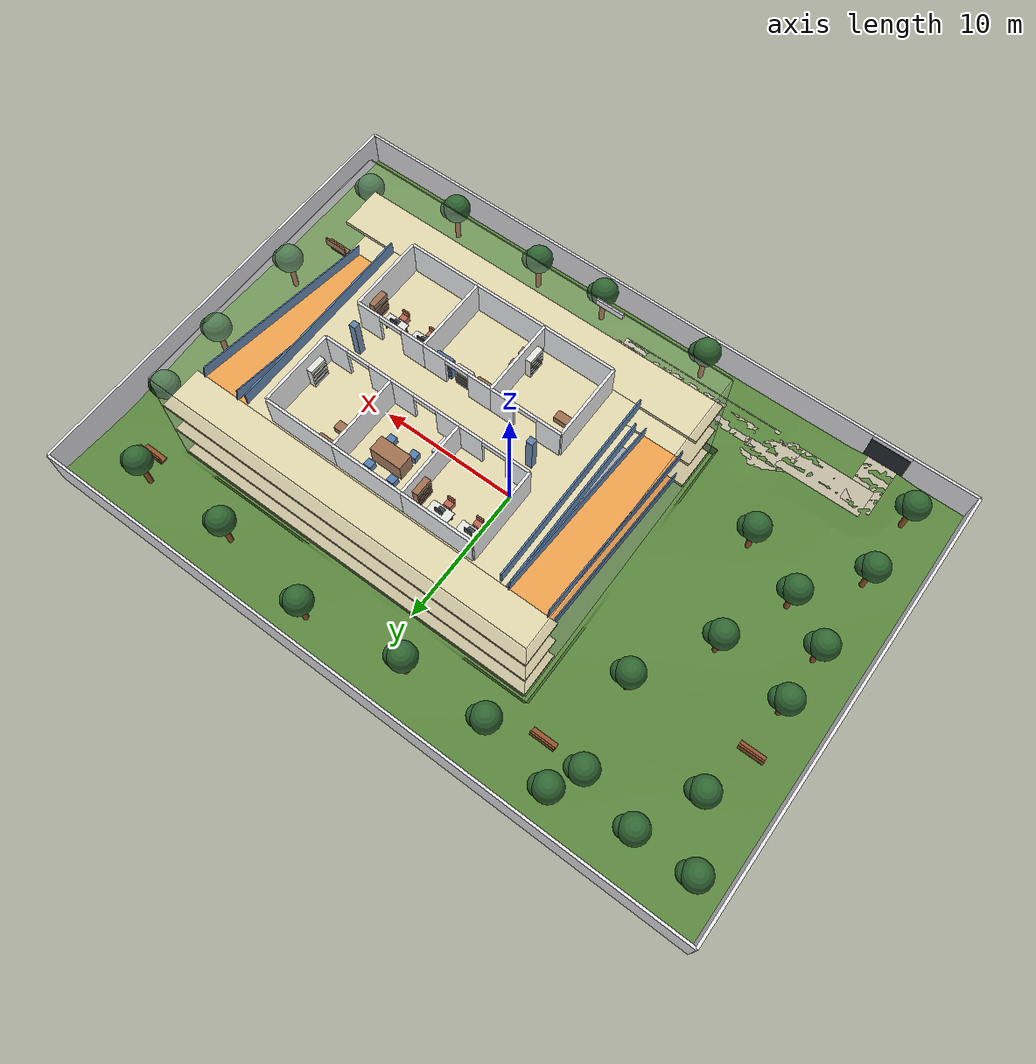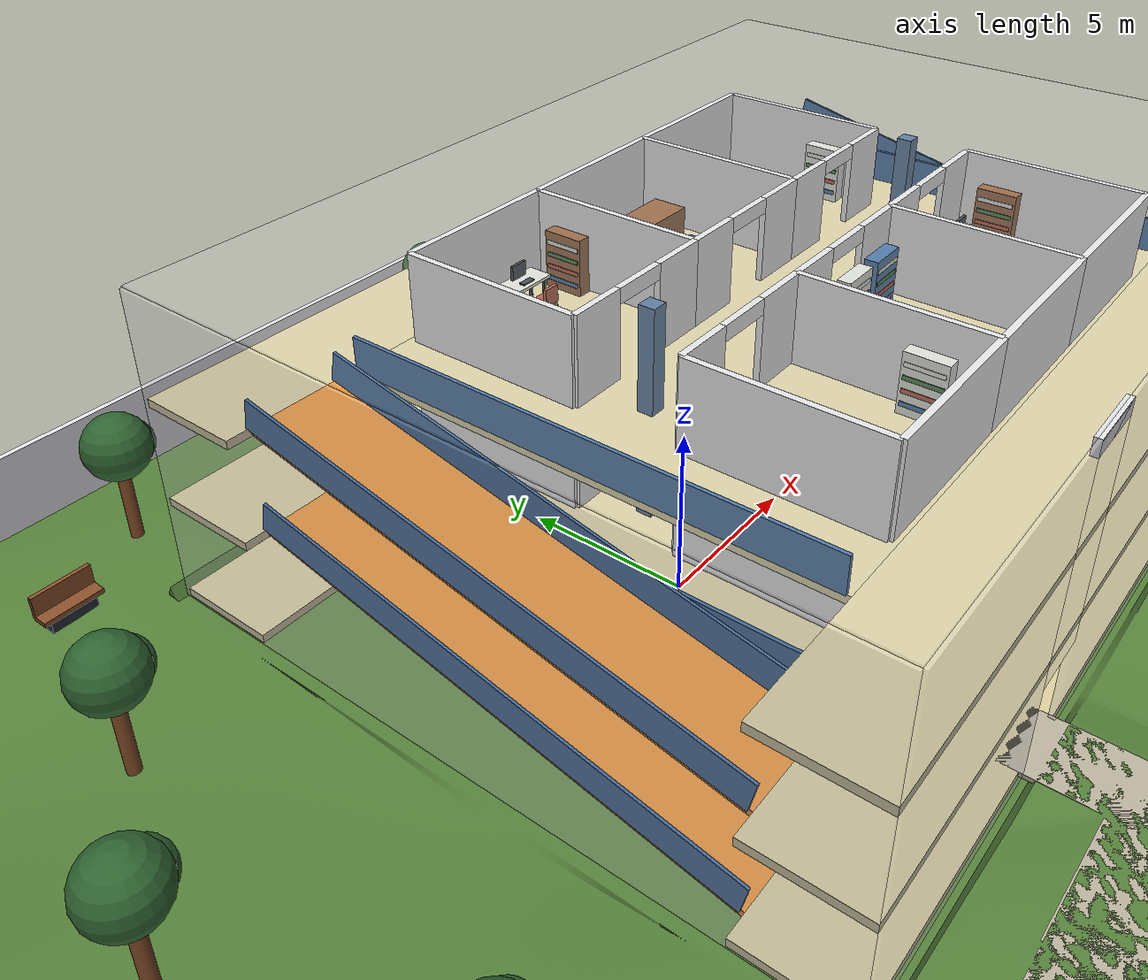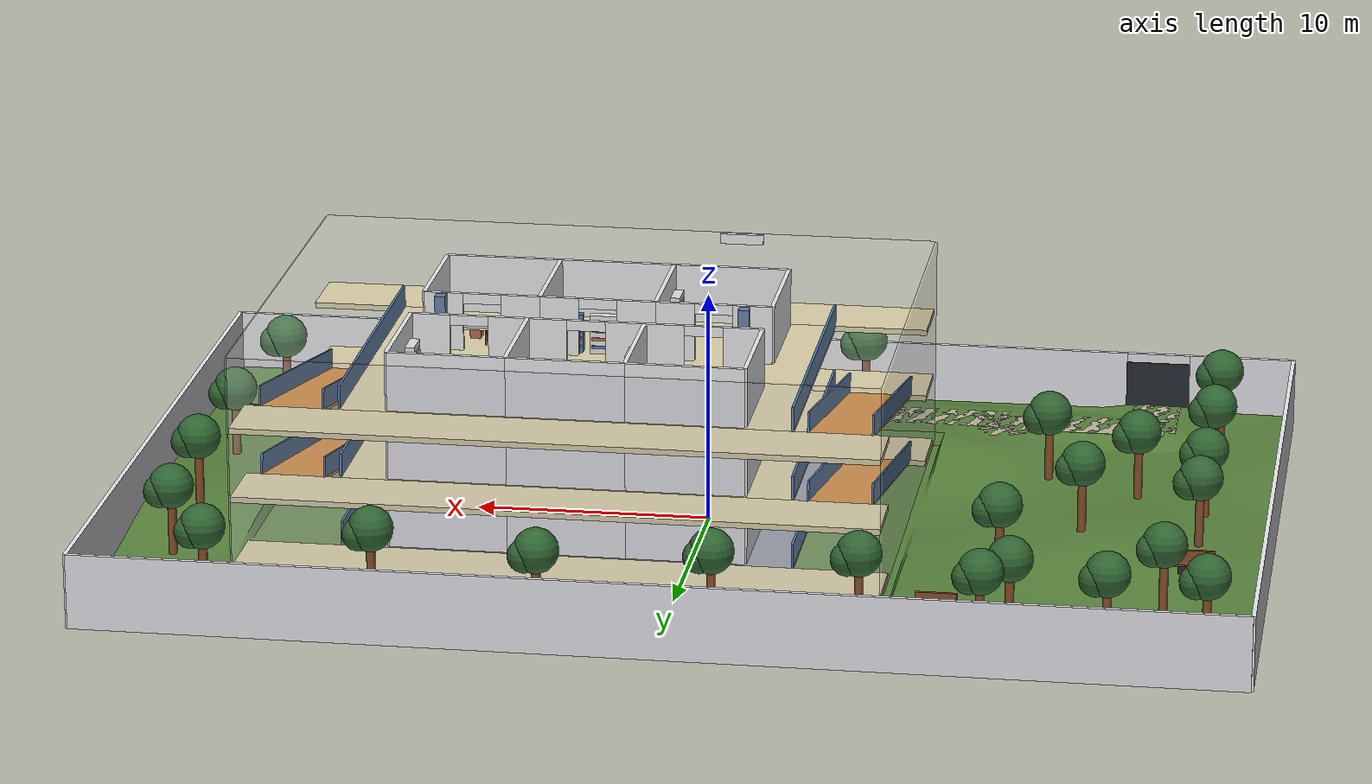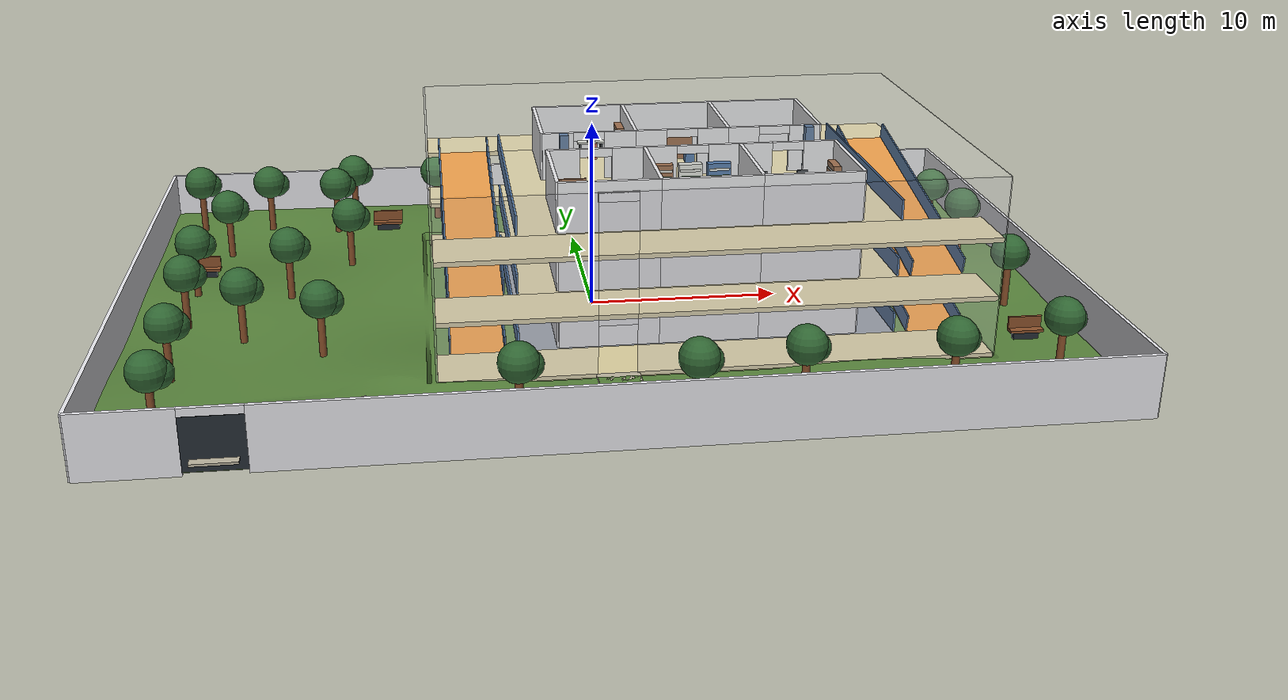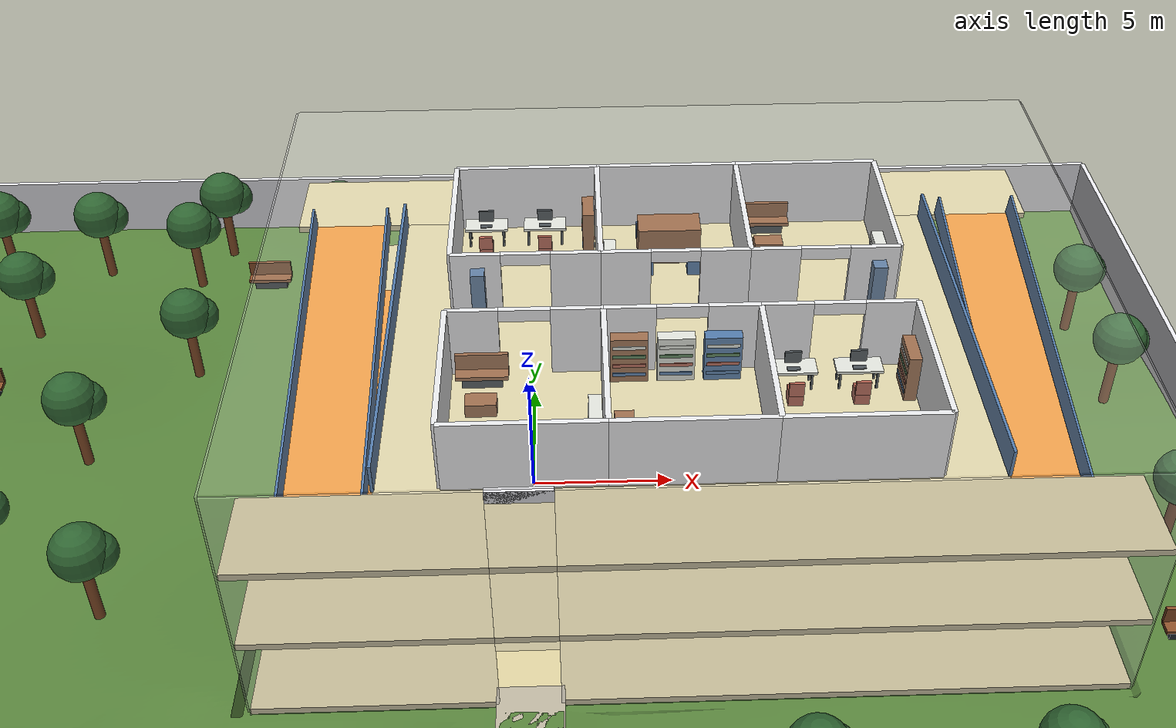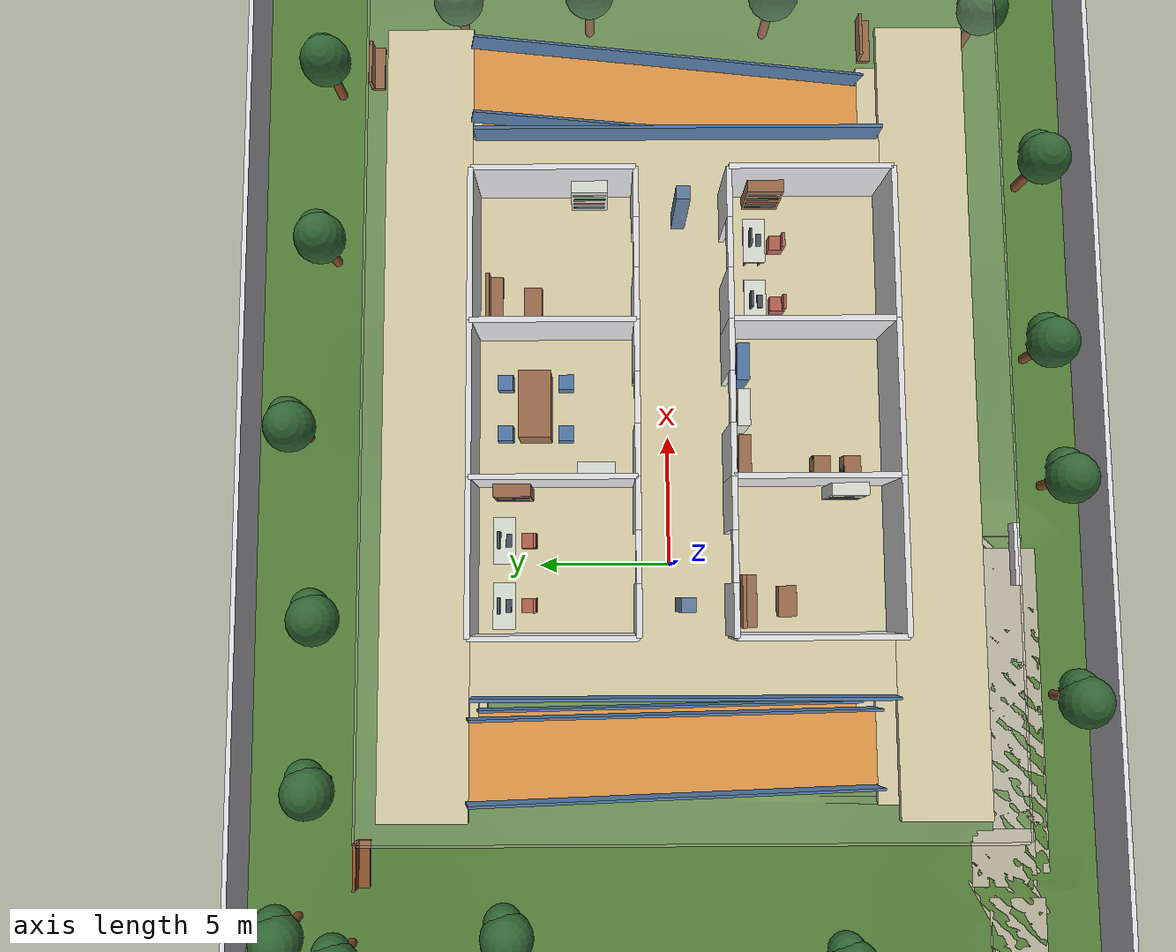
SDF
<?xml version='1.0' encoding='utf-8'?>
<sdf version="1.7">
  <world name="floor_M7">
    <gravity>0 0 -9.8</gravity>
    <plugin name="gazebo_ros_state" filename="libgazebo_ros_state.so">
      <ros>
        <namespace>/gazebo</namespace>
      </ros>
    </plugin>
    <physics name="ode_physics" type="ode">
      <max_step_size>0.001</max_step_size>
      <real_time_factor>1</real_time_factor>
      <real_time_update_rate>1000</real_time_update_rate>
      <ode>
        <solver>
          <type>quick</type>
          <iters>150</iters>
          <sor>1.3</sor>
        </solver>
        <constraints>
          <cfm>0</cfm>
          <erp>0.2</erp>
          <contact_max_correcting_vel>0.2</contact_max_correcting_vel>
          <contact_surface_layer>0.001</contact_surface_layer>
        </constraints>
      </ode>
    </physics>
    <light name="sun" type="directional">
      <pose>0 0 28 0 0 0</pose>
      <diffuse>0.92 0.91 0.88 1</diffuse>
      <specular>0.18 0.18 0.16 1</specular>
      <direction>-0.35 -0.28 -0.9</direction>
      <cast_shadows>true</cast_shadows>
    </light>
    <light name="fill" type="point">
      <pose>0 0 4.5 0 0 0</pose>
      <diffuse>0.45 0.48 0.52 1</diffuse>
      <specular>0.02 0.02 0.02 1</specular>
      <cast_shadows>false</cast_shadows>
      <attenuation>
        <range>80</range>
        <constant>0.5</constant>
        <linear>0.02</linear>
      </attenuation>
    </light>
    <scene>
      <ambient>0.48 0.49 0.53 1</ambient>
      <background>0.72 0.77 0.84 1</background>
    </scene>
    <gui fullscreen="false">
      <camera name="user_camera">
        <pose>33.6 -28.8 40.8 0 0.65 2.2</pose>
        <view_controller>orbit</view_controller>
      </camera>
    </gui>
    <model name="floor_M7_structure">
      <static>true</static>
      <link name="structure">
        <collision name="estate_terrain_surface_collision">
          <pose>0 0 0 0 0 0</pose>
          <geometry>
            <mesh>
              <uri>3DModel/unseen/M7/estate_terrain_surface.stl</uri>
            </mesh>
          </geometry>
          <max_contacts>40</max_contacts>
          <surface>
            <friction>
              <ode>
                <mu>8</mu>
                <mu2>8</mu2>
              </ode>
            </friction>
            <contact>
              <ode>
                <kp>1e7</kp>
                <kd>1000</kd>
                <max_vel>0.1</max_vel>
                <min_depth>0.001</min_depth>
              </ode>
            </contact>
          </surface>
        </collision>
        <visual name="estate_terrain_surface_visual">
          <pose>0 0 0 0 0 0</pose>
          <geometry>
            <mesh>
              <uri>3DModel/unseen/M7/estate_terrain_surface.stl</uri>
            </mesh>
          </geometry>
          <material>
            <ambient>0.34 0.51 0.23 1</ambient>
            <diffuse>0.34 0.51 0.23 1</diffuse>
          </material>
        </visual>
        <collision name="outer_south_wall_0_collision">
          <pose>-21.7 -16 1.4 0 0 0</pose>
          <geometry>
            <box>
              <size>4.6 0.18 3.2</size>
            </box>
          </geometry>
          <max_contacts>40</max_contacts>
          <surface>
            <friction>
              <ode>
                <mu>2</mu>
                <mu2>2</mu2>
              </ode>
            </friction>
            <contact>
              <ode>
                <kp>1e7</kp>
                <kd>1000</kd>
                <max_vel>0.1</max_vel>
                <min_depth>0.001</min_depth>
              </ode>
            </contact>
          </surface>
        </collision>
        <visual name="outer_south_wall_0_visual">
          <pose>-21.7 -16 1.4 0 0 0</pose>
          <geometry>
            <box>
              <size>4.6 0.18 3.2</size>
            </box>
          </geometry>
          <material>
            <ambient>0.91 0.91 0.93 1</ambient>
            <diffuse>0.91 0.91 0.93 1</diffuse>
          </material>
        </visual>
        <collision name="outer_south_wall_1_collision">
          <pose>3.7 -16 1.4 0 0 0</pose>
          <geometry>
            <box>
              <size>40.6 0.18 3.2</size>
            </box>
          </geometry>
          <max_contacts>40</max_contacts>
          <surface>
            <friction>
              <ode>
                <mu>2</mu>
                <mu2>2</mu2>
              </ode>
            </friction>
            <contact>
              <ode>
                <kp>1e7</kp>
                <kd>1000</kd>
                <max_vel>0.1</max_vel>
                <min_depth>0.001</min_depth>
              </ode>
            </contact>
          </surface>
        </collision>
        <visual name="outer_south_wall_1_visual">
          <pose>3.7 -16 1.4 0 0 0</pose>
          <geometry>
            <box>
              <size>40.6 0.18 3.2</size>
            </box>
          </geometry>
          <material>
            <ambient>0.91 0.91 0.93 1</ambient>
            <diffuse>0.91 0.91 0.93 1</diffuse>
          </material>
        </visual>
        <collision name="outer_south_lintel_wall_collision">
          <pose>-18 -16 2.78 0 0 0</pose>
          <geometry>
            <box>
              <size>2.8 0.18 0.44</size>
            </box>
          </geometry>
          <max_contacts>40</max_contacts>
          <surface>
            <friction>
              <ode>
                <mu>2</mu>
                <mu2>2</mu2>
              </ode>
            </friction>
            <contact>
              <ode>
                <kp>1e7</kp>
                <kd>1000</kd>
                <max_vel>0.1</max_vel>
                <min_depth>0.001</min_depth>
              </ode>
            </contact>
          </surface>
        </collision>
        <visual name="outer_south_lintel_wall_visual">
          <pose>-18 -16 2.78 0 0 0</pose>
          <geometry>
            <box>
              <size>2.8 0.18 0.44</size>
            </box>
          </geometry>
          <material>
            <ambient>0.91 0.91 0.93 1</ambient>
            <diffuse>0.91 0.91 0.93 1</diffuse>
          </material>
        </visual>
        <collision name="outer_north_wall_0_collision">
          <pose>0 16 1.4 0 0 0</pose>
          <geometry>
            <box>
              <size>48 0.18 3.2</size>
            </box>
          </geometry>
          <max_contacts>40</max_contacts>
          <surface>
            <friction>
              <ode>
                <mu>2</mu>
                <mu2>2</mu2>
              </ode>
            </friction>
            <contact>
              <ode>
                <kp>1e7</kp>
                <kd>1000</kd>
                <max_vel>0.1</max_vel>
                <min_depth>0.001</min_depth>
              </ode>
            </contact>
          </surface>
        </collision>
        <visual name="outer_north_wall_0_visual">
          <pose>0 16 1.4 0 0 0</pose>
          <geometry>
            <box>
              <size>48 0.18 3.2</size>
            </box>
          </geometry>
          <material>
            <ambient>0.91 0.91 0.93 1</ambient>
            <diffuse>0.91 0.91 0.93 1</diffuse>
          </material>
        </visual>
        <collision name="outer_west_wall_0_collision">
          <pose>-24 0 1.4 0 0 1.57079633</pose>
          <geometry>
            <box>
              <size>32 0.18 3.2</size>
            </box>
          </geometry>
          <max_contacts>40</max_contacts>
          <surface>
            <friction>
              <ode>
                <mu>2</mu>
                <mu2>2</mu2>
              </ode>
            </friction>
            <contact>
              <ode>
                <kp>1e7</kp>
                <kd>1000</kd>
                <max_vel>0.1</max_vel>
                <min_depth>0.001</min_depth>
              </ode>
            </contact>
          </surface>
        </collision>
        <visual name="outer_west_wall_0_visual">
          <pose>-24 0 1.4 0 0 1.57079633</pose>
          <geometry>
            <box>
              <size>32 0.18 3.2</size>
            </box>
          </geometry>
          <material>
            <ambient>0.91 0.91 0.93 1</ambient>
            <diffuse>0.91 0.91 0.93 1</diffuse>
          </material>
        </visual>
        <collision name="outer_east_wall_0_collision">
          <pose>24 0 1.4 0 0 1.57079633</pose>
          <geometry>
            <box>
              <size>32 0.18 3.2</size>
            </box>
          </geometry>
          <max_contacts>40</max_contacts>
          <surface>
            <friction>
              <ode>
                <mu>2</mu>
                <mu2>2</mu2>
              </ode>
            </friction>
            <contact>
              <ode>
                <kp>1e7</kp>
                <kd>1000</kd>
                <max_vel>0.1</max_vel>
                <min_depth>0.001</min_depth>
              </ode>
            </contact>
          </surface>
        </collision>
        <visual name="outer_east_wall_0_visual">
          <pose>24 0 1.4 0 0 1.57079633</pose>
          <geometry>
            <box>
              <size>32 0.18 3.2</size>
            </box>
          </geometry>
          <material>
            <ambient>0.91 0.91 0.93 1</ambient>
            <diffuse>0.91 0.91 0.93 1</diffuse>
          </material>
        </visual>
        <collision name="closed_outer_gate_obstacle_collision">
          <pose>-18 -16 1.3 0 0 0</pose>
          <geometry>
            <box>
              <size>2.8 0.2 2.6</size>
            </box>
          </geometry>
          <max_contacts>40</max_contacts>
          <surface>
            <friction>
              <ode>
                <mu>2</mu>
                <mu2>2</mu2>
              </ode>
            </friction>
            <contact>
              <ode>
                <kp>1e7</kp>
                <kd>1000</kd>
                <max_vel>0.1</max_vel>
                <min_depth>0.001</min_depth>
              </ode>
            </contact>
          </surface>
        </collision>
        <visual name="closed_outer_gate_obstacle_visual">
          <pose>-18 -16 1.3 0 0 0</pose>
          <geometry>
            <box>
              <size>2.8 0.2 2.6</size>
            </box>
          </geometry>
          <material>
            <ambient>0.15 0.18 0.21 1</ambient>
            <diffuse>0.15 0.18 0.21 1</diffuse>
          </material>
        </visual>
        <collision name="entrance_path_floor0_collision">
          <pose>-18 -14.4 0.54 0 0 1.57079633</pose>
          <geometry>
            <box>
              <size>4.3 2.1 0.12</size>
            </box>
          </geometry>
          <max_contacts>40</max_contacts>
          <surface>
            <friction>
              <ode>
                <mu>2</mu>
                <mu2>2</mu2>
              </ode>
            </friction>
            <contact>
              <ode>
                <kp>1e7</kp>
                <kd>1000</kd>
                <max_vel>0.1</max_vel>
                <min_depth>0.001</min_depth>
              </ode>
            </contact>
          </surface>
        </collision>
        <visual name="entrance_path_floor0_visual">
          <pose>-18 -14.4 0.54 0 0 1.57079633</pose>
          <geometry>
            <box>
              <size>4.3 2.1 0.12</size>
            </box>
          </geometry>
          <material>
            <ambient>0.73 0.70 0.62 1</ambient>
            <diffuse>0.73 0.70 0.62 1</diffuse>
          </material>
        </visual>
        <collision name="entrance_path_floor1_collision">
          <pose>-15.5 -12.8 0.54 0 0 0</pose>
          <geometry>
            <box>
              <size>6.1 2.1 0.12</size>
            </box>
          </geometry>
          <max_contacts>40</max_contacts>
          <surface>
            <friction>
              <ode>
                <mu>2</mu>
                <mu2>2</mu2>
              </ode>
            </friction>
            <contact>
              <ode>
                <kp>1e7</kp>
                <kd>1000</kd>
                <max_vel>0.1</max_vel>
                <min_depth>0.001</min_depth>
              </ode>
            </contact>
          </surface>
        </collision>
        <visual name="entrance_path_floor1_visual">
          <pose>-15.5 -12.8 0.54 0 0 0</pose>
          <geometry>
            <box>
              <size>6.1 2.1 0.12</size>
            </box>
          </geometry>
          <material>
            <ambient>0.73 0.70 0.62 1</ambient>
            <diffuse>0.73 0.70 0.62 1</diffuse>
          </material>
        </visual>
        <collision name="entrance_path_floor2_collision">
          <pose>-12 -12.25 0.54 0 0 0.502843211</pose>
          <geometry>
            <box>
              <size>3.38254244 2.1 0.12</size>
            </box>
          </geometry>
          <max_contacts>40</max_contacts>
          <surface>
            <friction>
              <ode>
                <mu>2</mu>
                <mu2>2</mu2>
              </ode>
            </friction>
            <contact>
              <ode>
                <kp>1e7</kp>
                <kd>1000</kd>
                <max_vel>0.1</max_vel>
                <min_depth>0.001</min_depth>
              </ode>
            </contact>
          </surface>
        </collision>
        <visual name="entrance_path_floor2_visual">
          <pose>-12 -12.25 0.54 0 0 0.502843211</pose>
          <geometry>
            <box>
              <size>3.38254244 2.1 0.12</size>
            </box>
          </geometry>
          <material>
            <ambient>0.73 0.70 0.62 1</ambient>
            <diffuse>0.73 0.70 0.62 1</diffuse>
          </material>
        </visual>
        <collision name="entrance_path_floor3_collision">
          <pose>-11 -12.35 0.54 0 0 -1.57079633</pose>
          <geometry>
            <box>
              <size>2.4 2.1 0.12</size>
            </box>
          </geometry>
          <max_contacts>40</max_contacts>
          <surface>
            <friction>
              <ode>
                <mu>2</mu>
                <mu2>2</mu2>
              </ode>
            </friction>
            <contact>
              <ode>
                <kp>1e7</kp>
                <kd>1000</kd>
                <max_vel>0.1</max_vel>
                <min_depth>0.001</min_depth>
              </ode>
            </contact>
          </surface>
        </collision>
        <visual name="entrance_path_floor3_visual">
          <pose>-11 -12.35 0.54 0 0 -1.57079633</pose>
          <geometry>
            <box>
              <size>2.4 2.1 0.12</size>
            </box>
          </geometry>
          <material>
            <ambient>0.73 0.70 0.62 1</ambient>
            <diffuse>0.73 0.70 0.62 1</diffuse>
          </material>
        </visual>
        <collision name="entrance_path_floor4_collision">
          <pose>-5.5 -13 0.54 0 0 0</pose>
          <geometry>
            <box>
              <size>12.1 2.1 0.12</size>
            </box>
          </geometry>
          <max_contacts>40</max_contacts>
          <surface>
            <friction>
              <ode>
                <mu>2</mu>
                <mu2>2</mu2>
              </ode>
            </friction>
            <contact>
              <ode>
                <kp>1e7</kp>
                <kd>1000</kd>
                <max_vel>0.1</max_vel>
                <min_depth>0.001</min_depth>
              </ode>
            </contact>
          </surface>
        </collision>
        <visual name="entrance_path_floor4_visual">
          <pose>-5.5 -13 0.54 0 0 0</pose>
          <geometry>
            <box>
              <size>12.1 2.1 0.12</size>
            </box>
          </geometry>
          <material>
            <ambient>0.73 0.70 0.62 1</ambient>
            <diffuse>0.73 0.70 0.62 1</diffuse>
          </material>
        </visual>
        <collision name="entrance_path_floor5_collision">
          <pose>0 -11.5 0.54 0 0 1.57079633</pose>
          <geometry>
            <box>
              <size>4.1 2.1 0.12</size>
            </box>
          </geometry>
          <max_contacts>40</max_contacts>
          <surface>
            <friction>
              <ode>
                <mu>2</mu>
                <mu2>2</mu2>
              </ode>
            </friction>
            <contact>
              <ode>
                <kp>1e7</kp>
                <kd>1000</kd>
                <max_vel>0.1</max_vel>
                <min_depth>0.001</min_depth>
              </ode>
            </contact>
          </surface>
        </collision>
        <visual name="entrance_path_floor5_visual">
          <pose>0 -11.5 0.54 0 0 1.57079633</pose>
          <geometry>
            <box>
              <size>4.1 2.1 0.12</size>
            </box>
          </geometry>
          <material>
            <ambient>0.73 0.70 0.62 1</ambient>
            <diffuse>0.73 0.70 0.62 1</diffuse>
          </material>
        </visual>
        <collision name="outer_south_wall_0_part1_collision">
          <pose>-4.725 -10 5.05 0 0 0</pose>
          <geometry>
            <box>
              <size>7.55 0.18 9.2</size>
            </box>
          </geometry>
          <max_contacts>40</max_contacts>
          <surface>
            <friction>
              <ode>
                <mu>2</mu>
                <mu2>2</mu2>
              </ode>
            </friction>
            <contact>
              <ode>
                <kp>1e7</kp>
                <kd>1000</kd>
                <max_vel>0.1</max_vel>
                <min_depth>0.001</min_depth>
              </ode>
            </contact>
          </surface>
        </collision>
        <visual name="outer_south_wall_0_part1_visual">
          <pose>-4.725 -10 5.05 0 0 0</pose>
          <geometry>
            <box>
              <size>7.55 0.18 9.2</size>
            </box>
          </geometry>
          <material>
            <ambient>0.91 0.91 0.93 1</ambient>
            <diffuse>0.91 0.91 0.93 1</diffuse>
          </material>
          <transparency>0.72</transparency>
        </visual>
        <collision name="outer_south_wall_1_part2_collision">
          <pose>9.725 -10 5.05 0 0 0</pose>
          <geometry>
            <box>
              <size>17.55 0.18 9.2</size>
            </box>
          </geometry>
          <max_contacts>40</max_contacts>
          <surface>
            <friction>
              <ode>
                <mu>2</mu>
                <mu2>2</mu2>
              </ode>
            </friction>
            <contact>
              <ode>
                <kp>1e7</kp>
                <kd>1000</kd>
                <max_vel>0.1</max_vel>
                <min_depth>0.001</min_depth>
              </ode>
            </contact>
          </surface>
        </collision>
        <visual name="outer_south_wall_1_part2_visual">
          <pose>9.725 -10 5.05 0 0 0</pose>
          <geometry>
            <box>
              <size>17.55 0.18 9.2</size>
            </box>
          </geometry>
          <material>
            <ambient>0.91 0.91 0.93 1</ambient>
            <diffuse>0.91 0.91 0.93 1</diffuse>
          </material>
          <transparency>0.72</transparency>
        </visual>
        <collision name="outer_south_lintel_wall_part3_collision">
          <pose>0 -10 9.43 0 0 0</pose>
          <geometry>
            <box>
              <size>1.9 0.18 0.44</size>
            </box>
          </geometry>
          <max_contacts>40</max_contacts>
          <surface>
            <friction>
              <ode>
                <mu>2</mu>
                <mu2>2</mu2>
              </ode>
            </friction>
            <contact>
              <ode>
                <kp>1e7</kp>
                <kd>1000</kd>
                <max_vel>0.1</max_vel>
                <min_depth>0.001</min_depth>
              </ode>
            </contact>
          </surface>
        </collision>
        <visual name="outer_south_lintel_wall_part3_visual">
          <pose>0 -10 9.43 0 0 0</pose>
          <geometry>
            <box>
              <size>1.9 0.18 0.44</size>
            </box>
          </geometry>
          <material>
            <ambient>0.91 0.91 0.93 1</ambient>
            <diffuse>0.91 0.91 0.93 1</diffuse>
          </material>
        </visual>
        <collision name="outer_north_wall_0_part4_collision">
          <pose>5 10 5.05 0 0 0</pose>
          <geometry>
            <box>
              <size>27 0.18 9.2</size>
            </box>
          </geometry>
          <max_contacts>40</max_contacts>
          <surface>
            <friction>
              <ode>
                <mu>2</mu>
                <mu2>2</mu2>
              </ode>
            </friction>
            <contact>
              <ode>
                <kp>1e7</kp>
                <kd>1000</kd>
                <max_vel>0.1</max_vel>
                <min_depth>0.001</min_depth>
              </ode>
            </contact>
          </surface>
        </collision>
        <visual name="outer_north_wall_0_part4_visual">
          <pose>5 10 5.05 0 0 0</pose>
          <geometry>
            <box>
              <size>27 0.18 9.2</size>
            </box>
          </geometry>
          <material>
            <ambient>0.91 0.91 0.93 1</ambient>
            <diffuse>0.91 0.91 0.93 1</diffuse>
          </material>
          <transparency>0.72</transparency>
        </visual>
        <collision name="outer_west_wall_0_part5_collision">
          <pose>-8.5 0 5.05 0 0 1.57079633</pose>
          <geometry>
            <box>
              <size>20 0.18 9.2</size>
            </box>
          </geometry>
          <max_contacts>40</max_contacts>
          <surface>
            <friction>
              <ode>
                <mu>2</mu>
                <mu2>2</mu2>
              </ode>
            </friction>
            <contact>
              <ode>
                <kp>1e7</kp>
                <kd>1000</kd>
                <max_vel>0.1</max_vel>
                <min_depth>0.001</min_depth>
              </ode>
            </contact>
          </surface>
        </collision>
        <visual name="outer_west_wall_0_part5_visual">
          <pose>-8.5 0 5.05 0 0 1.57079633</pose>
          <geometry>
            <box>
              <size>20 0.18 9.2</size>
            </box>
          </geometry>
          <material>
            <ambient>0.91 0.91 0.93 1</ambient>
            <diffuse>0.91 0.91 0.93 1</diffuse>
          </material>
          <transparency>0.72</transparency>
        </visual>
        <collision name="outer_east_wall_0_part6_collision">
          <pose>18.5 0 5.05 0 0 1.57079633</pose>
          <geometry>
            <box>
              <size>20 0.18 9.2</size>
            </box>
          </geometry>
          <max_contacts>40</max_contacts>
          <surface>
            <friction>
              <ode>
                <mu>2</mu>
                <mu2>2</mu2>
              </ode>
            </friction>
            <contact>
              <ode>
                <kp>1e7</kp>
                <kd>1000</kd>
                <max_vel>0.1</max_vel>
                <min_depth>0.001</min_depth>
              </ode>
            </contact>
          </surface>
        </collision>
        <visual name="outer_east_wall_0_part6_visual">
          <pose>18.5 0 5.05 0 0 1.57079633</pose>
          <geometry>
            <box>
              <size>20 0.18 9.2</size>
            </box>
          </geometry>
          <material>
            <ambient>0.91 0.91 0.93 1</ambient>
            <diffuse>0.91 0.91 0.93 1</diffuse>
          </material>
          <transparency>0.72</transparency>
        </visual>
        <collision name="upper_entrance_wall_collision">
          <pose>0 -10 6.375 0 0 0</pose>
          <geometry>
            <box>
              <size>1.9 0.18 6.55</size>
            </box>
          </geometry>
          <max_contacts>40</max_contacts>
          <surface>
            <friction>
              <ode>
                <mu>2</mu>
                <mu2>2</mu2>
              </ode>
            </friction>
            <contact>
              <ode>
                <kp>1e7</kp>
                <kd>1000</kd>
                <max_vel>0.1</max_vel>
                <min_depth>0.001</min_depth>
              </ode>
            </contact>
          </surface>
        </collision>
        <visual name="upper_entrance_wall_visual">
          <pose>0 -10 6.375 0 0 0</pose>
          <geometry>
            <box>
              <size>1.9 0.18 6.55</size>
            </box>
          </geometry>
          <material>
            <ambient>0.91 0.91 0.93 1</ambient>
            <diffuse>0.91 0.91 0.93 1</diffuse>
          </material>
          <transparency>0.72</transparency>
        </visual>
        <collision name="L1_floor_main_collision">
          <pose>5 0 0.48 0 0 0</pose>
          <geometry>
            <box>
              <size>19 14 0.24</size>
            </box>
          </geometry>
          <max_contacts>40</max_contacts>
          <surface>
            <friction>
              <ode>
                <mu>2</mu>
                <mu2>2</mu2>
              </ode>
            </friction>
            <contact>
              <ode>
                <kp>1e7</kp>
                <kd>1000</kd>
                <max_vel>0.1</max_vel>
                <min_depth>0.001</min_depth>
              </ode>
            </contact>
          </surface>
        </collision>
        <visual name="L1_floor_main_visual">
          <pose>5 0 0.48 0 0 0</pose>
          <geometry>
            <box>
              <size>19 14 0.24</size>
            </box>
          </geometry>
          <material>
            <ambient>0.54 0.57 0.62 1</ambient>
            <diffuse>0.54 0.57 0.62 1</diffuse>
          </material>
        </visual>
        <collision name="L1_floor_landing-1_collision">
          <pose>5 -8.5 0.48 0 0 0</pose>
          <geometry>
            <box>
              <size>27 3 0.24</size>
            </box>
          </geometry>
          <max_contacts>40</max_contacts>
          <surface>
            <friction>
              <ode>
                <mu>2</mu>
                <mu2>2</mu2>
              </ode>
            </friction>
            <contact>
              <ode>
                <kp>1e7</kp>
                <kd>1000</kd>
                <max_vel>0.1</max_vel>
                <min_depth>0.001</min_depth>
              </ode>
            </contact>
          </surface>
        </collision>
        <visual name="L1_floor_landing-1_visual">
          <pose>5 -8.5 0.48 0 0 0</pose>
          <geometry>
            <box>
              <size>27 3 0.24</size>
            </box>
          </geometry>
          <material>
            <ambient>0.86 0.81 0.62 1</ambient>
            <diffuse>0.86 0.81 0.62 1</diffuse>
          </material>
        </visual>
        <collision name="L1_floor_landing1_collision">
          <pose>5 8.5 0.48 0 0 0</pose>
          <geometry>
            <box>
              <size>27 3 0.24</size>
            </box>
          </geometry>
          <max_contacts>40</max_contacts>
          <surface>
            <friction>
              <ode>
                <mu>2</mu>
                <mu2>2</mu2>
              </ode>
            </friction>
            <contact>
              <ode>
                <kp>1e7</kp>
                <kd>1000</kd>
                <max_vel>0.1</max_vel>
                <min_depth>0.001</min_depth>
              </ode>
            </contact>
          </surface>
        </collision>
        <visual name="L1_floor_landing1_visual">
          <pose>5 8.5 0.48 0 0 0</pose>
          <geometry>
            <box>
              <size>27 3 0.24</size>
            </box>
          </geometry>
          <material>
            <ambient>0.86 0.81 0.62 1</ambient>
            <diffuse>0.86 0.81 0.62 1</diffuse>
          </material>
        </visual>
        <collision name="L1_shaft_rail-1_collision">
          <pose>-4.5 0 1.1 0 0 0</pose>
          <geometry>
            <box>
              <size>0.1 13.8 1</size>
            </box>
          </geometry>
          <max_contacts>40</max_contacts>
          <surface>
            <friction>
              <ode>
                <mu>2</mu>
                <mu2>2</mu2>
              </ode>
            </friction>
            <contact>
              <ode>
                <kp>1e7</kp>
                <kd>1000</kd>
                <max_vel>0.1</max_vel>
                <min_depth>0.001</min_depth>
              </ode>
            </contact>
          </surface>
        </collision>
        <visual name="L1_shaft_rail-1_visual">
          <pose>-4.5 0 1.1 0 0 0</pose>
          <geometry>
            <box>
              <size>0.1 13.8 1</size>
            </box>
          </geometry>
          <material>
            <ambient>0.19 0.38 0.62 1</ambient>
            <diffuse>0.19 0.38 0.62 1</diffuse>
          </material>
        </visual>
        <collision name="L1_shaft_rail1_collision">
          <pose>14.5 0 1.1 0 0 0</pose>
          <geometry>
            <box>
              <size>0.1 13.8 1</size>
            </box>
          </geometry>
          <max_contacts>40</max_contacts>
          <surface>
            <friction>
              <ode>
                <mu>2</mu>
                <mu2>2</mu2>
              </ode>
            </friction>
            <contact>
              <ode>
                <kp>1e7</kp>
                <kd>1000</kd>
                <max_vel>0.1</max_vel>
                <min_depth>0.001</min_depth>
              </ode>
            </contact>
          </surface>
        </collision>
        <visual name="L1_shaft_rail1_visual">
          <pose>14.5 0 1.1 0 0 0</pose>
          <geometry>
            <box>
              <size>0.1 13.8 1</size>
            </box>
          </geometry>
          <material>
            <ambient>0.19 0.38 0.62 1</ambient>
            <diffuse>0.19 0.38 0.62 1</diffuse>
          </material>
        </visual>
        <collision name="L1_column_prop-1.5_collision">
          <pose>-1.5 0 2.05 0 0 0</pose>
          <geometry>
            <box>
              <size>0.45 0.45 2.9</size>
            </box>
          </geometry>
          <max_contacts>40</max_contacts>
          <surface>
            <friction>
              <ode>
                <mu>2</mu>
                <mu2>2</mu2>
              </ode>
            </friction>
            <contact>
              <ode>
                <kp>1e7</kp>
                <kd>1000</kd>
                <max_vel>0.1</max_vel>
                <min_depth>0.001</min_depth>
              </ode>
            </contact>
          </surface>
        </collision>
        <visual name="L1_column_prop-1.5_visual">
          <pose>-1.5 0 2.05 0 0 0</pose>
          <geometry>
            <box>
              <size>0.45 0.45 2.9</size>
            </box>
          </geometry>
          <material>
            <ambient>0.26 0.40 0.58 1</ambient>
            <diffuse>0.26 0.40 0.58 1</diffuse>
          </material>
        </visual>
        <collision name="L1_column_prop11.5_collision">
          <pose>11.5 0 2.05 0 0 0</pose>
          <geometry>
            <box>
              <size>0.45 0.45 2.9</size>
            </box>
          </geometry>
          <max_contacts>40</max_contacts>
          <surface>
            <friction>
              <ode>
                <mu>2</mu>
                <mu2>2</mu2>
              </ode>
            </friction>
            <contact>
              <ode>
                <kp>1e7</kp>
                <kd>1000</kd>
                <max_vel>0.1</max_vel>
                <min_depth>0.001</min_depth>
              </ode>
            </contact>
          </surface>
        </collision>
        <visual name="L1_column_prop11.5_visual">
          <pose>11.5 0 2.05 0 0 0</pose>
          <geometry>
            <box>
              <size>0.45 0.45 2.9</size>
            </box>
          </geometry>
          <material>
            <ambient>0.26 0.40 0.58 1</ambient>
            <diffuse>0.26 0.40 0.58 1</diffuse>
          </material>
        </visual>
        <collision name="L1_office_-1_0_south_wall_0_collision">
          <pose>0 -6.8 1.825 0 0 0</pose>
          <geometry>
            <box>
              <size>5 0.18 2.65</size>
            </box>
          </geometry>
          <max_contacts>40</max_contacts>
          <surface>
            <friction>
              <ode>
                <mu>2</mu>
                <mu2>2</mu2>
              </ode>
            </friction>
            <contact>
              <ode>
                <kp>1e7</kp>
                <kd>1000</kd>
                <max_vel>0.1</max_vel>
                <min_depth>0.001</min_depth>
              </ode>
            </contact>
          </surface>
        </collision>
        <visual name="L1_office_-1_0_south_wall_0_visual">
          <pose>0 -6.8 1.825 0 0 0</pose>
          <geometry>
            <box>
              <size>5 0.18 2.65</size>
            </box>
          </geometry>
          <material>
            <ambient>0.91 0.91 0.93 1</ambient>
            <diffuse>0.91 0.91 0.93 1</diffuse>
          </material>
        </visual>
        <collision name="L1_office_-1_0_north_wall_0_collision">
          <pose>-1.6625 -1.5 1.825 0 0 0</pose>
          <geometry>
            <box>
              <size>1.675 0.18 2.65</size>
            </box>
          </geometry>
          <max_contacts>40</max_contacts>
          <surface>
            <friction>
              <ode>
                <mu>2</mu>
                <mu2>2</mu2>
              </ode>
            </friction>
            <contact>
              <ode>
                <kp>1e7</kp>
                <kd>1000</kd>
                <max_vel>0.1</max_vel>
                <min_depth>0.001</min_depth>
              </ode>
            </contact>
          </surface>
        </collision>
        <visual name="L1_office_-1_0_north_wall_0_visual">
          <pose>-1.6625 -1.5 1.825 0 0 0</pose>
          <geometry>
            <box>
              <size>1.675 0.18 2.65</size>
            </box>
          </geometry>
          <material>
            <ambient>0.91 0.91 0.93 1</ambient>
            <diffuse>0.91 0.91 0.93 1</diffuse>
          </material>
        </visual>
        <collision name="L1_office_-1_0_north_wall_1_collision">
          <pose>1.6625 -1.5 1.825 0 0 0</pose>
          <geometry>
            <box>
              <size>1.675 0.18 2.65</size>
            </box>
          </geometry>
          <max_contacts>40</max_contacts>
          <surface>
            <friction>
              <ode>
                <mu>2</mu>
                <mu2>2</mu2>
              </ode>
            </friction>
            <contact>
              <ode>
                <kp>1e7</kp>
                <kd>1000</kd>
                <max_vel>0.1</max_vel>
                <min_depth>0.001</min_depth>
              </ode>
            </contact>
          </surface>
        </collision>
        <visual name="L1_office_-1_0_north_wall_1_visual">
          <pose>1.6625 -1.5 1.825 0 0 0</pose>
          <geometry>
            <box>
              <size>1.675 0.18 2.65</size>
            </box>
          </geometry>
          <material>
            <ambient>0.91 0.91 0.93 1</ambient>
            <diffuse>0.91 0.91 0.93 1</diffuse>
          </material>
        </visual>
        <collision name="L1_office_-1_0_north_lintel_wall_collision">
          <pose>0 -1.5 2.93 0 0 0</pose>
          <geometry>
            <box>
              <size>1.65 0.18 0.44</size>
            </box>
          </geometry>
          <max_contacts>40</max_contacts>
          <surface>
            <friction>
              <ode>
                <mu>2</mu>
                <mu2>2</mu2>
              </ode>
            </friction>
            <contact>
              <ode>
                <kp>1e7</kp>
                <kd>1000</kd>
                <max_vel>0.1</max_vel>
                <min_depth>0.001</min_depth>
              </ode>
            </contact>
          </surface>
        </collision>
        <visual name="L1_office_-1_0_north_lintel_wall_visual">
          <pose>0 -1.5 2.93 0 0 0</pose>
          <geometry>
            <box>
              <size>1.65 0.18 0.44</size>
            </box>
          </geometry>
          <material>
            <ambient>0.91 0.91 0.93 1</ambient>
            <diffuse>0.91 0.91 0.93 1</diffuse>
          </material>
        </visual>
        <collision name="L1_office_-1_0_west_wall_0_collision">
          <pose>-2.5 -4.15 1.825 0 0 1.57079633</pose>
          <geometry>
            <box>
              <size>5.3 0.18 2.65</size>
            </box>
          </geometry>
          <max_contacts>40</max_contacts>
          <surface>
            <friction>
              <ode>
                <mu>2</mu>
                <mu2>2</mu2>
              </ode>
            </friction>
            <contact>
              <ode>
                <kp>1e7</kp>
                <kd>1000</kd>
                <max_vel>0.1</max_vel>
                <min_depth>0.001</min_depth>
              </ode>
            </contact>
          </surface>
        </collision>
        <visual name="L1_office_-1_0_west_wall_0_visual">
          <pose>-2.5 -4.15 1.825 0 0 1.57079633</pose>
          <geometry>
            <box>
              <size>5.3 0.18 2.65</size>
            </box>
          </geometry>
          <material>
            <ambient>0.91 0.91 0.93 1</ambient>
            <diffuse>0.91 0.91 0.93 1</diffuse>
          </material>
        </visual>
        <collision name="L1_office_-1_0_east_wall_0_collision">
          <pose>2.5 -4.15 1.825 0 0 1.57079633</pose>
          <geometry>
            <box>
              <size>5.3 0.18 2.65</size>
            </box>
          </geometry>
          <max_contacts>40</max_contacts>
          <surface>
            <friction>
              <ode>
                <mu>2</mu>
                <mu2>2</mu2>
              </ode>
            </friction>
            <contact>
              <ode>
                <kp>1e7</kp>
                <kd>1000</kd>
                <max_vel>0.1</max_vel>
                <min_depth>0.001</min_depth>
              </ode>
            </contact>
          </surface>
        </collision>
        <visual name="L1_office_-1_0_east_wall_0_visual">
          <pose>2.5 -4.15 1.825 0 0 1.57079633</pose>
          <geometry>
            <box>
              <size>5.3 0.18 2.65</size>
            </box>
          </geometry>
          <material>
            <ambient>0.91 0.91 0.93 1</ambient>
            <diffuse>0.91 0.91 0.93 1</diffuse>
          </material>
        </visual>
        <collision name="L1_office_-1_0_desk0_0_desktop_prop_collision">
          <pose>-1.5 -2.5 1.34 0 0 0</pose>
          <geometry>
            <box>
              <size>1.5 0.72 0.09</size>
            </box>
          </geometry>
          <max_contacts>40</max_contacts>
          <surface>
            <friction>
              <ode>
                <mu>2</mu>
                <mu2>2</mu2>
              </ode>
            </friction>
            <contact>
              <ode>
                <kp>1e7</kp>
                <kd>1000</kd>
                <max_vel>0.1</max_vel>
                <min_depth>0.001</min_depth>
              </ode>
            </contact>
          </surface>
        </collision>
        <visual name="L1_office_-1_0_desk0_0_desktop_prop_visual">
          <pose>-1.5 -2.5 1.34 0 0 0</pose>
          <geometry>
            <box>
              <size>1.5 0.72 0.09</size>
            </box>
          </geometry>
          <material>
            <ambient>0.87 0.88 0.85 1</ambient>
            <diffuse>0.87 0.88 0.85 1</diffuse>
          </material>
        </visual>
        <collision name="L1_office_-1_0_desk0_0_leg_prop_-0.6_-0.24_collision">
          <pose>-2.1 -2.74 0.95 0 0 0</pose>
          <geometry>
            <box>
              <size>0.07 0.07 0.7</size>
            </box>
          </geometry>
          <max_contacts>40</max_contacts>
          <surface>
            <friction>
              <ode>
                <mu>2</mu>
                <mu2>2</mu2>
              </ode>
            </friction>
            <contact>
              <ode>
                <kp>1e7</kp>
                <kd>1000</kd>
                <max_vel>0.1</max_vel>
                <min_depth>0.001</min_depth>
              </ode>
            </contact>
          </surface>
        </collision>
        <visual name="L1_office_-1_0_desk0_0_leg_prop_-0.6_-0.24_visual">
          <pose>-2.1 -2.74 0.95 0 0 0</pose>
          <geometry>
            <box>
              <size>0.07 0.07 0.7</size>
            </box>
          </geometry>
          <material>
            <ambient>0.15 0.18 0.21 1</ambient>
            <diffuse>0.15 0.18 0.21 1</diffuse>
          </material>
        </visual>
        <collision name="L1_office_-1_0_desk0_0_leg_prop_-0.6_0.24_collision">
          <pose>-2.1 -2.26 0.95 0 0 0</pose>
          <geometry>
            <box>
              <size>0.07 0.07 0.7</size>
            </box>
          </geometry>
          <max_contacts>40</max_contacts>
          <surface>
            <friction>
              <ode>
                <mu>2</mu>
                <mu2>2</mu2>
              </ode>
            </friction>
            <contact>
              <ode>
                <kp>1e7</kp>
                <kd>1000</kd>
                <max_vel>0.1</max_vel>
                <min_depth>0.001</min_depth>
              </ode>
            </contact>
          </surface>
        </collision>
        <visual name="L1_office_-1_0_desk0_0_leg_prop_-0.6_0.24_visual">
          <pose>-2.1 -2.26 0.95 0 0 0</pose>
          <geometry>
            <box>
              <size>0.07 0.07 0.7</size>
            </box>
          </geometry>
          <material>
            <ambient>0.15 0.18 0.21 1</ambient>
            <diffuse>0.15 0.18 0.21 1</diffuse>
          </material>
        </visual>
        <collision name="L1_office_-1_0_desk0_0_leg_prop_0.6_-0.24_collision">
          <pose>-0.9 -2.74 0.95 0 0 0</pose>
          <geometry>
            <box>
              <size>0.07 0.07 0.7</size>
            </box>
          </geometry>
          <max_contacts>40</max_contacts>
          <surface>
            <friction>
              <ode>
                <mu>2</mu>
                <mu2>2</mu2>
              </ode>
            </friction>
            <contact>
              <ode>
                <kp>1e7</kp>
                <kd>1000</kd>
                <max_vel>0.1</max_vel>
                <min_depth>0.001</min_depth>
              </ode>
            </contact>
          </surface>
        </collision>
        <visual name="L1_office_-1_0_desk0_0_leg_prop_0.6_-0.24_visual">
          <pose>-0.9 -2.74 0.95 0 0 0</pose>
          <geometry>
            <box>
              <size>0.07 0.07 0.7</size>
            </box>
          </geometry>
          <material>
            <ambient>0.15 0.18 0.21 1</ambient>
            <diffuse>0.15 0.18 0.21 1</diffuse>
          </material>
        </visual>
        <collision name="L1_office_-1_0_desk0_0_leg_prop_0.6_0.24_collision">
          <pose>-0.9 -2.26 0.95 0 0 0</pose>
          <geometry>
            <box>
              <size>0.07 0.07 0.7</size>
            </box>
          </geometry>
          <max_contacts>40</max_contacts>
          <surface>
            <friction>
              <ode>
                <mu>2</mu>
                <mu2>2</mu2>
              </ode>
            </friction>
            <contact>
              <ode>
                <kp>1e7</kp>
                <kd>1000</kd>
                <max_vel>0.1</max_vel>
                <min_depth>0.001</min_depth>
              </ode>
            </contact>
          </surface>
        </collision>
        <visual name="L1_office_-1_0_desk0_0_leg_prop_0.6_0.24_visual">
          <pose>-0.9 -2.26 0.95 0 0 0</pose>
          <geometry>
            <box>
              <size>0.07 0.07 0.7</size>
            </box>
          </geometry>
          <material>
            <ambient>0.15 0.18 0.21 1</ambient>
            <diffuse>0.15 0.18 0.21 1</diffuse>
          </material>
        </visual>
        <collision name="L1_office_-1_0_desk0_0_monitor_prop_collision">
          <pose>-1.5 -2.35 1.65 0 0 0</pose>
          <geometry>
            <box>
              <size>0.53 0.08 0.42</size>
            </box>
          </geometry>
          <max_contacts>40</max_contacts>
          <surface>
            <friction>
              <ode>
                <mu>2</mu>
                <mu2>2</mu2>
              </ode>
            </friction>
            <contact>
              <ode>
                <kp>1e7</kp>
                <kd>1000</kd>
                <max_vel>0.1</max_vel>
                <min_depth>0.001</min_depth>
              </ode>
            </contact>
          </surface>
        </collision>
        <visual name="L1_office_-1_0_desk0_0_monitor_prop_visual">
          <pose>-1.5 -2.35 1.65 0 0 0</pose>
          <geometry>
            <box>
              <size>0.53 0.08 0.42</size>
            </box>
          </geometry>
          <material>
            <ambient>0.15 0.18 0.21 1</ambient>
            <diffuse>0.15 0.18 0.21 1</diffuse>
          </material>
        </visual>
        <collision name="L1_office_-1_0_desk0_0_keyboard_prop_collision">
          <pose>-1.5 -2.65 1.4 0 0 0</pose>
          <geometry>
            <box>
              <size>0.42 0.18 0.035</size>
            </box>
          </geometry>
          <max_contacts>40</max_contacts>
          <surface>
            <friction>
              <ode>
                <mu>2</mu>
                <mu2>2</mu2>
              </ode>
            </friction>
            <contact>
              <ode>
                <kp>1e7</kp>
                <kd>1000</kd>
                <max_vel>0.1</max_vel>
                <min_depth>0.001</min_depth>
              </ode>
            </contact>
          </surface>
        </collision>
        <visual name="L1_office_-1_0_desk0_0_keyboard_prop_visual">
          <pose>-1.5 -2.65 1.4 0 0 0</pose>
          <geometry>
            <box>
              <size>0.42 0.18 0.035</size>
            </box>
          </geometry>
          <material>
            <ambient>0.15 0.18 0.21 1</ambient>
            <diffuse>0.15 0.18 0.21 1</diffuse>
          </material>
        </visual>
        <collision name="L1_office_-1_0_desk0_0_chair_prop_collision">
          <pose>-1.5 -3.28 0.85 0 0 0</pose>
          <geometry>
            <box>
              <size>0.48 0.48 0.5</size>
            </box>
          </geometry>
          <max_contacts>40</max_contacts>
          <surface>
            <friction>
              <ode>
                <mu>2</mu>
                <mu2>2</mu2>
              </ode>
            </friction>
            <contact>
              <ode>
                <kp>1e7</kp>
                <kd>1000</kd>
                <max_vel>0.1</max_vel>
                <min_depth>0.001</min_depth>
              </ode>
            </contact>
          </surface>
        </collision>
        <visual name="L1_office_-1_0_desk0_0_chair_prop_visual">
          <pose>-1.5 -3.28 0.85 0 0 0</pose>
          <geometry>
            <box>
              <size>0.48 0.48 0.5</size>
            </box>
          </geometry>
          <material>
            <ambient>0.67 0.26 0.18 1</ambient>
            <diffuse>0.67 0.26 0.18 1</diffuse>
          </material>
        </visual>
        <collision name="L1_office_-1_0_desk0_0_chair_back_prop_collision">
          <pose>-1.5 -3.48 1.25 0 0 0</pose>
          <geometry>
            <box>
              <size>0.48 0.1 0.5</size>
            </box>
          </geometry>
          <max_contacts>40</max_contacts>
          <surface>
            <friction>
              <ode>
                <mu>2</mu>
                <mu2>2</mu2>
              </ode>
            </friction>
            <contact>
              <ode>
                <kp>1e7</kp>
                <kd>1000</kd>
                <max_vel>0.1</max_vel>
                <min_depth>0.001</min_depth>
              </ode>
            </contact>
          </surface>
        </collision>
        <visual name="L1_office_-1_0_desk0_0_chair_back_prop_visual">
          <pose>-1.5 -3.48 1.25 0 0 0</pose>
          <geometry>
            <box>
              <size>0.48 0.1 0.5</size>
            </box>
          </geometry>
          <material>
            <ambient>0.67 0.26 0.18 1</ambient>
            <diffuse>0.67 0.26 0.18 1</diffuse>
          </material>
        </visual>
        <collision name="L1_office_-1_0_desk0_1_desktop_prop_collision">
          <pose>0.6 -2.5 1.34 0 0 0</pose>
          <geometry>
            <box>
              <size>1.5 0.72 0.09</size>
            </box>
          </geometry>
          <max_contacts>40</max_contacts>
          <surface>
            <friction>
              <ode>
                <mu>2</mu>
                <mu2>2</mu2>
              </ode>
            </friction>
            <contact>
              <ode>
                <kp>1e7</kp>
                <kd>1000</kd>
                <max_vel>0.1</max_vel>
                <min_depth>0.001</min_depth>
              </ode>
            </contact>
          </surface>
        </collision>
        <visual name="L1_office_-1_0_desk0_1_desktop_prop_visual">
          <pose>0.6 -2.5 1.34 0 0 0</pose>
          <geometry>
            <box>
              <size>1.5 0.72 0.09</size>
            </box>
          </geometry>
          <material>
            <ambient>0.87 0.88 0.85 1</ambient>
            <diffuse>0.87 0.88 0.85 1</diffuse>
          </material>
        </visual>
        <collision name="L1_office_-1_0_desk0_1_leg_prop_-0.6_-0.24_collision">
          <pose>1.11022302e-16 -2.74 0.95 0 0 0</pose>
          <geometry>
            <box>
              <size>0.07 0.07 0.7</size>
            </box>
          </geometry>
          <max_contacts>40</max_contacts>
          <surface>
            <friction>
              <ode>
                <mu>2</mu>
                <mu2>2</mu2>
              </ode>
            </friction>
            <contact>
              <ode>
                <kp>1e7</kp>
                <kd>1000</kd>
                <max_vel>0.1</max_vel>
                <min_depth>0.001</min_depth>
              </ode>
            </contact>
          </surface>
        </collision>
        <visual name="L1_office_-1_0_desk0_1_leg_prop_-0.6_-0.24_visual">
          <pose>1.11022302e-16 -2.74 0.95 0 0 0</pose>
          <geometry>
            <box>
              <size>0.07 0.07 0.7</size>
            </box>
          </geometry>
          <material>
            <ambient>0.15 0.18 0.21 1</ambient>
            <diffuse>0.15 0.18 0.21 1</diffuse>
          </material>
        </visual>
        <collision name="L1_office_-1_0_desk0_1_leg_prop_-0.6_0.24_collision">
          <pose>1.11022302e-16 -2.26 0.95 0 0 0</pose>
          <geometry>
            <box>
              <size>0.07 0.07 0.7</size>
            </box>
          </geometry>
          <max_contacts>40</max_contacts>
          <surface>
            <friction>
              <ode>
                <mu>2</mu>
                <mu2>2</mu2>
              </ode>
            </friction>
            <contact>
              <ode>
                <kp>1e7</kp>
                <kd>1000</kd>
                <max_vel>0.1</max_vel>
                <min_depth>0.001</min_depth>
              </ode>
            </contact>
          </surface>
        </collision>
        <visual name="L1_office_-1_0_desk0_1_leg_prop_-0.6_0.24_visual">
          <pose>1.11022302e-16 -2.26 0.95 0 0 0</pose>
          <geometry>
            <box>
              <size>0.07 0.07 0.7</size>
            </box>
          </geometry>
          <material>
            <ambient>0.15 0.18 0.21 1</ambient>
            <diffuse>0.15 0.18 0.21 1</diffuse>
          </material>
        </visual>
        <collision name="L1_office_-1_0_desk0_1_leg_prop_0.6_-0.24_collision">
          <pose>1.2 -2.74 0.95 0 0 0</pose>
          <geometry>
            <box>
              <size>0.07 0.07 0.7</size>
            </box>
          </geometry>
          <max_contacts>40</max_contacts>
          <surface>
            <friction>
              <ode>
                <mu>2</mu>
                <mu2>2</mu2>
              </ode>
            </friction>
            <contact>
              <ode>
                <kp>1e7</kp>
                <kd>1000</kd>
                <max_vel>0.1</max_vel>
                <min_depth>0.001</min_depth>
              </ode>
            </contact>
          </surface>
        </collision>
        <visual name="L1_office_-1_0_desk0_1_leg_prop_0.6_-0.24_visual">
          <pose>1.2 -2.74 0.95 0 0 0</pose>
          <geometry>
            <box>
              <size>0.07 0.07 0.7</size>
            </box>
          </geometry>
          <material>
            <ambient>0.15 0.18 0.21 1</ambient>
            <diffuse>0.15 0.18 0.21 1</diffuse>
          </material>
        </visual>
        <collision name="L1_office_-1_0_desk0_1_leg_prop_0.6_0.24_collision">
          <pose>1.2 -2.26 0.95 0 0 0</pose>
          <geometry>
            <box>
              <size>0.07 0.07 0.7</size>
            </box>
          </geometry>
          <max_contacts>40</max_contacts>
          <surface>
            <friction>
              <ode>
                <mu>2</mu>
                <mu2>2</mu2>
              </ode>
            </friction>
            <contact>
              <ode>
                <kp>1e7</kp>
                <kd>1000</kd>
                <max_vel>0.1</max_vel>
                <min_depth>0.001</min_depth>
              </ode>
            </contact>
          </surface>
        </collision>
        <visual name="L1_office_-1_0_desk0_1_leg_prop_0.6_0.24_visual">
          <pose>1.2 -2.26 0.95 0 0 0</pose>
          <geometry>
            <box>
              <size>0.07 0.07 0.7</size>
            </box>
          </geometry>
          <material>
            <ambient>0.15 0.18 0.21 1</ambient>
            <diffuse>0.15 0.18 0.21 1</diffuse>
          </material>
        </visual>
        <collision name="L1_office_-1_0_desk0_1_monitor_prop_collision">
          <pose>0.6 -2.35 1.65 0 0 0</pose>
          <geometry>
            <box>
              <size>0.53 0.08 0.42</size>
            </box>
          </geometry>
          <max_contacts>40</max_contacts>
          <surface>
            <friction>
              <ode>
                <mu>2</mu>
                <mu2>2</mu2>
              </ode>
            </friction>
            <contact>
              <ode>
                <kp>1e7</kp>
                <kd>1000</kd>
                <max_vel>0.1</max_vel>
                <min_depth>0.001</min_depth>
              </ode>
            </contact>
          </surface>
        </collision>
        <visual name="L1_office_-1_0_desk0_1_monitor_prop_visual">
          <pose>0.6 -2.35 1.65 0 0 0</pose>
          <geometry>
            <box>
              <size>0.53 0.08 0.42</size>
            </box>
          </geometry>
          <material>
            <ambient>0.15 0.18 0.21 1</ambient>
            <diffuse>0.15 0.18 0.21 1</diffuse>
          </material>
        </visual>
        <collision name="L1_office_-1_0_desk0_1_keyboard_prop_collision">
          <pose>0.6 -2.65 1.4 0 0 0</pose>
          <geometry>
            <box>
              <size>0.42 0.18 0.035</size>
            </box>
          </geometry>
          <max_contacts>40</max_contacts>
          <surface>
            <friction>
              <ode>
                <mu>2</mu>
                <mu2>2</mu2>
              </ode>
            </friction>
            <contact>
              <ode>
                <kp>1e7</kp>
                <kd>1000</kd>
                <max_vel>0.1</max_vel>
                <min_depth>0.001</min_depth>
              </ode>
            </contact>
          </surface>
        </collision>
        <visual name="L1_office_-1_0_desk0_1_keyboard_prop_visual">
          <pose>0.6 -2.65 1.4 0 0 0</pose>
          <geometry>
            <box>
              <size>0.42 0.18 0.035</size>
            </box>
          </geometry>
          <material>
            <ambient>0.15 0.18 0.21 1</ambient>
            <diffuse>0.15 0.18 0.21 1</diffuse>
          </material>
        </visual>
        <collision name="L1_office_-1_0_desk0_1_chair_prop_collision">
          <pose>0.6 -3.28 0.85 0 0 0</pose>
          <geometry>
            <box>
              <size>0.48 0.48 0.5</size>
            </box>
          </geometry>
          <max_contacts>40</max_contacts>
          <surface>
            <friction>
              <ode>
                <mu>2</mu>
                <mu2>2</mu2>
              </ode>
            </friction>
            <contact>
              <ode>
                <kp>1e7</kp>
                <kd>1000</kd>
                <max_vel>0.1</max_vel>
                <min_depth>0.001</min_depth>
              </ode>
            </contact>
          </surface>
        </collision>
        <visual name="L1_office_-1_0_desk0_1_chair_prop_visual">
          <pose>0.6 -3.28 0.85 0 0 0</pose>
          <geometry>
            <box>
              <size>0.48 0.48 0.5</size>
            </box>
          </geometry>
          <material>
            <ambient>0.67 0.26 0.18 1</ambient>
            <diffuse>0.67 0.26 0.18 1</diffuse>
          </material>
        </visual>
        <collision name="L1_office_-1_0_desk0_1_chair_back_prop_collision">
          <pose>0.6 -3.48 1.25 0 0 0</pose>
          <geometry>
            <box>
              <size>0.48 0.1 0.5</size>
            </box>
          </geometry>
          <max_contacts>40</max_contacts>
          <surface>
            <friction>
              <ode>
                <mu>2</mu>
                <mu2>2</mu2>
              </ode>
            </friction>
            <contact>
              <ode>
                <kp>1e7</kp>
                <kd>1000</kd>
                <max_vel>0.1</max_vel>
                <min_depth>0.001</min_depth>
              </ode>
            </contact>
          </surface>
        </collision>
        <visual name="L1_office_-1_0_desk0_1_chair_back_prop_visual">
          <pose>0.6 -3.48 1.25 0 0 0</pose>
          <geometry>
            <box>
              <size>0.48 0.1 0.5</size>
            </box>
          </geometry>
          <material>
            <ambient>0.67 0.26 0.18 1</ambient>
            <diffuse>0.67 0.26 0.18 1</diffuse>
          </material>
        </visual>
        <collision name="L1_office_-1_0_files_cabinet_prop_collision">
          <pose>2.15 -2.8 1.45 0 0 1.57079633</pose>
          <geometry>
            <box>
              <size>1.2 0.4 1.7</size>
            </box>
          </geometry>
          <max_contacts>40</max_contacts>
          <surface>
            <friction>
              <ode>
                <mu>2</mu>
                <mu2>2</mu2>
              </ode>
            </friction>
            <contact>
              <ode>
                <kp>1e7</kp>
                <kd>1000</kd>
                <max_vel>0.1</max_vel>
                <min_depth>0.001</min_depth>
              </ode>
            </contact>
          </surface>
        </collision>
        <visual name="L1_office_-1_0_files_cabinet_prop_visual">
          <pose>2.15 -2.8 1.45 0 0 1.57079633</pose>
          <geometry>
            <box>
              <size>1.2 0.4 1.7</size>
            </box>
          </geometry>
          <material>
            <ambient>0.55 0.32 0.17 1</ambient>
            <diffuse>0.55 0.32 0.17 1</diffuse>
          </material>
        </visual>
        <visual name="L1_office_-1_0_files_books_0_visual">
          <pose>2.15 -2.8 0.9 0 0 1.57079633</pose>
          <geometry>
            <box>
              <size>1.06 0.43 0.13</size>
            </box>
          </geometry>
          <material>
            <ambient>0.19 0.38 0.62 1</ambient>
            <diffuse>0.19 0.38 0.62 1</diffuse>
          </material>
        </visual>
        <visual name="L1_office_-1_0_files_books_1_visual">
          <pose>2.15 -2.8 1.26 0 0 1.57079633</pose>
          <geometry>
            <box>
              <size>1.06 0.43 0.13</size>
            </box>
          </geometry>
          <material>
            <ambient>0.67 0.26 0.18 1</ambient>
            <diffuse>0.67 0.26 0.18 1</diffuse>
          </material>
        </visual>
        <visual name="L1_office_-1_0_files_books_2_visual">
          <pose>2.15 -2.8 1.62 0 0 1.57079633</pose>
          <geometry>
            <box>
              <size>1.06 0.43 0.13</size>
            </box>
          </geometry>
          <material>
            <ambient>0.19 0.40 0.20 1</ambient>
            <diffuse>0.19 0.40 0.20 1</diffuse>
          </material>
        </visual>
        <visual name="L1_office_-1_0_files_books_3_visual">
          <pose>2.15 -2.8 1.98 0 0 1.57079633</pose>
          <geometry>
            <box>
              <size>1.06 0.43 0.13</size>
            </box>
          </geometry>
          <material>
            <ambient>0.87 0.88 0.85 1</ambient>
            <diffuse>0.87 0.88 0.85 1</diffuse>
          </material>
        </visual>
        <collision name="L1_office_1_0_south_wall_0_collision">
          <pose>-1.6625 1.5 1.825 0 0 0</pose>
          <geometry>
            <box>
              <size>1.675 0.18 2.65</size>
            </box>
          </geometry>
          <max_contacts>40</max_contacts>
          <surface>
            <friction>
              <ode>
                <mu>2</mu>
                <mu2>2</mu2>
              </ode>
            </friction>
            <contact>
              <ode>
                <kp>1e7</kp>
                <kd>1000</kd>
                <max_vel>0.1</max_vel>
                <min_depth>0.001</min_depth>
              </ode>
            </contact>
          </surface>
        </collision>
        <visual name="L1_office_1_0_south_wall_0_visual">
          <pose>-1.6625 1.5 1.825 0 0 0</pose>
          <geometry>
            <box>
              <size>1.675 0.18 2.65</size>
            </box>
          </geometry>
          <material>
            <ambient>0.91 0.91 0.93 1</ambient>
            <diffuse>0.91 0.91 0.93 1</diffuse>
          </material>
        </visual>
        <collision name="L1_office_1_0_south_wall_1_collision">
          <pose>1.6625 1.5 1.825 0 0 0</pose>
          <geometry>
            <box>
              <size>1.675 0.18 2.65</size>
            </box>
          </geometry>
          <max_contacts>40</max_contacts>
          <surface>
            <friction>
              <ode>
                <mu>2</mu>
                <mu2>2</mu2>
              </ode>
            </friction>
            <contact>
              <ode>
                <kp>1e7</kp>
                <kd>1000</kd>
                <max_vel>0.1</max_vel>
                <min_depth>0.001</min_depth>
              </ode>
            </contact>
          </surface>
        </collision>
        <visual name="L1_office_1_0_south_wall_1_visual">
          <pose>1.6625 1.5 1.825 0 0 0</pose>
          <geometry>
            <box>
              <size>1.675 0.18 2.65</size>
            </box>
          </geometry>
          <material>
            <ambient>0.91 0.91 0.93 1</ambient>
            <diffuse>0.91 0.91 0.93 1</diffuse>
          </material>
        </visual>
        <collision name="L1_office_1_0_south_lintel_wall_collision">
          <pose>0 1.5 2.93 0 0 0</pose>
          <geometry>
            <box>
              <size>1.65 0.18 0.44</size>
            </box>
          </geometry>
          <max_contacts>40</max_contacts>
          <surface>
            <friction>
              <ode>
                <mu>2</mu>
                <mu2>2</mu2>
              </ode>
            </friction>
            <contact>
              <ode>
                <kp>1e7</kp>
                <kd>1000</kd>
                <max_vel>0.1</max_vel>
                <min_depth>0.001</min_depth>
              </ode>
            </contact>
          </surface>
        </collision>
        <visual name="L1_office_1_0_south_lintel_wall_visual">
          <pose>0 1.5 2.93 0 0 0</pose>
          <geometry>
            <box>
              <size>1.65 0.18 0.44</size>
            </box>
          </geometry>
          <material>
            <ambient>0.91 0.91 0.93 1</ambient>
            <diffuse>0.91 0.91 0.93 1</diffuse>
          </material>
        </visual>
        <collision name="L1_office_1_0_north_wall_0_collision">
          <pose>0 6.8 1.825 0 0 0</pose>
          <geometry>
            <box>
              <size>5 0.18 2.65</size>
            </box>
          </geometry>
          <max_contacts>40</max_contacts>
          <surface>
            <friction>
              <ode>
                <mu>2</mu>
                <mu2>2</mu2>
              </ode>
            </friction>
            <contact>
              <ode>
                <kp>1e7</kp>
                <kd>1000</kd>
                <max_vel>0.1</max_vel>
                <min_depth>0.001</min_depth>
              </ode>
            </contact>
          </surface>
        </collision>
        <visual name="L1_office_1_0_north_wall_0_visual">
          <pose>0 6.8 1.825 0 0 0</pose>
          <geometry>
            <box>
              <size>5 0.18 2.65</size>
            </box>
          </geometry>
          <material>
            <ambient>0.91 0.91 0.93 1</ambient>
            <diffuse>0.91 0.91 0.93 1</diffuse>
          </material>
        </visual>
        <collision name="L1_office_1_0_west_wall_0_collision">
          <pose>-2.5 4.15 1.825 0 0 1.57079633</pose>
          <geometry>
            <box>
              <size>5.3 0.18 2.65</size>
            </box>
          </geometry>
          <max_contacts>40</max_contacts>
          <surface>
            <friction>
              <ode>
                <mu>2</mu>
                <mu2>2</mu2>
              </ode>
            </friction>
            <contact>
              <ode>
                <kp>1e7</kp>
                <kd>1000</kd>
                <max_vel>0.1</max_vel>
                <min_depth>0.001</min_depth>
              </ode>
            </contact>
          </surface>
        </collision>
        <visual name="L1_office_1_0_west_wall_0_visual">
          <pose>-2.5 4.15 1.825 0 0 1.57079633</pose>
          <geometry>
            <box>
              <size>5.3 0.18 2.65</size>
            </box>
          </geometry>
          <material>
            <ambient>0.91 0.91 0.93 1</ambient>
            <diffuse>0.91 0.91 0.93 1</diffuse>
          </material>
        </visual>
        <collision name="L1_office_1_0_east_wall_0_collision">
          <pose>2.5 4.15 1.825 0 0 1.57079633</pose>
          <geometry>
            <box>
              <size>5.3 0.18 2.65</size>
            </box>
          </geometry>
          <max_contacts>40</max_contacts>
          <surface>
            <friction>
              <ode>
                <mu>2</mu>
                <mu2>2</mu2>
              </ode>
            </friction>
            <contact>
              <ode>
                <kp>1e7</kp>
                <kd>1000</kd>
                <max_vel>0.1</max_vel>
                <min_depth>0.001</min_depth>
              </ode>
            </contact>
          </surface>
        </collision>
        <visual name="L1_office_1_0_east_wall_0_visual">
          <pose>2.5 4.15 1.825 0 0 1.57079633</pose>
          <geometry>
            <box>
              <size>5.3 0.18 2.65</size>
            </box>
          </geometry>
          <material>
            <ambient>0.91 0.91 0.93 1</ambient>
            <diffuse>0.91 0.91 0.93 1</diffuse>
          </material>
        </visual>
        <collision name="L1_office_1_0_sofa_seat_prop_collision">
          <pose>-1.4 6.15 1.05 0 0 0</pose>
          <geometry>
            <box>
              <size>1.7 0.5 0.14</size>
            </box>
          </geometry>
          <max_contacts>40</max_contacts>
          <surface>
            <friction>
              <ode>
                <mu>2</mu>
                <mu2>2</mu2>
              </ode>
            </friction>
            <contact>
              <ode>
                <kp>1e7</kp>
                <kd>1000</kd>
                <max_vel>0.1</max_vel>
                <min_depth>0.001</min_depth>
              </ode>
            </contact>
          </surface>
        </collision>
        <visual name="L1_office_1_0_sofa_seat_prop_visual">
          <pose>-1.4 6.15 1.05 0 0 0</pose>
          <geometry>
            <box>
              <size>1.7 0.5 0.14</size>
            </box>
          </geometry>
          <material>
            <ambient>0.55 0.32 0.17 1</ambient>
            <diffuse>0.55 0.32 0.17 1</diffuse>
          </material>
        </visual>
        <collision name="L1_office_1_0_sofa_base_prop_collision">
          <pose>-1.4 6.15 0.78 0 0 0</pose>
          <geometry>
            <box>
              <size>1.3 0.3 0.36</size>
            </box>
          </geometry>
          <max_contacts>40</max_contacts>
          <surface>
            <friction>
              <ode>
                <mu>2</mu>
                <mu2>2</mu2>
              </ode>
            </friction>
            <contact>
              <ode>
                <kp>1e7</kp>
                <kd>1000</kd>
                <max_vel>0.1</max_vel>
                <min_depth>0.001</min_depth>
              </ode>
            </contact>
          </surface>
        </collision>
        <visual name="L1_office_1_0_sofa_base_prop_visual">
          <pose>-1.4 6.15 0.78 0 0 0</pose>
          <geometry>
            <box>
              <size>1.3 0.3 0.36</size>
            </box>
          </geometry>
          <material>
            <ambient>0.15 0.18 0.21 1</ambient>
            <diffuse>0.15 0.18 0.21 1</diffuse>
          </material>
        </visual>
        <collision name="L1_office_1_0_sofa_back_prop_collision">
          <pose>-1.4 6.37 1.38 0 0 0</pose>
          <geometry>
            <box>
              <size>1.7 0.12 0.65</size>
            </box>
          </geometry>
          <max_contacts>40</max_contacts>
          <surface>
            <friction>
              <ode>
                <mu>2</mu>
                <mu2>2</mu2>
              </ode>
            </friction>
            <contact>
              <ode>
                <kp>1e7</kp>
                <kd>1000</kd>
                <max_vel>0.1</max_vel>
                <min_depth>0.001</min_depth>
              </ode>
            </contact>
          </surface>
        </collision>
        <visual name="L1_office_1_0_sofa_back_prop_visual">
          <pose>-1.4 6.37 1.38 0 0 0</pose>
          <geometry>
            <box>
              <size>1.7 0.12 0.65</size>
            </box>
          </geometry>
          <material>
            <ambient>0.55 0.32 0.17 1</ambient>
            <diffuse>0.55 0.32 0.17 1</diffuse>
          </material>
        </visual>
        <collision name="L1_office_1_0_coffee_table_prop_collision">
          <pose>-1.4 4.9 0.84 0 0 0</pose>
          <geometry>
            <box>
              <size>1 0.6 0.48</size>
            </box>
          </geometry>
          <max_contacts>40</max_contacts>
          <surface>
            <friction>
              <ode>
                <mu>2</mu>
                <mu2>2</mu2>
              </ode>
            </friction>
            <contact>
              <ode>
                <kp>1e7</kp>
                <kd>1000</kd>
                <max_vel>0.1</max_vel>
                <min_depth>0.001</min_depth>
              </ode>
            </contact>
          </surface>
        </collision>
        <visual name="L1_office_1_0_coffee_table_prop_visual">
          <pose>-1.4 4.9 0.84 0 0 0</pose>
          <geometry>
            <box>
              <size>1 0.6 0.48</size>
            </box>
          </geometry>
          <material>
            <ambient>0.55 0.32 0.17 1</ambient>
            <diffuse>0.55 0.32 0.17 1</diffuse>
          </material>
        </visual>
        <collision name="L1_office_1_0_reception_cabinet_cabinet_prop_collision">
          <pose>2.15 3 1.45 0 0 1.57079633</pose>
          <geometry>
            <box>
              <size>1.2 0.4 1.7</size>
            </box>
          </geometry>
          <max_contacts>40</max_contacts>
          <surface>
            <friction>
              <ode>
                <mu>2</mu>
                <mu2>2</mu2>
              </ode>
            </friction>
            <contact>
              <ode>
                <kp>1e7</kp>
                <kd>1000</kd>
                <max_vel>0.1</max_vel>
                <min_depth>0.001</min_depth>
              </ode>
            </contact>
          </surface>
        </collision>
        <visual name="L1_office_1_0_reception_cabinet_cabinet_prop_visual">
          <pose>2.15 3 1.45 0 0 1.57079633</pose>
          <geometry>
            <box>
              <size>1.2 0.4 1.7</size>
            </box>
          </geometry>
          <material>
            <ambient>0.87 0.88 0.85 1</ambient>
            <diffuse>0.87 0.88 0.85 1</diffuse>
          </material>
        </visual>
        <visual name="L1_office_1_0_reception_cabinet_books_0_visual">
          <pose>2.15 3 0.9 0 0 1.57079633</pose>
          <geometry>
            <box>
              <size>1.06 0.43 0.13</size>
            </box>
          </geometry>
          <material>
            <ambient>0.19 0.38 0.62 1</ambient>
            <diffuse>0.19 0.38 0.62 1</diffuse>
          </material>
        </visual>
        <visual name="L1_office_1_0_reception_cabinet_books_1_visual">
          <pose>2.15 3 1.26 0 0 1.57079633</pose>
          <geometry>
            <box>
              <size>1.06 0.43 0.13</size>
            </box>
          </geometry>
          <material>
            <ambient>0.67 0.26 0.18 1</ambient>
            <diffuse>0.67 0.26 0.18 1</diffuse>
          </material>
        </visual>
        <visual name="L1_office_1_0_reception_cabinet_books_2_visual">
          <pose>2.15 3 1.62 0 0 1.57079633</pose>
          <geometry>
            <box>
              <size>1.06 0.43 0.13</size>
            </box>
          </geometry>
          <material>
            <ambient>0.19 0.40 0.20 1</ambient>
            <diffuse>0.19 0.40 0.20 1</diffuse>
          </material>
        </visual>
        <visual name="L1_office_1_0_reception_cabinet_books_3_visual">
          <pose>2.15 3 1.98 0 0 1.57079633</pose>
          <geometry>
            <box>
              <size>1.06 0.43 0.13</size>
            </box>
          </geometry>
          <material>
            <ambient>0.87 0.88 0.85 1</ambient>
            <diffuse>0.87 0.88 0.85 1</diffuse>
          </material>
        </visual>
        <collision name="L1_office_-1_1_south_wall_0_collision">
          <pose>5 -6.8 1.825 0 0 0</pose>
          <geometry>
            <box>
              <size>5 0.18 2.65</size>
            </box>
          </geometry>
          <max_contacts>40</max_contacts>
          <surface>
            <friction>
              <ode>
                <mu>2</mu>
                <mu2>2</mu2>
              </ode>
            </friction>
            <contact>
              <ode>
                <kp>1e7</kp>
                <kd>1000</kd>
                <max_vel>0.1</max_vel>
                <min_depth>0.001</min_depth>
              </ode>
            </contact>
          </surface>
        </collision>
        <visual name="L1_office_-1_1_south_wall_0_visual">
          <pose>5 -6.8 1.825 0 0 0</pose>
          <geometry>
            <box>
              <size>5 0.18 2.65</size>
            </box>
          </geometry>
          <material>
            <ambient>0.91 0.91 0.93 1</ambient>
            <diffuse>0.91 0.91 0.93 1</diffuse>
          </material>
        </visual>
        <collision name="L1_office_-1_1_north_wall_0_collision">
          <pose>3.3375 -1.5 1.825 0 0 0</pose>
          <geometry>
            <box>
              <size>1.675 0.18 2.65</size>
            </box>
          </geometry>
          <max_contacts>40</max_contacts>
          <surface>
            <friction>
              <ode>
                <mu>2</mu>
                <mu2>2</mu2>
              </ode>
            </friction>
            <contact>
              <ode>
                <kp>1e7</kp>
                <kd>1000</kd>
                <max_vel>0.1</max_vel>
                <min_depth>0.001</min_depth>
              </ode>
            </contact>
          </surface>
        </collision>
        <visual name="L1_office_-1_1_north_wall_0_visual">
          <pose>3.3375 -1.5 1.825 0 0 0</pose>
          <geometry>
            <box>
              <size>1.675 0.18 2.65</size>
            </box>
          </geometry>
          <material>
            <ambient>0.91 0.91 0.93 1</ambient>
            <diffuse>0.91 0.91 0.93 1</diffuse>
          </material>
        </visual>
        <collision name="L1_office_-1_1_north_wall_1_collision">
          <pose>6.6625 -1.5 1.825 0 0 0</pose>
          <geometry>
            <box>
              <size>1.675 0.18 2.65</size>
            </box>
          </geometry>
          <max_contacts>40</max_contacts>
          <surface>
            <friction>
              <ode>
                <mu>2</mu>
                <mu2>2</mu2>
              </ode>
            </friction>
            <contact>
              <ode>
                <kp>1e7</kp>
                <kd>1000</kd>
                <max_vel>0.1</max_vel>
                <min_depth>0.001</min_depth>
              </ode>
            </contact>
          </surface>
        </collision>
        <visual name="L1_office_-1_1_north_wall_1_visual">
          <pose>6.6625 -1.5 1.825 0 0 0</pose>
          <geometry>
            <box>
              <size>1.675 0.18 2.65</size>
            </box>
          </geometry>
          <material>
            <ambient>0.91 0.91 0.93 1</ambient>
            <diffuse>0.91 0.91 0.93 1</diffuse>
          </material>
        </visual>
        <collision name="L1_office_-1_1_north_lintel_wall_collision">
          <pose>5 -1.5 2.93 0 0 0</pose>
          <geometry>
            <box>
              <size>1.65 0.18 0.44</size>
            </box>
          </geometry>
          <max_contacts>40</max_contacts>
          <surface>
            <friction>
              <ode>
                <mu>2</mu>
                <mu2>2</mu2>
              </ode>
            </friction>
            <contact>
              <ode>
                <kp>1e7</kp>
                <kd>1000</kd>
                <max_vel>0.1</max_vel>
                <min_depth>0.001</min_depth>
              </ode>
            </contact>
          </surface>
        </collision>
        <visual name="L1_office_-1_1_north_lintel_wall_visual">
          <pose>5 -1.5 2.93 0 0 0</pose>
          <geometry>
            <box>
              <size>1.65 0.18 0.44</size>
            </box>
          </geometry>
          <material>
            <ambient>0.91 0.91 0.93 1</ambient>
            <diffuse>0.91 0.91 0.93 1</diffuse>
          </material>
        </visual>
        <collision name="L1_office_-1_1_west_wall_0_collision">
          <pose>2.5 -4.15 1.825 0 0 1.57079633</pose>
          <geometry>
            <box>
              <size>5.3 0.18 2.65</size>
            </box>
          </geometry>
          <max_contacts>40</max_contacts>
          <surface>
            <friction>
              <ode>
                <mu>2</mu>
                <mu2>2</mu2>
              </ode>
            </friction>
            <contact>
              <ode>
                <kp>1e7</kp>
                <kd>1000</kd>
                <max_vel>0.1</max_vel>
                <min_depth>0.001</min_depth>
              </ode>
            </contact>
          </surface>
        </collision>
        <visual name="L1_office_-1_1_west_wall_0_visual">
          <pose>2.5 -4.15 1.825 0 0 1.57079633</pose>
          <geometry>
            <box>
              <size>5.3 0.18 2.65</size>
            </box>
          </geometry>
          <material>
            <ambient>0.91 0.91 0.93 1</ambient>
            <diffuse>0.91 0.91 0.93 1</diffuse>
          </material>
        </visual>
        <collision name="L1_office_-1_1_east_wall_0_collision">
          <pose>7.5 -4.15 1.825 0 0 1.57079633</pose>
          <geometry>
            <box>
              <size>5.3 0.18 2.65</size>
            </box>
          </geometry>
          <max_contacts>40</max_contacts>
          <surface>
            <friction>
              <ode>
                <mu>2</mu>
                <mu2>2</mu2>
              </ode>
            </friction>
            <contact>
              <ode>
                <kp>1e7</kp>
                <kd>1000</kd>
                <max_vel>0.1</max_vel>
                <min_depth>0.001</min_depth>
              </ode>
            </contact>
          </surface>
        </collision>
        <visual name="L1_office_-1_1_east_wall_0_visual">
          <pose>7.5 -4.15 1.825 0 0 1.57079633</pose>
          <geometry>
            <box>
              <size>5.3 0.18 2.65</size>
            </box>
          </geometry>
          <material>
            <ambient>0.91 0.91 0.93 1</ambient>
            <diffuse>0.91 0.91 0.93 1</diffuse>
          </material>
        </visual>
        <collision name="L1_office_-1_1_meeting_table_prop_collision">
          <pose>5 -3.5 1.3 0 0 0</pose>
          <geometry>
            <box>
              <size>2.2 1.05 1.4</size>
            </box>
          </geometry>
          <max_contacts>40</max_contacts>
          <surface>
            <friction>
              <ode>
                <mu>2</mu>
                <mu2>2</mu2>
              </ode>
            </friction>
            <contact>
              <ode>
                <kp>1e7</kp>
                <kd>1000</kd>
                <max_vel>0.1</max_vel>
                <min_depth>0.001</min_depth>
              </ode>
            </contact>
          </surface>
        </collision>
        <visual name="L1_office_-1_1_meeting_table_prop_visual">
          <pose>5 -3.5 1.3 0 0 0</pose>
          <geometry>
            <box>
              <size>2.2 1.05 1.4</size>
            </box>
          </geometry>
          <material>
            <ambient>0.55 0.32 0.17 1</ambient>
            <diffuse>0.55 0.32 0.17 1</diffuse>
          </material>
        </visual>
        <collision name="L1_office_-1_1_meeting_chair_prop-0.85-1.0_collision">
          <pose>4.15 -4.5 0.9 0 0 0</pose>
          <geometry>
            <box>
              <size>0.5 0.5 0.6</size>
            </box>
          </geometry>
          <max_contacts>40</max_contacts>
          <surface>
            <friction>
              <ode>
                <mu>2</mu>
                <mu2>2</mu2>
              </ode>
            </friction>
            <contact>
              <ode>
                <kp>1e7</kp>
                <kd>1000</kd>
                <max_vel>0.1</max_vel>
                <min_depth>0.001</min_depth>
              </ode>
            </contact>
          </surface>
        </collision>
        <visual name="L1_office_-1_1_meeting_chair_prop-0.85-1.0_visual">
          <pose>4.15 -4.5 0.9 0 0 0</pose>
          <geometry>
            <box>
              <size>0.5 0.5 0.6</size>
            </box>
          </geometry>
          <material>
            <ambient>0.19 0.38 0.62 1</ambient>
            <diffuse>0.19 0.38 0.62 1</diffuse>
          </material>
        </visual>
        <collision name="L1_office_-1_1_meeting_chair_prop-0.851.0_collision">
          <pose>4.15 -2.5 0.9 0 0 0</pose>
          <geometry>
            <box>
              <size>0.5 0.5 0.6</size>
            </box>
          </geometry>
          <max_contacts>40</max_contacts>
          <surface>
            <friction>
              <ode>
                <mu>2</mu>
                <mu2>2</mu2>
              </ode>
            </friction>
            <contact>
              <ode>
                <kp>1e7</kp>
                <kd>1000</kd>
                <max_vel>0.1</max_vel>
                <min_depth>0.001</min_depth>
              </ode>
            </contact>
          </surface>
        </collision>
        <visual name="L1_office_-1_1_meeting_chair_prop-0.851.0_visual">
          <pose>4.15 -2.5 0.9 0 0 0</pose>
          <geometry>
            <box>
              <size>0.5 0.5 0.6</size>
            </box>
          </geometry>
          <material>
            <ambient>0.19 0.38 0.62 1</ambient>
            <diffuse>0.19 0.38 0.62 1</diffuse>
          </material>
        </visual>
        <collision name="L1_office_-1_1_meeting_chair_prop0.85-1.0_collision">
          <pose>5.85 -4.5 0.9 0 0 0</pose>
          <geometry>
            <box>
              <size>0.5 0.5 0.6</size>
            </box>
          </geometry>
          <max_contacts>40</max_contacts>
          <surface>
            <friction>
              <ode>
                <mu>2</mu>
                <mu2>2</mu2>
              </ode>
            </friction>
            <contact>
              <ode>
                <kp>1e7</kp>
                <kd>1000</kd>
                <max_vel>0.1</max_vel>
                <min_depth>0.001</min_depth>
              </ode>
            </contact>
          </surface>
        </collision>
        <visual name="L1_office_-1_1_meeting_chair_prop0.85-1.0_visual">
          <pose>5.85 -4.5 0.9 0 0 0</pose>
          <geometry>
            <box>
              <size>0.5 0.5 0.6</size>
            </box>
          </geometry>
          <material>
            <ambient>0.19 0.38 0.62 1</ambient>
            <diffuse>0.19 0.38 0.62 1</diffuse>
          </material>
        </visual>
        <collision name="L1_office_-1_1_meeting_chair_prop0.851.0_collision">
          <pose>5.85 -2.5 0.9 0 0 0</pose>
          <geometry>
            <box>
              <size>0.5 0.5 0.6</size>
            </box>
          </geometry>
          <max_contacts>40</max_contacts>
          <surface>
            <friction>
              <ode>
                <mu>2</mu>
                <mu2>2</mu2>
              </ode>
            </friction>
            <contact>
              <ode>
                <kp>1e7</kp>
                <kd>1000</kd>
                <max_vel>0.1</max_vel>
                <min_depth>0.001</min_depth>
              </ode>
            </contact>
          </surface>
        </collision>
        <visual name="L1_office_-1_1_meeting_chair_prop0.851.0_visual">
          <pose>5.85 -2.5 0.9 0 0 0</pose>
          <geometry>
            <box>
              <size>0.5 0.5 0.6</size>
            </box>
          </geometry>
          <material>
            <ambient>0.19 0.38 0.62 1</ambient>
            <diffuse>0.19 0.38 0.62 1</diffuse>
          </material>
        </visual>
        <collision name="L1_office_-1_1_white_cabinet_cabinet_prop_collision">
          <pose>2.85 -5.5 1.45 0 0 1.57079633</pose>
          <geometry>
            <box>
              <size>1.2 0.4 1.7</size>
            </box>
          </geometry>
          <max_contacts>40</max_contacts>
          <surface>
            <friction>
              <ode>
                <mu>2</mu>
                <mu2>2</mu2>
              </ode>
            </friction>
            <contact>
              <ode>
                <kp>1e7</kp>
                <kd>1000</kd>
                <max_vel>0.1</max_vel>
                <min_depth>0.001</min_depth>
              </ode>
            </contact>
          </surface>
        </collision>
        <visual name="L1_office_-1_1_white_cabinet_cabinet_prop_visual">
          <pose>2.85 -5.5 1.45 0 0 1.57079633</pose>
          <geometry>
            <box>
              <size>1.2 0.4 1.7</size>
            </box>
          </geometry>
          <material>
            <ambient>0.87 0.88 0.85 1</ambient>
            <diffuse>0.87 0.88 0.85 1</diffuse>
          </material>
        </visual>
        <visual name="L1_office_-1_1_white_cabinet_books_0_visual">
          <pose>2.85 -5.5 0.9 0 0 1.57079633</pose>
          <geometry>
            <box>
              <size>1.06 0.43 0.13</size>
            </box>
          </geometry>
          <material>
            <ambient>0.19 0.38 0.62 1</ambient>
            <diffuse>0.19 0.38 0.62 1</diffuse>
          </material>
        </visual>
        <visual name="L1_office_-1_1_white_cabinet_books_1_visual">
          <pose>2.85 -5.5 1.26 0 0 1.57079633</pose>
          <geometry>
            <box>
              <size>1.06 0.43 0.13</size>
            </box>
          </geometry>
          <material>
            <ambient>0.67 0.26 0.18 1</ambient>
            <diffuse>0.67 0.26 0.18 1</diffuse>
          </material>
        </visual>
        <visual name="L1_office_-1_1_white_cabinet_books_2_visual">
          <pose>2.85 -5.5 1.62 0 0 1.57079633</pose>
          <geometry>
            <box>
              <size>1.06 0.43 0.13</size>
            </box>
          </geometry>
          <material>
            <ambient>0.19 0.40 0.20 1</ambient>
            <diffuse>0.19 0.40 0.20 1</diffuse>
          </material>
        </visual>
        <visual name="L1_office_-1_1_white_cabinet_books_3_visual">
          <pose>2.85 -5.5 1.98 0 0 1.57079633</pose>
          <geometry>
            <box>
              <size>1.06 0.43 0.13</size>
            </box>
          </geometry>
          <material>
            <ambient>0.87 0.88 0.85 1</ambient>
            <diffuse>0.87 0.88 0.85 1</diffuse>
          </material>
        </visual>
        <collision name="L1_office_1_1_south_wall_0_collision">
          <pose>3.3375 1.5 1.825 0 0 0</pose>
          <geometry>
            <box>
              <size>1.675 0.18 2.65</size>
            </box>
          </geometry>
          <max_contacts>40</max_contacts>
          <surface>
            <friction>
              <ode>
                <mu>2</mu>
                <mu2>2</mu2>
              </ode>
            </friction>
            <contact>
              <ode>
                <kp>1e7</kp>
                <kd>1000</kd>
                <max_vel>0.1</max_vel>
                <min_depth>0.001</min_depth>
              </ode>
            </contact>
          </surface>
        </collision>
        <visual name="L1_office_1_1_south_wall_0_visual">
          <pose>3.3375 1.5 1.825 0 0 0</pose>
          <geometry>
            <box>
              <size>1.675 0.18 2.65</size>
            </box>
          </geometry>
          <material>
            <ambient>0.91 0.91 0.93 1</ambient>
            <diffuse>0.91 0.91 0.93 1</diffuse>
          </material>
        </visual>
        <collision name="L1_office_1_1_south_wall_1_collision">
          <pose>6.6625 1.5 1.825 0 0 0</pose>
          <geometry>
            <box>
              <size>1.675 0.18 2.65</size>
            </box>
          </geometry>
          <max_contacts>40</max_contacts>
          <surface>
            <friction>
              <ode>
                <mu>2</mu>
                <mu2>2</mu2>
              </ode>
            </friction>
            <contact>
              <ode>
                <kp>1e7</kp>
                <kd>1000</kd>
                <max_vel>0.1</max_vel>
                <min_depth>0.001</min_depth>
              </ode>
            </contact>
          </surface>
        </collision>
        <visual name="L1_office_1_1_south_wall_1_visual">
          <pose>6.6625 1.5 1.825 0 0 0</pose>
          <geometry>
            <box>
              <size>1.675 0.18 2.65</size>
            </box>
          </geometry>
          <material>
            <ambient>0.91 0.91 0.93 1</ambient>
            <diffuse>0.91 0.91 0.93 1</diffuse>
          </material>
        </visual>
        <collision name="L1_office_1_1_south_lintel_wall_collision">
          <pose>5 1.5 2.93 0 0 0</pose>
          <geometry>
            <box>
              <size>1.65 0.18 0.44</size>
            </box>
          </geometry>
          <max_contacts>40</max_contacts>
          <surface>
            <friction>
              <ode>
                <mu>2</mu>
                <mu2>2</mu2>
              </ode>
            </friction>
            <contact>
              <ode>
                <kp>1e7</kp>
                <kd>1000</kd>
                <max_vel>0.1</max_vel>
                <min_depth>0.001</min_depth>
              </ode>
            </contact>
          </surface>
        </collision>
        <visual name="L1_office_1_1_south_lintel_wall_visual">
          <pose>5 1.5 2.93 0 0 0</pose>
          <geometry>
            <box>
              <size>1.65 0.18 0.44</size>
            </box>
          </geometry>
          <material>
            <ambient>0.91 0.91 0.93 1</ambient>
            <diffuse>0.91 0.91 0.93 1</diffuse>
          </material>
        </visual>
        <collision name="L1_office_1_1_north_wall_0_collision">
          <pose>5 6.8 1.825 0 0 0</pose>
          <geometry>
            <box>
              <size>5 0.18 2.65</size>
            </box>
          </geometry>
          <max_contacts>40</max_contacts>
          <surface>
            <friction>
              <ode>
                <mu>2</mu>
                <mu2>2</mu2>
              </ode>
            </friction>
            <contact>
              <ode>
                <kp>1e7</kp>
                <kd>1000</kd>
                <max_vel>0.1</max_vel>
                <min_depth>0.001</min_depth>
              </ode>
            </contact>
          </surface>
        </collision>
        <visual name="L1_office_1_1_north_wall_0_visual">
          <pose>5 6.8 1.825 0 0 0</pose>
          <geometry>
            <box>
              <size>5 0.18 2.65</size>
            </box>
          </geometry>
          <material>
            <ambient>0.91 0.91 0.93 1</ambient>
            <diffuse>0.91 0.91 0.93 1</diffuse>
          </material>
        </visual>
        <collision name="L1_office_1_1_west_wall_0_collision">
          <pose>2.5 4.15 1.825 0 0 1.57079633</pose>
          <geometry>
            <box>
              <size>5.3 0.18 2.65</size>
            </box>
          </geometry>
          <max_contacts>40</max_contacts>
          <surface>
            <friction>
              <ode>
                <mu>2</mu>
                <mu2>2</mu2>
              </ode>
            </friction>
            <contact>
              <ode>
                <kp>1e7</kp>
                <kd>1000</kd>
                <max_vel>0.1</max_vel>
                <min_depth>0.001</min_depth>
              </ode>
            </contact>
          </surface>
        </collision>
        <visual name="L1_office_1_1_west_wall_0_visual">
          <pose>2.5 4.15 1.825 0 0 1.57079633</pose>
          <geometry>
            <box>
              <size>5.3 0.18 2.65</size>
            </box>
          </geometry>
          <material>
            <ambient>0.91 0.91 0.93 1</ambient>
            <diffuse>0.91 0.91 0.93 1</diffuse>
          </material>
        </visual>
        <collision name="L1_office_1_1_east_wall_0_collision">
          <pose>7.5 4.15 1.825 0 0 1.57079633</pose>
          <geometry>
            <box>
              <size>5.3 0.18 2.65</size>
            </box>
          </geometry>
          <max_contacts>40</max_contacts>
          <surface>
            <friction>
              <ode>
                <mu>2</mu>
                <mu2>2</mu2>
              </ode>
            </friction>
            <contact>
              <ode>
                <kp>1e7</kp>
                <kd>1000</kd>
                <max_vel>0.1</max_vel>
                <min_depth>0.001</min_depth>
              </ode>
            </contact>
          </surface>
        </collision>
        <visual name="L1_office_1_1_east_wall_0_visual">
          <pose>7.5 4.15 1.825 0 0 1.57079633</pose>
          <geometry>
            <box>
              <size>5.3 0.18 2.65</size>
            </box>
          </geometry>
          <material>
            <ambient>0.91 0.91 0.93 1</ambient>
            <diffuse>0.91 0.91 0.93 1</diffuse>
          </material>
        </visual>
        <collision name="L1_office_1_1_archive0_cabinet_prop_collision">
          <pose>3.3 6.35 1.45 0 0 0</pose>
          <geometry>
            <box>
              <size>1.2 0.4 1.7</size>
            </box>
          </geometry>
          <max_contacts>40</max_contacts>
          <surface>
            <friction>
              <ode>
                <mu>2</mu>
                <mu2>2</mu2>
              </ode>
            </friction>
            <contact>
              <ode>
                <kp>1e7</kp>
                <kd>1000</kd>
                <max_vel>0.1</max_vel>
                <min_depth>0.001</min_depth>
              </ode>
            </contact>
          </surface>
        </collision>
        <visual name="L1_office_1_1_archive0_cabinet_prop_visual">
          <pose>3.3 6.35 1.45 0 0 0</pose>
          <geometry>
            <box>
              <size>1.2 0.4 1.7</size>
            </box>
          </geometry>
          <material>
            <ambient>0.55 0.32 0.17 1</ambient>
            <diffuse>0.55 0.32 0.17 1</diffuse>
          </material>
        </visual>
        <visual name="L1_office_1_1_archive0_books_0_visual">
          <pose>3.3 6.35 0.9 0 0 0</pose>
          <geometry>
            <box>
              <size>1.06 0.43 0.13</size>
            </box>
          </geometry>
          <material>
            <ambient>0.19 0.38 0.62 1</ambient>
            <diffuse>0.19 0.38 0.62 1</diffuse>
          </material>
        </visual>
        <visual name="L1_office_1_1_archive0_books_1_visual">
          <pose>3.3 6.35 1.26 0 0 0</pose>
          <geometry>
            <box>
              <size>1.06 0.43 0.13</size>
            </box>
          </geometry>
          <material>
            <ambient>0.67 0.26 0.18 1</ambient>
            <diffuse>0.67 0.26 0.18 1</diffuse>
          </material>
        </visual>
        <visual name="L1_office_1_1_archive0_books_2_visual">
          <pose>3.3 6.35 1.62 0 0 0</pose>
          <geometry>
            <box>
              <size>1.06 0.43 0.13</size>
            </box>
          </geometry>
          <material>
            <ambient>0.19 0.40 0.20 1</ambient>
            <diffuse>0.19 0.40 0.20 1</diffuse>
          </material>
        </visual>
        <visual name="L1_office_1_1_archive0_books_3_visual">
          <pose>3.3 6.35 1.98 0 0 0</pose>
          <geometry>
            <box>
              <size>1.06 0.43 0.13</size>
            </box>
          </geometry>
          <material>
            <ambient>0.87 0.88 0.85 1</ambient>
            <diffuse>0.87 0.88 0.85 1</diffuse>
          </material>
        </visual>
        <collision name="L1_office_1_1_archive1_cabinet_prop_collision">
          <pose>4.8 6.35 1.45 0 0 0</pose>
          <geometry>
            <box>
              <size>1.2 0.4 1.7</size>
            </box>
          </geometry>
          <max_contacts>40</max_contacts>
          <surface>
            <friction>
              <ode>
                <mu>2</mu>
                <mu2>2</mu2>
              </ode>
            </friction>
            <contact>
              <ode>
                <kp>1e7</kp>
                <kd>1000</kd>
                <max_vel>0.1</max_vel>
                <min_depth>0.001</min_depth>
              </ode>
            </contact>
          </surface>
        </collision>
        <visual name="L1_office_1_1_archive1_cabinet_prop_visual">
          <pose>4.8 6.35 1.45 0 0 0</pose>
          <geometry>
            <box>
              <size>1.2 0.4 1.7</size>
            </box>
          </geometry>
          <material>
            <ambient>0.87 0.88 0.85 1</ambient>
            <diffuse>0.87 0.88 0.85 1</diffuse>
          </material>
        </visual>
        <visual name="L1_office_1_1_archive1_books_0_visual">
          <pose>4.8 6.35 0.9 0 0 0</pose>
          <geometry>
            <box>
              <size>1.06 0.43 0.13</size>
            </box>
          </geometry>
          <material>
            <ambient>0.19 0.38 0.62 1</ambient>
            <diffuse>0.19 0.38 0.62 1</diffuse>
          </material>
        </visual>
        <visual name="L1_office_1_1_archive1_books_1_visual">
          <pose>4.8 6.35 1.26 0 0 0</pose>
          <geometry>
            <box>
              <size>1.06 0.43 0.13</size>
            </box>
          </geometry>
          <material>
            <ambient>0.67 0.26 0.18 1</ambient>
            <diffuse>0.67 0.26 0.18 1</diffuse>
          </material>
        </visual>
        <visual name="L1_office_1_1_archive1_books_2_visual">
          <pose>4.8 6.35 1.62 0 0 0</pose>
          <geometry>
            <box>
              <size>1.06 0.43 0.13</size>
            </box>
          </geometry>
          <material>
            <ambient>0.19 0.40 0.20 1</ambient>
            <diffuse>0.19 0.40 0.20 1</diffuse>
          </material>
        </visual>
        <visual name="L1_office_1_1_archive1_books_3_visual">
          <pose>4.8 6.35 1.98 0 0 0</pose>
          <geometry>
            <box>
              <size>1.06 0.43 0.13</size>
            </box>
          </geometry>
          <material>
            <ambient>0.87 0.88 0.85 1</ambient>
            <diffuse>0.87 0.88 0.85 1</diffuse>
          </material>
        </visual>
        <collision name="L1_office_1_1_archive2_cabinet_prop_collision">
          <pose>6.3 6.35 1.45 0 0 0</pose>
          <geometry>
            <box>
              <size>1.2 0.4 1.7</size>
            </box>
          </geometry>
          <max_contacts>40</max_contacts>
          <surface>
            <friction>
              <ode>
                <mu>2</mu>
                <mu2>2</mu2>
              </ode>
            </friction>
            <contact>
              <ode>
                <kp>1e7</kp>
                <kd>1000</kd>
                <max_vel>0.1</max_vel>
                <min_depth>0.001</min_depth>
              </ode>
            </contact>
          </surface>
        </collision>
        <visual name="L1_office_1_1_archive2_cabinet_prop_visual">
          <pose>6.3 6.35 1.45 0 0 0</pose>
          <geometry>
            <box>
              <size>1.2 0.4 1.7</size>
            </box>
          </geometry>
          <material>
            <ambient>0.19 0.38 0.62 1</ambient>
            <diffuse>0.19 0.38 0.62 1</diffuse>
          </material>
        </visual>
        <visual name="L1_office_1_1_archive2_books_0_visual">
          <pose>6.3 6.35 0.9 0 0 0</pose>
          <geometry>
            <box>
              <size>1.06 0.43 0.13</size>
            </box>
          </geometry>
          <material>
            <ambient>0.19 0.38 0.62 1</ambient>
            <diffuse>0.19 0.38 0.62 1</diffuse>
          </material>
        </visual>
        <visual name="L1_office_1_1_archive2_books_1_visual">
          <pose>6.3 6.35 1.26 0 0 0</pose>
          <geometry>
            <box>
              <size>1.06 0.43 0.13</size>
            </box>
          </geometry>
          <material>
            <ambient>0.67 0.26 0.18 1</ambient>
            <diffuse>0.67 0.26 0.18 1</diffuse>
          </material>
        </visual>
        <visual name="L1_office_1_1_archive2_books_2_visual">
          <pose>6.3 6.35 1.62 0 0 0</pose>
          <geometry>
            <box>
              <size>1.06 0.43 0.13</size>
            </box>
          </geometry>
          <material>
            <ambient>0.19 0.40 0.20 1</ambient>
            <diffuse>0.19 0.40 0.20 1</diffuse>
          </material>
        </visual>
        <visual name="L1_office_1_1_archive2_books_3_visual">
          <pose>6.3 6.35 1.98 0 0 0</pose>
          <geometry>
            <box>
              <size>1.06 0.43 0.13</size>
            </box>
          </geometry>
          <material>
            <ambient>0.87 0.88 0.85 1</ambient>
            <diffuse>0.87 0.88 0.85 1</diffuse>
          </material>
        </visual>
        <collision name="L1_office_1_1_storage0_prop_collision">
          <pose>3.05 2.7 0.95 0 0 0</pose>
          <geometry>
            <box>
              <size>0.6 0.55 0.7</size>
            </box>
          </geometry>
          <max_contacts>40</max_contacts>
          <surface>
            <friction>
              <ode>
                <mu>2</mu>
                <mu2>2</mu2>
              </ode>
            </friction>
            <contact>
              <ode>
                <kp>1e7</kp>
                <kd>1000</kd>
                <max_vel>0.1</max_vel>
                <min_depth>0.001</min_depth>
              </ode>
            </contact>
          </surface>
        </collision>
        <visual name="L1_office_1_1_storage0_prop_visual">
          <pose>3.05 2.7 0.95 0 0 0</pose>
          <geometry>
            <box>
              <size>0.6 0.55 0.7</size>
            </box>
          </geometry>
          <material>
            <ambient>0.55 0.32 0.17 1</ambient>
            <diffuse>0.55 0.32 0.17 1</diffuse>
          </material>
        </visual>
        <visual name="L1_office_1_1_storage0_strap_-1_visual">
          <pose>3.05 2.7 0.74 0 0 0</pose>
          <geometry>
            <box>
              <size>0.612 0.562 0.035</size>
            </box>
          </geometry>
          <material>
            <ambient>0.15 0.18 0.21 1</ambient>
            <diffuse>0.15 0.18 0.21 1</diffuse>
          </material>
        </visual>
        <visual name="L1_office_1_1_storage0_strap_1_visual">
          <pose>3.05 2.7 1.16 0 0 0</pose>
          <geometry>
            <box>
              <size>0.612 0.562 0.035</size>
            </box>
          </geometry>
          <material>
            <ambient>0.15 0.18 0.21 1</ambient>
            <diffuse>0.15 0.18 0.21 1</diffuse>
          </material>
        </visual>
        <collision name="L1_office_1_1_storage1_prop_collision">
          <pose>3.05 3.7 0.95 0 0 0</pose>
          <geometry>
            <box>
              <size>0.6 0.55 0.7</size>
            </box>
          </geometry>
          <max_contacts>40</max_contacts>
          <surface>
            <friction>
              <ode>
                <mu>2</mu>
                <mu2>2</mu2>
              </ode>
            </friction>
            <contact>
              <ode>
                <kp>1e7</kp>
                <kd>1000</kd>
                <max_vel>0.1</max_vel>
                <min_depth>0.001</min_depth>
              </ode>
            </contact>
          </surface>
        </collision>
        <visual name="L1_office_1_1_storage1_prop_visual">
          <pose>3.05 3.7 0.95 0 0 0</pose>
          <geometry>
            <box>
              <size>0.6 0.55 0.7</size>
            </box>
          </geometry>
          <material>
            <ambient>0.55 0.32 0.17 1</ambient>
            <diffuse>0.55 0.32 0.17 1</diffuse>
          </material>
        </visual>
        <visual name="L1_office_1_1_storage1_strap_-1_visual">
          <pose>3.05 3.7 0.74 0 0 0</pose>
          <geometry>
            <box>
              <size>0.612 0.562 0.035</size>
            </box>
          </geometry>
          <material>
            <ambient>0.15 0.18 0.21 1</ambient>
            <diffuse>0.15 0.18 0.21 1</diffuse>
          </material>
        </visual>
        <visual name="L1_office_1_1_storage1_strap_1_visual">
          <pose>3.05 3.7 1.16 0 0 0</pose>
          <geometry>
            <box>
              <size>0.612 0.562 0.035</size>
            </box>
          </geometry>
          <material>
            <ambient>0.15 0.18 0.21 1</ambient>
            <diffuse>0.15 0.18 0.21 1</diffuse>
          </material>
        </visual>
        <collision name="L1_office_-1_2_south_wall_0_collision">
          <pose>10 -6.8 1.825 0 0 0</pose>
          <geometry>
            <box>
              <size>5 0.18 2.65</size>
            </box>
          </geometry>
          <max_contacts>40</max_contacts>
          <surface>
            <friction>
              <ode>
                <mu>2</mu>
                <mu2>2</mu2>
              </ode>
            </friction>
            <contact>
              <ode>
                <kp>1e7</kp>
                <kd>1000</kd>
                <max_vel>0.1</max_vel>
                <min_depth>0.001</min_depth>
              </ode>
            </contact>
          </surface>
        </collision>
        <visual name="L1_office_-1_2_south_wall_0_visual">
          <pose>10 -6.8 1.825 0 0 0</pose>
          <geometry>
            <box>
              <size>5 0.18 2.65</size>
            </box>
          </geometry>
          <material>
            <ambient>0.91 0.91 0.93 1</ambient>
            <diffuse>0.91 0.91 0.93 1</diffuse>
          </material>
        </visual>
        <collision name="L1_office_-1_2_north_wall_0_collision">
          <pose>8.3375 -1.5 1.825 0 0 0</pose>
          <geometry>
            <box>
              <size>1.675 0.18 2.65</size>
            </box>
          </geometry>
          <max_contacts>40</max_contacts>
          <surface>
            <friction>
              <ode>
                <mu>2</mu>
                <mu2>2</mu2>
              </ode>
            </friction>
            <contact>
              <ode>
                <kp>1e7</kp>
                <kd>1000</kd>
                <max_vel>0.1</max_vel>
                <min_depth>0.001</min_depth>
              </ode>
            </contact>
          </surface>
        </collision>
        <visual name="L1_office_-1_2_north_wall_0_visual">
          <pose>8.3375 -1.5 1.825 0 0 0</pose>
          <geometry>
            <box>
              <size>1.675 0.18 2.65</size>
            </box>
          </geometry>
          <material>
            <ambient>0.91 0.91 0.93 1</ambient>
            <diffuse>0.91 0.91 0.93 1</diffuse>
          </material>
        </visual>
        <collision name="L1_office_-1_2_north_wall_1_collision">
          <pose>11.6625 -1.5 1.825 0 0 0</pose>
          <geometry>
            <box>
              <size>1.675 0.18 2.65</size>
            </box>
          </geometry>
          <max_contacts>40</max_contacts>
          <surface>
            <friction>
              <ode>
                <mu>2</mu>
                <mu2>2</mu2>
              </ode>
            </friction>
            <contact>
              <ode>
                <kp>1e7</kp>
                <kd>1000</kd>
                <max_vel>0.1</max_vel>
                <min_depth>0.001</min_depth>
              </ode>
            </contact>
          </surface>
        </collision>
        <visual name="L1_office_-1_2_north_wall_1_visual">
          <pose>11.6625 -1.5 1.825 0 0 0</pose>
          <geometry>
            <box>
              <size>1.675 0.18 2.65</size>
            </box>
          </geometry>
          <material>
            <ambient>0.91 0.91 0.93 1</ambient>
            <diffuse>0.91 0.91 0.93 1</diffuse>
          </material>
        </visual>
        <collision name="L1_office_-1_2_north_lintel_wall_collision">
          <pose>10 -1.5 2.93 0 0 0</pose>
          <geometry>
            <box>
              <size>1.65 0.18 0.44</size>
            </box>
          </geometry>
          <max_contacts>40</max_contacts>
          <surface>
            <friction>
              <ode>
                <mu>2</mu>
                <mu2>2</mu2>
              </ode>
            </friction>
            <contact>
              <ode>
                <kp>1e7</kp>
                <kd>1000</kd>
                <max_vel>0.1</max_vel>
                <min_depth>0.001</min_depth>
              </ode>
            </contact>
          </surface>
        </collision>
        <visual name="L1_office_-1_2_north_lintel_wall_visual">
          <pose>10 -1.5 2.93 0 0 0</pose>
          <geometry>
            <box>
              <size>1.65 0.18 0.44</size>
            </box>
          </geometry>
          <material>
            <ambient>0.91 0.91 0.93 1</ambient>
            <diffuse>0.91 0.91 0.93 1</diffuse>
          </material>
        </visual>
        <collision name="L1_office_-1_2_west_wall_0_collision">
          <pose>7.5 -4.15 1.825 0 0 1.57079633</pose>
          <geometry>
            <box>
              <size>5.3 0.18 2.65</size>
            </box>
          </geometry>
          <max_contacts>40</max_contacts>
          <surface>
            <friction>
              <ode>
                <mu>2</mu>
                <mu2>2</mu2>
              </ode>
            </friction>
            <contact>
              <ode>
                <kp>1e7</kp>
                <kd>1000</kd>
                <max_vel>0.1</max_vel>
                <min_depth>0.001</min_depth>
              </ode>
            </contact>
          </surface>
        </collision>
        <visual name="L1_office_-1_2_west_wall_0_visual">
          <pose>7.5 -4.15 1.825 0 0 1.57079633</pose>
          <geometry>
            <box>
              <size>5.3 0.18 2.65</size>
            </box>
          </geometry>
          <material>
            <ambient>0.91 0.91 0.93 1</ambient>
            <diffuse>0.91 0.91 0.93 1</diffuse>
          </material>
        </visual>
        <collision name="L1_office_-1_2_east_wall_0_collision">
          <pose>12.5 -4.15 1.825 0 0 1.57079633</pose>
          <geometry>
            <box>
              <size>5.3 0.18 2.65</size>
            </box>
          </geometry>
          <max_contacts>40</max_contacts>
          <surface>
            <friction>
              <ode>
                <mu>2</mu>
                <mu2>2</mu2>
              </ode>
            </friction>
            <contact>
              <ode>
                <kp>1e7</kp>
                <kd>1000</kd>
                <max_vel>0.1</max_vel>
                <min_depth>0.001</min_depth>
              </ode>
            </contact>
          </surface>
        </collision>
        <visual name="L1_office_-1_2_east_wall_0_visual">
          <pose>12.5 -4.15 1.825 0 0 1.57079633</pose>
          <geometry>
            <box>
              <size>5.3 0.18 2.65</size>
            </box>
          </geometry>
          <material>
            <ambient>0.91 0.91 0.93 1</ambient>
            <diffuse>0.91 0.91 0.93 1</diffuse>
          </material>
        </visual>
        <collision name="L1_office_-1_2_sofa_seat_prop_collision">
          <pose>8.6 -2.15 1.05 0 0 0</pose>
          <geometry>
            <box>
              <size>1.7 0.5 0.14</size>
            </box>
          </geometry>
          <max_contacts>40</max_contacts>
          <surface>
            <friction>
              <ode>
                <mu>2</mu>
                <mu2>2</mu2>
              </ode>
            </friction>
            <contact>
              <ode>
                <kp>1e7</kp>
                <kd>1000</kd>
                <max_vel>0.1</max_vel>
                <min_depth>0.001</min_depth>
              </ode>
            </contact>
          </surface>
        </collision>
        <visual name="L1_office_-1_2_sofa_seat_prop_visual">
          <pose>8.6 -2.15 1.05 0 0 0</pose>
          <geometry>
            <box>
              <size>1.7 0.5 0.14</size>
            </box>
          </geometry>
          <material>
            <ambient>0.55 0.32 0.17 1</ambient>
            <diffuse>0.55 0.32 0.17 1</diffuse>
          </material>
        </visual>
        <collision name="L1_office_-1_2_sofa_base_prop_collision">
          <pose>8.6 -2.15 0.78 0 0 0</pose>
          <geometry>
            <box>
              <size>1.3 0.3 0.36</size>
            </box>
          </geometry>
          <max_contacts>40</max_contacts>
          <surface>
            <friction>
              <ode>
                <mu>2</mu>
                <mu2>2</mu2>
              </ode>
            </friction>
            <contact>
              <ode>
                <kp>1e7</kp>
                <kd>1000</kd>
                <max_vel>0.1</max_vel>
                <min_depth>0.001</min_depth>
              </ode>
            </contact>
          </surface>
        </collision>
        <visual name="L1_office_-1_2_sofa_base_prop_visual">
          <pose>8.6 -2.15 0.78 0 0 0</pose>
          <geometry>
            <box>
              <size>1.3 0.3 0.36</size>
            </box>
          </geometry>
          <material>
            <ambient>0.15 0.18 0.21 1</ambient>
            <diffuse>0.15 0.18 0.21 1</diffuse>
          </material>
        </visual>
        <collision name="L1_office_-1_2_sofa_back_prop_collision">
          <pose>8.6 -1.93 1.38 0 0 0</pose>
          <geometry>
            <box>
              <size>1.7 0.12 0.65</size>
            </box>
          </geometry>
          <max_contacts>40</max_contacts>
          <surface>
            <friction>
              <ode>
                <mu>2</mu>
                <mu2>2</mu2>
              </ode>
            </friction>
            <contact>
              <ode>
                <kp>1e7</kp>
                <kd>1000</kd>
                <max_vel>0.1</max_vel>
                <min_depth>0.001</min_depth>
              </ode>
            </contact>
          </surface>
        </collision>
        <visual name="L1_office_-1_2_sofa_back_prop_visual">
          <pose>8.6 -1.93 1.38 0 0 0</pose>
          <geometry>
            <box>
              <size>1.7 0.12 0.65</size>
            </box>
          </geometry>
          <material>
            <ambient>0.55 0.32 0.17 1</ambient>
            <diffuse>0.55 0.32 0.17 1</diffuse>
          </material>
        </visual>
        <collision name="L1_office_-1_2_coffee_table_prop_collision">
          <pose>8.6 -3.4 0.84 0 0 0</pose>
          <geometry>
            <box>
              <size>1 0.6 0.48</size>
            </box>
          </geometry>
          <max_contacts>40</max_contacts>
          <surface>
            <friction>
              <ode>
                <mu>2</mu>
                <mu2>2</mu2>
              </ode>
            </friction>
            <contact>
              <ode>
                <kp>1e7</kp>
                <kd>1000</kd>
                <max_vel>0.1</max_vel>
                <min_depth>0.001</min_depth>
              </ode>
            </contact>
          </surface>
        </collision>
        <visual name="L1_office_-1_2_coffee_table_prop_visual">
          <pose>8.6 -3.4 0.84 0 0 0</pose>
          <geometry>
            <box>
              <size>1 0.6 0.48</size>
            </box>
          </geometry>
          <material>
            <ambient>0.55 0.32 0.17 1</ambient>
            <diffuse>0.55 0.32 0.17 1</diffuse>
          </material>
        </visual>
        <collision name="L1_office_-1_2_reception_cabinet_cabinet_prop_collision">
          <pose>12.15 -5.3 1.45 0 0 1.57079633</pose>
          <geometry>
            <box>
              <size>1.2 0.4 1.7</size>
            </box>
          </geometry>
          <max_contacts>40</max_contacts>
          <surface>
            <friction>
              <ode>
                <mu>2</mu>
                <mu2>2</mu2>
              </ode>
            </friction>
            <contact>
              <ode>
                <kp>1e7</kp>
                <kd>1000</kd>
                <max_vel>0.1</max_vel>
                <min_depth>0.001</min_depth>
              </ode>
            </contact>
          </surface>
        </collision>
        <visual name="L1_office_-1_2_reception_cabinet_cabinet_prop_visual">
          <pose>12.15 -5.3 1.45 0 0 1.57079633</pose>
          <geometry>
            <box>
              <size>1.2 0.4 1.7</size>
            </box>
          </geometry>
          <material>
            <ambient>0.87 0.88 0.85 1</ambient>
            <diffuse>0.87 0.88 0.85 1</diffuse>
          </material>
        </visual>
        <visual name="L1_office_-1_2_reception_cabinet_books_0_visual">
          <pose>12.15 -5.3 0.9 0 0 1.57079633</pose>
          <geometry>
            <box>
              <size>1.06 0.43 0.13</size>
            </box>
          </geometry>
          <material>
            <ambient>0.19 0.38 0.62 1</ambient>
            <diffuse>0.19 0.38 0.62 1</diffuse>
          </material>
        </visual>
        <visual name="L1_office_-1_2_reception_cabinet_books_1_visual">
          <pose>12.15 -5.3 1.26 0 0 1.57079633</pose>
          <geometry>
            <box>
              <size>1.06 0.43 0.13</size>
            </box>
          </geometry>
          <material>
            <ambient>0.67 0.26 0.18 1</ambient>
            <diffuse>0.67 0.26 0.18 1</diffuse>
          </material>
        </visual>
        <visual name="L1_office_-1_2_reception_cabinet_books_2_visual">
          <pose>12.15 -5.3 1.62 0 0 1.57079633</pose>
          <geometry>
            <box>
              <size>1.06 0.43 0.13</size>
            </box>
          </geometry>
          <material>
            <ambient>0.19 0.40 0.20 1</ambient>
            <diffuse>0.19 0.40 0.20 1</diffuse>
          </material>
        </visual>
        <visual name="L1_office_-1_2_reception_cabinet_books_3_visual">
          <pose>12.15 -5.3 1.98 0 0 1.57079633</pose>
          <geometry>
            <box>
              <size>1.06 0.43 0.13</size>
            </box>
          </geometry>
          <material>
            <ambient>0.87 0.88 0.85 1</ambient>
            <diffuse>0.87 0.88 0.85 1</diffuse>
          </material>
        </visual>
        <collision name="L1_office_1_2_south_wall_0_collision">
          <pose>8.3375 1.5 1.825 0 0 0</pose>
          <geometry>
            <box>
              <size>1.675 0.18 2.65</size>
            </box>
          </geometry>
          <max_contacts>40</max_contacts>
          <surface>
            <friction>
              <ode>
                <mu>2</mu>
                <mu2>2</mu2>
              </ode>
            </friction>
            <contact>
              <ode>
                <kp>1e7</kp>
                <kd>1000</kd>
                <max_vel>0.1</max_vel>
                <min_depth>0.001</min_depth>
              </ode>
            </contact>
          </surface>
        </collision>
        <visual name="L1_office_1_2_south_wall_0_visual">
          <pose>8.3375 1.5 1.825 0 0 0</pose>
          <geometry>
            <box>
              <size>1.675 0.18 2.65</size>
            </box>
          </geometry>
          <material>
            <ambient>0.91 0.91 0.93 1</ambient>
            <diffuse>0.91 0.91 0.93 1</diffuse>
          </material>
        </visual>
        <collision name="L1_office_1_2_south_wall_1_collision">
          <pose>11.6625 1.5 1.825 0 0 0</pose>
          <geometry>
            <box>
              <size>1.675 0.18 2.65</size>
            </box>
          </geometry>
          <max_contacts>40</max_contacts>
          <surface>
            <friction>
              <ode>
                <mu>2</mu>
                <mu2>2</mu2>
              </ode>
            </friction>
            <contact>
              <ode>
                <kp>1e7</kp>
                <kd>1000</kd>
                <max_vel>0.1</max_vel>
                <min_depth>0.001</min_depth>
              </ode>
            </contact>
          </surface>
        </collision>
        <visual name="L1_office_1_2_south_wall_1_visual">
          <pose>11.6625 1.5 1.825 0 0 0</pose>
          <geometry>
            <box>
              <size>1.675 0.18 2.65</size>
            </box>
          </geometry>
          <material>
            <ambient>0.91 0.91 0.93 1</ambient>
            <diffuse>0.91 0.91 0.93 1</diffuse>
          </material>
        </visual>
        <collision name="L1_office_1_2_south_lintel_wall_collision">
          <pose>10 1.5 2.93 0 0 0</pose>
          <geometry>
            <box>
              <size>1.65 0.18 0.44</size>
            </box>
          </geometry>
          <max_contacts>40</max_contacts>
          <surface>
            <friction>
              <ode>
                <mu>2</mu>
                <mu2>2</mu2>
              </ode>
            </friction>
            <contact>
              <ode>
                <kp>1e7</kp>
                <kd>1000</kd>
                <max_vel>0.1</max_vel>
                <min_depth>0.001</min_depth>
              </ode>
            </contact>
          </surface>
        </collision>
        <visual name="L1_office_1_2_south_lintel_wall_visual">
          <pose>10 1.5 2.93 0 0 0</pose>
          <geometry>
            <box>
              <size>1.65 0.18 0.44</size>
            </box>
          </geometry>
          <material>
            <ambient>0.91 0.91 0.93 1</ambient>
            <diffuse>0.91 0.91 0.93 1</diffuse>
          </material>
        </visual>
        <collision name="L1_office_1_2_north_wall_0_collision">
          <pose>10 6.8 1.825 0 0 0</pose>
          <geometry>
            <box>
              <size>5 0.18 2.65</size>
            </box>
          </geometry>
          <max_contacts>40</max_contacts>
          <surface>
            <friction>
              <ode>
                <mu>2</mu>
                <mu2>2</mu2>
              </ode>
            </friction>
            <contact>
              <ode>
                <kp>1e7</kp>
                <kd>1000</kd>
                <max_vel>0.1</max_vel>
                <min_depth>0.001</min_depth>
              </ode>
            </contact>
          </surface>
        </collision>
        <visual name="L1_office_1_2_north_wall_0_visual">
          <pose>10 6.8 1.825 0 0 0</pose>
          <geometry>
            <box>
              <size>5 0.18 2.65</size>
            </box>
          </geometry>
          <material>
            <ambient>0.91 0.91 0.93 1</ambient>
            <diffuse>0.91 0.91 0.93 1</diffuse>
          </material>
        </visual>
        <collision name="L1_office_1_2_west_wall_0_collision">
          <pose>7.5 4.15 1.825 0 0 1.57079633</pose>
          <geometry>
            <box>
              <size>5.3 0.18 2.65</size>
            </box>
          </geometry>
          <max_contacts>40</max_contacts>
          <surface>
            <friction>
              <ode>
                <mu>2</mu>
                <mu2>2</mu2>
              </ode>
            </friction>
            <contact>
              <ode>
                <kp>1e7</kp>
                <kd>1000</kd>
                <max_vel>0.1</max_vel>
                <min_depth>0.001</min_depth>
              </ode>
            </contact>
          </surface>
        </collision>
        <visual name="L1_office_1_2_west_wall_0_visual">
          <pose>7.5 4.15 1.825 0 0 1.57079633</pose>
          <geometry>
            <box>
              <size>5.3 0.18 2.65</size>
            </box>
          </geometry>
          <material>
            <ambient>0.91 0.91 0.93 1</ambient>
            <diffuse>0.91 0.91 0.93 1</diffuse>
          </material>
        </visual>
        <collision name="L1_office_1_2_east_wall_0_collision">
          <pose>12.5 4.15 1.825 0 0 1.57079633</pose>
          <geometry>
            <box>
              <size>5.3 0.18 2.65</size>
            </box>
          </geometry>
          <max_contacts>40</max_contacts>
          <surface>
            <friction>
              <ode>
                <mu>2</mu>
                <mu2>2</mu2>
              </ode>
            </friction>
            <contact>
              <ode>
                <kp>1e7</kp>
                <kd>1000</kd>
                <max_vel>0.1</max_vel>
                <min_depth>0.001</min_depth>
              </ode>
            </contact>
          </surface>
        </collision>
        <visual name="L1_office_1_2_east_wall_0_visual">
          <pose>12.5 4.15 1.825 0 0 1.57079633</pose>
          <geometry>
            <box>
              <size>5.3 0.18 2.65</size>
            </box>
          </geometry>
          <material>
            <ambient>0.91 0.91 0.93 1</ambient>
            <diffuse>0.91 0.91 0.93 1</diffuse>
          </material>
        </visual>
        <collision name="L1_office_1_2_desk0_0_desktop_prop_collision">
          <pose>8.5 5.8 1.34 0 0 0</pose>
          <geometry>
            <box>
              <size>1.5 0.72 0.09</size>
            </box>
          </geometry>
          <max_contacts>40</max_contacts>
          <surface>
            <friction>
              <ode>
                <mu>2</mu>
                <mu2>2</mu2>
              </ode>
            </friction>
            <contact>
              <ode>
                <kp>1e7</kp>
                <kd>1000</kd>
                <max_vel>0.1</max_vel>
                <min_depth>0.001</min_depth>
              </ode>
            </contact>
          </surface>
        </collision>
        <visual name="L1_office_1_2_desk0_0_desktop_prop_visual">
          <pose>8.5 5.8 1.34 0 0 0</pose>
          <geometry>
            <box>
              <size>1.5 0.72 0.09</size>
            </box>
          </geometry>
          <material>
            <ambient>0.87 0.88 0.85 1</ambient>
            <diffuse>0.87 0.88 0.85 1</diffuse>
          </material>
        </visual>
        <collision name="L1_office_1_2_desk0_0_leg_prop_-0.6_-0.24_collision">
          <pose>7.9 5.56 0.95 0 0 0</pose>
          <geometry>
            <box>
              <size>0.07 0.07 0.7</size>
            </box>
          </geometry>
          <max_contacts>40</max_contacts>
          <surface>
            <friction>
              <ode>
                <mu>2</mu>
                <mu2>2</mu2>
              </ode>
            </friction>
            <contact>
              <ode>
                <kp>1e7</kp>
                <kd>1000</kd>
                <max_vel>0.1</max_vel>
                <min_depth>0.001</min_depth>
              </ode>
            </contact>
          </surface>
        </collision>
        <visual name="L1_office_1_2_desk0_0_leg_prop_-0.6_-0.24_visual">
          <pose>7.9 5.56 0.95 0 0 0</pose>
          <geometry>
            <box>
              <size>0.07 0.07 0.7</size>
            </box>
          </geometry>
          <material>
            <ambient>0.15 0.18 0.21 1</ambient>
            <diffuse>0.15 0.18 0.21 1</diffuse>
          </material>
        </visual>
        <collision name="L1_office_1_2_desk0_0_leg_prop_-0.6_0.24_collision">
          <pose>7.9 6.04 0.95 0 0 0</pose>
          <geometry>
            <box>
              <size>0.07 0.07 0.7</size>
            </box>
          </geometry>
          <max_contacts>40</max_contacts>
          <surface>
            <friction>
              <ode>
                <mu>2</mu>
                <mu2>2</mu2>
              </ode>
            </friction>
            <contact>
              <ode>
                <kp>1e7</kp>
                <kd>1000</kd>
                <max_vel>0.1</max_vel>
                <min_depth>0.001</min_depth>
              </ode>
            </contact>
          </surface>
        </collision>
        <visual name="L1_office_1_2_desk0_0_leg_prop_-0.6_0.24_visual">
          <pose>7.9 6.04 0.95 0 0 0</pose>
          <geometry>
            <box>
              <size>0.07 0.07 0.7</size>
            </box>
          </geometry>
          <material>
            <ambient>0.15 0.18 0.21 1</ambient>
            <diffuse>0.15 0.18 0.21 1</diffuse>
          </material>
        </visual>
        <collision name="L1_office_1_2_desk0_0_leg_prop_0.6_-0.24_collision">
          <pose>9.1 5.56 0.95 0 0 0</pose>
          <geometry>
            <box>
              <size>0.07 0.07 0.7</size>
            </box>
          </geometry>
          <max_contacts>40</max_contacts>
          <surface>
            <friction>
              <ode>
                <mu>2</mu>
                <mu2>2</mu2>
              </ode>
            </friction>
            <contact>
              <ode>
                <kp>1e7</kp>
                <kd>1000</kd>
                <max_vel>0.1</max_vel>
                <min_depth>0.001</min_depth>
              </ode>
            </contact>
          </surface>
        </collision>
        <visual name="L1_office_1_2_desk0_0_leg_prop_0.6_-0.24_visual">
          <pose>9.1 5.56 0.95 0 0 0</pose>
          <geometry>
            <box>
              <size>0.07 0.07 0.7</size>
            </box>
          </geometry>
          <material>
            <ambient>0.15 0.18 0.21 1</ambient>
            <diffuse>0.15 0.18 0.21 1</diffuse>
          </material>
        </visual>
        <collision name="L1_office_1_2_desk0_0_leg_prop_0.6_0.24_collision">
          <pose>9.1 6.04 0.95 0 0 0</pose>
          <geometry>
            <box>
              <size>0.07 0.07 0.7</size>
            </box>
          </geometry>
          <max_contacts>40</max_contacts>
          <surface>
            <friction>
              <ode>
                <mu>2</mu>
                <mu2>2</mu2>
              </ode>
            </friction>
            <contact>
              <ode>
                <kp>1e7</kp>
                <kd>1000</kd>
                <max_vel>0.1</max_vel>
                <min_depth>0.001</min_depth>
              </ode>
            </contact>
          </surface>
        </collision>
        <visual name="L1_office_1_2_desk0_0_leg_prop_0.6_0.24_visual">
          <pose>9.1 6.04 0.95 0 0 0</pose>
          <geometry>
            <box>
              <size>0.07 0.07 0.7</size>
            </box>
          </geometry>
          <material>
            <ambient>0.15 0.18 0.21 1</ambient>
            <diffuse>0.15 0.18 0.21 1</diffuse>
          </material>
        </visual>
        <collision name="L1_office_1_2_desk0_0_monitor_prop_collision">
          <pose>8.5 5.95 1.65 0 0 0</pose>
          <geometry>
            <box>
              <size>0.53 0.08 0.42</size>
            </box>
          </geometry>
          <max_contacts>40</max_contacts>
          <surface>
            <friction>
              <ode>
                <mu>2</mu>
                <mu2>2</mu2>
              </ode>
            </friction>
            <contact>
              <ode>
                <kp>1e7</kp>
                <kd>1000</kd>
                <max_vel>0.1</max_vel>
                <min_depth>0.001</min_depth>
              </ode>
            </contact>
          </surface>
        </collision>
        <visual name="L1_office_1_2_desk0_0_monitor_prop_visual">
          <pose>8.5 5.95 1.65 0 0 0</pose>
          <geometry>
            <box>
              <size>0.53 0.08 0.42</size>
            </box>
          </geometry>
          <material>
            <ambient>0.15 0.18 0.21 1</ambient>
            <diffuse>0.15 0.18 0.21 1</diffuse>
          </material>
        </visual>
        <collision name="L1_office_1_2_desk0_0_keyboard_prop_collision">
          <pose>8.5 5.65 1.4 0 0 0</pose>
          <geometry>
            <box>
              <size>0.42 0.18 0.035</size>
            </box>
          </geometry>
          <max_contacts>40</max_contacts>
          <surface>
            <friction>
              <ode>
                <mu>2</mu>
                <mu2>2</mu2>
              </ode>
            </friction>
            <contact>
              <ode>
                <kp>1e7</kp>
                <kd>1000</kd>
                <max_vel>0.1</max_vel>
                <min_depth>0.001</min_depth>
              </ode>
            </contact>
          </surface>
        </collision>
        <visual name="L1_office_1_2_desk0_0_keyboard_prop_visual">
          <pose>8.5 5.65 1.4 0 0 0</pose>
          <geometry>
            <box>
              <size>0.42 0.18 0.035</size>
            </box>
          </geometry>
          <material>
            <ambient>0.15 0.18 0.21 1</ambient>
            <diffuse>0.15 0.18 0.21 1</diffuse>
          </material>
        </visual>
        <collision name="L1_office_1_2_desk0_0_chair_prop_collision">
          <pose>8.5 5.02 0.85 0 0 0</pose>
          <geometry>
            <box>
              <size>0.48 0.48 0.5</size>
            </box>
          </geometry>
          <max_contacts>40</max_contacts>
          <surface>
            <friction>
              <ode>
                <mu>2</mu>
                <mu2>2</mu2>
              </ode>
            </friction>
            <contact>
              <ode>
                <kp>1e7</kp>
                <kd>1000</kd>
                <max_vel>0.1</max_vel>
                <min_depth>0.001</min_depth>
              </ode>
            </contact>
          </surface>
        </collision>
        <visual name="L1_office_1_2_desk0_0_chair_prop_visual">
          <pose>8.5 5.02 0.85 0 0 0</pose>
          <geometry>
            <box>
              <size>0.48 0.48 0.5</size>
            </box>
          </geometry>
          <material>
            <ambient>0.67 0.26 0.18 1</ambient>
            <diffuse>0.67 0.26 0.18 1</diffuse>
          </material>
        </visual>
        <collision name="L1_office_1_2_desk0_0_chair_back_prop_collision">
          <pose>8.5 4.82 1.25 0 0 0</pose>
          <geometry>
            <box>
              <size>0.48 0.1 0.5</size>
            </box>
          </geometry>
          <max_contacts>40</max_contacts>
          <surface>
            <friction>
              <ode>
                <mu>2</mu>
                <mu2>2</mu2>
              </ode>
            </friction>
            <contact>
              <ode>
                <kp>1e7</kp>
                <kd>1000</kd>
                <max_vel>0.1</max_vel>
                <min_depth>0.001</min_depth>
              </ode>
            </contact>
          </surface>
        </collision>
        <visual name="L1_office_1_2_desk0_0_chair_back_prop_visual">
          <pose>8.5 4.82 1.25 0 0 0</pose>
          <geometry>
            <box>
              <size>0.48 0.1 0.5</size>
            </box>
          </geometry>
          <material>
            <ambient>0.67 0.26 0.18 1</ambient>
            <diffuse>0.67 0.26 0.18 1</diffuse>
          </material>
        </visual>
        <collision name="L1_office_1_2_desk0_1_desktop_prop_collision">
          <pose>10.6 5.8 1.34 0 0 0</pose>
          <geometry>
            <box>
              <size>1.5 0.72 0.09</size>
            </box>
          </geometry>
          <max_contacts>40</max_contacts>
          <surface>
            <friction>
              <ode>
                <mu>2</mu>
                <mu2>2</mu2>
              </ode>
            </friction>
            <contact>
              <ode>
                <kp>1e7</kp>
                <kd>1000</kd>
                <max_vel>0.1</max_vel>
                <min_depth>0.001</min_depth>
              </ode>
            </contact>
          </surface>
        </collision>
        <visual name="L1_office_1_2_desk0_1_desktop_prop_visual">
          <pose>10.6 5.8 1.34 0 0 0</pose>
          <geometry>
            <box>
              <size>1.5 0.72 0.09</size>
            </box>
          </geometry>
          <material>
            <ambient>0.87 0.88 0.85 1</ambient>
            <diffuse>0.87 0.88 0.85 1</diffuse>
          </material>
        </visual>
        <collision name="L1_office_1_2_desk0_1_leg_prop_-0.6_-0.24_collision">
          <pose>10 5.56 0.95 0 0 0</pose>
          <geometry>
            <box>
              <size>0.07 0.07 0.7</size>
            </box>
          </geometry>
          <max_contacts>40</max_contacts>
          <surface>
            <friction>
              <ode>
                <mu>2</mu>
                <mu2>2</mu2>
              </ode>
            </friction>
            <contact>
              <ode>
                <kp>1e7</kp>
                <kd>1000</kd>
                <max_vel>0.1</max_vel>
                <min_depth>0.001</min_depth>
              </ode>
            </contact>
          </surface>
        </collision>
        <visual name="L1_office_1_2_desk0_1_leg_prop_-0.6_-0.24_visual">
          <pose>10 5.56 0.95 0 0 0</pose>
          <geometry>
            <box>
              <size>0.07 0.07 0.7</size>
            </box>
          </geometry>
          <material>
            <ambient>0.15 0.18 0.21 1</ambient>
            <diffuse>0.15 0.18 0.21 1</diffuse>
          </material>
        </visual>
        <collision name="L1_office_1_2_desk0_1_leg_prop_-0.6_0.24_collision">
          <pose>10 6.04 0.95 0 0 0</pose>
          <geometry>
            <box>
              <size>0.07 0.07 0.7</size>
            </box>
          </geometry>
          <max_contacts>40</max_contacts>
          <surface>
            <friction>
              <ode>
                <mu>2</mu>
                <mu2>2</mu2>
              </ode>
            </friction>
            <contact>
              <ode>
                <kp>1e7</kp>
                <kd>1000</kd>
                <max_vel>0.1</max_vel>
                <min_depth>0.001</min_depth>
              </ode>
            </contact>
          </surface>
        </collision>
        <visual name="L1_office_1_2_desk0_1_leg_prop_-0.6_0.24_visual">
          <pose>10 6.04 0.95 0 0 0</pose>
          <geometry>
            <box>
              <size>0.07 0.07 0.7</size>
            </box>
          </geometry>
          <material>
            <ambient>0.15 0.18 0.21 1</ambient>
            <diffuse>0.15 0.18 0.21 1</diffuse>
          </material>
        </visual>
        <collision name="L1_office_1_2_desk0_1_leg_prop_0.6_-0.24_collision">
          <pose>11.2 5.56 0.95 0 0 0</pose>
          <geometry>
            <box>
              <size>0.07 0.07 0.7</size>
            </box>
          </geometry>
          <max_contacts>40</max_contacts>
          <surface>
            <friction>
              <ode>
                <mu>2</mu>
                <mu2>2</mu2>
              </ode>
            </friction>
            <contact>
              <ode>
                <kp>1e7</kp>
                <kd>1000</kd>
                <max_vel>0.1</max_vel>
                <min_depth>0.001</min_depth>
              </ode>
            </contact>
          </surface>
        </collision>
        <visual name="L1_office_1_2_desk0_1_leg_prop_0.6_-0.24_visual">
          <pose>11.2 5.56 0.95 0 0 0</pose>
          <geometry>
            <box>
              <size>0.07 0.07 0.7</size>
            </box>
          </geometry>
          <material>
            <ambient>0.15 0.18 0.21 1</ambient>
            <diffuse>0.15 0.18 0.21 1</diffuse>
          </material>
        </visual>
        <collision name="L1_office_1_2_desk0_1_leg_prop_0.6_0.24_collision">
          <pose>11.2 6.04 0.95 0 0 0</pose>
          <geometry>
            <box>
              <size>0.07 0.07 0.7</size>
            </box>
          </geometry>
          <max_contacts>40</max_contacts>
          <surface>
            <friction>
              <ode>
                <mu>2</mu>
                <mu2>2</mu2>
              </ode>
            </friction>
            <contact>
              <ode>
                <kp>1e7</kp>
                <kd>1000</kd>
                <max_vel>0.1</max_vel>
                <min_depth>0.001</min_depth>
              </ode>
            </contact>
          </surface>
        </collision>
        <visual name="L1_office_1_2_desk0_1_leg_prop_0.6_0.24_visual">
          <pose>11.2 6.04 0.95 0 0 0</pose>
          <geometry>
            <box>
              <size>0.07 0.07 0.7</size>
            </box>
          </geometry>
          <material>
            <ambient>0.15 0.18 0.21 1</ambient>
            <diffuse>0.15 0.18 0.21 1</diffuse>
          </material>
        </visual>
        <collision name="L1_office_1_2_desk0_1_monitor_prop_collision">
          <pose>10.6 5.95 1.65 0 0 0</pose>
          <geometry>
            <box>
              <size>0.53 0.08 0.42</size>
            </box>
          </geometry>
          <max_contacts>40</max_contacts>
          <surface>
            <friction>
              <ode>
                <mu>2</mu>
                <mu2>2</mu2>
              </ode>
            </friction>
            <contact>
              <ode>
                <kp>1e7</kp>
                <kd>1000</kd>
                <max_vel>0.1</max_vel>
                <min_depth>0.001</min_depth>
              </ode>
            </contact>
          </surface>
        </collision>
        <visual name="L1_office_1_2_desk0_1_monitor_prop_visual">
          <pose>10.6 5.95 1.65 0 0 0</pose>
          <geometry>
            <box>
              <size>0.53 0.08 0.42</size>
            </box>
          </geometry>
          <material>
            <ambient>0.15 0.18 0.21 1</ambient>
            <diffuse>0.15 0.18 0.21 1</diffuse>
          </material>
        </visual>
        <collision name="L1_office_1_2_desk0_1_keyboard_prop_collision">
          <pose>10.6 5.65 1.4 0 0 0</pose>
          <geometry>
            <box>
              <size>0.42 0.18 0.035</size>
            </box>
          </geometry>
          <max_contacts>40</max_contacts>
          <surface>
            <friction>
              <ode>
                <mu>2</mu>
                <mu2>2</mu2>
              </ode>
            </friction>
            <contact>
              <ode>
                <kp>1e7</kp>
                <kd>1000</kd>
                <max_vel>0.1</max_vel>
                <min_depth>0.001</min_depth>
              </ode>
            </contact>
          </surface>
        </collision>
        <visual name="L1_office_1_2_desk0_1_keyboard_prop_visual">
          <pose>10.6 5.65 1.4 0 0 0</pose>
          <geometry>
            <box>
              <size>0.42 0.18 0.035</size>
            </box>
          </geometry>
          <material>
            <ambient>0.15 0.18 0.21 1</ambient>
            <diffuse>0.15 0.18 0.21 1</diffuse>
          </material>
        </visual>
        <collision name="L1_office_1_2_desk0_1_chair_prop_collision">
          <pose>10.6 5.02 0.85 0 0 0</pose>
          <geometry>
            <box>
              <size>0.48 0.48 0.5</size>
            </box>
          </geometry>
          <max_contacts>40</max_contacts>
          <surface>
            <friction>
              <ode>
                <mu>2</mu>
                <mu2>2</mu2>
              </ode>
            </friction>
            <contact>
              <ode>
                <kp>1e7</kp>
                <kd>1000</kd>
                <max_vel>0.1</max_vel>
                <min_depth>0.001</min_depth>
              </ode>
            </contact>
          </surface>
        </collision>
        <visual name="L1_office_1_2_desk0_1_chair_prop_visual">
          <pose>10.6 5.02 0.85 0 0 0</pose>
          <geometry>
            <box>
              <size>0.48 0.48 0.5</size>
            </box>
          </geometry>
          <material>
            <ambient>0.67 0.26 0.18 1</ambient>
            <diffuse>0.67 0.26 0.18 1</diffuse>
          </material>
        </visual>
        <collision name="L1_office_1_2_desk0_1_chair_back_prop_collision">
          <pose>10.6 4.82 1.25 0 0 0</pose>
          <geometry>
            <box>
              <size>0.48 0.1 0.5</size>
            </box>
          </geometry>
          <max_contacts>40</max_contacts>
          <surface>
            <friction>
              <ode>
                <mu>2</mu>
                <mu2>2</mu2>
              </ode>
            </friction>
            <contact>
              <ode>
                <kp>1e7</kp>
                <kd>1000</kd>
                <max_vel>0.1</max_vel>
                <min_depth>0.001</min_depth>
              </ode>
            </contact>
          </surface>
        </collision>
        <visual name="L1_office_1_2_desk0_1_chair_back_prop_visual">
          <pose>10.6 4.82 1.25 0 0 0</pose>
          <geometry>
            <box>
              <size>0.48 0.1 0.5</size>
            </box>
          </geometry>
          <material>
            <ambient>0.67 0.26 0.18 1</ambient>
            <diffuse>0.67 0.26 0.18 1</diffuse>
          </material>
        </visual>
        <collision name="L1_office_1_2_files_cabinet_prop_collision">
          <pose>12.15 5.5 1.45 0 0 1.57079633</pose>
          <geometry>
            <box>
              <size>1.2 0.4 1.7</size>
            </box>
          </geometry>
          <max_contacts>40</max_contacts>
          <surface>
            <friction>
              <ode>
                <mu>2</mu>
                <mu2>2</mu2>
              </ode>
            </friction>
            <contact>
              <ode>
                <kp>1e7</kp>
                <kd>1000</kd>
                <max_vel>0.1</max_vel>
                <min_depth>0.001</min_depth>
              </ode>
            </contact>
          </surface>
        </collision>
        <visual name="L1_office_1_2_files_cabinet_prop_visual">
          <pose>12.15 5.5 1.45 0 0 1.57079633</pose>
          <geometry>
            <box>
              <size>1.2 0.4 1.7</size>
            </box>
          </geometry>
          <material>
            <ambient>0.55 0.32 0.17 1</ambient>
            <diffuse>0.55 0.32 0.17 1</diffuse>
          </material>
        </visual>
        <visual name="L1_office_1_2_files_books_0_visual">
          <pose>12.15 5.5 0.9 0 0 1.57079633</pose>
          <geometry>
            <box>
              <size>1.06 0.43 0.13</size>
            </box>
          </geometry>
          <material>
            <ambient>0.19 0.38 0.62 1</ambient>
            <diffuse>0.19 0.38 0.62 1</diffuse>
          </material>
        </visual>
        <visual name="L1_office_1_2_files_books_1_visual">
          <pose>12.15 5.5 1.26 0 0 1.57079633</pose>
          <geometry>
            <box>
              <size>1.06 0.43 0.13</size>
            </box>
          </geometry>
          <material>
            <ambient>0.67 0.26 0.18 1</ambient>
            <diffuse>0.67 0.26 0.18 1</diffuse>
          </material>
        </visual>
        <visual name="L1_office_1_2_files_books_2_visual">
          <pose>12.15 5.5 1.62 0 0 1.57079633</pose>
          <geometry>
            <box>
              <size>1.06 0.43 0.13</size>
            </box>
          </geometry>
          <material>
            <ambient>0.19 0.40 0.20 1</ambient>
            <diffuse>0.19 0.40 0.20 1</diffuse>
          </material>
        </visual>
        <visual name="L1_office_1_2_files_books_3_visual">
          <pose>12.15 5.5 1.98 0 0 1.57079633</pose>
          <geometry>
            <box>
              <size>1.06 0.43 0.13</size>
            </box>
          </geometry>
          <material>
            <ambient>0.87 0.88 0.85 1</ambient>
            <diffuse>0.87 0.88 0.85 1</diffuse>
          </material>
        </visual>
        <collision name="L2_floor_main_collision">
          <pose>5 0 3.48 0 0 0</pose>
          <geometry>
            <box>
              <size>19 14 0.24</size>
            </box>
          </geometry>
          <max_contacts>40</max_contacts>
          <surface>
            <friction>
              <ode>
                <mu>2</mu>
                <mu2>2</mu2>
              </ode>
            </friction>
            <contact>
              <ode>
                <kp>1e7</kp>
                <kd>1000</kd>
                <max_vel>0.1</max_vel>
                <min_depth>0.001</min_depth>
              </ode>
            </contact>
          </surface>
        </collision>
        <visual name="L2_floor_main_visual">
          <pose>5 0 3.48 0 0 0</pose>
          <geometry>
            <box>
              <size>19 14 0.24</size>
            </box>
          </geometry>
          <material>
            <ambient>0.86 0.81 0.62 1</ambient>
            <diffuse>0.86 0.81 0.62 1</diffuse>
          </material>
        </visual>
        <collision name="L2_floor_landing-1_collision">
          <pose>5 -8.5 3.48 0 0 0</pose>
          <geometry>
            <box>
              <size>27 3 0.24</size>
            </box>
          </geometry>
          <max_contacts>40</max_contacts>
          <surface>
            <friction>
              <ode>
                <mu>2</mu>
                <mu2>2</mu2>
              </ode>
            </friction>
            <contact>
              <ode>
                <kp>1e7</kp>
                <kd>1000</kd>
                <max_vel>0.1</max_vel>
                <min_depth>0.001</min_depth>
              </ode>
            </contact>
          </surface>
        </collision>
        <visual name="L2_floor_landing-1_visual">
          <pose>5 -8.5 3.48 0 0 0</pose>
          <geometry>
            <box>
              <size>27 3 0.24</size>
            </box>
          </geometry>
          <material>
            <ambient>0.86 0.81 0.62 1</ambient>
            <diffuse>0.86 0.81 0.62 1</diffuse>
          </material>
        </visual>
        <collision name="L2_floor_landing1_collision">
          <pose>5 8.5 3.48 0 0 0</pose>
          <geometry>
            <box>
              <size>27 3 0.24</size>
            </box>
          </geometry>
          <max_contacts>40</max_contacts>
          <surface>
            <friction>
              <ode>
                <mu>2</mu>
                <mu2>2</mu2>
              </ode>
            </friction>
            <contact>
              <ode>
                <kp>1e7</kp>
                <kd>1000</kd>
                <max_vel>0.1</max_vel>
                <min_depth>0.001</min_depth>
              </ode>
            </contact>
          </surface>
        </collision>
        <visual name="L2_floor_landing1_visual">
          <pose>5 8.5 3.48 0 0 0</pose>
          <geometry>
            <box>
              <size>27 3 0.24</size>
            </box>
          </geometry>
          <material>
            <ambient>0.86 0.81 0.62 1</ambient>
            <diffuse>0.86 0.81 0.62 1</diffuse>
          </material>
        </visual>
        <collision name="L2_shaft_rail-1_collision">
          <pose>-4.5 0 4.1 0 0 0</pose>
          <geometry>
            <box>
              <size>0.1 13.8 1</size>
            </box>
          </geometry>
          <max_contacts>40</max_contacts>
          <surface>
            <friction>
              <ode>
                <mu>2</mu>
                <mu2>2</mu2>
              </ode>
            </friction>
            <contact>
              <ode>
                <kp>1e7</kp>
                <kd>1000</kd>
                <max_vel>0.1</max_vel>
                <min_depth>0.001</min_depth>
              </ode>
            </contact>
          </surface>
        </collision>
        <visual name="L2_shaft_rail-1_visual">
          <pose>-4.5 0 4.1 0 0 0</pose>
          <geometry>
            <box>
              <size>0.1 13.8 1</size>
            </box>
          </geometry>
          <material>
            <ambient>0.19 0.38 0.62 1</ambient>
            <diffuse>0.19 0.38 0.62 1</diffuse>
          </material>
        </visual>
        <collision name="L2_shaft_rail1_collision">
          <pose>14.5 0 4.1 0 0 0</pose>
          <geometry>
            <box>
              <size>0.1 13.8 1</size>
            </box>
          </geometry>
          <max_contacts>40</max_contacts>
          <surface>
            <friction>
              <ode>
                <mu>2</mu>
                <mu2>2</mu2>
              </ode>
            </friction>
            <contact>
              <ode>
                <kp>1e7</kp>
                <kd>1000</kd>
                <max_vel>0.1</max_vel>
                <min_depth>0.001</min_depth>
              </ode>
            </contact>
          </surface>
        </collision>
        <visual name="L2_shaft_rail1_visual">
          <pose>14.5 0 4.1 0 0 0</pose>
          <geometry>
            <box>
              <size>0.1 13.8 1</size>
            </box>
          </geometry>
          <material>
            <ambient>0.19 0.38 0.62 1</ambient>
            <diffuse>0.19 0.38 0.62 1</diffuse>
          </material>
        </visual>
        <collision name="L2_column_prop-1.5_collision">
          <pose>-1.5 0 5.05 0 0 0</pose>
          <geometry>
            <box>
              <size>0.45 0.45 2.9</size>
            </box>
          </geometry>
          <max_contacts>40</max_contacts>
          <surface>
            <friction>
              <ode>
                <mu>2</mu>
                <mu2>2</mu2>
              </ode>
            </friction>
            <contact>
              <ode>
                <kp>1e7</kp>
                <kd>1000</kd>
                <max_vel>0.1</max_vel>
                <min_depth>0.001</min_depth>
              </ode>
            </contact>
          </surface>
        </collision>
        <visual name="L2_column_prop-1.5_visual">
          <pose>-1.5 0 5.05 0 0 0</pose>
          <geometry>
            <box>
              <size>0.45 0.45 2.9</size>
            </box>
          </geometry>
          <material>
            <ambient>0.26 0.40 0.58 1</ambient>
            <diffuse>0.26 0.40 0.58 1</diffuse>
          </material>
        </visual>
        <collision name="L2_column_prop11.5_collision">
          <pose>11.5 0 5.05 0 0 0</pose>
          <geometry>
            <box>
              <size>0.45 0.45 2.9</size>
            </box>
          </geometry>
          <max_contacts>40</max_contacts>
          <surface>
            <friction>
              <ode>
                <mu>2</mu>
                <mu2>2</mu2>
              </ode>
            </friction>
            <contact>
              <ode>
                <kp>1e7</kp>
                <kd>1000</kd>
                <max_vel>0.1</max_vel>
                <min_depth>0.001</min_depth>
              </ode>
            </contact>
          </surface>
        </collision>
        <visual name="L2_column_prop11.5_visual">
          <pose>11.5 0 5.05 0 0 0</pose>
          <geometry>
            <box>
              <size>0.45 0.45 2.9</size>
            </box>
          </geometry>
          <material>
            <ambient>0.26 0.40 0.58 1</ambient>
            <diffuse>0.26 0.40 0.58 1</diffuse>
          </material>
        </visual>
        <collision name="L2_office_-1_0_south_wall_0_collision">
          <pose>0 -6.8 4.825 0 0 0</pose>
          <geometry>
            <box>
              <size>5 0.18 2.65</size>
            </box>
          </geometry>
          <max_contacts>40</max_contacts>
          <surface>
            <friction>
              <ode>
                <mu>2</mu>
                <mu2>2</mu2>
              </ode>
            </friction>
            <contact>
              <ode>
                <kp>1e7</kp>
                <kd>1000</kd>
                <max_vel>0.1</max_vel>
                <min_depth>0.001</min_depth>
              </ode>
            </contact>
          </surface>
        </collision>
        <visual name="L2_office_-1_0_south_wall_0_visual">
          <pose>0 -6.8 4.825 0 0 0</pose>
          <geometry>
            <box>
              <size>5 0.18 2.65</size>
            </box>
          </geometry>
          <material>
            <ambient>0.91 0.91 0.93 1</ambient>
            <diffuse>0.91 0.91 0.93 1</diffuse>
          </material>
        </visual>
        <collision name="L2_office_-1_0_north_wall_0_collision">
          <pose>-1.6625 -1.5 4.825 0 0 0</pose>
          <geometry>
            <box>
              <size>1.675 0.18 2.65</size>
            </box>
          </geometry>
          <max_contacts>40</max_contacts>
          <surface>
            <friction>
              <ode>
                <mu>2</mu>
                <mu2>2</mu2>
              </ode>
            </friction>
            <contact>
              <ode>
                <kp>1e7</kp>
                <kd>1000</kd>
                <max_vel>0.1</max_vel>
                <min_depth>0.001</min_depth>
              </ode>
            </contact>
          </surface>
        </collision>
        <visual name="L2_office_-1_0_north_wall_0_visual">
          <pose>-1.6625 -1.5 4.825 0 0 0</pose>
          <geometry>
            <box>
              <size>1.675 0.18 2.65</size>
            </box>
          </geometry>
          <material>
            <ambient>0.91 0.91 0.93 1</ambient>
            <diffuse>0.91 0.91 0.93 1</diffuse>
          </material>
        </visual>
        <collision name="L2_office_-1_0_north_wall_1_collision">
          <pose>1.6625 -1.5 4.825 0 0 0</pose>
          <geometry>
            <box>
              <size>1.675 0.18 2.65</size>
            </box>
          </geometry>
          <max_contacts>40</max_contacts>
          <surface>
            <friction>
              <ode>
                <mu>2</mu>
                <mu2>2</mu2>
              </ode>
            </friction>
            <contact>
              <ode>
                <kp>1e7</kp>
                <kd>1000</kd>
                <max_vel>0.1</max_vel>
                <min_depth>0.001</min_depth>
              </ode>
            </contact>
          </surface>
        </collision>
        <visual name="L2_office_-1_0_north_wall_1_visual">
          <pose>1.6625 -1.5 4.825 0 0 0</pose>
          <geometry>
            <box>
              <size>1.675 0.18 2.65</size>
            </box>
          </geometry>
          <material>
            <ambient>0.91 0.91 0.93 1</ambient>
            <diffuse>0.91 0.91 0.93 1</diffuse>
          </material>
        </visual>
        <collision name="L2_office_-1_0_north_lintel_wall_collision">
          <pose>0 -1.5 5.93 0 0 0</pose>
          <geometry>
            <box>
              <size>1.65 0.18 0.44</size>
            </box>
          </geometry>
          <max_contacts>40</max_contacts>
          <surface>
            <friction>
              <ode>
                <mu>2</mu>
                <mu2>2</mu2>
              </ode>
            </friction>
            <contact>
              <ode>
                <kp>1e7</kp>
                <kd>1000</kd>
                <max_vel>0.1</max_vel>
                <min_depth>0.001</min_depth>
              </ode>
            </contact>
          </surface>
        </collision>
        <visual name="L2_office_-1_0_north_lintel_wall_visual">
          <pose>0 -1.5 5.93 0 0 0</pose>
          <geometry>
            <box>
              <size>1.65 0.18 0.44</size>
            </box>
          </geometry>
          <material>
            <ambient>0.91 0.91 0.93 1</ambient>
            <diffuse>0.91 0.91 0.93 1</diffuse>
          </material>
        </visual>
        <collision name="L2_office_-1_0_west_wall_0_collision">
          <pose>-2.5 -4.15 4.825 0 0 1.57079633</pose>
          <geometry>
            <box>
              <size>5.3 0.18 2.65</size>
            </box>
          </geometry>
          <max_contacts>40</max_contacts>
          <surface>
            <friction>
              <ode>
                <mu>2</mu>
                <mu2>2</mu2>
              </ode>
            </friction>
            <contact>
              <ode>
                <kp>1e7</kp>
                <kd>1000</kd>
                <max_vel>0.1</max_vel>
                <min_depth>0.001</min_depth>
              </ode>
            </contact>
          </surface>
        </collision>
        <visual name="L2_office_-1_0_west_wall_0_visual">
          <pose>-2.5 -4.15 4.825 0 0 1.57079633</pose>
          <geometry>
            <box>
              <size>5.3 0.18 2.65</size>
            </box>
          </geometry>
          <material>
            <ambient>0.91 0.91 0.93 1</ambient>
            <diffuse>0.91 0.91 0.93 1</diffuse>
          </material>
        </visual>
        <collision name="L2_office_-1_0_east_wall_0_collision">
          <pose>2.5 -4.15 4.825 0 0 1.57079633</pose>
          <geometry>
            <box>
              <size>5.3 0.18 2.65</size>
            </box>
          </geometry>
          <max_contacts>40</max_contacts>
          <surface>
            <friction>
              <ode>
                <mu>2</mu>
                <mu2>2</mu2>
              </ode>
            </friction>
            <contact>
              <ode>
                <kp>1e7</kp>
                <kd>1000</kd>
                <max_vel>0.1</max_vel>
                <min_depth>0.001</min_depth>
              </ode>
            </contact>
          </surface>
        </collision>
        <visual name="L2_office_-1_0_east_wall_0_visual">
          <pose>2.5 -4.15 4.825 0 0 1.57079633</pose>
          <geometry>
            <box>
              <size>5.3 0.18 2.65</size>
            </box>
          </geometry>
          <material>
            <ambient>0.91 0.91 0.93 1</ambient>
            <diffuse>0.91 0.91 0.93 1</diffuse>
          </material>
        </visual>
        <collision name="L2_office_-1_0_meeting_table_prop_collision">
          <pose>0 -3.5 4.3 0 0 0</pose>
          <geometry>
            <box>
              <size>2.2 1.05 1.4</size>
            </box>
          </geometry>
          <max_contacts>40</max_contacts>
          <surface>
            <friction>
              <ode>
                <mu>2</mu>
                <mu2>2</mu2>
              </ode>
            </friction>
            <contact>
              <ode>
                <kp>1e7</kp>
                <kd>1000</kd>
                <max_vel>0.1</max_vel>
                <min_depth>0.001</min_depth>
              </ode>
            </contact>
          </surface>
        </collision>
        <visual name="L2_office_-1_0_meeting_table_prop_visual">
          <pose>0 -3.5 4.3 0 0 0</pose>
          <geometry>
            <box>
              <size>2.2 1.05 1.4</size>
            </box>
          </geometry>
          <material>
            <ambient>0.55 0.32 0.17 1</ambient>
            <diffuse>0.55 0.32 0.17 1</diffuse>
          </material>
        </visual>
        <collision name="L2_office_-1_0_meeting_chair_prop-0.85-1.0_collision">
          <pose>-0.85 -4.5 3.9 0 0 0</pose>
          <geometry>
            <box>
              <size>0.5 0.5 0.6</size>
            </box>
          </geometry>
          <max_contacts>40</max_contacts>
          <surface>
            <friction>
              <ode>
                <mu>2</mu>
                <mu2>2</mu2>
              </ode>
            </friction>
            <contact>
              <ode>
                <kp>1e7</kp>
                <kd>1000</kd>
                <max_vel>0.1</max_vel>
                <min_depth>0.001</min_depth>
              </ode>
            </contact>
          </surface>
        </collision>
        <visual name="L2_office_-1_0_meeting_chair_prop-0.85-1.0_visual">
          <pose>-0.85 -4.5 3.9 0 0 0</pose>
          <geometry>
            <box>
              <size>0.5 0.5 0.6</size>
            </box>
          </geometry>
          <material>
            <ambient>0.19 0.38 0.62 1</ambient>
            <diffuse>0.19 0.38 0.62 1</diffuse>
          </material>
        </visual>
        <collision name="L2_office_-1_0_meeting_chair_prop-0.851.0_collision">
          <pose>-0.85 -2.5 3.9 0 0 0</pose>
          <geometry>
            <box>
              <size>0.5 0.5 0.6</size>
            </box>
          </geometry>
          <max_contacts>40</max_contacts>
          <surface>
            <friction>
              <ode>
                <mu>2</mu>
                <mu2>2</mu2>
              </ode>
            </friction>
            <contact>
              <ode>
                <kp>1e7</kp>
                <kd>1000</kd>
                <max_vel>0.1</max_vel>
                <min_depth>0.001</min_depth>
              </ode>
            </contact>
          </surface>
        </collision>
        <visual name="L2_office_-1_0_meeting_chair_prop-0.851.0_visual">
          <pose>-0.85 -2.5 3.9 0 0 0</pose>
          <geometry>
            <box>
              <size>0.5 0.5 0.6</size>
            </box>
          </geometry>
          <material>
            <ambient>0.19 0.38 0.62 1</ambient>
            <diffuse>0.19 0.38 0.62 1</diffuse>
          </material>
        </visual>
        <collision name="L2_office_-1_0_meeting_chair_prop0.85-1.0_collision">
          <pose>0.85 -4.5 3.9 0 0 0</pose>
          <geometry>
            <box>
              <size>0.5 0.5 0.6</size>
            </box>
          </geometry>
          <max_contacts>40</max_contacts>
          <surface>
            <friction>
              <ode>
                <mu>2</mu>
                <mu2>2</mu2>
              </ode>
            </friction>
            <contact>
              <ode>
                <kp>1e7</kp>
                <kd>1000</kd>
                <max_vel>0.1</max_vel>
                <min_depth>0.001</min_depth>
              </ode>
            </contact>
          </surface>
        </collision>
        <visual name="L2_office_-1_0_meeting_chair_prop0.85-1.0_visual">
          <pose>0.85 -4.5 3.9 0 0 0</pose>
          <geometry>
            <box>
              <size>0.5 0.5 0.6</size>
            </box>
          </geometry>
          <material>
            <ambient>0.19 0.38 0.62 1</ambient>
            <diffuse>0.19 0.38 0.62 1</diffuse>
          </material>
        </visual>
        <collision name="L2_office_-1_0_meeting_chair_prop0.851.0_collision">
          <pose>0.85 -2.5 3.9 0 0 0</pose>
          <geometry>
            <box>
              <size>0.5 0.5 0.6</size>
            </box>
          </geometry>
          <max_contacts>40</max_contacts>
          <surface>
            <friction>
              <ode>
                <mu>2</mu>
                <mu2>2</mu2>
              </ode>
            </friction>
            <contact>
              <ode>
                <kp>1e7</kp>
                <kd>1000</kd>
                <max_vel>0.1</max_vel>
                <min_depth>0.001</min_depth>
              </ode>
            </contact>
          </surface>
        </collision>
        <visual name="L2_office_-1_0_meeting_chair_prop0.851.0_visual">
          <pose>0.85 -2.5 3.9 0 0 0</pose>
          <geometry>
            <box>
              <size>0.5 0.5 0.6</size>
            </box>
          </geometry>
          <material>
            <ambient>0.19 0.38 0.62 1</ambient>
            <diffuse>0.19 0.38 0.62 1</diffuse>
          </material>
        </visual>
        <collision name="L2_office_-1_0_white_cabinet_cabinet_prop_collision">
          <pose>-2.15 -5.5 4.45 0 0 1.57079633</pose>
          <geometry>
            <box>
              <size>1.2 0.4 1.7</size>
            </box>
          </geometry>
          <max_contacts>40</max_contacts>
          <surface>
            <friction>
              <ode>
                <mu>2</mu>
                <mu2>2</mu2>
              </ode>
            </friction>
            <contact>
              <ode>
                <kp>1e7</kp>
                <kd>1000</kd>
                <max_vel>0.1</max_vel>
                <min_depth>0.001</min_depth>
              </ode>
            </contact>
          </surface>
        </collision>
        <visual name="L2_office_-1_0_white_cabinet_cabinet_prop_visual">
          <pose>-2.15 -5.5 4.45 0 0 1.57079633</pose>
          <geometry>
            <box>
              <size>1.2 0.4 1.7</size>
            </box>
          </geometry>
          <material>
            <ambient>0.87 0.88 0.85 1</ambient>
            <diffuse>0.87 0.88 0.85 1</diffuse>
          </material>
        </visual>
        <visual name="L2_office_-1_0_white_cabinet_books_0_visual">
          <pose>-2.15 -5.5 3.9 0 0 1.57079633</pose>
          <geometry>
            <box>
              <size>1.06 0.43 0.13</size>
            </box>
          </geometry>
          <material>
            <ambient>0.19 0.38 0.62 1</ambient>
            <diffuse>0.19 0.38 0.62 1</diffuse>
          </material>
        </visual>
        <visual name="L2_office_-1_0_white_cabinet_books_1_visual">
          <pose>-2.15 -5.5 4.26 0 0 1.57079633</pose>
          <geometry>
            <box>
              <size>1.06 0.43 0.13</size>
            </box>
          </geometry>
          <material>
            <ambient>0.67 0.26 0.18 1</ambient>
            <diffuse>0.67 0.26 0.18 1</diffuse>
          </material>
        </visual>
        <visual name="L2_office_-1_0_white_cabinet_books_2_visual">
          <pose>-2.15 -5.5 4.62 0 0 1.57079633</pose>
          <geometry>
            <box>
              <size>1.06 0.43 0.13</size>
            </box>
          </geometry>
          <material>
            <ambient>0.19 0.40 0.20 1</ambient>
            <diffuse>0.19 0.40 0.20 1</diffuse>
          </material>
        </visual>
        <visual name="L2_office_-1_0_white_cabinet_books_3_visual">
          <pose>-2.15 -5.5 4.98 0 0 1.57079633</pose>
          <geometry>
            <box>
              <size>1.06 0.43 0.13</size>
            </box>
          </geometry>
          <material>
            <ambient>0.87 0.88 0.85 1</ambient>
            <diffuse>0.87 0.88 0.85 1</diffuse>
          </material>
        </visual>
        <collision name="L2_office_1_0_south_wall_0_collision">
          <pose>-1.6625 1.5 4.825 0 0 0</pose>
          <geometry>
            <box>
              <size>1.675 0.18 2.65</size>
            </box>
          </geometry>
          <max_contacts>40</max_contacts>
          <surface>
            <friction>
              <ode>
                <mu>2</mu>
                <mu2>2</mu2>
              </ode>
            </friction>
            <contact>
              <ode>
                <kp>1e7</kp>
                <kd>1000</kd>
                <max_vel>0.1</max_vel>
                <min_depth>0.001</min_depth>
              </ode>
            </contact>
          </surface>
        </collision>
        <visual name="L2_office_1_0_south_wall_0_visual">
          <pose>-1.6625 1.5 4.825 0 0 0</pose>
          <geometry>
            <box>
              <size>1.675 0.18 2.65</size>
            </box>
          </geometry>
          <material>
            <ambient>0.91 0.91 0.93 1</ambient>
            <diffuse>0.91 0.91 0.93 1</diffuse>
          </material>
        </visual>
        <collision name="L2_office_1_0_south_wall_1_collision">
          <pose>1.6625 1.5 4.825 0 0 0</pose>
          <geometry>
            <box>
              <size>1.675 0.18 2.65</size>
            </box>
          </geometry>
          <max_contacts>40</max_contacts>
          <surface>
            <friction>
              <ode>
                <mu>2</mu>
                <mu2>2</mu2>
              </ode>
            </friction>
            <contact>
              <ode>
                <kp>1e7</kp>
                <kd>1000</kd>
                <max_vel>0.1</max_vel>
                <min_depth>0.001</min_depth>
              </ode>
            </contact>
          </surface>
        </collision>
        <visual name="L2_office_1_0_south_wall_1_visual">
          <pose>1.6625 1.5 4.825 0 0 0</pose>
          <geometry>
            <box>
              <size>1.675 0.18 2.65</size>
            </box>
          </geometry>
          <material>
            <ambient>0.91 0.91 0.93 1</ambient>
            <diffuse>0.91 0.91 0.93 1</diffuse>
          </material>
        </visual>
        <collision name="L2_office_1_0_south_lintel_wall_collision">
          <pose>0 1.5 5.93 0 0 0</pose>
          <geometry>
            <box>
              <size>1.65 0.18 0.44</size>
            </box>
          </geometry>
          <max_contacts>40</max_contacts>
          <surface>
            <friction>
              <ode>
                <mu>2</mu>
                <mu2>2</mu2>
              </ode>
            </friction>
            <contact>
              <ode>
                <kp>1e7</kp>
                <kd>1000</kd>
                <max_vel>0.1</max_vel>
                <min_depth>0.001</min_depth>
              </ode>
            </contact>
          </surface>
        </collision>
        <visual name="L2_office_1_0_south_lintel_wall_visual">
          <pose>0 1.5 5.93 0 0 0</pose>
          <geometry>
            <box>
              <size>1.65 0.18 0.44</size>
            </box>
          </geometry>
          <material>
            <ambient>0.91 0.91 0.93 1</ambient>
            <diffuse>0.91 0.91 0.93 1</diffuse>
          </material>
        </visual>
        <collision name="L2_office_1_0_north_wall_0_collision">
          <pose>0 6.8 4.825 0 0 0</pose>
          <geometry>
            <box>
              <size>5 0.18 2.65</size>
            </box>
          </geometry>
          <max_contacts>40</max_contacts>
          <surface>
            <friction>
              <ode>
                <mu>2</mu>
                <mu2>2</mu2>
              </ode>
            </friction>
            <contact>
              <ode>
                <kp>1e7</kp>
                <kd>1000</kd>
                <max_vel>0.1</max_vel>
                <min_depth>0.001</min_depth>
              </ode>
            </contact>
          </surface>
        </collision>
        <visual name="L2_office_1_0_north_wall_0_visual">
          <pose>0 6.8 4.825 0 0 0</pose>
          <geometry>
            <box>
              <size>5 0.18 2.65</size>
            </box>
          </geometry>
          <material>
            <ambient>0.91 0.91 0.93 1</ambient>
            <diffuse>0.91 0.91 0.93 1</diffuse>
          </material>
        </visual>
        <collision name="L2_office_1_0_west_wall_0_collision">
          <pose>-2.5 4.15 4.825 0 0 1.57079633</pose>
          <geometry>
            <box>
              <size>5.3 0.18 2.65</size>
            </box>
          </geometry>
          <max_contacts>40</max_contacts>
          <surface>
            <friction>
              <ode>
                <mu>2</mu>
                <mu2>2</mu2>
              </ode>
            </friction>
            <contact>
              <ode>
                <kp>1e7</kp>
                <kd>1000</kd>
                <max_vel>0.1</max_vel>
                <min_depth>0.001</min_depth>
              </ode>
            </contact>
          </surface>
        </collision>
        <visual name="L2_office_1_0_west_wall_0_visual">
          <pose>-2.5 4.15 4.825 0 0 1.57079633</pose>
          <geometry>
            <box>
              <size>5.3 0.18 2.65</size>
            </box>
          </geometry>
          <material>
            <ambient>0.91 0.91 0.93 1</ambient>
            <diffuse>0.91 0.91 0.93 1</diffuse>
          </material>
        </visual>
        <collision name="L2_office_1_0_east_wall_0_collision">
          <pose>2.5 4.15 4.825 0 0 1.57079633</pose>
          <geometry>
            <box>
              <size>5.3 0.18 2.65</size>
            </box>
          </geometry>
          <max_contacts>40</max_contacts>
          <surface>
            <friction>
              <ode>
                <mu>2</mu>
                <mu2>2</mu2>
              </ode>
            </friction>
            <contact>
              <ode>
                <kp>1e7</kp>
                <kd>1000</kd>
                <max_vel>0.1</max_vel>
                <min_depth>0.001</min_depth>
              </ode>
            </contact>
          </surface>
        </collision>
        <visual name="L2_office_1_0_east_wall_0_visual">
          <pose>2.5 4.15 4.825 0 0 1.57079633</pose>
          <geometry>
            <box>
              <size>5.3 0.18 2.65</size>
            </box>
          </geometry>
          <material>
            <ambient>0.91 0.91 0.93 1</ambient>
            <diffuse>0.91 0.91 0.93 1</diffuse>
          </material>
        </visual>
        <collision name="L2_office_1_0_archive0_cabinet_prop_collision">
          <pose>-1.7 6.35 4.45 0 0 0</pose>
          <geometry>
            <box>
              <size>1.2 0.4 1.7</size>
            </box>
          </geometry>
          <max_contacts>40</max_contacts>
          <surface>
            <friction>
              <ode>
                <mu>2</mu>
                <mu2>2</mu2>
              </ode>
            </friction>
            <contact>
              <ode>
                <kp>1e7</kp>
                <kd>1000</kd>
                <max_vel>0.1</max_vel>
                <min_depth>0.001</min_depth>
              </ode>
            </contact>
          </surface>
        </collision>
        <visual name="L2_office_1_0_archive0_cabinet_prop_visual">
          <pose>-1.7 6.35 4.45 0 0 0</pose>
          <geometry>
            <box>
              <size>1.2 0.4 1.7</size>
            </box>
          </geometry>
          <material>
            <ambient>0.55 0.32 0.17 1</ambient>
            <diffuse>0.55 0.32 0.17 1</diffuse>
          </material>
        </visual>
        <visual name="L2_office_1_0_archive0_books_0_visual">
          <pose>-1.7 6.35 3.9 0 0 0</pose>
          <geometry>
            <box>
              <size>1.06 0.43 0.13</size>
            </box>
          </geometry>
          <material>
            <ambient>0.19 0.38 0.62 1</ambient>
            <diffuse>0.19 0.38 0.62 1</diffuse>
          </material>
        </visual>
        <visual name="L2_office_1_0_archive0_books_1_visual">
          <pose>-1.7 6.35 4.26 0 0 0</pose>
          <geometry>
            <box>
              <size>1.06 0.43 0.13</size>
            </box>
          </geometry>
          <material>
            <ambient>0.67 0.26 0.18 1</ambient>
            <diffuse>0.67 0.26 0.18 1</diffuse>
          </material>
        </visual>
        <visual name="L2_office_1_0_archive0_books_2_visual">
          <pose>-1.7 6.35 4.62 0 0 0</pose>
          <geometry>
            <box>
              <size>1.06 0.43 0.13</size>
            </box>
          </geometry>
          <material>
            <ambient>0.19 0.40 0.20 1</ambient>
            <diffuse>0.19 0.40 0.20 1</diffuse>
          </material>
        </visual>
        <visual name="L2_office_1_0_archive0_books_3_visual">
          <pose>-1.7 6.35 4.98 0 0 0</pose>
          <geometry>
            <box>
              <size>1.06 0.43 0.13</size>
            </box>
          </geometry>
          <material>
            <ambient>0.87 0.88 0.85 1</ambient>
            <diffuse>0.87 0.88 0.85 1</diffuse>
          </material>
        </visual>
        <collision name="L2_office_1_0_archive1_cabinet_prop_collision">
          <pose>-0.2 6.35 4.45 0 0 0</pose>
          <geometry>
            <box>
              <size>1.2 0.4 1.7</size>
            </box>
          </geometry>
          <max_contacts>40</max_contacts>
          <surface>
            <friction>
              <ode>
                <mu>2</mu>
                <mu2>2</mu2>
              </ode>
            </friction>
            <contact>
              <ode>
                <kp>1e7</kp>
                <kd>1000</kd>
                <max_vel>0.1</max_vel>
                <min_depth>0.001</min_depth>
              </ode>
            </contact>
          </surface>
        </collision>
        <visual name="L2_office_1_0_archive1_cabinet_prop_visual">
          <pose>-0.2 6.35 4.45 0 0 0</pose>
          <geometry>
            <box>
              <size>1.2 0.4 1.7</size>
            </box>
          </geometry>
          <material>
            <ambient>0.87 0.88 0.85 1</ambient>
            <diffuse>0.87 0.88 0.85 1</diffuse>
          </material>
        </visual>
        <visual name="L2_office_1_0_archive1_books_0_visual">
          <pose>-0.2 6.35 3.9 0 0 0</pose>
          <geometry>
            <box>
              <size>1.06 0.43 0.13</size>
            </box>
          </geometry>
          <material>
            <ambient>0.19 0.38 0.62 1</ambient>
            <diffuse>0.19 0.38 0.62 1</diffuse>
          </material>
        </visual>
        <visual name="L2_office_1_0_archive1_books_1_visual">
          <pose>-0.2 6.35 4.26 0 0 0</pose>
          <geometry>
            <box>
              <size>1.06 0.43 0.13</size>
            </box>
          </geometry>
          <material>
            <ambient>0.67 0.26 0.18 1</ambient>
            <diffuse>0.67 0.26 0.18 1</diffuse>
          </material>
        </visual>
        <visual name="L2_office_1_0_archive1_books_2_visual">
          <pose>-0.2 6.35 4.62 0 0 0</pose>
          <geometry>
            <box>
              <size>1.06 0.43 0.13</size>
            </box>
          </geometry>
          <material>
            <ambient>0.19 0.40 0.20 1</ambient>
            <diffuse>0.19 0.40 0.20 1</diffuse>
          </material>
        </visual>
        <visual name="L2_office_1_0_archive1_books_3_visual">
          <pose>-0.2 6.35 4.98 0 0 0</pose>
          <geometry>
            <box>
              <size>1.06 0.43 0.13</size>
            </box>
          </geometry>
          <material>
            <ambient>0.87 0.88 0.85 1</ambient>
            <diffuse>0.87 0.88 0.85 1</diffuse>
          </material>
        </visual>
        <collision name="L2_office_1_0_archive2_cabinet_prop_collision">
          <pose>1.3 6.35 4.45 0 0 0</pose>
          <geometry>
            <box>
              <size>1.2 0.4 1.7</size>
            </box>
          </geometry>
          <max_contacts>40</max_contacts>
          <surface>
            <friction>
              <ode>
                <mu>2</mu>
                <mu2>2</mu2>
              </ode>
            </friction>
            <contact>
              <ode>
                <kp>1e7</kp>
                <kd>1000</kd>
                <max_vel>0.1</max_vel>
                <min_depth>0.001</min_depth>
              </ode>
            </contact>
          </surface>
        </collision>
        <visual name="L2_office_1_0_archive2_cabinet_prop_visual">
          <pose>1.3 6.35 4.45 0 0 0</pose>
          <geometry>
            <box>
              <size>1.2 0.4 1.7</size>
            </box>
          </geometry>
          <material>
            <ambient>0.19 0.38 0.62 1</ambient>
            <diffuse>0.19 0.38 0.62 1</diffuse>
          </material>
        </visual>
        <visual name="L2_office_1_0_archive2_books_0_visual">
          <pose>1.3 6.35 3.9 0 0 0</pose>
          <geometry>
            <box>
              <size>1.06 0.43 0.13</size>
            </box>
          </geometry>
          <material>
            <ambient>0.19 0.38 0.62 1</ambient>
            <diffuse>0.19 0.38 0.62 1</diffuse>
          </material>
        </visual>
        <visual name="L2_office_1_0_archive2_books_1_visual">
          <pose>1.3 6.35 4.26 0 0 0</pose>
          <geometry>
            <box>
              <size>1.06 0.43 0.13</size>
            </box>
          </geometry>
          <material>
            <ambient>0.67 0.26 0.18 1</ambient>
            <diffuse>0.67 0.26 0.18 1</diffuse>
          </material>
        </visual>
        <visual name="L2_office_1_0_archive2_books_2_visual">
          <pose>1.3 6.35 4.62 0 0 0</pose>
          <geometry>
            <box>
              <size>1.06 0.43 0.13</size>
            </box>
          </geometry>
          <material>
            <ambient>0.19 0.40 0.20 1</ambient>
            <diffuse>0.19 0.40 0.20 1</diffuse>
          </material>
        </visual>
        <visual name="L2_office_1_0_archive2_books_3_visual">
          <pose>1.3 6.35 4.98 0 0 0</pose>
          <geometry>
            <box>
              <size>1.06 0.43 0.13</size>
            </box>
          </geometry>
          <material>
            <ambient>0.87 0.88 0.85 1</ambient>
            <diffuse>0.87 0.88 0.85 1</diffuse>
          </material>
        </visual>
        <collision name="L2_office_1_0_storage0_prop_collision">
          <pose>-1.95 2.7 3.95 0 0 0</pose>
          <geometry>
            <box>
              <size>0.6 0.55 0.7</size>
            </box>
          </geometry>
          <max_contacts>40</max_contacts>
          <surface>
            <friction>
              <ode>
                <mu>2</mu>
                <mu2>2</mu2>
              </ode>
            </friction>
            <contact>
              <ode>
                <kp>1e7</kp>
                <kd>1000</kd>
                <max_vel>0.1</max_vel>
                <min_depth>0.001</min_depth>
              </ode>
            </contact>
          </surface>
        </collision>
        <visual name="L2_office_1_0_storage0_prop_visual">
          <pose>-1.95 2.7 3.95 0 0 0</pose>
          <geometry>
            <box>
              <size>0.6 0.55 0.7</size>
            </box>
          </geometry>
          <material>
            <ambient>0.55 0.32 0.17 1</ambient>
            <diffuse>0.55 0.32 0.17 1</diffuse>
          </material>
        </visual>
        <visual name="L2_office_1_0_storage0_strap_-1_visual">
          <pose>-1.95 2.7 3.74 0 0 0</pose>
          <geometry>
            <box>
              <size>0.612 0.562 0.035</size>
            </box>
          </geometry>
          <material>
            <ambient>0.15 0.18 0.21 1</ambient>
            <diffuse>0.15 0.18 0.21 1</diffuse>
          </material>
        </visual>
        <visual name="L2_office_1_0_storage0_strap_1_visual">
          <pose>-1.95 2.7 4.16 0 0 0</pose>
          <geometry>
            <box>
              <size>0.612 0.562 0.035</size>
            </box>
          </geometry>
          <material>
            <ambient>0.15 0.18 0.21 1</ambient>
            <diffuse>0.15 0.18 0.21 1</diffuse>
          </material>
        </visual>
        <collision name="L2_office_1_0_storage1_prop_collision">
          <pose>-1.95 3.7 3.95 0 0 0</pose>
          <geometry>
            <box>
              <size>0.6 0.55 0.7</size>
            </box>
          </geometry>
          <max_contacts>40</max_contacts>
          <surface>
            <friction>
              <ode>
                <mu>2</mu>
                <mu2>2</mu2>
              </ode>
            </friction>
            <contact>
              <ode>
                <kp>1e7</kp>
                <kd>1000</kd>
                <max_vel>0.1</max_vel>
                <min_depth>0.001</min_depth>
              </ode>
            </contact>
          </surface>
        </collision>
        <visual name="L2_office_1_0_storage1_prop_visual">
          <pose>-1.95 3.7 3.95 0 0 0</pose>
          <geometry>
            <box>
              <size>0.6 0.55 0.7</size>
            </box>
          </geometry>
          <material>
            <ambient>0.55 0.32 0.17 1</ambient>
            <diffuse>0.55 0.32 0.17 1</diffuse>
          </material>
        </visual>
        <visual name="L2_office_1_0_storage1_strap_-1_visual">
          <pose>-1.95 3.7 3.74 0 0 0</pose>
          <geometry>
            <box>
              <size>0.612 0.562 0.035</size>
            </box>
          </geometry>
          <material>
            <ambient>0.15 0.18 0.21 1</ambient>
            <diffuse>0.15 0.18 0.21 1</diffuse>
          </material>
        </visual>
        <visual name="L2_office_1_0_storage1_strap_1_visual">
          <pose>-1.95 3.7 4.16 0 0 0</pose>
          <geometry>
            <box>
              <size>0.612 0.562 0.035</size>
            </box>
          </geometry>
          <material>
            <ambient>0.15 0.18 0.21 1</ambient>
            <diffuse>0.15 0.18 0.21 1</diffuse>
          </material>
        </visual>
        <collision name="L2_office_-1_1_south_wall_0_collision">
          <pose>5 -6.8 4.825 0 0 0</pose>
          <geometry>
            <box>
              <size>5 0.18 2.65</size>
            </box>
          </geometry>
          <max_contacts>40</max_contacts>
          <surface>
            <friction>
              <ode>
                <mu>2</mu>
                <mu2>2</mu2>
              </ode>
            </friction>
            <contact>
              <ode>
                <kp>1e7</kp>
                <kd>1000</kd>
                <max_vel>0.1</max_vel>
                <min_depth>0.001</min_depth>
              </ode>
            </contact>
          </surface>
        </collision>
        <visual name="L2_office_-1_1_south_wall_0_visual">
          <pose>5 -6.8 4.825 0 0 0</pose>
          <geometry>
            <box>
              <size>5 0.18 2.65</size>
            </box>
          </geometry>
          <material>
            <ambient>0.91 0.91 0.93 1</ambient>
            <diffuse>0.91 0.91 0.93 1</diffuse>
          </material>
        </visual>
        <collision name="L2_office_-1_1_north_wall_0_collision">
          <pose>3.3375 -1.5 4.825 0 0 0</pose>
          <geometry>
            <box>
              <size>1.675 0.18 2.65</size>
            </box>
          </geometry>
          <max_contacts>40</max_contacts>
          <surface>
            <friction>
              <ode>
                <mu>2</mu>
                <mu2>2</mu2>
              </ode>
            </friction>
            <contact>
              <ode>
                <kp>1e7</kp>
                <kd>1000</kd>
                <max_vel>0.1</max_vel>
                <min_depth>0.001</min_depth>
              </ode>
            </contact>
          </surface>
        </collision>
        <visual name="L2_office_-1_1_north_wall_0_visual">
          <pose>3.3375 -1.5 4.825 0 0 0</pose>
          <geometry>
            <box>
              <size>1.675 0.18 2.65</size>
            </box>
          </geometry>
          <material>
            <ambient>0.91 0.91 0.93 1</ambient>
            <diffuse>0.91 0.91 0.93 1</diffuse>
          </material>
        </visual>
        <collision name="L2_office_-1_1_north_wall_1_collision">
          <pose>6.6625 -1.5 4.825 0 0 0</pose>
          <geometry>
            <box>
              <size>1.675 0.18 2.65</size>
            </box>
          </geometry>
          <max_contacts>40</max_contacts>
          <surface>
            <friction>
              <ode>
                <mu>2</mu>
                <mu2>2</mu2>
              </ode>
            </friction>
            <contact>
              <ode>
                <kp>1e7</kp>
                <kd>1000</kd>
                <max_vel>0.1</max_vel>
                <min_depth>0.001</min_depth>
              </ode>
            </contact>
          </surface>
        </collision>
        <visual name="L2_office_-1_1_north_wall_1_visual">
          <pose>6.6625 -1.5 4.825 0 0 0</pose>
          <geometry>
            <box>
              <size>1.675 0.18 2.65</size>
            </box>
          </geometry>
          <material>
            <ambient>0.91 0.91 0.93 1</ambient>
            <diffuse>0.91 0.91 0.93 1</diffuse>
          </material>
        </visual>
        <collision name="L2_office_-1_1_north_lintel_wall_collision">
          <pose>5 -1.5 5.93 0 0 0</pose>
          <geometry>
            <box>
              <size>1.65 0.18 0.44</size>
            </box>
          </geometry>
          <max_contacts>40</max_contacts>
          <surface>
            <friction>
              <ode>
                <mu>2</mu>
                <mu2>2</mu2>
              </ode>
            </friction>
            <contact>
              <ode>
                <kp>1e7</kp>
                <kd>1000</kd>
                <max_vel>0.1</max_vel>
                <min_depth>0.001</min_depth>
              </ode>
            </contact>
          </surface>
        </collision>
        <visual name="L2_office_-1_1_north_lintel_wall_visual">
          <pose>5 -1.5 5.93 0 0 0</pose>
          <geometry>
            <box>
              <size>1.65 0.18 0.44</size>
            </box>
          </geometry>
          <material>
            <ambient>0.91 0.91 0.93 1</ambient>
            <diffuse>0.91 0.91 0.93 1</diffuse>
          </material>
        </visual>
        <collision name="L2_office_-1_1_west_wall_0_collision">
          <pose>2.5 -4.15 4.825 0 0 1.57079633</pose>
          <geometry>
            <box>
              <size>5.3 0.18 2.65</size>
            </box>
          </geometry>
          <max_contacts>40</max_contacts>
          <surface>
            <friction>
              <ode>
                <mu>2</mu>
                <mu2>2</mu2>
              </ode>
            </friction>
            <contact>
              <ode>
                <kp>1e7</kp>
                <kd>1000</kd>
                <max_vel>0.1</max_vel>
                <min_depth>0.001</min_depth>
              </ode>
            </contact>
          </surface>
        </collision>
        <visual name="L2_office_-1_1_west_wall_0_visual">
          <pose>2.5 -4.15 4.825 0 0 1.57079633</pose>
          <geometry>
            <box>
              <size>5.3 0.18 2.65</size>
            </box>
          </geometry>
          <material>
            <ambient>0.91 0.91 0.93 1</ambient>
            <diffuse>0.91 0.91 0.93 1</diffuse>
          </material>
        </visual>
        <collision name="L2_office_-1_1_east_wall_0_collision">
          <pose>7.5 -4.15 4.825 0 0 1.57079633</pose>
          <geometry>
            <box>
              <size>5.3 0.18 2.65</size>
            </box>
          </geometry>
          <max_contacts>40</max_contacts>
          <surface>
            <friction>
              <ode>
                <mu>2</mu>
                <mu2>2</mu2>
              </ode>
            </friction>
            <contact>
              <ode>
                <kp>1e7</kp>
                <kd>1000</kd>
                <max_vel>0.1</max_vel>
                <min_depth>0.001</min_depth>
              </ode>
            </contact>
          </surface>
        </collision>
        <visual name="L2_office_-1_1_east_wall_0_visual">
          <pose>7.5 -4.15 4.825 0 0 1.57079633</pose>
          <geometry>
            <box>
              <size>5.3 0.18 2.65</size>
            </box>
          </geometry>
          <material>
            <ambient>0.91 0.91 0.93 1</ambient>
            <diffuse>0.91 0.91 0.93 1</diffuse>
          </material>
        </visual>
        <collision name="L2_office_-1_1_sofa_seat_prop_collision">
          <pose>3.6 -2.15 4.05 0 0 0</pose>
          <geometry>
            <box>
              <size>1.7 0.5 0.14</size>
            </box>
          </geometry>
          <max_contacts>40</max_contacts>
          <surface>
            <friction>
              <ode>
                <mu>2</mu>
                <mu2>2</mu2>
              </ode>
            </friction>
            <contact>
              <ode>
                <kp>1e7</kp>
                <kd>1000</kd>
                <max_vel>0.1</max_vel>
                <min_depth>0.001</min_depth>
              </ode>
            </contact>
          </surface>
        </collision>
        <visual name="L2_office_-1_1_sofa_seat_prop_visual">
          <pose>3.6 -2.15 4.05 0 0 0</pose>
          <geometry>
            <box>
              <size>1.7 0.5 0.14</size>
            </box>
          </geometry>
          <material>
            <ambient>0.55 0.32 0.17 1</ambient>
            <diffuse>0.55 0.32 0.17 1</diffuse>
          </material>
        </visual>
        <collision name="L2_office_-1_1_sofa_base_prop_collision">
          <pose>3.6 -2.15 3.78 0 0 0</pose>
          <geometry>
            <box>
              <size>1.3 0.3 0.36</size>
            </box>
          </geometry>
          <max_contacts>40</max_contacts>
          <surface>
            <friction>
              <ode>
                <mu>2</mu>
                <mu2>2</mu2>
              </ode>
            </friction>
            <contact>
              <ode>
                <kp>1e7</kp>
                <kd>1000</kd>
                <max_vel>0.1</max_vel>
                <min_depth>0.001</min_depth>
              </ode>
            </contact>
          </surface>
        </collision>
        <visual name="L2_office_-1_1_sofa_base_prop_visual">
          <pose>3.6 -2.15 3.78 0 0 0</pose>
          <geometry>
            <box>
              <size>1.3 0.3 0.36</size>
            </box>
          </geometry>
          <material>
            <ambient>0.15 0.18 0.21 1</ambient>
            <diffuse>0.15 0.18 0.21 1</diffuse>
          </material>
        </visual>
        <collision name="L2_office_-1_1_sofa_back_prop_collision">
          <pose>3.6 -1.93 4.38 0 0 0</pose>
          <geometry>
            <box>
              <size>1.7 0.12 0.65</size>
            </box>
          </geometry>
          <max_contacts>40</max_contacts>
          <surface>
            <friction>
              <ode>
                <mu>2</mu>
                <mu2>2</mu2>
              </ode>
            </friction>
            <contact>
              <ode>
                <kp>1e7</kp>
                <kd>1000</kd>
                <max_vel>0.1</max_vel>
                <min_depth>0.001</min_depth>
              </ode>
            </contact>
          </surface>
        </collision>
        <visual name="L2_office_-1_1_sofa_back_prop_visual">
          <pose>3.6 -1.93 4.38 0 0 0</pose>
          <geometry>
            <box>
              <size>1.7 0.12 0.65</size>
            </box>
          </geometry>
          <material>
            <ambient>0.55 0.32 0.17 1</ambient>
            <diffuse>0.55 0.32 0.17 1</diffuse>
          </material>
        </visual>
        <collision name="L2_office_-1_1_coffee_table_prop_collision">
          <pose>3.6 -3.4 3.84 0 0 0</pose>
          <geometry>
            <box>
              <size>1 0.6 0.48</size>
            </box>
          </geometry>
          <max_contacts>40</max_contacts>
          <surface>
            <friction>
              <ode>
                <mu>2</mu>
                <mu2>2</mu2>
              </ode>
            </friction>
            <contact>
              <ode>
                <kp>1e7</kp>
                <kd>1000</kd>
                <max_vel>0.1</max_vel>
                <min_depth>0.001</min_depth>
              </ode>
            </contact>
          </surface>
        </collision>
        <visual name="L2_office_-1_1_coffee_table_prop_visual">
          <pose>3.6 -3.4 3.84 0 0 0</pose>
          <geometry>
            <box>
              <size>1 0.6 0.48</size>
            </box>
          </geometry>
          <material>
            <ambient>0.55 0.32 0.17 1</ambient>
            <diffuse>0.55 0.32 0.17 1</diffuse>
          </material>
        </visual>
        <collision name="L2_office_-1_1_reception_cabinet_cabinet_prop_collision">
          <pose>7.15 -5.3 4.45 0 0 1.57079633</pose>
          <geometry>
            <box>
              <size>1.2 0.4 1.7</size>
            </box>
          </geometry>
          <max_contacts>40</max_contacts>
          <surface>
            <friction>
              <ode>
                <mu>2</mu>
                <mu2>2</mu2>
              </ode>
            </friction>
            <contact>
              <ode>
                <kp>1e7</kp>
                <kd>1000</kd>
                <max_vel>0.1</max_vel>
                <min_depth>0.001</min_depth>
              </ode>
            </contact>
          </surface>
        </collision>
        <visual name="L2_office_-1_1_reception_cabinet_cabinet_prop_visual">
          <pose>7.15 -5.3 4.45 0 0 1.57079633</pose>
          <geometry>
            <box>
              <size>1.2 0.4 1.7</size>
            </box>
          </geometry>
          <material>
            <ambient>0.87 0.88 0.85 1</ambient>
            <diffuse>0.87 0.88 0.85 1</diffuse>
          </material>
        </visual>
        <visual name="L2_office_-1_1_reception_cabinet_books_0_visual">
          <pose>7.15 -5.3 3.9 0 0 1.57079633</pose>
          <geometry>
            <box>
              <size>1.06 0.43 0.13</size>
            </box>
          </geometry>
          <material>
            <ambient>0.19 0.38 0.62 1</ambient>
            <diffuse>0.19 0.38 0.62 1</diffuse>
          </material>
        </visual>
        <visual name="L2_office_-1_1_reception_cabinet_books_1_visual">
          <pose>7.15 -5.3 4.26 0 0 1.57079633</pose>
          <geometry>
            <box>
              <size>1.06 0.43 0.13</size>
            </box>
          </geometry>
          <material>
            <ambient>0.67 0.26 0.18 1</ambient>
            <diffuse>0.67 0.26 0.18 1</diffuse>
          </material>
        </visual>
        <visual name="L2_office_-1_1_reception_cabinet_books_2_visual">
          <pose>7.15 -5.3 4.62 0 0 1.57079633</pose>
          <geometry>
            <box>
              <size>1.06 0.43 0.13</size>
            </box>
          </geometry>
          <material>
            <ambient>0.19 0.40 0.20 1</ambient>
            <diffuse>0.19 0.40 0.20 1</diffuse>
          </material>
        </visual>
        <visual name="L2_office_-1_1_reception_cabinet_books_3_visual">
          <pose>7.15 -5.3 4.98 0 0 1.57079633</pose>
          <geometry>
            <box>
              <size>1.06 0.43 0.13</size>
            </box>
          </geometry>
          <material>
            <ambient>0.87 0.88 0.85 1</ambient>
            <diffuse>0.87 0.88 0.85 1</diffuse>
          </material>
        </visual>
        <collision name="L2_office_1_1_south_wall_0_collision">
          <pose>3.3375 1.5 4.825 0 0 0</pose>
          <geometry>
            <box>
              <size>1.675 0.18 2.65</size>
            </box>
          </geometry>
          <max_contacts>40</max_contacts>
          <surface>
            <friction>
              <ode>
                <mu>2</mu>
                <mu2>2</mu2>
              </ode>
            </friction>
            <contact>
              <ode>
                <kp>1e7</kp>
                <kd>1000</kd>
                <max_vel>0.1</max_vel>
                <min_depth>0.001</min_depth>
              </ode>
            </contact>
          </surface>
        </collision>
        <visual name="L2_office_1_1_south_wall_0_visual">
          <pose>3.3375 1.5 4.825 0 0 0</pose>
          <geometry>
            <box>
              <size>1.675 0.18 2.65</size>
            </box>
          </geometry>
          <material>
            <ambient>0.91 0.91 0.93 1</ambient>
            <diffuse>0.91 0.91 0.93 1</diffuse>
          </material>
        </visual>
        <collision name="L2_office_1_1_south_wall_1_collision">
          <pose>6.6625 1.5 4.825 0 0 0</pose>
          <geometry>
            <box>
              <size>1.675 0.18 2.65</size>
            </box>
          </geometry>
          <max_contacts>40</max_contacts>
          <surface>
            <friction>
              <ode>
                <mu>2</mu>
                <mu2>2</mu2>
              </ode>
            </friction>
            <contact>
              <ode>
                <kp>1e7</kp>
                <kd>1000</kd>
                <max_vel>0.1</max_vel>
                <min_depth>0.001</min_depth>
              </ode>
            </contact>
          </surface>
        </collision>
        <visual name="L2_office_1_1_south_wall_1_visual">
          <pose>6.6625 1.5 4.825 0 0 0</pose>
          <geometry>
            <box>
              <size>1.675 0.18 2.65</size>
            </box>
          </geometry>
          <material>
            <ambient>0.91 0.91 0.93 1</ambient>
            <diffuse>0.91 0.91 0.93 1</diffuse>
          </material>
        </visual>
        <collision name="L2_office_1_1_south_lintel_wall_collision">
          <pose>5 1.5 5.93 0 0 0</pose>
          <geometry>
            <box>
              <size>1.65 0.18 0.44</size>
            </box>
          </geometry>
          <max_contacts>40</max_contacts>
          <surface>
            <friction>
              <ode>
                <mu>2</mu>
                <mu2>2</mu2>
              </ode>
            </friction>
            <contact>
              <ode>
                <kp>1e7</kp>
                <kd>1000</kd>
                <max_vel>0.1</max_vel>
                <min_depth>0.001</min_depth>
              </ode>
            </contact>
          </surface>
        </collision>
        <visual name="L2_office_1_1_south_lintel_wall_visual">
          <pose>5 1.5 5.93 0 0 0</pose>
          <geometry>
            <box>
              <size>1.65 0.18 0.44</size>
            </box>
          </geometry>
          <material>
            <ambient>0.91 0.91 0.93 1</ambient>
            <diffuse>0.91 0.91 0.93 1</diffuse>
          </material>
        </visual>
        <collision name="L2_office_1_1_north_wall_0_collision">
          <pose>5 6.8 4.825 0 0 0</pose>
          <geometry>
            <box>
              <size>5 0.18 2.65</size>
            </box>
          </geometry>
          <max_contacts>40</max_contacts>
          <surface>
            <friction>
              <ode>
                <mu>2</mu>
                <mu2>2</mu2>
              </ode>
            </friction>
            <contact>
              <ode>
                <kp>1e7</kp>
                <kd>1000</kd>
                <max_vel>0.1</max_vel>
                <min_depth>0.001</min_depth>
              </ode>
            </contact>
          </surface>
        </collision>
        <visual name="L2_office_1_1_north_wall_0_visual">
          <pose>5 6.8 4.825 0 0 0</pose>
          <geometry>
            <box>
              <size>5 0.18 2.65</size>
            </box>
          </geometry>
          <material>
            <ambient>0.91 0.91 0.93 1</ambient>
            <diffuse>0.91 0.91 0.93 1</diffuse>
          </material>
        </visual>
        <collision name="L2_office_1_1_west_wall_0_collision">
          <pose>2.5 4.15 4.825 0 0 1.57079633</pose>
          <geometry>
            <box>
              <size>5.3 0.18 2.65</size>
            </box>
          </geometry>
          <max_contacts>40</max_contacts>
          <surface>
            <friction>
              <ode>
                <mu>2</mu>
                <mu2>2</mu2>
              </ode>
            </friction>
            <contact>
              <ode>
                <kp>1e7</kp>
                <kd>1000</kd>
                <max_vel>0.1</max_vel>
                <min_depth>0.001</min_depth>
              </ode>
            </contact>
          </surface>
        </collision>
        <visual name="L2_office_1_1_west_wall_0_visual">
          <pose>2.5 4.15 4.825 0 0 1.57079633</pose>
          <geometry>
            <box>
              <size>5.3 0.18 2.65</size>
            </box>
          </geometry>
          <material>
            <ambient>0.91 0.91 0.93 1</ambient>
            <diffuse>0.91 0.91 0.93 1</diffuse>
          </material>
        </visual>
        <collision name="L2_office_1_1_east_wall_0_collision">
          <pose>7.5 4.15 4.825 0 0 1.57079633</pose>
          <geometry>
            <box>
              <size>5.3 0.18 2.65</size>
            </box>
          </geometry>
          <max_contacts>40</max_contacts>
          <surface>
            <friction>
              <ode>
                <mu>2</mu>
                <mu2>2</mu2>
              </ode>
            </friction>
            <contact>
              <ode>
                <kp>1e7</kp>
                <kd>1000</kd>
                <max_vel>0.1</max_vel>
                <min_depth>0.001</min_depth>
              </ode>
            </contact>
          </surface>
        </collision>
        <visual name="L2_office_1_1_east_wall_0_visual">
          <pose>7.5 4.15 4.825 0 0 1.57079633</pose>
          <geometry>
            <box>
              <size>5.3 0.18 2.65</size>
            </box>
          </geometry>
          <material>
            <ambient>0.91 0.91 0.93 1</ambient>
            <diffuse>0.91 0.91 0.93 1</diffuse>
          </material>
        </visual>
        <collision name="L2_office_1_1_desk0_0_desktop_prop_collision">
          <pose>3.5 5.8 4.34 0 0 0</pose>
          <geometry>
            <box>
              <size>1.5 0.72 0.09</size>
            </box>
          </geometry>
          <max_contacts>40</max_contacts>
          <surface>
            <friction>
              <ode>
                <mu>2</mu>
                <mu2>2</mu2>
              </ode>
            </friction>
            <contact>
              <ode>
                <kp>1e7</kp>
                <kd>1000</kd>
                <max_vel>0.1</max_vel>
                <min_depth>0.001</min_depth>
              </ode>
            </contact>
          </surface>
        </collision>
        <visual name="L2_office_1_1_desk0_0_desktop_prop_visual">
          <pose>3.5 5.8 4.34 0 0 0</pose>
          <geometry>
            <box>
              <size>1.5 0.72 0.09</size>
            </box>
          </geometry>
          <material>
            <ambient>0.87 0.88 0.85 1</ambient>
            <diffuse>0.87 0.88 0.85 1</diffuse>
          </material>
        </visual>
        <collision name="L2_office_1_1_desk0_0_leg_prop_-0.6_-0.24_collision">
          <pose>2.9 5.56 3.95 0 0 0</pose>
          <geometry>
            <box>
              <size>0.07 0.07 0.7</size>
            </box>
          </geometry>
          <max_contacts>40</max_contacts>
          <surface>
            <friction>
              <ode>
                <mu>2</mu>
                <mu2>2</mu2>
              </ode>
            </friction>
            <contact>
              <ode>
                <kp>1e7</kp>
                <kd>1000</kd>
                <max_vel>0.1</max_vel>
                <min_depth>0.001</min_depth>
              </ode>
            </contact>
          </surface>
        </collision>
        <visual name="L2_office_1_1_desk0_0_leg_prop_-0.6_-0.24_visual">
          <pose>2.9 5.56 3.95 0 0 0</pose>
          <geometry>
            <box>
              <size>0.07 0.07 0.7</size>
            </box>
          </geometry>
          <material>
            <ambient>0.15 0.18 0.21 1</ambient>
            <diffuse>0.15 0.18 0.21 1</diffuse>
          </material>
        </visual>
        <collision name="L2_office_1_1_desk0_0_leg_prop_-0.6_0.24_collision">
          <pose>2.9 6.04 3.95 0 0 0</pose>
          <geometry>
            <box>
              <size>0.07 0.07 0.7</size>
            </box>
          </geometry>
          <max_contacts>40</max_contacts>
          <surface>
            <friction>
              <ode>
                <mu>2</mu>
                <mu2>2</mu2>
              </ode>
            </friction>
            <contact>
              <ode>
                <kp>1e7</kp>
                <kd>1000</kd>
                <max_vel>0.1</max_vel>
                <min_depth>0.001</min_depth>
              </ode>
            </contact>
          </surface>
        </collision>
        <visual name="L2_office_1_1_desk0_0_leg_prop_-0.6_0.24_visual">
          <pose>2.9 6.04 3.95 0 0 0</pose>
          <geometry>
            <box>
              <size>0.07 0.07 0.7</size>
            </box>
          </geometry>
          <material>
            <ambient>0.15 0.18 0.21 1</ambient>
            <diffuse>0.15 0.18 0.21 1</diffuse>
          </material>
        </visual>
        <collision name="L2_office_1_1_desk0_0_leg_prop_0.6_-0.24_collision">
          <pose>4.1 5.56 3.95 0 0 0</pose>
          <geometry>
            <box>
              <size>0.07 0.07 0.7</size>
            </box>
          </geometry>
          <max_contacts>40</max_contacts>
          <surface>
            <friction>
              <ode>
                <mu>2</mu>
                <mu2>2</mu2>
              </ode>
            </friction>
            <contact>
              <ode>
                <kp>1e7</kp>
                <kd>1000</kd>
                <max_vel>0.1</max_vel>
                <min_depth>0.001</min_depth>
              </ode>
            </contact>
          </surface>
        </collision>
        <visual name="L2_office_1_1_desk0_0_leg_prop_0.6_-0.24_visual">
          <pose>4.1 5.56 3.95 0 0 0</pose>
          <geometry>
            <box>
              <size>0.07 0.07 0.7</size>
            </box>
          </geometry>
          <material>
            <ambient>0.15 0.18 0.21 1</ambient>
            <diffuse>0.15 0.18 0.21 1</diffuse>
          </material>
        </visual>
        <collision name="L2_office_1_1_desk0_0_leg_prop_0.6_0.24_collision">
          <pose>4.1 6.04 3.95 0 0 0</pose>
          <geometry>
            <box>
              <size>0.07 0.07 0.7</size>
            </box>
          </geometry>
          <max_contacts>40</max_contacts>
          <surface>
            <friction>
              <ode>
                <mu>2</mu>
                <mu2>2</mu2>
              </ode>
            </friction>
            <contact>
              <ode>
                <kp>1e7</kp>
                <kd>1000</kd>
                <max_vel>0.1</max_vel>
                <min_depth>0.001</min_depth>
              </ode>
            </contact>
          </surface>
        </collision>
        <visual name="L2_office_1_1_desk0_0_leg_prop_0.6_0.24_visual">
          <pose>4.1 6.04 3.95 0 0 0</pose>
          <geometry>
            <box>
              <size>0.07 0.07 0.7</size>
            </box>
          </geometry>
          <material>
            <ambient>0.15 0.18 0.21 1</ambient>
            <diffuse>0.15 0.18 0.21 1</diffuse>
          </material>
        </visual>
        <collision name="L2_office_1_1_desk0_0_monitor_prop_collision">
          <pose>3.5 5.95 4.65 0 0 0</pose>
          <geometry>
            <box>
              <size>0.53 0.08 0.42</size>
            </box>
          </geometry>
          <max_contacts>40</max_contacts>
          <surface>
            <friction>
              <ode>
                <mu>2</mu>
                <mu2>2</mu2>
              </ode>
            </friction>
            <contact>
              <ode>
                <kp>1e7</kp>
                <kd>1000</kd>
                <max_vel>0.1</max_vel>
                <min_depth>0.001</min_depth>
              </ode>
            </contact>
          </surface>
        </collision>
        <visual name="L2_office_1_1_desk0_0_monitor_prop_visual">
          <pose>3.5 5.95 4.65 0 0 0</pose>
          <geometry>
            <box>
              <size>0.53 0.08 0.42</size>
            </box>
          </geometry>
          <material>
            <ambient>0.15 0.18 0.21 1</ambient>
            <diffuse>0.15 0.18 0.21 1</diffuse>
          </material>
        </visual>
        <collision name="L2_office_1_1_desk0_0_keyboard_prop_collision">
          <pose>3.5 5.65 4.4 0 0 0</pose>
          <geometry>
            <box>
              <size>0.42 0.18 0.035</size>
            </box>
          </geometry>
          <max_contacts>40</max_contacts>
          <surface>
            <friction>
              <ode>
                <mu>2</mu>
                <mu2>2</mu2>
              </ode>
            </friction>
            <contact>
              <ode>
                <kp>1e7</kp>
                <kd>1000</kd>
                <max_vel>0.1</max_vel>
                <min_depth>0.001</min_depth>
              </ode>
            </contact>
          </surface>
        </collision>
        <visual name="L2_office_1_1_desk0_0_keyboard_prop_visual">
          <pose>3.5 5.65 4.4 0 0 0</pose>
          <geometry>
            <box>
              <size>0.42 0.18 0.035</size>
            </box>
          </geometry>
          <material>
            <ambient>0.15 0.18 0.21 1</ambient>
            <diffuse>0.15 0.18 0.21 1</diffuse>
          </material>
        </visual>
        <collision name="L2_office_1_1_desk0_0_chair_prop_collision">
          <pose>3.5 5.02 3.85 0 0 0</pose>
          <geometry>
            <box>
              <size>0.48 0.48 0.5</size>
            </box>
          </geometry>
          <max_contacts>40</max_contacts>
          <surface>
            <friction>
              <ode>
                <mu>2</mu>
                <mu2>2</mu2>
              </ode>
            </friction>
            <contact>
              <ode>
                <kp>1e7</kp>
                <kd>1000</kd>
                <max_vel>0.1</max_vel>
                <min_depth>0.001</min_depth>
              </ode>
            </contact>
          </surface>
        </collision>
        <visual name="L2_office_1_1_desk0_0_chair_prop_visual">
          <pose>3.5 5.02 3.85 0 0 0</pose>
          <geometry>
            <box>
              <size>0.48 0.48 0.5</size>
            </box>
          </geometry>
          <material>
            <ambient>0.67 0.26 0.18 1</ambient>
            <diffuse>0.67 0.26 0.18 1</diffuse>
          </material>
        </visual>
        <collision name="L2_office_1_1_desk0_0_chair_back_prop_collision">
          <pose>3.5 4.82 4.25 0 0 0</pose>
          <geometry>
            <box>
              <size>0.48 0.1 0.5</size>
            </box>
          </geometry>
          <max_contacts>40</max_contacts>
          <surface>
            <friction>
              <ode>
                <mu>2</mu>
                <mu2>2</mu2>
              </ode>
            </friction>
            <contact>
              <ode>
                <kp>1e7</kp>
                <kd>1000</kd>
                <max_vel>0.1</max_vel>
                <min_depth>0.001</min_depth>
              </ode>
            </contact>
          </surface>
        </collision>
        <visual name="L2_office_1_1_desk0_0_chair_back_prop_visual">
          <pose>3.5 4.82 4.25 0 0 0</pose>
          <geometry>
            <box>
              <size>0.48 0.1 0.5</size>
            </box>
          </geometry>
          <material>
            <ambient>0.67 0.26 0.18 1</ambient>
            <diffuse>0.67 0.26 0.18 1</diffuse>
          </material>
        </visual>
        <collision name="L2_office_1_1_desk0_1_desktop_prop_collision">
          <pose>5.6 5.8 4.34 0 0 0</pose>
          <geometry>
            <box>
              <size>1.5 0.72 0.09</size>
            </box>
          </geometry>
          <max_contacts>40</max_contacts>
          <surface>
            <friction>
              <ode>
                <mu>2</mu>
                <mu2>2</mu2>
              </ode>
            </friction>
            <contact>
              <ode>
                <kp>1e7</kp>
                <kd>1000</kd>
                <max_vel>0.1</max_vel>
                <min_depth>0.001</min_depth>
              </ode>
            </contact>
          </surface>
        </collision>
        <visual name="L2_office_1_1_desk0_1_desktop_prop_visual">
          <pose>5.6 5.8 4.34 0 0 0</pose>
          <geometry>
            <box>
              <size>1.5 0.72 0.09</size>
            </box>
          </geometry>
          <material>
            <ambient>0.87 0.88 0.85 1</ambient>
            <diffuse>0.87 0.88 0.85 1</diffuse>
          </material>
        </visual>
        <collision name="L2_office_1_1_desk0_1_leg_prop_-0.6_-0.24_collision">
          <pose>5 5.56 3.95 0 0 0</pose>
          <geometry>
            <box>
              <size>0.07 0.07 0.7</size>
            </box>
          </geometry>
          <max_contacts>40</max_contacts>
          <surface>
            <friction>
              <ode>
                <mu>2</mu>
                <mu2>2</mu2>
              </ode>
            </friction>
            <contact>
              <ode>
                <kp>1e7</kp>
                <kd>1000</kd>
                <max_vel>0.1</max_vel>
                <min_depth>0.001</min_depth>
              </ode>
            </contact>
          </surface>
        </collision>
        <visual name="L2_office_1_1_desk0_1_leg_prop_-0.6_-0.24_visual">
          <pose>5 5.56 3.95 0 0 0</pose>
          <geometry>
            <box>
              <size>0.07 0.07 0.7</size>
            </box>
          </geometry>
          <material>
            <ambient>0.15 0.18 0.21 1</ambient>
            <diffuse>0.15 0.18 0.21 1</diffuse>
          </material>
        </visual>
        <collision name="L2_office_1_1_desk0_1_leg_prop_-0.6_0.24_collision">
          <pose>5 6.04 3.95 0 0 0</pose>
          <geometry>
            <box>
              <size>0.07 0.07 0.7</size>
            </box>
          </geometry>
          <max_contacts>40</max_contacts>
          <surface>
            <friction>
              <ode>
                <mu>2</mu>
                <mu2>2</mu2>
              </ode>
            </friction>
            <contact>
              <ode>
                <kp>1e7</kp>
                <kd>1000</kd>
                <max_vel>0.1</max_vel>
                <min_depth>0.001</min_depth>
              </ode>
            </contact>
          </surface>
        </collision>
        <visual name="L2_office_1_1_desk0_1_leg_prop_-0.6_0.24_visual">
          <pose>5 6.04 3.95 0 0 0</pose>
          <geometry>
            <box>
              <size>0.07 0.07 0.7</size>
            </box>
          </geometry>
          <material>
            <ambient>0.15 0.18 0.21 1</ambient>
            <diffuse>0.15 0.18 0.21 1</diffuse>
          </material>
        </visual>
        <collision name="L2_office_1_1_desk0_1_leg_prop_0.6_-0.24_collision">
          <pose>6.2 5.56 3.95 0 0 0</pose>
          <geometry>
            <box>
              <size>0.07 0.07 0.7</size>
            </box>
          </geometry>
          <max_contacts>40</max_contacts>
          <surface>
            <friction>
              <ode>
                <mu>2</mu>
                <mu2>2</mu2>
              </ode>
            </friction>
            <contact>
              <ode>
                <kp>1e7</kp>
                <kd>1000</kd>
                <max_vel>0.1</max_vel>
                <min_depth>0.001</min_depth>
              </ode>
            </contact>
          </surface>
        </collision>
        <visual name="L2_office_1_1_desk0_1_leg_prop_0.6_-0.24_visual">
          <pose>6.2 5.56 3.95 0 0 0</pose>
          <geometry>
            <box>
              <size>0.07 0.07 0.7</size>
            </box>
          </geometry>
          <material>
            <ambient>0.15 0.18 0.21 1</ambient>
            <diffuse>0.15 0.18 0.21 1</diffuse>
          </material>
        </visual>
        <collision name="L2_office_1_1_desk0_1_leg_prop_0.6_0.24_collision">
          <pose>6.2 6.04 3.95 0 0 0</pose>
          <geometry>
            <box>
              <size>0.07 0.07 0.7</size>
            </box>
          </geometry>
          <max_contacts>40</max_contacts>
          <surface>
            <friction>
              <ode>
                <mu>2</mu>
                <mu2>2</mu2>
              </ode>
            </friction>
            <contact>
              <ode>
                <kp>1e7</kp>
                <kd>1000</kd>
                <max_vel>0.1</max_vel>
                <min_depth>0.001</min_depth>
              </ode>
            </contact>
          </surface>
        </collision>
        <visual name="L2_office_1_1_desk0_1_leg_prop_0.6_0.24_visual">
          <pose>6.2 6.04 3.95 0 0 0</pose>
          <geometry>
            <box>
              <size>0.07 0.07 0.7</size>
            </box>
          </geometry>
          <material>
            <ambient>0.15 0.18 0.21 1</ambient>
            <diffuse>0.15 0.18 0.21 1</diffuse>
          </material>
        </visual>
        <collision name="L2_office_1_1_desk0_1_monitor_prop_collision">
          <pose>5.6 5.95 4.65 0 0 0</pose>
          <geometry>
            <box>
              <size>0.53 0.08 0.42</size>
            </box>
          </geometry>
          <max_contacts>40</max_contacts>
          <surface>
            <friction>
              <ode>
                <mu>2</mu>
                <mu2>2</mu2>
              </ode>
            </friction>
            <contact>
              <ode>
                <kp>1e7</kp>
                <kd>1000</kd>
                <max_vel>0.1</max_vel>
                <min_depth>0.001</min_depth>
              </ode>
            </contact>
          </surface>
        </collision>
        <visual name="L2_office_1_1_desk0_1_monitor_prop_visual">
          <pose>5.6 5.95 4.65 0 0 0</pose>
          <geometry>
            <box>
              <size>0.53 0.08 0.42</size>
            </box>
          </geometry>
          <material>
            <ambient>0.15 0.18 0.21 1</ambient>
            <diffuse>0.15 0.18 0.21 1</diffuse>
          </material>
        </visual>
        <collision name="L2_office_1_1_desk0_1_keyboard_prop_collision">
          <pose>5.6 5.65 4.4 0 0 0</pose>
          <geometry>
            <box>
              <size>0.42 0.18 0.035</size>
            </box>
          </geometry>
          <max_contacts>40</max_contacts>
          <surface>
            <friction>
              <ode>
                <mu>2</mu>
                <mu2>2</mu2>
              </ode>
            </friction>
            <contact>
              <ode>
                <kp>1e7</kp>
                <kd>1000</kd>
                <max_vel>0.1</max_vel>
                <min_depth>0.001</min_depth>
              </ode>
            </contact>
          </surface>
        </collision>
        <visual name="L2_office_1_1_desk0_1_keyboard_prop_visual">
          <pose>5.6 5.65 4.4 0 0 0</pose>
          <geometry>
            <box>
              <size>0.42 0.18 0.035</size>
            </box>
          </geometry>
          <material>
            <ambient>0.15 0.18 0.21 1</ambient>
            <diffuse>0.15 0.18 0.21 1</diffuse>
          </material>
        </visual>
        <collision name="L2_office_1_1_desk0_1_chair_prop_collision">
          <pose>5.6 5.02 3.85 0 0 0</pose>
          <geometry>
            <box>
              <size>0.48 0.48 0.5</size>
            </box>
          </geometry>
          <max_contacts>40</max_contacts>
          <surface>
            <friction>
              <ode>
                <mu>2</mu>
                <mu2>2</mu2>
              </ode>
            </friction>
            <contact>
              <ode>
                <kp>1e7</kp>
                <kd>1000</kd>
                <max_vel>0.1</max_vel>
                <min_depth>0.001</min_depth>
              </ode>
            </contact>
          </surface>
        </collision>
        <visual name="L2_office_1_1_desk0_1_chair_prop_visual">
          <pose>5.6 5.02 3.85 0 0 0</pose>
          <geometry>
            <box>
              <size>0.48 0.48 0.5</size>
            </box>
          </geometry>
          <material>
            <ambient>0.67 0.26 0.18 1</ambient>
            <diffuse>0.67 0.26 0.18 1</diffuse>
          </material>
        </visual>
        <collision name="L2_office_1_1_desk0_1_chair_back_prop_collision">
          <pose>5.6 4.82 4.25 0 0 0</pose>
          <geometry>
            <box>
              <size>0.48 0.1 0.5</size>
            </box>
          </geometry>
          <max_contacts>40</max_contacts>
          <surface>
            <friction>
              <ode>
                <mu>2</mu>
                <mu2>2</mu2>
              </ode>
            </friction>
            <contact>
              <ode>
                <kp>1e7</kp>
                <kd>1000</kd>
                <max_vel>0.1</max_vel>
                <min_depth>0.001</min_depth>
              </ode>
            </contact>
          </surface>
        </collision>
        <visual name="L2_office_1_1_desk0_1_chair_back_prop_visual">
          <pose>5.6 4.82 4.25 0 0 0</pose>
          <geometry>
            <box>
              <size>0.48 0.1 0.5</size>
            </box>
          </geometry>
          <material>
            <ambient>0.67 0.26 0.18 1</ambient>
            <diffuse>0.67 0.26 0.18 1</diffuse>
          </material>
        </visual>
        <collision name="L2_office_1_1_files_cabinet_prop_collision">
          <pose>7.15 5.5 4.45 0 0 1.57079633</pose>
          <geometry>
            <box>
              <size>1.2 0.4 1.7</size>
            </box>
          </geometry>
          <max_contacts>40</max_contacts>
          <surface>
            <friction>
              <ode>
                <mu>2</mu>
                <mu2>2</mu2>
              </ode>
            </friction>
            <contact>
              <ode>
                <kp>1e7</kp>
                <kd>1000</kd>
                <max_vel>0.1</max_vel>
                <min_depth>0.001</min_depth>
              </ode>
            </contact>
          </surface>
        </collision>
        <visual name="L2_office_1_1_files_cabinet_prop_visual">
          <pose>7.15 5.5 4.45 0 0 1.57079633</pose>
          <geometry>
            <box>
              <size>1.2 0.4 1.7</size>
            </box>
          </geometry>
          <material>
            <ambient>0.55 0.32 0.17 1</ambient>
            <diffuse>0.55 0.32 0.17 1</diffuse>
          </material>
        </visual>
        <visual name="L2_office_1_1_files_books_0_visual">
          <pose>7.15 5.5 3.9 0 0 1.57079633</pose>
          <geometry>
            <box>
              <size>1.06 0.43 0.13</size>
            </box>
          </geometry>
          <material>
            <ambient>0.19 0.38 0.62 1</ambient>
            <diffuse>0.19 0.38 0.62 1</diffuse>
          </material>
        </visual>
        <visual name="L2_office_1_1_files_books_1_visual">
          <pose>7.15 5.5 4.26 0 0 1.57079633</pose>
          <geometry>
            <box>
              <size>1.06 0.43 0.13</size>
            </box>
          </geometry>
          <material>
            <ambient>0.67 0.26 0.18 1</ambient>
            <diffuse>0.67 0.26 0.18 1</diffuse>
          </material>
        </visual>
        <visual name="L2_office_1_1_files_books_2_visual">
          <pose>7.15 5.5 4.62 0 0 1.57079633</pose>
          <geometry>
            <box>
              <size>1.06 0.43 0.13</size>
            </box>
          </geometry>
          <material>
            <ambient>0.19 0.40 0.20 1</ambient>
            <diffuse>0.19 0.40 0.20 1</diffuse>
          </material>
        </visual>
        <visual name="L2_office_1_1_files_books_3_visual">
          <pose>7.15 5.5 4.98 0 0 1.57079633</pose>
          <geometry>
            <box>
              <size>1.06 0.43 0.13</size>
            </box>
          </geometry>
          <material>
            <ambient>0.87 0.88 0.85 1</ambient>
            <diffuse>0.87 0.88 0.85 1</diffuse>
          </material>
        </visual>
        <collision name="L2_office_-1_2_south_wall_0_collision">
          <pose>10 -6.8 4.825 0 0 0</pose>
          <geometry>
            <box>
              <size>5 0.18 2.65</size>
            </box>
          </geometry>
          <max_contacts>40</max_contacts>
          <surface>
            <friction>
              <ode>
                <mu>2</mu>
                <mu2>2</mu2>
              </ode>
            </friction>
            <contact>
              <ode>
                <kp>1e7</kp>
                <kd>1000</kd>
                <max_vel>0.1</max_vel>
                <min_depth>0.001</min_depth>
              </ode>
            </contact>
          </surface>
        </collision>
        <visual name="L2_office_-1_2_south_wall_0_visual">
          <pose>10 -6.8 4.825 0 0 0</pose>
          <geometry>
            <box>
              <size>5 0.18 2.65</size>
            </box>
          </geometry>
          <material>
            <ambient>0.91 0.91 0.93 1</ambient>
            <diffuse>0.91 0.91 0.93 1</diffuse>
          </material>
        </visual>
        <collision name="L2_office_-1_2_north_wall_0_collision">
          <pose>8.3375 -1.5 4.825 0 0 0</pose>
          <geometry>
            <box>
              <size>1.675 0.18 2.65</size>
            </box>
          </geometry>
          <max_contacts>40</max_contacts>
          <surface>
            <friction>
              <ode>
                <mu>2</mu>
                <mu2>2</mu2>
              </ode>
            </friction>
            <contact>
              <ode>
                <kp>1e7</kp>
                <kd>1000</kd>
                <max_vel>0.1</max_vel>
                <min_depth>0.001</min_depth>
              </ode>
            </contact>
          </surface>
        </collision>
        <visual name="L2_office_-1_2_north_wall_0_visual">
          <pose>8.3375 -1.5 4.825 0 0 0</pose>
          <geometry>
            <box>
              <size>1.675 0.18 2.65</size>
            </box>
          </geometry>
          <material>
            <ambient>0.91 0.91 0.93 1</ambient>
            <diffuse>0.91 0.91 0.93 1</diffuse>
          </material>
        </visual>
        <collision name="L2_office_-1_2_north_wall_1_collision">
          <pose>11.6625 -1.5 4.825 0 0 0</pose>
          <geometry>
            <box>
              <size>1.675 0.18 2.65</size>
            </box>
          </geometry>
          <max_contacts>40</max_contacts>
          <surface>
            <friction>
              <ode>
                <mu>2</mu>
                <mu2>2</mu2>
              </ode>
            </friction>
            <contact>
              <ode>
                <kp>1e7</kp>
                <kd>1000</kd>
                <max_vel>0.1</max_vel>
                <min_depth>0.001</min_depth>
              </ode>
            </contact>
          </surface>
        </collision>
        <visual name="L2_office_-1_2_north_wall_1_visual">
          <pose>11.6625 -1.5 4.825 0 0 0</pose>
          <geometry>
            <box>
              <size>1.675 0.18 2.65</size>
            </box>
          </geometry>
          <material>
            <ambient>0.91 0.91 0.93 1</ambient>
            <diffuse>0.91 0.91 0.93 1</diffuse>
          </material>
        </visual>
        <collision name="L2_office_-1_2_north_lintel_wall_collision">
          <pose>10 -1.5 5.93 0 0 0</pose>
          <geometry>
            <box>
              <size>1.65 0.18 0.44</size>
            </box>
          </geometry>
          <max_contacts>40</max_contacts>
          <surface>
            <friction>
              <ode>
                <mu>2</mu>
                <mu2>2</mu2>
              </ode>
            </friction>
            <contact>
              <ode>
                <kp>1e7</kp>
                <kd>1000</kd>
                <max_vel>0.1</max_vel>
                <min_depth>0.001</min_depth>
              </ode>
            </contact>
          </surface>
        </collision>
        <visual name="L2_office_-1_2_north_lintel_wall_visual">
          <pose>10 -1.5 5.93 0 0 0</pose>
          <geometry>
            <box>
              <size>1.65 0.18 0.44</size>
            </box>
          </geometry>
          <material>
            <ambient>0.91 0.91 0.93 1</ambient>
            <diffuse>0.91 0.91 0.93 1</diffuse>
          </material>
        </visual>
        <collision name="L2_office_-1_2_west_wall_0_collision">
          <pose>7.5 -4.15 4.825 0 0 1.57079633</pose>
          <geometry>
            <box>
              <size>5.3 0.18 2.65</size>
            </box>
          </geometry>
          <max_contacts>40</max_contacts>
          <surface>
            <friction>
              <ode>
                <mu>2</mu>
                <mu2>2</mu2>
              </ode>
            </friction>
            <contact>
              <ode>
                <kp>1e7</kp>
                <kd>1000</kd>
                <max_vel>0.1</max_vel>
                <min_depth>0.001</min_depth>
              </ode>
            </contact>
          </surface>
        </collision>
        <visual name="L2_office_-1_2_west_wall_0_visual">
          <pose>7.5 -4.15 4.825 0 0 1.57079633</pose>
          <geometry>
            <box>
              <size>5.3 0.18 2.65</size>
            </box>
          </geometry>
          <material>
            <ambient>0.91 0.91 0.93 1</ambient>
            <diffuse>0.91 0.91 0.93 1</diffuse>
          </material>
        </visual>
        <collision name="L2_office_-1_2_east_wall_0_collision">
          <pose>12.5 -4.15 4.825 0 0 1.57079633</pose>
          <geometry>
            <box>
              <size>5.3 0.18 2.65</size>
            </box>
          </geometry>
          <max_contacts>40</max_contacts>
          <surface>
            <friction>
              <ode>
                <mu>2</mu>
                <mu2>2</mu2>
              </ode>
            </friction>
            <contact>
              <ode>
                <kp>1e7</kp>
                <kd>1000</kd>
                <max_vel>0.1</max_vel>
                <min_depth>0.001</min_depth>
              </ode>
            </contact>
          </surface>
        </collision>
        <visual name="L2_office_-1_2_east_wall_0_visual">
          <pose>12.5 -4.15 4.825 0 0 1.57079633</pose>
          <geometry>
            <box>
              <size>5.3 0.18 2.65</size>
            </box>
          </geometry>
          <material>
            <ambient>0.91 0.91 0.93 1</ambient>
            <diffuse>0.91 0.91 0.93 1</diffuse>
          </material>
        </visual>
        <collision name="L2_office_-1_2_archive0_cabinet_prop_collision">
          <pose>8.3 -1.95 4.45 0 0 0</pose>
          <geometry>
            <box>
              <size>1.2 0.4 1.7</size>
            </box>
          </geometry>
          <max_contacts>40</max_contacts>
          <surface>
            <friction>
              <ode>
                <mu>2</mu>
                <mu2>2</mu2>
              </ode>
            </friction>
            <contact>
              <ode>
                <kp>1e7</kp>
                <kd>1000</kd>
                <max_vel>0.1</max_vel>
                <min_depth>0.001</min_depth>
              </ode>
            </contact>
          </surface>
        </collision>
        <visual name="L2_office_-1_2_archive0_cabinet_prop_visual">
          <pose>8.3 -1.95 4.45 0 0 0</pose>
          <geometry>
            <box>
              <size>1.2 0.4 1.7</size>
            </box>
          </geometry>
          <material>
            <ambient>0.55 0.32 0.17 1</ambient>
            <diffuse>0.55 0.32 0.17 1</diffuse>
          </material>
        </visual>
        <visual name="L2_office_-1_2_archive0_books_0_visual">
          <pose>8.3 -1.95 3.9 0 0 0</pose>
          <geometry>
            <box>
              <size>1.06 0.43 0.13</size>
            </box>
          </geometry>
          <material>
            <ambient>0.19 0.38 0.62 1</ambient>
            <diffuse>0.19 0.38 0.62 1</diffuse>
          </material>
        </visual>
        <visual name="L2_office_-1_2_archive0_books_1_visual">
          <pose>8.3 -1.95 4.26 0 0 0</pose>
          <geometry>
            <box>
              <size>1.06 0.43 0.13</size>
            </box>
          </geometry>
          <material>
            <ambient>0.67 0.26 0.18 1</ambient>
            <diffuse>0.67 0.26 0.18 1</diffuse>
          </material>
        </visual>
        <visual name="L2_office_-1_2_archive0_books_2_visual">
          <pose>8.3 -1.95 4.62 0 0 0</pose>
          <geometry>
            <box>
              <size>1.06 0.43 0.13</size>
            </box>
          </geometry>
          <material>
            <ambient>0.19 0.40 0.20 1</ambient>
            <diffuse>0.19 0.40 0.20 1</diffuse>
          </material>
        </visual>
        <visual name="L2_office_-1_2_archive0_books_3_visual">
          <pose>8.3 -1.95 4.98 0 0 0</pose>
          <geometry>
            <box>
              <size>1.06 0.43 0.13</size>
            </box>
          </geometry>
          <material>
            <ambient>0.87 0.88 0.85 1</ambient>
            <diffuse>0.87 0.88 0.85 1</diffuse>
          </material>
        </visual>
        <collision name="L2_office_-1_2_archive1_cabinet_prop_collision">
          <pose>9.8 -1.95 4.45 0 0 0</pose>
          <geometry>
            <box>
              <size>1.2 0.4 1.7</size>
            </box>
          </geometry>
          <max_contacts>40</max_contacts>
          <surface>
            <friction>
              <ode>
                <mu>2</mu>
                <mu2>2</mu2>
              </ode>
            </friction>
            <contact>
              <ode>
                <kp>1e7</kp>
                <kd>1000</kd>
                <max_vel>0.1</max_vel>
                <min_depth>0.001</min_depth>
              </ode>
            </contact>
          </surface>
        </collision>
        <visual name="L2_office_-1_2_archive1_cabinet_prop_visual">
          <pose>9.8 -1.95 4.45 0 0 0</pose>
          <geometry>
            <box>
              <size>1.2 0.4 1.7</size>
            </box>
          </geometry>
          <material>
            <ambient>0.87 0.88 0.85 1</ambient>
            <diffuse>0.87 0.88 0.85 1</diffuse>
          </material>
        </visual>
        <visual name="L2_office_-1_2_archive1_books_0_visual">
          <pose>9.8 -1.95 3.9 0 0 0</pose>
          <geometry>
            <box>
              <size>1.06 0.43 0.13</size>
            </box>
          </geometry>
          <material>
            <ambient>0.19 0.38 0.62 1</ambient>
            <diffuse>0.19 0.38 0.62 1</diffuse>
          </material>
        </visual>
        <visual name="L2_office_-1_2_archive1_books_1_visual">
          <pose>9.8 -1.95 4.26 0 0 0</pose>
          <geometry>
            <box>
              <size>1.06 0.43 0.13</size>
            </box>
          </geometry>
          <material>
            <ambient>0.67 0.26 0.18 1</ambient>
            <diffuse>0.67 0.26 0.18 1</diffuse>
          </material>
        </visual>
        <visual name="L2_office_-1_2_archive1_books_2_visual">
          <pose>9.8 -1.95 4.62 0 0 0</pose>
          <geometry>
            <box>
              <size>1.06 0.43 0.13</size>
            </box>
          </geometry>
          <material>
            <ambient>0.19 0.40 0.20 1</ambient>
            <diffuse>0.19 0.40 0.20 1</diffuse>
          </material>
        </visual>
        <visual name="L2_office_-1_2_archive1_books_3_visual">
          <pose>9.8 -1.95 4.98 0 0 0</pose>
          <geometry>
            <box>
              <size>1.06 0.43 0.13</size>
            </box>
          </geometry>
          <material>
            <ambient>0.87 0.88 0.85 1</ambient>
            <diffuse>0.87 0.88 0.85 1</diffuse>
          </material>
        </visual>
        <collision name="L2_office_-1_2_archive2_cabinet_prop_collision">
          <pose>11.3 -1.95 4.45 0 0 0</pose>
          <geometry>
            <box>
              <size>1.2 0.4 1.7</size>
            </box>
          </geometry>
          <max_contacts>40</max_contacts>
          <surface>
            <friction>
              <ode>
                <mu>2</mu>
                <mu2>2</mu2>
              </ode>
            </friction>
            <contact>
              <ode>
                <kp>1e7</kp>
                <kd>1000</kd>
                <max_vel>0.1</max_vel>
                <min_depth>0.001</min_depth>
              </ode>
            </contact>
          </surface>
        </collision>
        <visual name="L2_office_-1_2_archive2_cabinet_prop_visual">
          <pose>11.3 -1.95 4.45 0 0 0</pose>
          <geometry>
            <box>
              <size>1.2 0.4 1.7</size>
            </box>
          </geometry>
          <material>
            <ambient>0.19 0.38 0.62 1</ambient>
            <diffuse>0.19 0.38 0.62 1</diffuse>
          </material>
        </visual>
        <visual name="L2_office_-1_2_archive2_books_0_visual">
          <pose>11.3 -1.95 3.9 0 0 0</pose>
          <geometry>
            <box>
              <size>1.06 0.43 0.13</size>
            </box>
          </geometry>
          <material>
            <ambient>0.19 0.38 0.62 1</ambient>
            <diffuse>0.19 0.38 0.62 1</diffuse>
          </material>
        </visual>
        <visual name="L2_office_-1_2_archive2_books_1_visual">
          <pose>11.3 -1.95 4.26 0 0 0</pose>
          <geometry>
            <box>
              <size>1.06 0.43 0.13</size>
            </box>
          </geometry>
          <material>
            <ambient>0.67 0.26 0.18 1</ambient>
            <diffuse>0.67 0.26 0.18 1</diffuse>
          </material>
        </visual>
        <visual name="L2_office_-1_2_archive2_books_2_visual">
          <pose>11.3 -1.95 4.62 0 0 0</pose>
          <geometry>
            <box>
              <size>1.06 0.43 0.13</size>
            </box>
          </geometry>
          <material>
            <ambient>0.19 0.40 0.20 1</ambient>
            <diffuse>0.19 0.40 0.20 1</diffuse>
          </material>
        </visual>
        <visual name="L2_office_-1_2_archive2_books_3_visual">
          <pose>11.3 -1.95 4.98 0 0 0</pose>
          <geometry>
            <box>
              <size>1.06 0.43 0.13</size>
            </box>
          </geometry>
          <material>
            <ambient>0.87 0.88 0.85 1</ambient>
            <diffuse>0.87 0.88 0.85 1</diffuse>
          </material>
        </visual>
        <collision name="L2_office_-1_2_storage0_prop_collision">
          <pose>8.05 -5.6 3.95 0 0 0</pose>
          <geometry>
            <box>
              <size>0.6 0.55 0.7</size>
            </box>
          </geometry>
          <max_contacts>40</max_contacts>
          <surface>
            <friction>
              <ode>
                <mu>2</mu>
                <mu2>2</mu2>
              </ode>
            </friction>
            <contact>
              <ode>
                <kp>1e7</kp>
                <kd>1000</kd>
                <max_vel>0.1</max_vel>
                <min_depth>0.001</min_depth>
              </ode>
            </contact>
          </surface>
        </collision>
        <visual name="L2_office_-1_2_storage0_prop_visual">
          <pose>8.05 -5.6 3.95 0 0 0</pose>
          <geometry>
            <box>
              <size>0.6 0.55 0.7</size>
            </box>
          </geometry>
          <material>
            <ambient>0.55 0.32 0.17 1</ambient>
            <diffuse>0.55 0.32 0.17 1</diffuse>
          </material>
        </visual>
        <visual name="L2_office_-1_2_storage0_strap_-1_visual">
          <pose>8.05 -5.6 3.74 0 0 0</pose>
          <geometry>
            <box>
              <size>0.612 0.562 0.035</size>
            </box>
          </geometry>
          <material>
            <ambient>0.15 0.18 0.21 1</ambient>
            <diffuse>0.15 0.18 0.21 1</diffuse>
          </material>
        </visual>
        <visual name="L2_office_-1_2_storage0_strap_1_visual">
          <pose>8.05 -5.6 4.16 0 0 0</pose>
          <geometry>
            <box>
              <size>0.612 0.562 0.035</size>
            </box>
          </geometry>
          <material>
            <ambient>0.15 0.18 0.21 1</ambient>
            <diffuse>0.15 0.18 0.21 1</diffuse>
          </material>
        </visual>
        <collision name="L2_office_-1_2_storage1_prop_collision">
          <pose>8.05 -4.6 3.95 0 0 0</pose>
          <geometry>
            <box>
              <size>0.6 0.55 0.7</size>
            </box>
          </geometry>
          <max_contacts>40</max_contacts>
          <surface>
            <friction>
              <ode>
                <mu>2</mu>
                <mu2>2</mu2>
              </ode>
            </friction>
            <contact>
              <ode>
                <kp>1e7</kp>
                <kd>1000</kd>
                <max_vel>0.1</max_vel>
                <min_depth>0.001</min_depth>
              </ode>
            </contact>
          </surface>
        </collision>
        <visual name="L2_office_-1_2_storage1_prop_visual">
          <pose>8.05 -4.6 3.95 0 0 0</pose>
          <geometry>
            <box>
              <size>0.6 0.55 0.7</size>
            </box>
          </geometry>
          <material>
            <ambient>0.55 0.32 0.17 1</ambient>
            <diffuse>0.55 0.32 0.17 1</diffuse>
          </material>
        </visual>
        <visual name="L2_office_-1_2_storage1_strap_-1_visual">
          <pose>8.05 -4.6 3.74 0 0 0</pose>
          <geometry>
            <box>
              <size>0.612 0.562 0.035</size>
            </box>
          </geometry>
          <material>
            <ambient>0.15 0.18 0.21 1</ambient>
            <diffuse>0.15 0.18 0.21 1</diffuse>
          </material>
        </visual>
        <visual name="L2_office_-1_2_storage1_strap_1_visual">
          <pose>8.05 -4.6 4.16 0 0 0</pose>
          <geometry>
            <box>
              <size>0.612 0.562 0.035</size>
            </box>
          </geometry>
          <material>
            <ambient>0.15 0.18 0.21 1</ambient>
            <diffuse>0.15 0.18 0.21 1</diffuse>
          </material>
        </visual>
        <collision name="L2_office_1_2_south_wall_0_collision">
          <pose>8.3375 1.5 4.825 0 0 0</pose>
          <geometry>
            <box>
              <size>1.675 0.18 2.65</size>
            </box>
          </geometry>
          <max_contacts>40</max_contacts>
          <surface>
            <friction>
              <ode>
                <mu>2</mu>
                <mu2>2</mu2>
              </ode>
            </friction>
            <contact>
              <ode>
                <kp>1e7</kp>
                <kd>1000</kd>
                <max_vel>0.1</max_vel>
                <min_depth>0.001</min_depth>
              </ode>
            </contact>
          </surface>
        </collision>
        <visual name="L2_office_1_2_south_wall_0_visual">
          <pose>8.3375 1.5 4.825 0 0 0</pose>
          <geometry>
            <box>
              <size>1.675 0.18 2.65</size>
            </box>
          </geometry>
          <material>
            <ambient>0.91 0.91 0.93 1</ambient>
            <diffuse>0.91 0.91 0.93 1</diffuse>
          </material>
        </visual>
        <collision name="L2_office_1_2_south_wall_1_collision">
          <pose>11.6625 1.5 4.825 0 0 0</pose>
          <geometry>
            <box>
              <size>1.675 0.18 2.65</size>
            </box>
          </geometry>
          <max_contacts>40</max_contacts>
          <surface>
            <friction>
              <ode>
                <mu>2</mu>
                <mu2>2</mu2>
              </ode>
            </friction>
            <contact>
              <ode>
                <kp>1e7</kp>
                <kd>1000</kd>
                <max_vel>0.1</max_vel>
                <min_depth>0.001</min_depth>
              </ode>
            </contact>
          </surface>
        </collision>
        <visual name="L2_office_1_2_south_wall_1_visual">
          <pose>11.6625 1.5 4.825 0 0 0</pose>
          <geometry>
            <box>
              <size>1.675 0.18 2.65</size>
            </box>
          </geometry>
          <material>
            <ambient>0.91 0.91 0.93 1</ambient>
            <diffuse>0.91 0.91 0.93 1</diffuse>
          </material>
        </visual>
        <collision name="L2_office_1_2_south_lintel_wall_collision">
          <pose>10 1.5 5.93 0 0 0</pose>
          <geometry>
            <box>
              <size>1.65 0.18 0.44</size>
            </box>
          </geometry>
          <max_contacts>40</max_contacts>
          <surface>
            <friction>
              <ode>
                <mu>2</mu>
                <mu2>2</mu2>
              </ode>
            </friction>
            <contact>
              <ode>
                <kp>1e7</kp>
                <kd>1000</kd>
                <max_vel>0.1</max_vel>
                <min_depth>0.001</min_depth>
              </ode>
            </contact>
          </surface>
        </collision>
        <visual name="L2_office_1_2_south_lintel_wall_visual">
          <pose>10 1.5 5.93 0 0 0</pose>
          <geometry>
            <box>
              <size>1.65 0.18 0.44</size>
            </box>
          </geometry>
          <material>
            <ambient>0.91 0.91 0.93 1</ambient>
            <diffuse>0.91 0.91 0.93 1</diffuse>
          </material>
        </visual>
        <collision name="L2_office_1_2_north_wall_0_collision">
          <pose>10 6.8 4.825 0 0 0</pose>
          <geometry>
            <box>
              <size>5 0.18 2.65</size>
            </box>
          </geometry>
          <max_contacts>40</max_contacts>
          <surface>
            <friction>
              <ode>
                <mu>2</mu>
                <mu2>2</mu2>
              </ode>
            </friction>
            <contact>
              <ode>
                <kp>1e7</kp>
                <kd>1000</kd>
                <max_vel>0.1</max_vel>
                <min_depth>0.001</min_depth>
              </ode>
            </contact>
          </surface>
        </collision>
        <visual name="L2_office_1_2_north_wall_0_visual">
          <pose>10 6.8 4.825 0 0 0</pose>
          <geometry>
            <box>
              <size>5 0.18 2.65</size>
            </box>
          </geometry>
          <material>
            <ambient>0.91 0.91 0.93 1</ambient>
            <diffuse>0.91 0.91 0.93 1</diffuse>
          </material>
        </visual>
        <collision name="L2_office_1_2_west_wall_0_collision">
          <pose>7.5 4.15 4.825 0 0 1.57079633</pose>
          <geometry>
            <box>
              <size>5.3 0.18 2.65</size>
            </box>
          </geometry>
          <max_contacts>40</max_contacts>
          <surface>
            <friction>
              <ode>
                <mu>2</mu>
                <mu2>2</mu2>
              </ode>
            </friction>
            <contact>
              <ode>
                <kp>1e7</kp>
                <kd>1000</kd>
                <max_vel>0.1</max_vel>
                <min_depth>0.001</min_depth>
              </ode>
            </contact>
          </surface>
        </collision>
        <visual name="L2_office_1_2_west_wall_0_visual">
          <pose>7.5 4.15 4.825 0 0 1.57079633</pose>
          <geometry>
            <box>
              <size>5.3 0.18 2.65</size>
            </box>
          </geometry>
          <material>
            <ambient>0.91 0.91 0.93 1</ambient>
            <diffuse>0.91 0.91 0.93 1</diffuse>
          </material>
        </visual>
        <collision name="L2_office_1_2_east_wall_0_collision">
          <pose>12.5 4.15 4.825 0 0 1.57079633</pose>
          <geometry>
            <box>
              <size>5.3 0.18 2.65</size>
            </box>
          </geometry>
          <max_contacts>40</max_contacts>
          <surface>
            <friction>
              <ode>
                <mu>2</mu>
                <mu2>2</mu2>
              </ode>
            </friction>
            <contact>
              <ode>
                <kp>1e7</kp>
                <kd>1000</kd>
                <max_vel>0.1</max_vel>
                <min_depth>0.001</min_depth>
              </ode>
            </contact>
          </surface>
        </collision>
        <visual name="L2_office_1_2_east_wall_0_visual">
          <pose>12.5 4.15 4.825 0 0 1.57079633</pose>
          <geometry>
            <box>
              <size>5.3 0.18 2.65</size>
            </box>
          </geometry>
          <material>
            <ambient>0.91 0.91 0.93 1</ambient>
            <diffuse>0.91 0.91 0.93 1</diffuse>
          </material>
        </visual>
        <collision name="L2_office_1_2_meeting_table_prop_collision">
          <pose>10 4.8 4.3 0 0 0</pose>
          <geometry>
            <box>
              <size>2.2 1.05 1.4</size>
            </box>
          </geometry>
          <max_contacts>40</max_contacts>
          <surface>
            <friction>
              <ode>
                <mu>2</mu>
                <mu2>2</mu2>
              </ode>
            </friction>
            <contact>
              <ode>
                <kp>1e7</kp>
                <kd>1000</kd>
                <max_vel>0.1</max_vel>
                <min_depth>0.001</min_depth>
              </ode>
            </contact>
          </surface>
        </collision>
        <visual name="L2_office_1_2_meeting_table_prop_visual">
          <pose>10 4.8 4.3 0 0 0</pose>
          <geometry>
            <box>
              <size>2.2 1.05 1.4</size>
            </box>
          </geometry>
          <material>
            <ambient>0.55 0.32 0.17 1</ambient>
            <diffuse>0.55 0.32 0.17 1</diffuse>
          </material>
        </visual>
        <collision name="L2_office_1_2_meeting_chair_prop-0.85-1.0_collision">
          <pose>9.15 3.8 3.9 0 0 0</pose>
          <geometry>
            <box>
              <size>0.5 0.5 0.6</size>
            </box>
          </geometry>
          <max_contacts>40</max_contacts>
          <surface>
            <friction>
              <ode>
                <mu>2</mu>
                <mu2>2</mu2>
              </ode>
            </friction>
            <contact>
              <ode>
                <kp>1e7</kp>
                <kd>1000</kd>
                <max_vel>0.1</max_vel>
                <min_depth>0.001</min_depth>
              </ode>
            </contact>
          </surface>
        </collision>
        <visual name="L2_office_1_2_meeting_chair_prop-0.85-1.0_visual">
          <pose>9.15 3.8 3.9 0 0 0</pose>
          <geometry>
            <box>
              <size>0.5 0.5 0.6</size>
            </box>
          </geometry>
          <material>
            <ambient>0.19 0.38 0.62 1</ambient>
            <diffuse>0.19 0.38 0.62 1</diffuse>
          </material>
        </visual>
        <collision name="L2_office_1_2_meeting_chair_prop-0.851.0_collision">
          <pose>9.15 5.8 3.9 0 0 0</pose>
          <geometry>
            <box>
              <size>0.5 0.5 0.6</size>
            </box>
          </geometry>
          <max_contacts>40</max_contacts>
          <surface>
            <friction>
              <ode>
                <mu>2</mu>
                <mu2>2</mu2>
              </ode>
            </friction>
            <contact>
              <ode>
                <kp>1e7</kp>
                <kd>1000</kd>
                <max_vel>0.1</max_vel>
                <min_depth>0.001</min_depth>
              </ode>
            </contact>
          </surface>
        </collision>
        <visual name="L2_office_1_2_meeting_chair_prop-0.851.0_visual">
          <pose>9.15 5.8 3.9 0 0 0</pose>
          <geometry>
            <box>
              <size>0.5 0.5 0.6</size>
            </box>
          </geometry>
          <material>
            <ambient>0.19 0.38 0.62 1</ambient>
            <diffuse>0.19 0.38 0.62 1</diffuse>
          </material>
        </visual>
        <collision name="L2_office_1_2_meeting_chair_prop0.85-1.0_collision">
          <pose>10.85 3.8 3.9 0 0 0</pose>
          <geometry>
            <box>
              <size>0.5 0.5 0.6</size>
            </box>
          </geometry>
          <max_contacts>40</max_contacts>
          <surface>
            <friction>
              <ode>
                <mu>2</mu>
                <mu2>2</mu2>
              </ode>
            </friction>
            <contact>
              <ode>
                <kp>1e7</kp>
                <kd>1000</kd>
                <max_vel>0.1</max_vel>
                <min_depth>0.001</min_depth>
              </ode>
            </contact>
          </surface>
        </collision>
        <visual name="L2_office_1_2_meeting_chair_prop0.85-1.0_visual">
          <pose>10.85 3.8 3.9 0 0 0</pose>
          <geometry>
            <box>
              <size>0.5 0.5 0.6</size>
            </box>
          </geometry>
          <material>
            <ambient>0.19 0.38 0.62 1</ambient>
            <diffuse>0.19 0.38 0.62 1</diffuse>
          </material>
        </visual>
        <collision name="L2_office_1_2_meeting_chair_prop0.851.0_collision">
          <pose>10.85 5.8 3.9 0 0 0</pose>
          <geometry>
            <box>
              <size>0.5 0.5 0.6</size>
            </box>
          </geometry>
          <max_contacts>40</max_contacts>
          <surface>
            <friction>
              <ode>
                <mu>2</mu>
                <mu2>2</mu2>
              </ode>
            </friction>
            <contact>
              <ode>
                <kp>1e7</kp>
                <kd>1000</kd>
                <max_vel>0.1</max_vel>
                <min_depth>0.001</min_depth>
              </ode>
            </contact>
          </surface>
        </collision>
        <visual name="L2_office_1_2_meeting_chair_prop0.851.0_visual">
          <pose>10.85 5.8 3.9 0 0 0</pose>
          <geometry>
            <box>
              <size>0.5 0.5 0.6</size>
            </box>
          </geometry>
          <material>
            <ambient>0.19 0.38 0.62 1</ambient>
            <diffuse>0.19 0.38 0.62 1</diffuse>
          </material>
        </visual>
        <collision name="L2_office_1_2_white_cabinet_cabinet_prop_collision">
          <pose>7.85 2.8 4.45 0 0 1.57079633</pose>
          <geometry>
            <box>
              <size>1.2 0.4 1.7</size>
            </box>
          </geometry>
          <max_contacts>40</max_contacts>
          <surface>
            <friction>
              <ode>
                <mu>2</mu>
                <mu2>2</mu2>
              </ode>
            </friction>
            <contact>
              <ode>
                <kp>1e7</kp>
                <kd>1000</kd>
                <max_vel>0.1</max_vel>
                <min_depth>0.001</min_depth>
              </ode>
            </contact>
          </surface>
        </collision>
        <visual name="L2_office_1_2_white_cabinet_cabinet_prop_visual">
          <pose>7.85 2.8 4.45 0 0 1.57079633</pose>
          <geometry>
            <box>
              <size>1.2 0.4 1.7</size>
            </box>
          </geometry>
          <material>
            <ambient>0.87 0.88 0.85 1</ambient>
            <diffuse>0.87 0.88 0.85 1</diffuse>
          </material>
        </visual>
        <visual name="L2_office_1_2_white_cabinet_books_0_visual">
          <pose>7.85 2.8 3.9 0 0 1.57079633</pose>
          <geometry>
            <box>
              <size>1.06 0.43 0.13</size>
            </box>
          </geometry>
          <material>
            <ambient>0.19 0.38 0.62 1</ambient>
            <diffuse>0.19 0.38 0.62 1</diffuse>
          </material>
        </visual>
        <visual name="L2_office_1_2_white_cabinet_books_1_visual">
          <pose>7.85 2.8 4.26 0 0 1.57079633</pose>
          <geometry>
            <box>
              <size>1.06 0.43 0.13</size>
            </box>
          </geometry>
          <material>
            <ambient>0.67 0.26 0.18 1</ambient>
            <diffuse>0.67 0.26 0.18 1</diffuse>
          </material>
        </visual>
        <visual name="L2_office_1_2_white_cabinet_books_2_visual">
          <pose>7.85 2.8 4.62 0 0 1.57079633</pose>
          <geometry>
            <box>
              <size>1.06 0.43 0.13</size>
            </box>
          </geometry>
          <material>
            <ambient>0.19 0.40 0.20 1</ambient>
            <diffuse>0.19 0.40 0.20 1</diffuse>
          </material>
        </visual>
        <visual name="L2_office_1_2_white_cabinet_books_3_visual">
          <pose>7.85 2.8 4.98 0 0 1.57079633</pose>
          <geometry>
            <box>
              <size>1.06 0.43 0.13</size>
            </box>
          </geometry>
          <material>
            <ambient>0.87 0.88 0.85 1</ambient>
            <diffuse>0.87 0.88 0.85 1</diffuse>
          </material>
        </visual>
        <collision name="L3_floor_main_collision">
          <pose>5 0 6.48 0 0 0</pose>
          <geometry>
            <box>
              <size>19 14 0.24</size>
            </box>
          </geometry>
          <max_contacts>40</max_contacts>
          <surface>
            <friction>
              <ode>
                <mu>2</mu>
                <mu2>2</mu2>
              </ode>
            </friction>
            <contact>
              <ode>
                <kp>1e7</kp>
                <kd>1000</kd>
                <max_vel>0.1</max_vel>
                <min_depth>0.001</min_depth>
              </ode>
            </contact>
          </surface>
        </collision>
        <visual name="L3_floor_main_visual">
          <pose>5 0 6.48 0 0 0</pose>
          <geometry>
            <box>
              <size>19 14 0.24</size>
            </box>
          </geometry>
          <material>
            <ambient>0.86 0.81 0.62 1</ambient>
            <diffuse>0.86 0.81 0.62 1</diffuse>
          </material>
        </visual>
        <collision name="L3_floor_landing-1_collision">
          <pose>5 -8.5 6.48 0 0 0</pose>
          <geometry>
            <box>
              <size>27 3 0.24</size>
            </box>
          </geometry>
          <max_contacts>40</max_contacts>
          <surface>
            <friction>
              <ode>
                <mu>2</mu>
                <mu2>2</mu2>
              </ode>
            </friction>
            <contact>
              <ode>
                <kp>1e7</kp>
                <kd>1000</kd>
                <max_vel>0.1</max_vel>
                <min_depth>0.001</min_depth>
              </ode>
            </contact>
          </surface>
        </collision>
        <visual name="L3_floor_landing-1_visual">
          <pose>5 -8.5 6.48 0 0 0</pose>
          <geometry>
            <box>
              <size>27 3 0.24</size>
            </box>
          </geometry>
          <material>
            <ambient>0.86 0.81 0.62 1</ambient>
            <diffuse>0.86 0.81 0.62 1</diffuse>
          </material>
        </visual>
        <collision name="L3_floor_landing1_collision">
          <pose>5 8.5 6.48 0 0 0</pose>
          <geometry>
            <box>
              <size>27 3 0.24</size>
            </box>
          </geometry>
          <max_contacts>40</max_contacts>
          <surface>
            <friction>
              <ode>
                <mu>2</mu>
                <mu2>2</mu2>
              </ode>
            </friction>
            <contact>
              <ode>
                <kp>1e7</kp>
                <kd>1000</kd>
                <max_vel>0.1</max_vel>
                <min_depth>0.001</min_depth>
              </ode>
            </contact>
          </surface>
        </collision>
        <visual name="L3_floor_landing1_visual">
          <pose>5 8.5 6.48 0 0 0</pose>
          <geometry>
            <box>
              <size>27 3 0.24</size>
            </box>
          </geometry>
          <material>
            <ambient>0.86 0.81 0.62 1</ambient>
            <diffuse>0.86 0.81 0.62 1</diffuse>
          </material>
        </visual>
        <collision name="L3_shaft_rail-1_collision">
          <pose>-4.5 0 7.1 0 0 0</pose>
          <geometry>
            <box>
              <size>0.1 13.8 1</size>
            </box>
          </geometry>
          <max_contacts>40</max_contacts>
          <surface>
            <friction>
              <ode>
                <mu>2</mu>
                <mu2>2</mu2>
              </ode>
            </friction>
            <contact>
              <ode>
                <kp>1e7</kp>
                <kd>1000</kd>
                <max_vel>0.1</max_vel>
                <min_depth>0.001</min_depth>
              </ode>
            </contact>
          </surface>
        </collision>
        <visual name="L3_shaft_rail-1_visual">
          <pose>-4.5 0 7.1 0 0 0</pose>
          <geometry>
            <box>
              <size>0.1 13.8 1</size>
            </box>
          </geometry>
          <material>
            <ambient>0.19 0.38 0.62 1</ambient>
            <diffuse>0.19 0.38 0.62 1</diffuse>
          </material>
        </visual>
        <collision name="L3_shaft_rail1_collision">
          <pose>14.5 0 7.1 0 0 0</pose>
          <geometry>
            <box>
              <size>0.1 13.8 1</size>
            </box>
          </geometry>
          <max_contacts>40</max_contacts>
          <surface>
            <friction>
              <ode>
                <mu>2</mu>
                <mu2>2</mu2>
              </ode>
            </friction>
            <contact>
              <ode>
                <kp>1e7</kp>
                <kd>1000</kd>
                <max_vel>0.1</max_vel>
                <min_depth>0.001</min_depth>
              </ode>
            </contact>
          </surface>
        </collision>
        <visual name="L3_shaft_rail1_visual">
          <pose>14.5 0 7.1 0 0 0</pose>
          <geometry>
            <box>
              <size>0.1 13.8 1</size>
            </box>
          </geometry>
          <material>
            <ambient>0.19 0.38 0.62 1</ambient>
            <diffuse>0.19 0.38 0.62 1</diffuse>
          </material>
        </visual>
        <collision name="L3_column_prop-1.5_collision">
          <pose>-1.5 0 8.05 0 0 0</pose>
          <geometry>
            <box>
              <size>0.45 0.45 2.9</size>
            </box>
          </geometry>
          <max_contacts>40</max_contacts>
          <surface>
            <friction>
              <ode>
                <mu>2</mu>
                <mu2>2</mu2>
              </ode>
            </friction>
            <contact>
              <ode>
                <kp>1e7</kp>
                <kd>1000</kd>
                <max_vel>0.1</max_vel>
                <min_depth>0.001</min_depth>
              </ode>
            </contact>
          </surface>
        </collision>
        <visual name="L3_column_prop-1.5_visual">
          <pose>-1.5 0 8.05 0 0 0</pose>
          <geometry>
            <box>
              <size>0.45 0.45 2.9</size>
            </box>
          </geometry>
          <material>
            <ambient>0.26 0.40 0.58 1</ambient>
            <diffuse>0.26 0.40 0.58 1</diffuse>
          </material>
        </visual>
        <collision name="L3_column_prop11.5_collision">
          <pose>11.5 0 8.05 0 0 0</pose>
          <geometry>
            <box>
              <size>0.45 0.45 2.9</size>
            </box>
          </geometry>
          <max_contacts>40</max_contacts>
          <surface>
            <friction>
              <ode>
                <mu>2</mu>
                <mu2>2</mu2>
              </ode>
            </friction>
            <contact>
              <ode>
                <kp>1e7</kp>
                <kd>1000</kd>
                <max_vel>0.1</max_vel>
                <min_depth>0.001</min_depth>
              </ode>
            </contact>
          </surface>
        </collision>
        <visual name="L3_column_prop11.5_visual">
          <pose>11.5 0 8.05 0 0 0</pose>
          <geometry>
            <box>
              <size>0.45 0.45 2.9</size>
            </box>
          </geometry>
          <material>
            <ambient>0.26 0.40 0.58 1</ambient>
            <diffuse>0.26 0.40 0.58 1</diffuse>
          </material>
        </visual>
        <collision name="L3_office_-1_0_south_wall_0_collision">
          <pose>0 -6.8 7.825 0 0 0</pose>
          <geometry>
            <box>
              <size>5 0.18 2.65</size>
            </box>
          </geometry>
          <max_contacts>40</max_contacts>
          <surface>
            <friction>
              <ode>
                <mu>2</mu>
                <mu2>2</mu2>
              </ode>
            </friction>
            <contact>
              <ode>
                <kp>1e7</kp>
                <kd>1000</kd>
                <max_vel>0.1</max_vel>
                <min_depth>0.001</min_depth>
              </ode>
            </contact>
          </surface>
        </collision>
        <visual name="L3_office_-1_0_south_wall_0_visual">
          <pose>0 -6.8 7.825 0 0 0</pose>
          <geometry>
            <box>
              <size>5 0.18 2.65</size>
            </box>
          </geometry>
          <material>
            <ambient>0.91 0.91 0.93 1</ambient>
            <diffuse>0.91 0.91 0.93 1</diffuse>
          </material>
        </visual>
        <collision name="L3_office_-1_0_north_wall_0_collision">
          <pose>-1.6625 -1.5 7.825 0 0 0</pose>
          <geometry>
            <box>
              <size>1.675 0.18 2.65</size>
            </box>
          </geometry>
          <max_contacts>40</max_contacts>
          <surface>
            <friction>
              <ode>
                <mu>2</mu>
                <mu2>2</mu2>
              </ode>
            </friction>
            <contact>
              <ode>
                <kp>1e7</kp>
                <kd>1000</kd>
                <max_vel>0.1</max_vel>
                <min_depth>0.001</min_depth>
              </ode>
            </contact>
          </surface>
        </collision>
        <visual name="L3_office_-1_0_north_wall_0_visual">
          <pose>-1.6625 -1.5 7.825 0 0 0</pose>
          <geometry>
            <box>
              <size>1.675 0.18 2.65</size>
            </box>
          </geometry>
          <material>
            <ambient>0.91 0.91 0.93 1</ambient>
            <diffuse>0.91 0.91 0.93 1</diffuse>
          </material>
        </visual>
        <collision name="L3_office_-1_0_north_wall_1_collision">
          <pose>1.6625 -1.5 7.825 0 0 0</pose>
          <geometry>
            <box>
              <size>1.675 0.18 2.65</size>
            </box>
          </geometry>
          <max_contacts>40</max_contacts>
          <surface>
            <friction>
              <ode>
                <mu>2</mu>
                <mu2>2</mu2>
              </ode>
            </friction>
            <contact>
              <ode>
                <kp>1e7</kp>
                <kd>1000</kd>
                <max_vel>0.1</max_vel>
                <min_depth>0.001</min_depth>
              </ode>
            </contact>
          </surface>
        </collision>
        <visual name="L3_office_-1_0_north_wall_1_visual">
          <pose>1.6625 -1.5 7.825 0 0 0</pose>
          <geometry>
            <box>
              <size>1.675 0.18 2.65</size>
            </box>
          </geometry>
          <material>
            <ambient>0.91 0.91 0.93 1</ambient>
            <diffuse>0.91 0.91 0.93 1</diffuse>
          </material>
        </visual>
        <collision name="L3_office_-1_0_north_lintel_wall_collision">
          <pose>0 -1.5 8.93 0 0 0</pose>
          <geometry>
            <box>
              <size>1.65 0.18 0.44</size>
            </box>
          </geometry>
          <max_contacts>40</max_contacts>
          <surface>
            <friction>
              <ode>
                <mu>2</mu>
                <mu2>2</mu2>
              </ode>
            </friction>
            <contact>
              <ode>
                <kp>1e7</kp>
                <kd>1000</kd>
                <max_vel>0.1</max_vel>
                <min_depth>0.001</min_depth>
              </ode>
            </contact>
          </surface>
        </collision>
        <visual name="L3_office_-1_0_north_lintel_wall_visual">
          <pose>0 -1.5 8.93 0 0 0</pose>
          <geometry>
            <box>
              <size>1.65 0.18 0.44</size>
            </box>
          </geometry>
          <material>
            <ambient>0.91 0.91 0.93 1</ambient>
            <diffuse>0.91 0.91 0.93 1</diffuse>
          </material>
        </visual>
        <collision name="L3_office_-1_0_west_wall_0_collision">
          <pose>-2.5 -4.15 7.825 0 0 1.57079633</pose>
          <geometry>
            <box>
              <size>5.3 0.18 2.65</size>
            </box>
          </geometry>
          <max_contacts>40</max_contacts>
          <surface>
            <friction>
              <ode>
                <mu>2</mu>
                <mu2>2</mu2>
              </ode>
            </friction>
            <contact>
              <ode>
                <kp>1e7</kp>
                <kd>1000</kd>
                <max_vel>0.1</max_vel>
                <min_depth>0.001</min_depth>
              </ode>
            </contact>
          </surface>
        </collision>
        <visual name="L3_office_-1_0_west_wall_0_visual">
          <pose>-2.5 -4.15 7.825 0 0 1.57079633</pose>
          <geometry>
            <box>
              <size>5.3 0.18 2.65</size>
            </box>
          </geometry>
          <material>
            <ambient>0.91 0.91 0.93 1</ambient>
            <diffuse>0.91 0.91 0.93 1</diffuse>
          </material>
        </visual>
        <collision name="L3_office_-1_0_east_wall_0_collision">
          <pose>2.5 -4.15 7.825 0 0 1.57079633</pose>
          <geometry>
            <box>
              <size>5.3 0.18 2.65</size>
            </box>
          </geometry>
          <max_contacts>40</max_contacts>
          <surface>
            <friction>
              <ode>
                <mu>2</mu>
                <mu2>2</mu2>
              </ode>
            </friction>
            <contact>
              <ode>
                <kp>1e7</kp>
                <kd>1000</kd>
                <max_vel>0.1</max_vel>
                <min_depth>0.001</min_depth>
              </ode>
            </contact>
          </surface>
        </collision>
        <visual name="L3_office_-1_0_east_wall_0_visual">
          <pose>2.5 -4.15 7.825 0 0 1.57079633</pose>
          <geometry>
            <box>
              <size>5.3 0.18 2.65</size>
            </box>
          </geometry>
          <material>
            <ambient>0.91 0.91 0.93 1</ambient>
            <diffuse>0.91 0.91 0.93 1</diffuse>
          </material>
        </visual>
        <collision name="L3_office_-1_0_sofa_seat_prop_collision">
          <pose>-1.4 -2.15 7.05 0 0 0</pose>
          <geometry>
            <box>
              <size>1.7 0.5 0.14</size>
            </box>
          </geometry>
          <max_contacts>40</max_contacts>
          <surface>
            <friction>
              <ode>
                <mu>2</mu>
                <mu2>2</mu2>
              </ode>
            </friction>
            <contact>
              <ode>
                <kp>1e7</kp>
                <kd>1000</kd>
                <max_vel>0.1</max_vel>
                <min_depth>0.001</min_depth>
              </ode>
            </contact>
          </surface>
        </collision>
        <visual name="L3_office_-1_0_sofa_seat_prop_visual">
          <pose>-1.4 -2.15 7.05 0 0 0</pose>
          <geometry>
            <box>
              <size>1.7 0.5 0.14</size>
            </box>
          </geometry>
          <material>
            <ambient>0.55 0.32 0.17 1</ambient>
            <diffuse>0.55 0.32 0.17 1</diffuse>
          </material>
        </visual>
        <collision name="L3_office_-1_0_sofa_base_prop_collision">
          <pose>-1.4 -2.15 6.78 0 0 0</pose>
          <geometry>
            <box>
              <size>1.3 0.3 0.36</size>
            </box>
          </geometry>
          <max_contacts>40</max_contacts>
          <surface>
            <friction>
              <ode>
                <mu>2</mu>
                <mu2>2</mu2>
              </ode>
            </friction>
            <contact>
              <ode>
                <kp>1e7</kp>
                <kd>1000</kd>
                <max_vel>0.1</max_vel>
                <min_depth>0.001</min_depth>
              </ode>
            </contact>
          </surface>
        </collision>
        <visual name="L3_office_-1_0_sofa_base_prop_visual">
          <pose>-1.4 -2.15 6.78 0 0 0</pose>
          <geometry>
            <box>
              <size>1.3 0.3 0.36</size>
            </box>
          </geometry>
          <material>
            <ambient>0.15 0.18 0.21 1</ambient>
            <diffuse>0.15 0.18 0.21 1</diffuse>
          </material>
        </visual>
        <collision name="L3_office_-1_0_sofa_back_prop_collision">
          <pose>-1.4 -1.93 7.38 0 0 0</pose>
          <geometry>
            <box>
              <size>1.7 0.12 0.65</size>
            </box>
          </geometry>
          <max_contacts>40</max_contacts>
          <surface>
            <friction>
              <ode>
                <mu>2</mu>
                <mu2>2</mu2>
              </ode>
            </friction>
            <contact>
              <ode>
                <kp>1e7</kp>
                <kd>1000</kd>
                <max_vel>0.1</max_vel>
                <min_depth>0.001</min_depth>
              </ode>
            </contact>
          </surface>
        </collision>
        <visual name="L3_office_-1_0_sofa_back_prop_visual">
          <pose>-1.4 -1.93 7.38 0 0 0</pose>
          <geometry>
            <box>
              <size>1.7 0.12 0.65</size>
            </box>
          </geometry>
          <material>
            <ambient>0.55 0.32 0.17 1</ambient>
            <diffuse>0.55 0.32 0.17 1</diffuse>
          </material>
        </visual>
        <collision name="L3_office_-1_0_coffee_table_prop_collision">
          <pose>-1.4 -3.4 6.84 0 0 0</pose>
          <geometry>
            <box>
              <size>1 0.6 0.48</size>
            </box>
          </geometry>
          <max_contacts>40</max_contacts>
          <surface>
            <friction>
              <ode>
                <mu>2</mu>
                <mu2>2</mu2>
              </ode>
            </friction>
            <contact>
              <ode>
                <kp>1e7</kp>
                <kd>1000</kd>
                <max_vel>0.1</max_vel>
                <min_depth>0.001</min_depth>
              </ode>
            </contact>
          </surface>
        </collision>
        <visual name="L3_office_-1_0_coffee_table_prop_visual">
          <pose>-1.4 -3.4 6.84 0 0 0</pose>
          <geometry>
            <box>
              <size>1 0.6 0.48</size>
            </box>
          </geometry>
          <material>
            <ambient>0.55 0.32 0.17 1</ambient>
            <diffuse>0.55 0.32 0.17 1</diffuse>
          </material>
        </visual>
        <collision name="L3_office_-1_0_reception_cabinet_cabinet_prop_collision">
          <pose>2.15 -5.3 7.45 0 0 1.57079633</pose>
          <geometry>
            <box>
              <size>1.2 0.4 1.7</size>
            </box>
          </geometry>
          <max_contacts>40</max_contacts>
          <surface>
            <friction>
              <ode>
                <mu>2</mu>
                <mu2>2</mu2>
              </ode>
            </friction>
            <contact>
              <ode>
                <kp>1e7</kp>
                <kd>1000</kd>
                <max_vel>0.1</max_vel>
                <min_depth>0.001</min_depth>
              </ode>
            </contact>
          </surface>
        </collision>
        <visual name="L3_office_-1_0_reception_cabinet_cabinet_prop_visual">
          <pose>2.15 -5.3 7.45 0 0 1.57079633</pose>
          <geometry>
            <box>
              <size>1.2 0.4 1.7</size>
            </box>
          </geometry>
          <material>
            <ambient>0.87 0.88 0.85 1</ambient>
            <diffuse>0.87 0.88 0.85 1</diffuse>
          </material>
        </visual>
        <visual name="L3_office_-1_0_reception_cabinet_books_0_visual">
          <pose>2.15 -5.3 6.9 0 0 1.57079633</pose>
          <geometry>
            <box>
              <size>1.06 0.43 0.13</size>
            </box>
          </geometry>
          <material>
            <ambient>0.19 0.38 0.62 1</ambient>
            <diffuse>0.19 0.38 0.62 1</diffuse>
          </material>
        </visual>
        <visual name="L3_office_-1_0_reception_cabinet_books_1_visual">
          <pose>2.15 -5.3 7.26 0 0 1.57079633</pose>
          <geometry>
            <box>
              <size>1.06 0.43 0.13</size>
            </box>
          </geometry>
          <material>
            <ambient>0.67 0.26 0.18 1</ambient>
            <diffuse>0.67 0.26 0.18 1</diffuse>
          </material>
        </visual>
        <visual name="L3_office_-1_0_reception_cabinet_books_2_visual">
          <pose>2.15 -5.3 7.62 0 0 1.57079633</pose>
          <geometry>
            <box>
              <size>1.06 0.43 0.13</size>
            </box>
          </geometry>
          <material>
            <ambient>0.19 0.40 0.20 1</ambient>
            <diffuse>0.19 0.40 0.20 1</diffuse>
          </material>
        </visual>
        <visual name="L3_office_-1_0_reception_cabinet_books_3_visual">
          <pose>2.15 -5.3 7.98 0 0 1.57079633</pose>
          <geometry>
            <box>
              <size>1.06 0.43 0.13</size>
            </box>
          </geometry>
          <material>
            <ambient>0.87 0.88 0.85 1</ambient>
            <diffuse>0.87 0.88 0.85 1</diffuse>
          </material>
        </visual>
        <collision name="L3_office_1_0_south_wall_0_collision">
          <pose>-1.6625 1.5 7.825 0 0 0</pose>
          <geometry>
            <box>
              <size>1.675 0.18 2.65</size>
            </box>
          </geometry>
          <max_contacts>40</max_contacts>
          <surface>
            <friction>
              <ode>
                <mu>2</mu>
                <mu2>2</mu2>
              </ode>
            </friction>
            <contact>
              <ode>
                <kp>1e7</kp>
                <kd>1000</kd>
                <max_vel>0.1</max_vel>
                <min_depth>0.001</min_depth>
              </ode>
            </contact>
          </surface>
        </collision>
        <visual name="L3_office_1_0_south_wall_0_visual">
          <pose>-1.6625 1.5 7.825 0 0 0</pose>
          <geometry>
            <box>
              <size>1.675 0.18 2.65</size>
            </box>
          </geometry>
          <material>
            <ambient>0.91 0.91 0.93 1</ambient>
            <diffuse>0.91 0.91 0.93 1</diffuse>
          </material>
        </visual>
        <collision name="L3_office_1_0_south_wall_1_collision">
          <pose>1.6625 1.5 7.825 0 0 0</pose>
          <geometry>
            <box>
              <size>1.675 0.18 2.65</size>
            </box>
          </geometry>
          <max_contacts>40</max_contacts>
          <surface>
            <friction>
              <ode>
                <mu>2</mu>
                <mu2>2</mu2>
              </ode>
            </friction>
            <contact>
              <ode>
                <kp>1e7</kp>
                <kd>1000</kd>
                <max_vel>0.1</max_vel>
                <min_depth>0.001</min_depth>
              </ode>
            </contact>
          </surface>
        </collision>
        <visual name="L3_office_1_0_south_wall_1_visual">
          <pose>1.6625 1.5 7.825 0 0 0</pose>
          <geometry>
            <box>
              <size>1.675 0.18 2.65</size>
            </box>
          </geometry>
          <material>
            <ambient>0.91 0.91 0.93 1</ambient>
            <diffuse>0.91 0.91 0.93 1</diffuse>
          </material>
        </visual>
        <collision name="L3_office_1_0_south_lintel_wall_collision">
          <pose>0 1.5 8.93 0 0 0</pose>
          <geometry>
            <box>
              <size>1.65 0.18 0.44</size>
            </box>
          </geometry>
          <max_contacts>40</max_contacts>
          <surface>
            <friction>
              <ode>
                <mu>2</mu>
                <mu2>2</mu2>
              </ode>
            </friction>
            <contact>
              <ode>
                <kp>1e7</kp>
                <kd>1000</kd>
                <max_vel>0.1</max_vel>
                <min_depth>0.001</min_depth>
              </ode>
            </contact>
          </surface>
        </collision>
        <visual name="L3_office_1_0_south_lintel_wall_visual">
          <pose>0 1.5 8.93 0 0 0</pose>
          <geometry>
            <box>
              <size>1.65 0.18 0.44</size>
            </box>
          </geometry>
          <material>
            <ambient>0.91 0.91 0.93 1</ambient>
            <diffuse>0.91 0.91 0.93 1</diffuse>
          </material>
        </visual>
        <collision name="L3_office_1_0_north_wall_0_collision">
          <pose>0 6.8 7.825 0 0 0</pose>
          <geometry>
            <box>
              <size>5 0.18 2.65</size>
            </box>
          </geometry>
          <max_contacts>40</max_contacts>
          <surface>
            <friction>
              <ode>
                <mu>2</mu>
                <mu2>2</mu2>
              </ode>
            </friction>
            <contact>
              <ode>
                <kp>1e7</kp>
                <kd>1000</kd>
                <max_vel>0.1</max_vel>
                <min_depth>0.001</min_depth>
              </ode>
            </contact>
          </surface>
        </collision>
        <visual name="L3_office_1_0_north_wall_0_visual">
          <pose>0 6.8 7.825 0 0 0</pose>
          <geometry>
            <box>
              <size>5 0.18 2.65</size>
            </box>
          </geometry>
          <material>
            <ambient>0.91 0.91 0.93 1</ambient>
            <diffuse>0.91 0.91 0.93 1</diffuse>
          </material>
        </visual>
        <collision name="L3_office_1_0_west_wall_0_collision">
          <pose>-2.5 4.15 7.825 0 0 1.57079633</pose>
          <geometry>
            <box>
              <size>5.3 0.18 2.65</size>
            </box>
          </geometry>
          <max_contacts>40</max_contacts>
          <surface>
            <friction>
              <ode>
                <mu>2</mu>
                <mu2>2</mu2>
              </ode>
            </friction>
            <contact>
              <ode>
                <kp>1e7</kp>
                <kd>1000</kd>
                <max_vel>0.1</max_vel>
                <min_depth>0.001</min_depth>
              </ode>
            </contact>
          </surface>
        </collision>
        <visual name="L3_office_1_0_west_wall_0_visual">
          <pose>-2.5 4.15 7.825 0 0 1.57079633</pose>
          <geometry>
            <box>
              <size>5.3 0.18 2.65</size>
            </box>
          </geometry>
          <material>
            <ambient>0.91 0.91 0.93 1</ambient>
            <diffuse>0.91 0.91 0.93 1</diffuse>
          </material>
        </visual>
        <collision name="L3_office_1_0_east_wall_0_collision">
          <pose>2.5 4.15 7.825 0 0 1.57079633</pose>
          <geometry>
            <box>
              <size>5.3 0.18 2.65</size>
            </box>
          </geometry>
          <max_contacts>40</max_contacts>
          <surface>
            <friction>
              <ode>
                <mu>2</mu>
                <mu2>2</mu2>
              </ode>
            </friction>
            <contact>
              <ode>
                <kp>1e7</kp>
                <kd>1000</kd>
                <max_vel>0.1</max_vel>
                <min_depth>0.001</min_depth>
              </ode>
            </contact>
          </surface>
        </collision>
        <visual name="L3_office_1_0_east_wall_0_visual">
          <pose>2.5 4.15 7.825 0 0 1.57079633</pose>
          <geometry>
            <box>
              <size>5.3 0.18 2.65</size>
            </box>
          </geometry>
          <material>
            <ambient>0.91 0.91 0.93 1</ambient>
            <diffuse>0.91 0.91 0.93 1</diffuse>
          </material>
        </visual>
        <collision name="L3_office_1_0_desk0_0_desktop_prop_collision">
          <pose>-1.5 5.8 7.34 0 0 0</pose>
          <geometry>
            <box>
              <size>1.5 0.72 0.09</size>
            </box>
          </geometry>
          <max_contacts>40</max_contacts>
          <surface>
            <friction>
              <ode>
                <mu>2</mu>
                <mu2>2</mu2>
              </ode>
            </friction>
            <contact>
              <ode>
                <kp>1e7</kp>
                <kd>1000</kd>
                <max_vel>0.1</max_vel>
                <min_depth>0.001</min_depth>
              </ode>
            </contact>
          </surface>
        </collision>
        <visual name="L3_office_1_0_desk0_0_desktop_prop_visual">
          <pose>-1.5 5.8 7.34 0 0 0</pose>
          <geometry>
            <box>
              <size>1.5 0.72 0.09</size>
            </box>
          </geometry>
          <material>
            <ambient>0.87 0.88 0.85 1</ambient>
            <diffuse>0.87 0.88 0.85 1</diffuse>
          </material>
        </visual>
        <collision name="L3_office_1_0_desk0_0_leg_prop_-0.6_-0.24_collision">
          <pose>-2.1 5.56 6.95 0 0 0</pose>
          <geometry>
            <box>
              <size>0.07 0.07 0.7</size>
            </box>
          </geometry>
          <max_contacts>40</max_contacts>
          <surface>
            <friction>
              <ode>
                <mu>2</mu>
                <mu2>2</mu2>
              </ode>
            </friction>
            <contact>
              <ode>
                <kp>1e7</kp>
                <kd>1000</kd>
                <max_vel>0.1</max_vel>
                <min_depth>0.001</min_depth>
              </ode>
            </contact>
          </surface>
        </collision>
        <visual name="L3_office_1_0_desk0_0_leg_prop_-0.6_-0.24_visual">
          <pose>-2.1 5.56 6.95 0 0 0</pose>
          <geometry>
            <box>
              <size>0.07 0.07 0.7</size>
            </box>
          </geometry>
          <material>
            <ambient>0.15 0.18 0.21 1</ambient>
            <diffuse>0.15 0.18 0.21 1</diffuse>
          </material>
        </visual>
        <collision name="L3_office_1_0_desk0_0_leg_prop_-0.6_0.24_collision">
          <pose>-2.1 6.04 6.95 0 0 0</pose>
          <geometry>
            <box>
              <size>0.07 0.07 0.7</size>
            </box>
          </geometry>
          <max_contacts>40</max_contacts>
          <surface>
            <friction>
              <ode>
                <mu>2</mu>
                <mu2>2</mu2>
              </ode>
            </friction>
            <contact>
              <ode>
                <kp>1e7</kp>
                <kd>1000</kd>
                <max_vel>0.1</max_vel>
                <min_depth>0.001</min_depth>
              </ode>
            </contact>
          </surface>
        </collision>
        <visual name="L3_office_1_0_desk0_0_leg_prop_-0.6_0.24_visual">
          <pose>-2.1 6.04 6.95 0 0 0</pose>
          <geometry>
            <box>
              <size>0.07 0.07 0.7</size>
            </box>
          </geometry>
          <material>
            <ambient>0.15 0.18 0.21 1</ambient>
            <diffuse>0.15 0.18 0.21 1</diffuse>
          </material>
        </visual>
        <collision name="L3_office_1_0_desk0_0_leg_prop_0.6_-0.24_collision">
          <pose>-0.9 5.56 6.95 0 0 0</pose>
          <geometry>
            <box>
              <size>0.07 0.07 0.7</size>
            </box>
          </geometry>
          <max_contacts>40</max_contacts>
          <surface>
            <friction>
              <ode>
                <mu>2</mu>
                <mu2>2</mu2>
              </ode>
            </friction>
            <contact>
              <ode>
                <kp>1e7</kp>
                <kd>1000</kd>
                <max_vel>0.1</max_vel>
                <min_depth>0.001</min_depth>
              </ode>
            </contact>
          </surface>
        </collision>
        <visual name="L3_office_1_0_desk0_0_leg_prop_0.6_-0.24_visual">
          <pose>-0.9 5.56 6.95 0 0 0</pose>
          <geometry>
            <box>
              <size>0.07 0.07 0.7</size>
            </box>
          </geometry>
          <material>
            <ambient>0.15 0.18 0.21 1</ambient>
            <diffuse>0.15 0.18 0.21 1</diffuse>
          </material>
        </visual>
        <collision name="L3_office_1_0_desk0_0_leg_prop_0.6_0.24_collision">
          <pose>-0.9 6.04 6.95 0 0 0</pose>
          <geometry>
            <box>
              <size>0.07 0.07 0.7</size>
            </box>
          </geometry>
          <max_contacts>40</max_contacts>
          <surface>
            <friction>
              <ode>
                <mu>2</mu>
                <mu2>2</mu2>
              </ode>
            </friction>
            <contact>
              <ode>
                <kp>1e7</kp>
                <kd>1000</kd>
                <max_vel>0.1</max_vel>
                <min_depth>0.001</min_depth>
              </ode>
            </contact>
          </surface>
        </collision>
        <visual name="L3_office_1_0_desk0_0_leg_prop_0.6_0.24_visual">
          <pose>-0.9 6.04 6.95 0 0 0</pose>
          <geometry>
            <box>
              <size>0.07 0.07 0.7</size>
            </box>
          </geometry>
          <material>
            <ambient>0.15 0.18 0.21 1</ambient>
            <diffuse>0.15 0.18 0.21 1</diffuse>
          </material>
        </visual>
        <collision name="L3_office_1_0_desk0_0_monitor_prop_collision">
          <pose>-1.5 5.95 7.65 0 0 0</pose>
          <geometry>
            <box>
              <size>0.53 0.08 0.42</size>
            </box>
          </geometry>
          <max_contacts>40</max_contacts>
          <surface>
            <friction>
              <ode>
                <mu>2</mu>
                <mu2>2</mu2>
              </ode>
            </friction>
            <contact>
              <ode>
                <kp>1e7</kp>
                <kd>1000</kd>
                <max_vel>0.1</max_vel>
                <min_depth>0.001</min_depth>
              </ode>
            </contact>
          </surface>
        </collision>
        <visual name="L3_office_1_0_desk0_0_monitor_prop_visual">
          <pose>-1.5 5.95 7.65 0 0 0</pose>
          <geometry>
            <box>
              <size>0.53 0.08 0.42</size>
            </box>
          </geometry>
          <material>
            <ambient>0.15 0.18 0.21 1</ambient>
            <diffuse>0.15 0.18 0.21 1</diffuse>
          </material>
        </visual>
        <collision name="L3_office_1_0_desk0_0_keyboard_prop_collision">
          <pose>-1.5 5.65 7.4 0 0 0</pose>
          <geometry>
            <box>
              <size>0.42 0.18 0.035</size>
            </box>
          </geometry>
          <max_contacts>40</max_contacts>
          <surface>
            <friction>
              <ode>
                <mu>2</mu>
                <mu2>2</mu2>
              </ode>
            </friction>
            <contact>
              <ode>
                <kp>1e7</kp>
                <kd>1000</kd>
                <max_vel>0.1</max_vel>
                <min_depth>0.001</min_depth>
              </ode>
            </contact>
          </surface>
        </collision>
        <visual name="L3_office_1_0_desk0_0_keyboard_prop_visual">
          <pose>-1.5 5.65 7.4 0 0 0</pose>
          <geometry>
            <box>
              <size>0.42 0.18 0.035</size>
            </box>
          </geometry>
          <material>
            <ambient>0.15 0.18 0.21 1</ambient>
            <diffuse>0.15 0.18 0.21 1</diffuse>
          </material>
        </visual>
        <collision name="L3_office_1_0_desk0_0_chair_prop_collision">
          <pose>-1.5 5.02 6.85 0 0 0</pose>
          <geometry>
            <box>
              <size>0.48 0.48 0.5</size>
            </box>
          </geometry>
          <max_contacts>40</max_contacts>
          <surface>
            <friction>
              <ode>
                <mu>2</mu>
                <mu2>2</mu2>
              </ode>
            </friction>
            <contact>
              <ode>
                <kp>1e7</kp>
                <kd>1000</kd>
                <max_vel>0.1</max_vel>
                <min_depth>0.001</min_depth>
              </ode>
            </contact>
          </surface>
        </collision>
        <visual name="L3_office_1_0_desk0_0_chair_prop_visual">
          <pose>-1.5 5.02 6.85 0 0 0</pose>
          <geometry>
            <box>
              <size>0.48 0.48 0.5</size>
            </box>
          </geometry>
          <material>
            <ambient>0.67 0.26 0.18 1</ambient>
            <diffuse>0.67 0.26 0.18 1</diffuse>
          </material>
        </visual>
        <collision name="L3_office_1_0_desk0_0_chair_back_prop_collision">
          <pose>-1.5 4.82 7.25 0 0 0</pose>
          <geometry>
            <box>
              <size>0.48 0.1 0.5</size>
            </box>
          </geometry>
          <max_contacts>40</max_contacts>
          <surface>
            <friction>
              <ode>
                <mu>2</mu>
                <mu2>2</mu2>
              </ode>
            </friction>
            <contact>
              <ode>
                <kp>1e7</kp>
                <kd>1000</kd>
                <max_vel>0.1</max_vel>
                <min_depth>0.001</min_depth>
              </ode>
            </contact>
          </surface>
        </collision>
        <visual name="L3_office_1_0_desk0_0_chair_back_prop_visual">
          <pose>-1.5 4.82 7.25 0 0 0</pose>
          <geometry>
            <box>
              <size>0.48 0.1 0.5</size>
            </box>
          </geometry>
          <material>
            <ambient>0.67 0.26 0.18 1</ambient>
            <diffuse>0.67 0.26 0.18 1</diffuse>
          </material>
        </visual>
        <collision name="L3_office_1_0_desk0_1_desktop_prop_collision">
          <pose>0.6 5.8 7.34 0 0 0</pose>
          <geometry>
            <box>
              <size>1.5 0.72 0.09</size>
            </box>
          </geometry>
          <max_contacts>40</max_contacts>
          <surface>
            <friction>
              <ode>
                <mu>2</mu>
                <mu2>2</mu2>
              </ode>
            </friction>
            <contact>
              <ode>
                <kp>1e7</kp>
                <kd>1000</kd>
                <max_vel>0.1</max_vel>
                <min_depth>0.001</min_depth>
              </ode>
            </contact>
          </surface>
        </collision>
        <visual name="L3_office_1_0_desk0_1_desktop_prop_visual">
          <pose>0.6 5.8 7.34 0 0 0</pose>
          <geometry>
            <box>
              <size>1.5 0.72 0.09</size>
            </box>
          </geometry>
          <material>
            <ambient>0.87 0.88 0.85 1</ambient>
            <diffuse>0.87 0.88 0.85 1</diffuse>
          </material>
        </visual>
        <collision name="L3_office_1_0_desk0_1_leg_prop_-0.6_-0.24_collision">
          <pose>1.11022302e-16 5.56 6.95 0 0 0</pose>
          <geometry>
            <box>
              <size>0.07 0.07 0.7</size>
            </box>
          </geometry>
          <max_contacts>40</max_contacts>
          <surface>
            <friction>
              <ode>
                <mu>2</mu>
                <mu2>2</mu2>
              </ode>
            </friction>
            <contact>
              <ode>
                <kp>1e7</kp>
                <kd>1000</kd>
                <max_vel>0.1</max_vel>
                <min_depth>0.001</min_depth>
              </ode>
            </contact>
          </surface>
        </collision>
        <visual name="L3_office_1_0_desk0_1_leg_prop_-0.6_-0.24_visual">
          <pose>1.11022302e-16 5.56 6.95 0 0 0</pose>
          <geometry>
            <box>
              <size>0.07 0.07 0.7</size>
            </box>
          </geometry>
          <material>
            <ambient>0.15 0.18 0.21 1</ambient>
            <diffuse>0.15 0.18 0.21 1</diffuse>
          </material>
        </visual>
        <collision name="L3_office_1_0_desk0_1_leg_prop_-0.6_0.24_collision">
          <pose>1.11022302e-16 6.04 6.95 0 0 0</pose>
          <geometry>
            <box>
              <size>0.07 0.07 0.7</size>
            </box>
          </geometry>
          <max_contacts>40</max_contacts>
          <surface>
            <friction>
              <ode>
                <mu>2</mu>
                <mu2>2</mu2>
              </ode>
            </friction>
            <contact>
              <ode>
                <kp>1e7</kp>
                <kd>1000</kd>
                <max_vel>0.1</max_vel>
                <min_depth>0.001</min_depth>
              </ode>
            </contact>
          </surface>
        </collision>
        <visual name="L3_office_1_0_desk0_1_leg_prop_-0.6_0.24_visual">
          <pose>1.11022302e-16 6.04 6.95 0 0 0</pose>
          <geometry>
            <box>
              <size>0.07 0.07 0.7</size>
            </box>
          </geometry>
          <material>
            <ambient>0.15 0.18 0.21 1</ambient>
            <diffuse>0.15 0.18 0.21 1</diffuse>
          </material>
        </visual>
        <collision name="L3_office_1_0_desk0_1_leg_prop_0.6_-0.24_collision">
          <pose>1.2 5.56 6.95 0 0 0</pose>
          <geometry>
            <box>
              <size>0.07 0.07 0.7</size>
            </box>
          </geometry>
          <max_contacts>40</max_contacts>
          <surface>
            <friction>
              <ode>
                <mu>2</mu>
                <mu2>2</mu2>
              </ode>
            </friction>
            <contact>
              <ode>
                <kp>1e7</kp>
                <kd>1000</kd>
                <max_vel>0.1</max_vel>
                <min_depth>0.001</min_depth>
              </ode>
            </contact>
          </surface>
        </collision>
        <visual name="L3_office_1_0_desk0_1_leg_prop_0.6_-0.24_visual">
          <pose>1.2 5.56 6.95 0 0 0</pose>
          <geometry>
            <box>
              <size>0.07 0.07 0.7</size>
            </box>
          </geometry>
          <material>
            <ambient>0.15 0.18 0.21 1</ambient>
            <diffuse>0.15 0.18 0.21 1</diffuse>
          </material>
        </visual>
        <collision name="L3_office_1_0_desk0_1_leg_prop_0.6_0.24_collision">
          <pose>1.2 6.04 6.95 0 0 0</pose>
          <geometry>
            <box>
              <size>0.07 0.07 0.7</size>
            </box>
          </geometry>
          <max_contacts>40</max_contacts>
          <surface>
            <friction>
              <ode>
                <mu>2</mu>
                <mu2>2</mu2>
              </ode>
            </friction>
            <contact>
              <ode>
                <kp>1e7</kp>
                <kd>1000</kd>
                <max_vel>0.1</max_vel>
                <min_depth>0.001</min_depth>
              </ode>
            </contact>
          </surface>
        </collision>
        <visual name="L3_office_1_0_desk0_1_leg_prop_0.6_0.24_visual">
          <pose>1.2 6.04 6.95 0 0 0</pose>
          <geometry>
            <box>
              <size>0.07 0.07 0.7</size>
            </box>
          </geometry>
          <material>
            <ambient>0.15 0.18 0.21 1</ambient>
            <diffuse>0.15 0.18 0.21 1</diffuse>
          </material>
        </visual>
        <collision name="L3_office_1_0_desk0_1_monitor_prop_collision">
          <pose>0.6 5.95 7.65 0 0 0</pose>
          <geometry>
            <box>
              <size>0.53 0.08 0.42</size>
            </box>
          </geometry>
          <max_contacts>40</max_contacts>
          <surface>
            <friction>
              <ode>
                <mu>2</mu>
                <mu2>2</mu2>
              </ode>
            </friction>
            <contact>
              <ode>
                <kp>1e7</kp>
                <kd>1000</kd>
                <max_vel>0.1</max_vel>
                <min_depth>0.001</min_depth>
              </ode>
            </contact>
          </surface>
        </collision>
        <visual name="L3_office_1_0_desk0_1_monitor_prop_visual">
          <pose>0.6 5.95 7.65 0 0 0</pose>
          <geometry>
            <box>
              <size>0.53 0.08 0.42</size>
            </box>
          </geometry>
          <material>
            <ambient>0.15 0.18 0.21 1</ambient>
            <diffuse>0.15 0.18 0.21 1</diffuse>
          </material>
        </visual>
        <collision name="L3_office_1_0_desk0_1_keyboard_prop_collision">
          <pose>0.6 5.65 7.4 0 0 0</pose>
          <geometry>
            <box>
              <size>0.42 0.18 0.035</size>
            </box>
          </geometry>
          <max_contacts>40</max_contacts>
          <surface>
            <friction>
              <ode>
                <mu>2</mu>
                <mu2>2</mu2>
              </ode>
            </friction>
            <contact>
              <ode>
                <kp>1e7</kp>
                <kd>1000</kd>
                <max_vel>0.1</max_vel>
                <min_depth>0.001</min_depth>
              </ode>
            </contact>
          </surface>
        </collision>
        <visual name="L3_office_1_0_desk0_1_keyboard_prop_visual">
          <pose>0.6 5.65 7.4 0 0 0</pose>
          <geometry>
            <box>
              <size>0.42 0.18 0.035</size>
            </box>
          </geometry>
          <material>
            <ambient>0.15 0.18 0.21 1</ambient>
            <diffuse>0.15 0.18 0.21 1</diffuse>
          </material>
        </visual>
        <collision name="L3_office_1_0_desk0_1_chair_prop_collision">
          <pose>0.6 5.02 6.85 0 0 0</pose>
          <geometry>
            <box>
              <size>0.48 0.48 0.5</size>
            </box>
          </geometry>
          <max_contacts>40</max_contacts>
          <surface>
            <friction>
              <ode>
                <mu>2</mu>
                <mu2>2</mu2>
              </ode>
            </friction>
            <contact>
              <ode>
                <kp>1e7</kp>
                <kd>1000</kd>
                <max_vel>0.1</max_vel>
                <min_depth>0.001</min_depth>
              </ode>
            </contact>
          </surface>
        </collision>
        <visual name="L3_office_1_0_desk0_1_chair_prop_visual">
          <pose>0.6 5.02 6.85 0 0 0</pose>
          <geometry>
            <box>
              <size>0.48 0.48 0.5</size>
            </box>
          </geometry>
          <material>
            <ambient>0.67 0.26 0.18 1</ambient>
            <diffuse>0.67 0.26 0.18 1</diffuse>
          </material>
        </visual>
        <collision name="L3_office_1_0_desk0_1_chair_back_prop_collision">
          <pose>0.6 4.82 7.25 0 0 0</pose>
          <geometry>
            <box>
              <size>0.48 0.1 0.5</size>
            </box>
          </geometry>
          <max_contacts>40</max_contacts>
          <surface>
            <friction>
              <ode>
                <mu>2</mu>
                <mu2>2</mu2>
              </ode>
            </friction>
            <contact>
              <ode>
                <kp>1e7</kp>
                <kd>1000</kd>
                <max_vel>0.1</max_vel>
                <min_depth>0.001</min_depth>
              </ode>
            </contact>
          </surface>
        </collision>
        <visual name="L3_office_1_0_desk0_1_chair_back_prop_visual">
          <pose>0.6 4.82 7.25 0 0 0</pose>
          <geometry>
            <box>
              <size>0.48 0.1 0.5</size>
            </box>
          </geometry>
          <material>
            <ambient>0.67 0.26 0.18 1</ambient>
            <diffuse>0.67 0.26 0.18 1</diffuse>
          </material>
        </visual>
        <collision name="L3_office_1_0_files_cabinet_prop_collision">
          <pose>2.15 5.5 7.45 0 0 1.57079633</pose>
          <geometry>
            <box>
              <size>1.2 0.4 1.7</size>
            </box>
          </geometry>
          <max_contacts>40</max_contacts>
          <surface>
            <friction>
              <ode>
                <mu>2</mu>
                <mu2>2</mu2>
              </ode>
            </friction>
            <contact>
              <ode>
                <kp>1e7</kp>
                <kd>1000</kd>
                <max_vel>0.1</max_vel>
                <min_depth>0.001</min_depth>
              </ode>
            </contact>
          </surface>
        </collision>
        <visual name="L3_office_1_0_files_cabinet_prop_visual">
          <pose>2.15 5.5 7.45 0 0 1.57079633</pose>
          <geometry>
            <box>
              <size>1.2 0.4 1.7</size>
            </box>
          </geometry>
          <material>
            <ambient>0.55 0.32 0.17 1</ambient>
            <diffuse>0.55 0.32 0.17 1</diffuse>
          </material>
        </visual>
        <visual name="L3_office_1_0_files_books_0_visual">
          <pose>2.15 5.5 6.9 0 0 1.57079633</pose>
          <geometry>
            <box>
              <size>1.06 0.43 0.13</size>
            </box>
          </geometry>
          <material>
            <ambient>0.19 0.38 0.62 1</ambient>
            <diffuse>0.19 0.38 0.62 1</diffuse>
          </material>
        </visual>
        <visual name="L3_office_1_0_files_books_1_visual">
          <pose>2.15 5.5 7.26 0 0 1.57079633</pose>
          <geometry>
            <box>
              <size>1.06 0.43 0.13</size>
            </box>
          </geometry>
          <material>
            <ambient>0.67 0.26 0.18 1</ambient>
            <diffuse>0.67 0.26 0.18 1</diffuse>
          </material>
        </visual>
        <visual name="L3_office_1_0_files_books_2_visual">
          <pose>2.15 5.5 7.62 0 0 1.57079633</pose>
          <geometry>
            <box>
              <size>1.06 0.43 0.13</size>
            </box>
          </geometry>
          <material>
            <ambient>0.19 0.40 0.20 1</ambient>
            <diffuse>0.19 0.40 0.20 1</diffuse>
          </material>
        </visual>
        <visual name="L3_office_1_0_files_books_3_visual">
          <pose>2.15 5.5 7.98 0 0 1.57079633</pose>
          <geometry>
            <box>
              <size>1.06 0.43 0.13</size>
            </box>
          </geometry>
          <material>
            <ambient>0.87 0.88 0.85 1</ambient>
            <diffuse>0.87 0.88 0.85 1</diffuse>
          </material>
        </visual>
        <collision name="L3_office_-1_1_south_wall_0_collision">
          <pose>5 -6.8 7.825 0 0 0</pose>
          <geometry>
            <box>
              <size>5 0.18 2.65</size>
            </box>
          </geometry>
          <max_contacts>40</max_contacts>
          <surface>
            <friction>
              <ode>
                <mu>2</mu>
                <mu2>2</mu2>
              </ode>
            </friction>
            <contact>
              <ode>
                <kp>1e7</kp>
                <kd>1000</kd>
                <max_vel>0.1</max_vel>
                <min_depth>0.001</min_depth>
              </ode>
            </contact>
          </surface>
        </collision>
        <visual name="L3_office_-1_1_south_wall_0_visual">
          <pose>5 -6.8 7.825 0 0 0</pose>
          <geometry>
            <box>
              <size>5 0.18 2.65</size>
            </box>
          </geometry>
          <material>
            <ambient>0.91 0.91 0.93 1</ambient>
            <diffuse>0.91 0.91 0.93 1</diffuse>
          </material>
        </visual>
        <collision name="L3_office_-1_1_north_wall_0_collision">
          <pose>3.3375 -1.5 7.825 0 0 0</pose>
          <geometry>
            <box>
              <size>1.675 0.18 2.65</size>
            </box>
          </geometry>
          <max_contacts>40</max_contacts>
          <surface>
            <friction>
              <ode>
                <mu>2</mu>
                <mu2>2</mu2>
              </ode>
            </friction>
            <contact>
              <ode>
                <kp>1e7</kp>
                <kd>1000</kd>
                <max_vel>0.1</max_vel>
                <min_depth>0.001</min_depth>
              </ode>
            </contact>
          </surface>
        </collision>
        <visual name="L3_office_-1_1_north_wall_0_visual">
          <pose>3.3375 -1.5 7.825 0 0 0</pose>
          <geometry>
            <box>
              <size>1.675 0.18 2.65</size>
            </box>
          </geometry>
          <material>
            <ambient>0.91 0.91 0.93 1</ambient>
            <diffuse>0.91 0.91 0.93 1</diffuse>
          </material>
        </visual>
        <collision name="L3_office_-1_1_north_wall_1_collision">
          <pose>6.6625 -1.5 7.825 0 0 0</pose>
          <geometry>
            <box>
              <size>1.675 0.18 2.65</size>
            </box>
          </geometry>
          <max_contacts>40</max_contacts>
          <surface>
            <friction>
              <ode>
                <mu>2</mu>
                <mu2>2</mu2>
              </ode>
            </friction>
            <contact>
              <ode>
                <kp>1e7</kp>
                <kd>1000</kd>
                <max_vel>0.1</max_vel>
                <min_depth>0.001</min_depth>
              </ode>
            </contact>
          </surface>
        </collision>
        <visual name="L3_office_-1_1_north_wall_1_visual">
          <pose>6.6625 -1.5 7.825 0 0 0</pose>
          <geometry>
            <box>
              <size>1.675 0.18 2.65</size>
            </box>
          </geometry>
          <material>
            <ambient>0.91 0.91 0.93 1</ambient>
            <diffuse>0.91 0.91 0.93 1</diffuse>
          </material>
        </visual>
        <collision name="L3_office_-1_1_north_lintel_wall_collision">
          <pose>5 -1.5 8.93 0 0 0</pose>
          <geometry>
            <box>
              <size>1.65 0.18 0.44</size>
            </box>
          </geometry>
          <max_contacts>40</max_contacts>
          <surface>
            <friction>
              <ode>
                <mu>2</mu>
                <mu2>2</mu2>
              </ode>
            </friction>
            <contact>
              <ode>
                <kp>1e7</kp>
                <kd>1000</kd>
                <max_vel>0.1</max_vel>
                <min_depth>0.001</min_depth>
              </ode>
            </contact>
          </surface>
        </collision>
        <visual name="L3_office_-1_1_north_lintel_wall_visual">
          <pose>5 -1.5 8.93 0 0 0</pose>
          <geometry>
            <box>
              <size>1.65 0.18 0.44</size>
            </box>
          </geometry>
          <material>
            <ambient>0.91 0.91 0.93 1</ambient>
            <diffuse>0.91 0.91 0.93 1</diffuse>
          </material>
        </visual>
        <collision name="L3_office_-1_1_west_wall_0_collision">
          <pose>2.5 -4.15 7.825 0 0 1.57079633</pose>
          <geometry>
            <box>
              <size>5.3 0.18 2.65</size>
            </box>
          </geometry>
          <max_contacts>40</max_contacts>
          <surface>
            <friction>
              <ode>
                <mu>2</mu>
                <mu2>2</mu2>
              </ode>
            </friction>
            <contact>
              <ode>
                <kp>1e7</kp>
                <kd>1000</kd>
                <max_vel>0.1</max_vel>
                <min_depth>0.001</min_depth>
              </ode>
            </contact>
          </surface>
        </collision>
        <visual name="L3_office_-1_1_west_wall_0_visual">
          <pose>2.5 -4.15 7.825 0 0 1.57079633</pose>
          <geometry>
            <box>
              <size>5.3 0.18 2.65</size>
            </box>
          </geometry>
          <material>
            <ambient>0.91 0.91 0.93 1</ambient>
            <diffuse>0.91 0.91 0.93 1</diffuse>
          </material>
        </visual>
        <collision name="L3_office_-1_1_east_wall_0_collision">
          <pose>7.5 -4.15 7.825 0 0 1.57079633</pose>
          <geometry>
            <box>
              <size>5.3 0.18 2.65</size>
            </box>
          </geometry>
          <max_contacts>40</max_contacts>
          <surface>
            <friction>
              <ode>
                <mu>2</mu>
                <mu2>2</mu2>
              </ode>
            </friction>
            <contact>
              <ode>
                <kp>1e7</kp>
                <kd>1000</kd>
                <max_vel>0.1</max_vel>
                <min_depth>0.001</min_depth>
              </ode>
            </contact>
          </surface>
        </collision>
        <visual name="L3_office_-1_1_east_wall_0_visual">
          <pose>7.5 -4.15 7.825 0 0 1.57079633</pose>
          <geometry>
            <box>
              <size>5.3 0.18 2.65</size>
            </box>
          </geometry>
          <material>
            <ambient>0.91 0.91 0.93 1</ambient>
            <diffuse>0.91 0.91 0.93 1</diffuse>
          </material>
        </visual>
        <collision name="L3_office_-1_1_archive0_cabinet_prop_collision">
          <pose>3.3 -1.95 7.45 0 0 0</pose>
          <geometry>
            <box>
              <size>1.2 0.4 1.7</size>
            </box>
          </geometry>
          <max_contacts>40</max_contacts>
          <surface>
            <friction>
              <ode>
                <mu>2</mu>
                <mu2>2</mu2>
              </ode>
            </friction>
            <contact>
              <ode>
                <kp>1e7</kp>
                <kd>1000</kd>
                <max_vel>0.1</max_vel>
                <min_depth>0.001</min_depth>
              </ode>
            </contact>
          </surface>
        </collision>
        <visual name="L3_office_-1_1_archive0_cabinet_prop_visual">
          <pose>3.3 -1.95 7.45 0 0 0</pose>
          <geometry>
            <box>
              <size>1.2 0.4 1.7</size>
            </box>
          </geometry>
          <material>
            <ambient>0.55 0.32 0.17 1</ambient>
            <diffuse>0.55 0.32 0.17 1</diffuse>
          </material>
        </visual>
        <visual name="L3_office_-1_1_archive0_books_0_visual">
          <pose>3.3 -1.95 6.9 0 0 0</pose>
          <geometry>
            <box>
              <size>1.06 0.43 0.13</size>
            </box>
          </geometry>
          <material>
            <ambient>0.19 0.38 0.62 1</ambient>
            <diffuse>0.19 0.38 0.62 1</diffuse>
          </material>
        </visual>
        <visual name="L3_office_-1_1_archive0_books_1_visual">
          <pose>3.3 -1.95 7.26 0 0 0</pose>
          <geometry>
            <box>
              <size>1.06 0.43 0.13</size>
            </box>
          </geometry>
          <material>
            <ambient>0.67 0.26 0.18 1</ambient>
            <diffuse>0.67 0.26 0.18 1</diffuse>
          </material>
        </visual>
        <visual name="L3_office_-1_1_archive0_books_2_visual">
          <pose>3.3 -1.95 7.62 0 0 0</pose>
          <geometry>
            <box>
              <size>1.06 0.43 0.13</size>
            </box>
          </geometry>
          <material>
            <ambient>0.19 0.40 0.20 1</ambient>
            <diffuse>0.19 0.40 0.20 1</diffuse>
          </material>
        </visual>
        <visual name="L3_office_-1_1_archive0_books_3_visual">
          <pose>3.3 -1.95 7.98 0 0 0</pose>
          <geometry>
            <box>
              <size>1.06 0.43 0.13</size>
            </box>
          </geometry>
          <material>
            <ambient>0.87 0.88 0.85 1</ambient>
            <diffuse>0.87 0.88 0.85 1</diffuse>
          </material>
        </visual>
        <collision name="L3_office_-1_1_archive1_cabinet_prop_collision">
          <pose>4.8 -1.95 7.45 0 0 0</pose>
          <geometry>
            <box>
              <size>1.2 0.4 1.7</size>
            </box>
          </geometry>
          <max_contacts>40</max_contacts>
          <surface>
            <friction>
              <ode>
                <mu>2</mu>
                <mu2>2</mu2>
              </ode>
            </friction>
            <contact>
              <ode>
                <kp>1e7</kp>
                <kd>1000</kd>
                <max_vel>0.1</max_vel>
                <min_depth>0.001</min_depth>
              </ode>
            </contact>
          </surface>
        </collision>
        <visual name="L3_office_-1_1_archive1_cabinet_prop_visual">
          <pose>4.8 -1.95 7.45 0 0 0</pose>
          <geometry>
            <box>
              <size>1.2 0.4 1.7</size>
            </box>
          </geometry>
          <material>
            <ambient>0.87 0.88 0.85 1</ambient>
            <diffuse>0.87 0.88 0.85 1</diffuse>
          </material>
        </visual>
        <visual name="L3_office_-1_1_archive1_books_0_visual">
          <pose>4.8 -1.95 6.9 0 0 0</pose>
          <geometry>
            <box>
              <size>1.06 0.43 0.13</size>
            </box>
          </geometry>
          <material>
            <ambient>0.19 0.38 0.62 1</ambient>
            <diffuse>0.19 0.38 0.62 1</diffuse>
          </material>
        </visual>
        <visual name="L3_office_-1_1_archive1_books_1_visual">
          <pose>4.8 -1.95 7.26 0 0 0</pose>
          <geometry>
            <box>
              <size>1.06 0.43 0.13</size>
            </box>
          </geometry>
          <material>
            <ambient>0.67 0.26 0.18 1</ambient>
            <diffuse>0.67 0.26 0.18 1</diffuse>
          </material>
        </visual>
        <visual name="L3_office_-1_1_archive1_books_2_visual">
          <pose>4.8 -1.95 7.62 0 0 0</pose>
          <geometry>
            <box>
              <size>1.06 0.43 0.13</size>
            </box>
          </geometry>
          <material>
            <ambient>0.19 0.40 0.20 1</ambient>
            <diffuse>0.19 0.40 0.20 1</diffuse>
          </material>
        </visual>
        <visual name="L3_office_-1_1_archive1_books_3_visual">
          <pose>4.8 -1.95 7.98 0 0 0</pose>
          <geometry>
            <box>
              <size>1.06 0.43 0.13</size>
            </box>
          </geometry>
          <material>
            <ambient>0.87 0.88 0.85 1</ambient>
            <diffuse>0.87 0.88 0.85 1</diffuse>
          </material>
        </visual>
        <collision name="L3_office_-1_1_archive2_cabinet_prop_collision">
          <pose>6.3 -1.95 7.45 0 0 0</pose>
          <geometry>
            <box>
              <size>1.2 0.4 1.7</size>
            </box>
          </geometry>
          <max_contacts>40</max_contacts>
          <surface>
            <friction>
              <ode>
                <mu>2</mu>
                <mu2>2</mu2>
              </ode>
            </friction>
            <contact>
              <ode>
                <kp>1e7</kp>
                <kd>1000</kd>
                <max_vel>0.1</max_vel>
                <min_depth>0.001</min_depth>
              </ode>
            </contact>
          </surface>
        </collision>
        <visual name="L3_office_-1_1_archive2_cabinet_prop_visual">
          <pose>6.3 -1.95 7.45 0 0 0</pose>
          <geometry>
            <box>
              <size>1.2 0.4 1.7</size>
            </box>
          </geometry>
          <material>
            <ambient>0.19 0.38 0.62 1</ambient>
            <diffuse>0.19 0.38 0.62 1</diffuse>
          </material>
        </visual>
        <visual name="L3_office_-1_1_archive2_books_0_visual">
          <pose>6.3 -1.95 6.9 0 0 0</pose>
          <geometry>
            <box>
              <size>1.06 0.43 0.13</size>
            </box>
          </geometry>
          <material>
            <ambient>0.19 0.38 0.62 1</ambient>
            <diffuse>0.19 0.38 0.62 1</diffuse>
          </material>
        </visual>
        <visual name="L3_office_-1_1_archive2_books_1_visual">
          <pose>6.3 -1.95 7.26 0 0 0</pose>
          <geometry>
            <box>
              <size>1.06 0.43 0.13</size>
            </box>
          </geometry>
          <material>
            <ambient>0.67 0.26 0.18 1</ambient>
            <diffuse>0.67 0.26 0.18 1</diffuse>
          </material>
        </visual>
        <visual name="L3_office_-1_1_archive2_books_2_visual">
          <pose>6.3 -1.95 7.62 0 0 0</pose>
          <geometry>
            <box>
              <size>1.06 0.43 0.13</size>
            </box>
          </geometry>
          <material>
            <ambient>0.19 0.40 0.20 1</ambient>
            <diffuse>0.19 0.40 0.20 1</diffuse>
          </material>
        </visual>
        <visual name="L3_office_-1_1_archive2_books_3_visual">
          <pose>6.3 -1.95 7.98 0 0 0</pose>
          <geometry>
            <box>
              <size>1.06 0.43 0.13</size>
            </box>
          </geometry>
          <material>
            <ambient>0.87 0.88 0.85 1</ambient>
            <diffuse>0.87 0.88 0.85 1</diffuse>
          </material>
        </visual>
        <collision name="L3_office_-1_1_storage0_prop_collision">
          <pose>3.05 -5.6 6.95 0 0 0</pose>
          <geometry>
            <box>
              <size>0.6 0.55 0.7</size>
            </box>
          </geometry>
          <max_contacts>40</max_contacts>
          <surface>
            <friction>
              <ode>
                <mu>2</mu>
                <mu2>2</mu2>
              </ode>
            </friction>
            <contact>
              <ode>
                <kp>1e7</kp>
                <kd>1000</kd>
                <max_vel>0.1</max_vel>
                <min_depth>0.001</min_depth>
              </ode>
            </contact>
          </surface>
        </collision>
        <visual name="L3_office_-1_1_storage0_prop_visual">
          <pose>3.05 -5.6 6.95 0 0 0</pose>
          <geometry>
            <box>
              <size>0.6 0.55 0.7</size>
            </box>
          </geometry>
          <material>
            <ambient>0.55 0.32 0.17 1</ambient>
            <diffuse>0.55 0.32 0.17 1</diffuse>
          </material>
        </visual>
        <visual name="L3_office_-1_1_storage0_strap_-1_visual">
          <pose>3.05 -5.6 6.74 0 0 0</pose>
          <geometry>
            <box>
              <size>0.612 0.562 0.035</size>
            </box>
          </geometry>
          <material>
            <ambient>0.15 0.18 0.21 1</ambient>
            <diffuse>0.15 0.18 0.21 1</diffuse>
          </material>
        </visual>
        <visual name="L3_office_-1_1_storage0_strap_1_visual">
          <pose>3.05 -5.6 7.16 0 0 0</pose>
          <geometry>
            <box>
              <size>0.612 0.562 0.035</size>
            </box>
          </geometry>
          <material>
            <ambient>0.15 0.18 0.21 1</ambient>
            <diffuse>0.15 0.18 0.21 1</diffuse>
          </material>
        </visual>
        <collision name="L3_office_-1_1_storage1_prop_collision">
          <pose>3.05 -4.6 6.95 0 0 0</pose>
          <geometry>
            <box>
              <size>0.6 0.55 0.7</size>
            </box>
          </geometry>
          <max_contacts>40</max_contacts>
          <surface>
            <friction>
              <ode>
                <mu>2</mu>
                <mu2>2</mu2>
              </ode>
            </friction>
            <contact>
              <ode>
                <kp>1e7</kp>
                <kd>1000</kd>
                <max_vel>0.1</max_vel>
                <min_depth>0.001</min_depth>
              </ode>
            </contact>
          </surface>
        </collision>
        <visual name="L3_office_-1_1_storage1_prop_visual">
          <pose>3.05 -4.6 6.95 0 0 0</pose>
          <geometry>
            <box>
              <size>0.6 0.55 0.7</size>
            </box>
          </geometry>
          <material>
            <ambient>0.55 0.32 0.17 1</ambient>
            <diffuse>0.55 0.32 0.17 1</diffuse>
          </material>
        </visual>
        <visual name="L3_office_-1_1_storage1_strap_-1_visual">
          <pose>3.05 -4.6 6.74 0 0 0</pose>
          <geometry>
            <box>
              <size>0.612 0.562 0.035</size>
            </box>
          </geometry>
          <material>
            <ambient>0.15 0.18 0.21 1</ambient>
            <diffuse>0.15 0.18 0.21 1</diffuse>
          </material>
        </visual>
        <visual name="L3_office_-1_1_storage1_strap_1_visual">
          <pose>3.05 -4.6 7.16 0 0 0</pose>
          <geometry>
            <box>
              <size>0.612 0.562 0.035</size>
            </box>
          </geometry>
          <material>
            <ambient>0.15 0.18 0.21 1</ambient>
            <diffuse>0.15 0.18 0.21 1</diffuse>
          </material>
        </visual>
        <collision name="L3_office_1_1_south_wall_0_collision">
          <pose>3.3375 1.5 7.825 0 0 0</pose>
          <geometry>
            <box>
              <size>1.675 0.18 2.65</size>
            </box>
          </geometry>
          <max_contacts>40</max_contacts>
          <surface>
            <friction>
              <ode>
                <mu>2</mu>
                <mu2>2</mu2>
              </ode>
            </friction>
            <contact>
              <ode>
                <kp>1e7</kp>
                <kd>1000</kd>
                <max_vel>0.1</max_vel>
                <min_depth>0.001</min_depth>
              </ode>
            </contact>
          </surface>
        </collision>
        <visual name="L3_office_1_1_south_wall_0_visual">
          <pose>3.3375 1.5 7.825 0 0 0</pose>
          <geometry>
            <box>
              <size>1.675 0.18 2.65</size>
            </box>
          </geometry>
          <material>
            <ambient>0.91 0.91 0.93 1</ambient>
            <diffuse>0.91 0.91 0.93 1</diffuse>
          </material>
        </visual>
        <collision name="L3_office_1_1_south_wall_1_collision">
          <pose>6.6625 1.5 7.825 0 0 0</pose>
          <geometry>
            <box>
              <size>1.675 0.18 2.65</size>
            </box>
          </geometry>
          <max_contacts>40</max_contacts>
          <surface>
            <friction>
              <ode>
                <mu>2</mu>
                <mu2>2</mu2>
              </ode>
            </friction>
            <contact>
              <ode>
                <kp>1e7</kp>
                <kd>1000</kd>
                <max_vel>0.1</max_vel>
                <min_depth>0.001</min_depth>
              </ode>
            </contact>
          </surface>
        </collision>
        <visual name="L3_office_1_1_south_wall_1_visual">
          <pose>6.6625 1.5 7.825 0 0 0</pose>
          <geometry>
            <box>
              <size>1.675 0.18 2.65</size>
            </box>
          </geometry>
          <material>
            <ambient>0.91 0.91 0.93 1</ambient>
            <diffuse>0.91 0.91 0.93 1</diffuse>
          </material>
        </visual>
        <collision name="L3_office_1_1_south_lintel_wall_collision">
          <pose>5 1.5 8.93 0 0 0</pose>
          <geometry>
            <box>
              <size>1.65 0.18 0.44</size>
            </box>
          </geometry>
          <max_contacts>40</max_contacts>
          <surface>
            <friction>
              <ode>
                <mu>2</mu>
                <mu2>2</mu2>
              </ode>
            </friction>
            <contact>
              <ode>
                <kp>1e7</kp>
                <kd>1000</kd>
                <max_vel>0.1</max_vel>
                <min_depth>0.001</min_depth>
              </ode>
            </contact>
          </surface>
        </collision>
        <visual name="L3_office_1_1_south_lintel_wall_visual">
          <pose>5 1.5 8.93 0 0 0</pose>
          <geometry>
            <box>
              <size>1.65 0.18 0.44</size>
            </box>
          </geometry>
          <material>
            <ambient>0.91 0.91 0.93 1</ambient>
            <diffuse>0.91 0.91 0.93 1</diffuse>
          </material>
        </visual>
        <collision name="L3_office_1_1_north_wall_0_collision">
          <pose>5 6.8 7.825 0 0 0</pose>
          <geometry>
            <box>
              <size>5 0.18 2.65</size>
            </box>
          </geometry>
          <max_contacts>40</max_contacts>
          <surface>
            <friction>
              <ode>
                <mu>2</mu>
                <mu2>2</mu2>
              </ode>
            </friction>
            <contact>
              <ode>
                <kp>1e7</kp>
                <kd>1000</kd>
                <max_vel>0.1</max_vel>
                <min_depth>0.001</min_depth>
              </ode>
            </contact>
          </surface>
        </collision>
        <visual name="L3_office_1_1_north_wall_0_visual">
          <pose>5 6.8 7.825 0 0 0</pose>
          <geometry>
            <box>
              <size>5 0.18 2.65</size>
            </box>
          </geometry>
          <material>
            <ambient>0.91 0.91 0.93 1</ambient>
            <diffuse>0.91 0.91 0.93 1</diffuse>
          </material>
        </visual>
        <collision name="L3_office_1_1_west_wall_0_collision">
          <pose>2.5 4.15 7.825 0 0 1.57079633</pose>
          <geometry>
            <box>
              <size>5.3 0.18 2.65</size>
            </box>
          </geometry>
          <max_contacts>40</max_contacts>
          <surface>
            <friction>
              <ode>
                <mu>2</mu>
                <mu2>2</mu2>
              </ode>
            </friction>
            <contact>
              <ode>
                <kp>1e7</kp>
                <kd>1000</kd>
                <max_vel>0.1</max_vel>
                <min_depth>0.001</min_depth>
              </ode>
            </contact>
          </surface>
        </collision>
        <visual name="L3_office_1_1_west_wall_0_visual">
          <pose>2.5 4.15 7.825 0 0 1.57079633</pose>
          <geometry>
            <box>
              <size>5.3 0.18 2.65</size>
            </box>
          </geometry>
          <material>
            <ambient>0.91 0.91 0.93 1</ambient>
            <diffuse>0.91 0.91 0.93 1</diffuse>
          </material>
        </visual>
        <collision name="L3_office_1_1_east_wall_0_collision">
          <pose>7.5 4.15 7.825 0 0 1.57079633</pose>
          <geometry>
            <box>
              <size>5.3 0.18 2.65</size>
            </box>
          </geometry>
          <max_contacts>40</max_contacts>
          <surface>
            <friction>
              <ode>
                <mu>2</mu>
                <mu2>2</mu2>
              </ode>
            </friction>
            <contact>
              <ode>
                <kp>1e7</kp>
                <kd>1000</kd>
                <max_vel>0.1</max_vel>
                <min_depth>0.001</min_depth>
              </ode>
            </contact>
          </surface>
        </collision>
        <visual name="L3_office_1_1_east_wall_0_visual">
          <pose>7.5 4.15 7.825 0 0 1.57079633</pose>
          <geometry>
            <box>
              <size>5.3 0.18 2.65</size>
            </box>
          </geometry>
          <material>
            <ambient>0.91 0.91 0.93 1</ambient>
            <diffuse>0.91 0.91 0.93 1</diffuse>
          </material>
        </visual>
        <collision name="L3_office_1_1_meeting_table_prop_collision">
          <pose>5 4.8 7.3 0 0 0</pose>
          <geometry>
            <box>
              <size>2.2 1.05 1.4</size>
            </box>
          </geometry>
          <max_contacts>40</max_contacts>
          <surface>
            <friction>
              <ode>
                <mu>2</mu>
                <mu2>2</mu2>
              </ode>
            </friction>
            <contact>
              <ode>
                <kp>1e7</kp>
                <kd>1000</kd>
                <max_vel>0.1</max_vel>
                <min_depth>0.001</min_depth>
              </ode>
            </contact>
          </surface>
        </collision>
        <visual name="L3_office_1_1_meeting_table_prop_visual">
          <pose>5 4.8 7.3 0 0 0</pose>
          <geometry>
            <box>
              <size>2.2 1.05 1.4</size>
            </box>
          </geometry>
          <material>
            <ambient>0.55 0.32 0.17 1</ambient>
            <diffuse>0.55 0.32 0.17 1</diffuse>
          </material>
        </visual>
        <collision name="L3_office_1_1_meeting_chair_prop-0.85-1.0_collision">
          <pose>4.15 3.8 6.9 0 0 0</pose>
          <geometry>
            <box>
              <size>0.5 0.5 0.6</size>
            </box>
          </geometry>
          <max_contacts>40</max_contacts>
          <surface>
            <friction>
              <ode>
                <mu>2</mu>
                <mu2>2</mu2>
              </ode>
            </friction>
            <contact>
              <ode>
                <kp>1e7</kp>
                <kd>1000</kd>
                <max_vel>0.1</max_vel>
                <min_depth>0.001</min_depth>
              </ode>
            </contact>
          </surface>
        </collision>
        <visual name="L3_office_1_1_meeting_chair_prop-0.85-1.0_visual">
          <pose>4.15 3.8 6.9 0 0 0</pose>
          <geometry>
            <box>
              <size>0.5 0.5 0.6</size>
            </box>
          </geometry>
          <material>
            <ambient>0.19 0.38 0.62 1</ambient>
            <diffuse>0.19 0.38 0.62 1</diffuse>
          </material>
        </visual>
        <collision name="L3_office_1_1_meeting_chair_prop-0.851.0_collision">
          <pose>4.15 5.8 6.9 0 0 0</pose>
          <geometry>
            <box>
              <size>0.5 0.5 0.6</size>
            </box>
          </geometry>
          <max_contacts>40</max_contacts>
          <surface>
            <friction>
              <ode>
                <mu>2</mu>
                <mu2>2</mu2>
              </ode>
            </friction>
            <contact>
              <ode>
                <kp>1e7</kp>
                <kd>1000</kd>
                <max_vel>0.1</max_vel>
                <min_depth>0.001</min_depth>
              </ode>
            </contact>
          </surface>
        </collision>
        <visual name="L3_office_1_1_meeting_chair_prop-0.851.0_visual">
          <pose>4.15 5.8 6.9 0 0 0</pose>
          <geometry>
            <box>
              <size>0.5 0.5 0.6</size>
            </box>
          </geometry>
          <material>
            <ambient>0.19 0.38 0.62 1</ambient>
            <diffuse>0.19 0.38 0.62 1</diffuse>
          </material>
        </visual>
        <collision name="L3_office_1_1_meeting_chair_prop0.85-1.0_collision">
          <pose>5.85 3.8 6.9 0 0 0</pose>
          <geometry>
            <box>
              <size>0.5 0.5 0.6</size>
            </box>
          </geometry>
          <max_contacts>40</max_contacts>
          <surface>
            <friction>
              <ode>
                <mu>2</mu>
                <mu2>2</mu2>
              </ode>
            </friction>
            <contact>
              <ode>
                <kp>1e7</kp>
                <kd>1000</kd>
                <max_vel>0.1</max_vel>
                <min_depth>0.001</min_depth>
              </ode>
            </contact>
          </surface>
        </collision>
        <visual name="L3_office_1_1_meeting_chair_prop0.85-1.0_visual">
          <pose>5.85 3.8 6.9 0 0 0</pose>
          <geometry>
            <box>
              <size>0.5 0.5 0.6</size>
            </box>
          </geometry>
          <material>
            <ambient>0.19 0.38 0.62 1</ambient>
            <diffuse>0.19 0.38 0.62 1</diffuse>
          </material>
        </visual>
        <collision name="L3_office_1_1_meeting_chair_prop0.851.0_collision">
          <pose>5.85 5.8 6.9 0 0 0</pose>
          <geometry>
            <box>
              <size>0.5 0.5 0.6</size>
            </box>
          </geometry>
          <max_contacts>40</max_contacts>
          <surface>
            <friction>
              <ode>
                <mu>2</mu>
                <mu2>2</mu2>
              </ode>
            </friction>
            <contact>
              <ode>
                <kp>1e7</kp>
                <kd>1000</kd>
                <max_vel>0.1</max_vel>
                <min_depth>0.001</min_depth>
              </ode>
            </contact>
          </surface>
        </collision>
        <visual name="L3_office_1_1_meeting_chair_prop0.851.0_visual">
          <pose>5.85 5.8 6.9 0 0 0</pose>
          <geometry>
            <box>
              <size>0.5 0.5 0.6</size>
            </box>
          </geometry>
          <material>
            <ambient>0.19 0.38 0.62 1</ambient>
            <diffuse>0.19 0.38 0.62 1</diffuse>
          </material>
        </visual>
        <collision name="L3_office_1_1_white_cabinet_cabinet_prop_collision">
          <pose>2.85 2.8 7.45 0 0 1.57079633</pose>
          <geometry>
            <box>
              <size>1.2 0.4 1.7</size>
            </box>
          </geometry>
          <max_contacts>40</max_contacts>
          <surface>
            <friction>
              <ode>
                <mu>2</mu>
                <mu2>2</mu2>
              </ode>
            </friction>
            <contact>
              <ode>
                <kp>1e7</kp>
                <kd>1000</kd>
                <max_vel>0.1</max_vel>
                <min_depth>0.001</min_depth>
              </ode>
            </contact>
          </surface>
        </collision>
        <visual name="L3_office_1_1_white_cabinet_cabinet_prop_visual">
          <pose>2.85 2.8 7.45 0 0 1.57079633</pose>
          <geometry>
            <box>
              <size>1.2 0.4 1.7</size>
            </box>
          </geometry>
          <material>
            <ambient>0.87 0.88 0.85 1</ambient>
            <diffuse>0.87 0.88 0.85 1</diffuse>
          </material>
        </visual>
        <visual name="L3_office_1_1_white_cabinet_books_0_visual">
          <pose>2.85 2.8 6.9 0 0 1.57079633</pose>
          <geometry>
            <box>
              <size>1.06 0.43 0.13</size>
            </box>
          </geometry>
          <material>
            <ambient>0.19 0.38 0.62 1</ambient>
            <diffuse>0.19 0.38 0.62 1</diffuse>
          </material>
        </visual>
        <visual name="L3_office_1_1_white_cabinet_books_1_visual">
          <pose>2.85 2.8 7.26 0 0 1.57079633</pose>
          <geometry>
            <box>
              <size>1.06 0.43 0.13</size>
            </box>
          </geometry>
          <material>
            <ambient>0.67 0.26 0.18 1</ambient>
            <diffuse>0.67 0.26 0.18 1</diffuse>
          </material>
        </visual>
        <visual name="L3_office_1_1_white_cabinet_books_2_visual">
          <pose>2.85 2.8 7.62 0 0 1.57079633</pose>
          <geometry>
            <box>
              <size>1.06 0.43 0.13</size>
            </box>
          </geometry>
          <material>
            <ambient>0.19 0.40 0.20 1</ambient>
            <diffuse>0.19 0.40 0.20 1</diffuse>
          </material>
        </visual>
        <visual name="L3_office_1_1_white_cabinet_books_3_visual">
          <pose>2.85 2.8 7.98 0 0 1.57079633</pose>
          <geometry>
            <box>
              <size>1.06 0.43 0.13</size>
            </box>
          </geometry>
          <material>
            <ambient>0.87 0.88 0.85 1</ambient>
            <diffuse>0.87 0.88 0.85 1</diffuse>
          </material>
        </visual>
        <collision name="L3_office_-1_2_south_wall_0_collision">
          <pose>10 -6.8 7.825 0 0 0</pose>
          <geometry>
            <box>
              <size>5 0.18 2.65</size>
            </box>
          </geometry>
          <max_contacts>40</max_contacts>
          <surface>
            <friction>
              <ode>
                <mu>2</mu>
                <mu2>2</mu2>
              </ode>
            </friction>
            <contact>
              <ode>
                <kp>1e7</kp>
                <kd>1000</kd>
                <max_vel>0.1</max_vel>
                <min_depth>0.001</min_depth>
              </ode>
            </contact>
          </surface>
        </collision>
        <visual name="L3_office_-1_2_south_wall_0_visual">
          <pose>10 -6.8 7.825 0 0 0</pose>
          <geometry>
            <box>
              <size>5 0.18 2.65</size>
            </box>
          </geometry>
          <material>
            <ambient>0.91 0.91 0.93 1</ambient>
            <diffuse>0.91 0.91 0.93 1</diffuse>
          </material>
        </visual>
        <collision name="L3_office_-1_2_north_wall_0_collision">
          <pose>8.3375 -1.5 7.825 0 0 0</pose>
          <geometry>
            <box>
              <size>1.675 0.18 2.65</size>
            </box>
          </geometry>
          <max_contacts>40</max_contacts>
          <surface>
            <friction>
              <ode>
                <mu>2</mu>
                <mu2>2</mu2>
              </ode>
            </friction>
            <contact>
              <ode>
                <kp>1e7</kp>
                <kd>1000</kd>
                <max_vel>0.1</max_vel>
                <min_depth>0.001</min_depth>
              </ode>
            </contact>
          </surface>
        </collision>
        <visual name="L3_office_-1_2_north_wall_0_visual">
          <pose>8.3375 -1.5 7.825 0 0 0</pose>
          <geometry>
            <box>
              <size>1.675 0.18 2.65</size>
            </box>
          </geometry>
          <material>
            <ambient>0.91 0.91 0.93 1</ambient>
            <diffuse>0.91 0.91 0.93 1</diffuse>
          </material>
        </visual>
        <collision name="L3_office_-1_2_north_wall_1_collision">
          <pose>11.6625 -1.5 7.825 0 0 0</pose>
          <geometry>
            <box>
              <size>1.675 0.18 2.65</size>
            </box>
          </geometry>
          <max_contacts>40</max_contacts>
          <surface>
            <friction>
              <ode>
                <mu>2</mu>
                <mu2>2</mu2>
              </ode>
            </friction>
            <contact>
              <ode>
                <kp>1e7</kp>
                <kd>1000</kd>
                <max_vel>0.1</max_vel>
                <min_depth>0.001</min_depth>
              </ode>
            </contact>
          </surface>
        </collision>
        <visual name="L3_office_-1_2_north_wall_1_visual">
          <pose>11.6625 -1.5 7.825 0 0 0</pose>
          <geometry>
            <box>
              <size>1.675 0.18 2.65</size>
            </box>
          </geometry>
          <material>
            <ambient>0.91 0.91 0.93 1</ambient>
            <diffuse>0.91 0.91 0.93 1</diffuse>
          </material>
        </visual>
        <collision name="L3_office_-1_2_north_lintel_wall_collision">
          <pose>10 -1.5 8.93 0 0 0</pose>
          <geometry>
            <box>
              <size>1.65 0.18 0.44</size>
            </box>
          </geometry>
          <max_contacts>40</max_contacts>
          <surface>
            <friction>
              <ode>
                <mu>2</mu>
                <mu2>2</mu2>
              </ode>
            </friction>
            <contact>
              <ode>
                <kp>1e7</kp>
                <kd>1000</kd>
                <max_vel>0.1</max_vel>
                <min_depth>0.001</min_depth>
              </ode>
            </contact>
          </surface>
        </collision>
        <visual name="L3_office_-1_2_north_lintel_wall_visual">
          <pose>10 -1.5 8.93 0 0 0</pose>
          <geometry>
            <box>
              <size>1.65 0.18 0.44</size>
            </box>
          </geometry>
          <material>
            <ambient>0.91 0.91 0.93 1</ambient>
            <diffuse>0.91 0.91 0.93 1</diffuse>
          </material>
        </visual>
        <collision name="L3_office_-1_2_west_wall_0_collision">
          <pose>7.5 -4.15 7.825 0 0 1.57079633</pose>
          <geometry>
            <box>
              <size>5.3 0.18 2.65</size>
            </box>
          </geometry>
          <max_contacts>40</max_contacts>
          <surface>
            <friction>
              <ode>
                <mu>2</mu>
                <mu2>2</mu2>
              </ode>
            </friction>
            <contact>
              <ode>
                <kp>1e7</kp>
                <kd>1000</kd>
                <max_vel>0.1</max_vel>
                <min_depth>0.001</min_depth>
              </ode>
            </contact>
          </surface>
        </collision>
        <visual name="L3_office_-1_2_west_wall_0_visual">
          <pose>7.5 -4.15 7.825 0 0 1.57079633</pose>
          <geometry>
            <box>
              <size>5.3 0.18 2.65</size>
            </box>
          </geometry>
          <material>
            <ambient>0.91 0.91 0.93 1</ambient>
            <diffuse>0.91 0.91 0.93 1</diffuse>
          </material>
        </visual>
        <collision name="L3_office_-1_2_east_wall_0_collision">
          <pose>12.5 -4.15 7.825 0 0 1.57079633</pose>
          <geometry>
            <box>
              <size>5.3 0.18 2.65</size>
            </box>
          </geometry>
          <max_contacts>40</max_contacts>
          <surface>
            <friction>
              <ode>
                <mu>2</mu>
                <mu2>2</mu2>
              </ode>
            </friction>
            <contact>
              <ode>
                <kp>1e7</kp>
                <kd>1000</kd>
                <max_vel>0.1</max_vel>
                <min_depth>0.001</min_depth>
              </ode>
            </contact>
          </surface>
        </collision>
        <visual name="L3_office_-1_2_east_wall_0_visual">
          <pose>12.5 -4.15 7.825 0 0 1.57079633</pose>
          <geometry>
            <box>
              <size>5.3 0.18 2.65</size>
            </box>
          </geometry>
          <material>
            <ambient>0.91 0.91 0.93 1</ambient>
            <diffuse>0.91 0.91 0.93 1</diffuse>
          </material>
        </visual>
        <collision name="L3_office_-1_2_desk0_0_desktop_prop_collision">
          <pose>8.5 -2.5 7.34 0 0 0</pose>
          <geometry>
            <box>
              <size>1.5 0.72 0.09</size>
            </box>
          </geometry>
          <max_contacts>40</max_contacts>
          <surface>
            <friction>
              <ode>
                <mu>2</mu>
                <mu2>2</mu2>
              </ode>
            </friction>
            <contact>
              <ode>
                <kp>1e7</kp>
                <kd>1000</kd>
                <max_vel>0.1</max_vel>
                <min_depth>0.001</min_depth>
              </ode>
            </contact>
          </surface>
        </collision>
        <visual name="L3_office_-1_2_desk0_0_desktop_prop_visual">
          <pose>8.5 -2.5 7.34 0 0 0</pose>
          <geometry>
            <box>
              <size>1.5 0.72 0.09</size>
            </box>
          </geometry>
          <material>
            <ambient>0.87 0.88 0.85 1</ambient>
            <diffuse>0.87 0.88 0.85 1</diffuse>
          </material>
        </visual>
        <collision name="L3_office_-1_2_desk0_0_leg_prop_-0.6_-0.24_collision">
          <pose>7.9 -2.74 6.95 0 0 0</pose>
          <geometry>
            <box>
              <size>0.07 0.07 0.7</size>
            </box>
          </geometry>
          <max_contacts>40</max_contacts>
          <surface>
            <friction>
              <ode>
                <mu>2</mu>
                <mu2>2</mu2>
              </ode>
            </friction>
            <contact>
              <ode>
                <kp>1e7</kp>
                <kd>1000</kd>
                <max_vel>0.1</max_vel>
                <min_depth>0.001</min_depth>
              </ode>
            </contact>
          </surface>
        </collision>
        <visual name="L3_office_-1_2_desk0_0_leg_prop_-0.6_-0.24_visual">
          <pose>7.9 -2.74 6.95 0 0 0</pose>
          <geometry>
            <box>
              <size>0.07 0.07 0.7</size>
            </box>
          </geometry>
          <material>
            <ambient>0.15 0.18 0.21 1</ambient>
            <diffuse>0.15 0.18 0.21 1</diffuse>
          </material>
        </visual>
        <collision name="L3_office_-1_2_desk0_0_leg_prop_-0.6_0.24_collision">
          <pose>7.9 -2.26 6.95 0 0 0</pose>
          <geometry>
            <box>
              <size>0.07 0.07 0.7</size>
            </box>
          </geometry>
          <max_contacts>40</max_contacts>
          <surface>
            <friction>
              <ode>
                <mu>2</mu>
                <mu2>2</mu2>
              </ode>
            </friction>
            <contact>
              <ode>
                <kp>1e7</kp>
                <kd>1000</kd>
                <max_vel>0.1</max_vel>
                <min_depth>0.001</min_depth>
              </ode>
            </contact>
          </surface>
        </collision>
        <visual name="L3_office_-1_2_desk0_0_leg_prop_-0.6_0.24_visual">
          <pose>7.9 -2.26 6.95 0 0 0</pose>
          <geometry>
            <box>
              <size>0.07 0.07 0.7</size>
            </box>
          </geometry>
          <material>
            <ambient>0.15 0.18 0.21 1</ambient>
            <diffuse>0.15 0.18 0.21 1</diffuse>
          </material>
        </visual>
        <collision name="L3_office_-1_2_desk0_0_leg_prop_0.6_-0.24_collision">
          <pose>9.1 -2.74 6.95 0 0 0</pose>
          <geometry>
            <box>
              <size>0.07 0.07 0.7</size>
            </box>
          </geometry>
          <max_contacts>40</max_contacts>
          <surface>
            <friction>
              <ode>
                <mu>2</mu>
                <mu2>2</mu2>
              </ode>
            </friction>
            <contact>
              <ode>
                <kp>1e7</kp>
                <kd>1000</kd>
                <max_vel>0.1</max_vel>
                <min_depth>0.001</min_depth>
              </ode>
            </contact>
          </surface>
        </collision>
        <visual name="L3_office_-1_2_desk0_0_leg_prop_0.6_-0.24_visual">
          <pose>9.1 -2.74 6.95 0 0 0</pose>
          <geometry>
            <box>
              <size>0.07 0.07 0.7</size>
            </box>
          </geometry>
          <material>
            <ambient>0.15 0.18 0.21 1</ambient>
            <diffuse>0.15 0.18 0.21 1</diffuse>
          </material>
        </visual>
        <collision name="L3_office_-1_2_desk0_0_leg_prop_0.6_0.24_collision">
          <pose>9.1 -2.26 6.95 0 0 0</pose>
          <geometry>
            <box>
              <size>0.07 0.07 0.7</size>
            </box>
          </geometry>
          <max_contacts>40</max_contacts>
          <surface>
            <friction>
              <ode>
                <mu>2</mu>
                <mu2>2</mu2>
              </ode>
            </friction>
            <contact>
              <ode>
                <kp>1e7</kp>
                <kd>1000</kd>
                <max_vel>0.1</max_vel>
                <min_depth>0.001</min_depth>
              </ode>
            </contact>
          </surface>
        </collision>
        <visual name="L3_office_-1_2_desk0_0_leg_prop_0.6_0.24_visual">
          <pose>9.1 -2.26 6.95 0 0 0</pose>
          <geometry>
            <box>
              <size>0.07 0.07 0.7</size>
            </box>
          </geometry>
          <material>
            <ambient>0.15 0.18 0.21 1</ambient>
            <diffuse>0.15 0.18 0.21 1</diffuse>
          </material>
        </visual>
        <collision name="L3_office_-1_2_desk0_0_monitor_prop_collision">
          <pose>8.5 -2.35 7.65 0 0 0</pose>
          <geometry>
            <box>
              <size>0.53 0.08 0.42</size>
            </box>
          </geometry>
          <max_contacts>40</max_contacts>
          <surface>
            <friction>
              <ode>
                <mu>2</mu>
                <mu2>2</mu2>
              </ode>
            </friction>
            <contact>
              <ode>
                <kp>1e7</kp>
                <kd>1000</kd>
                <max_vel>0.1</max_vel>
                <min_depth>0.001</min_depth>
              </ode>
            </contact>
          </surface>
        </collision>
        <visual name="L3_office_-1_2_desk0_0_monitor_prop_visual">
          <pose>8.5 -2.35 7.65 0 0 0</pose>
          <geometry>
            <box>
              <size>0.53 0.08 0.42</size>
            </box>
          </geometry>
          <material>
            <ambient>0.15 0.18 0.21 1</ambient>
            <diffuse>0.15 0.18 0.21 1</diffuse>
          </material>
        </visual>
        <collision name="L3_office_-1_2_desk0_0_keyboard_prop_collision">
          <pose>8.5 -2.65 7.4 0 0 0</pose>
          <geometry>
            <box>
              <size>0.42 0.18 0.035</size>
            </box>
          </geometry>
          <max_contacts>40</max_contacts>
          <surface>
            <friction>
              <ode>
                <mu>2</mu>
                <mu2>2</mu2>
              </ode>
            </friction>
            <contact>
              <ode>
                <kp>1e7</kp>
                <kd>1000</kd>
                <max_vel>0.1</max_vel>
                <min_depth>0.001</min_depth>
              </ode>
            </contact>
          </surface>
        </collision>
        <visual name="L3_office_-1_2_desk0_0_keyboard_prop_visual">
          <pose>8.5 -2.65 7.4 0 0 0</pose>
          <geometry>
            <box>
              <size>0.42 0.18 0.035</size>
            </box>
          </geometry>
          <material>
            <ambient>0.15 0.18 0.21 1</ambient>
            <diffuse>0.15 0.18 0.21 1</diffuse>
          </material>
        </visual>
        <collision name="L3_office_-1_2_desk0_0_chair_prop_collision">
          <pose>8.5 -3.28 6.85 0 0 0</pose>
          <geometry>
            <box>
              <size>0.48 0.48 0.5</size>
            </box>
          </geometry>
          <max_contacts>40</max_contacts>
          <surface>
            <friction>
              <ode>
                <mu>2</mu>
                <mu2>2</mu2>
              </ode>
            </friction>
            <contact>
              <ode>
                <kp>1e7</kp>
                <kd>1000</kd>
                <max_vel>0.1</max_vel>
                <min_depth>0.001</min_depth>
              </ode>
            </contact>
          </surface>
        </collision>
        <visual name="L3_office_-1_2_desk0_0_chair_prop_visual">
          <pose>8.5 -3.28 6.85 0 0 0</pose>
          <geometry>
            <box>
              <size>0.48 0.48 0.5</size>
            </box>
          </geometry>
          <material>
            <ambient>0.67 0.26 0.18 1</ambient>
            <diffuse>0.67 0.26 0.18 1</diffuse>
          </material>
        </visual>
        <collision name="L3_office_-1_2_desk0_0_chair_back_prop_collision">
          <pose>8.5 -3.48 7.25 0 0 0</pose>
          <geometry>
            <box>
              <size>0.48 0.1 0.5</size>
            </box>
          </geometry>
          <max_contacts>40</max_contacts>
          <surface>
            <friction>
              <ode>
                <mu>2</mu>
                <mu2>2</mu2>
              </ode>
            </friction>
            <contact>
              <ode>
                <kp>1e7</kp>
                <kd>1000</kd>
                <max_vel>0.1</max_vel>
                <min_depth>0.001</min_depth>
              </ode>
            </contact>
          </surface>
        </collision>
        <visual name="L3_office_-1_2_desk0_0_chair_back_prop_visual">
          <pose>8.5 -3.48 7.25 0 0 0</pose>
          <geometry>
            <box>
              <size>0.48 0.1 0.5</size>
            </box>
          </geometry>
          <material>
            <ambient>0.67 0.26 0.18 1</ambient>
            <diffuse>0.67 0.26 0.18 1</diffuse>
          </material>
        </visual>
        <collision name="L3_office_-1_2_desk0_1_desktop_prop_collision">
          <pose>10.6 -2.5 7.34 0 0 0</pose>
          <geometry>
            <box>
              <size>1.5 0.72 0.09</size>
            </box>
          </geometry>
          <max_contacts>40</max_contacts>
          <surface>
            <friction>
              <ode>
                <mu>2</mu>
                <mu2>2</mu2>
              </ode>
            </friction>
            <contact>
              <ode>
                <kp>1e7</kp>
                <kd>1000</kd>
                <max_vel>0.1</max_vel>
                <min_depth>0.001</min_depth>
              </ode>
            </contact>
          </surface>
        </collision>
        <visual name="L3_office_-1_2_desk0_1_desktop_prop_visual">
          <pose>10.6 -2.5 7.34 0 0 0</pose>
          <geometry>
            <box>
              <size>1.5 0.72 0.09</size>
            </box>
          </geometry>
          <material>
            <ambient>0.87 0.88 0.85 1</ambient>
            <diffuse>0.87 0.88 0.85 1</diffuse>
          </material>
        </visual>
        <collision name="L3_office_-1_2_desk0_1_leg_prop_-0.6_-0.24_collision">
          <pose>10 -2.74 6.95 0 0 0</pose>
          <geometry>
            <box>
              <size>0.07 0.07 0.7</size>
            </box>
          </geometry>
          <max_contacts>40</max_contacts>
          <surface>
            <friction>
              <ode>
                <mu>2</mu>
                <mu2>2</mu2>
              </ode>
            </friction>
            <contact>
              <ode>
                <kp>1e7</kp>
                <kd>1000</kd>
                <max_vel>0.1</max_vel>
                <min_depth>0.001</min_depth>
              </ode>
            </contact>
          </surface>
        </collision>
        <visual name="L3_office_-1_2_desk0_1_leg_prop_-0.6_-0.24_visual">
          <pose>10 -2.74 6.95 0 0 0</pose>
          <geometry>
            <box>
              <size>0.07 0.07 0.7</size>
            </box>
          </geometry>
          <material>
            <ambient>0.15 0.18 0.21 1</ambient>
            <diffuse>0.15 0.18 0.21 1</diffuse>
          </material>
        </visual>
        <collision name="L3_office_-1_2_desk0_1_leg_prop_-0.6_0.24_collision">
          <pose>10 -2.26 6.95 0 0 0</pose>
          <geometry>
            <box>
              <size>0.07 0.07 0.7</size>
            </box>
          </geometry>
          <max_contacts>40</max_contacts>
          <surface>
            <friction>
              <ode>
                <mu>2</mu>
                <mu2>2</mu2>
              </ode>
            </friction>
            <contact>
              <ode>
                <kp>1e7</kp>
                <kd>1000</kd>
                <max_vel>0.1</max_vel>
                <min_depth>0.001</min_depth>
              </ode>
            </contact>
          </surface>
        </collision>
        <visual name="L3_office_-1_2_desk0_1_leg_prop_-0.6_0.24_visual">
          <pose>10 -2.26 6.95 0 0 0</pose>
          <geometry>
            <box>
              <size>0.07 0.07 0.7</size>
            </box>
          </geometry>
          <material>
            <ambient>0.15 0.18 0.21 1</ambient>
            <diffuse>0.15 0.18 0.21 1</diffuse>
          </material>
        </visual>
        <collision name="L3_office_-1_2_desk0_1_leg_prop_0.6_-0.24_collision">
          <pose>11.2 -2.74 6.95 0 0 0</pose>
          <geometry>
            <box>
              <size>0.07 0.07 0.7</size>
            </box>
          </geometry>
          <max_contacts>40</max_contacts>
          <surface>
            <friction>
              <ode>
                <mu>2</mu>
                <mu2>2</mu2>
              </ode>
            </friction>
            <contact>
              <ode>
                <kp>1e7</kp>
                <kd>1000</kd>
                <max_vel>0.1</max_vel>
                <min_depth>0.001</min_depth>
              </ode>
            </contact>
          </surface>
        </collision>
        <visual name="L3_office_-1_2_desk0_1_leg_prop_0.6_-0.24_visual">
          <pose>11.2 -2.74 6.95 0 0 0</pose>
          <geometry>
            <box>
              <size>0.07 0.07 0.7</size>
            </box>
          </geometry>
          <material>
            <ambient>0.15 0.18 0.21 1</ambient>
            <diffuse>0.15 0.18 0.21 1</diffuse>
          </material>
        </visual>
        <collision name="L3_office_-1_2_desk0_1_leg_prop_0.6_0.24_collision">
          <pose>11.2 -2.26 6.95 0 0 0</pose>
          <geometry>
            <box>
              <size>0.07 0.07 0.7</size>
            </box>
          </geometry>
          <max_contacts>40</max_contacts>
          <surface>
            <friction>
              <ode>
                <mu>2</mu>
                <mu2>2</mu2>
              </ode>
            </friction>
            <contact>
              <ode>
                <kp>1e7</kp>
                <kd>1000</kd>
                <max_vel>0.1</max_vel>
                <min_depth>0.001</min_depth>
              </ode>
            </contact>
          </surface>
        </collision>
        <visual name="L3_office_-1_2_desk0_1_leg_prop_0.6_0.24_visual">
          <pose>11.2 -2.26 6.95 0 0 0</pose>
          <geometry>
            <box>
              <size>0.07 0.07 0.7</size>
            </box>
          </geometry>
          <material>
            <ambient>0.15 0.18 0.21 1</ambient>
            <diffuse>0.15 0.18 0.21 1</diffuse>
          </material>
        </visual>
        <collision name="L3_office_-1_2_desk0_1_monitor_prop_collision">
          <pose>10.6 -2.35 7.65 0 0 0</pose>
          <geometry>
            <box>
              <size>0.53 0.08 0.42</size>
            </box>
          </geometry>
          <max_contacts>40</max_contacts>
          <surface>
            <friction>
              <ode>
                <mu>2</mu>
                <mu2>2</mu2>
              </ode>
            </friction>
            <contact>
              <ode>
                <kp>1e7</kp>
                <kd>1000</kd>
                <max_vel>0.1</max_vel>
                <min_depth>0.001</min_depth>
              </ode>
            </contact>
          </surface>
        </collision>
        <visual name="L3_office_-1_2_desk0_1_monitor_prop_visual">
          <pose>10.6 -2.35 7.65 0 0 0</pose>
          <geometry>
            <box>
              <size>0.53 0.08 0.42</size>
            </box>
          </geometry>
          <material>
            <ambient>0.15 0.18 0.21 1</ambient>
            <diffuse>0.15 0.18 0.21 1</diffuse>
          </material>
        </visual>
        <collision name="L3_office_-1_2_desk0_1_keyboard_prop_collision">
          <pose>10.6 -2.65 7.4 0 0 0</pose>
          <geometry>
            <box>
              <size>0.42 0.18 0.035</size>
            </box>
          </geometry>
          <max_contacts>40</max_contacts>
          <surface>
            <friction>
              <ode>
                <mu>2</mu>
                <mu2>2</mu2>
              </ode>
            </friction>
            <contact>
              <ode>
                <kp>1e7</kp>
                <kd>1000</kd>
                <max_vel>0.1</max_vel>
                <min_depth>0.001</min_depth>
              </ode>
            </contact>
          </surface>
        </collision>
        <visual name="L3_office_-1_2_desk0_1_keyboard_prop_visual">
          <pose>10.6 -2.65 7.4 0 0 0</pose>
          <geometry>
            <box>
              <size>0.42 0.18 0.035</size>
            </box>
          </geometry>
          <material>
            <ambient>0.15 0.18 0.21 1</ambient>
            <diffuse>0.15 0.18 0.21 1</diffuse>
          </material>
        </visual>
        <collision name="L3_office_-1_2_desk0_1_chair_prop_collision">
          <pose>10.6 -3.28 6.85 0 0 0</pose>
          <geometry>
            <box>
              <size>0.48 0.48 0.5</size>
            </box>
          </geometry>
          <max_contacts>40</max_contacts>
          <surface>
            <friction>
              <ode>
                <mu>2</mu>
                <mu2>2</mu2>
              </ode>
            </friction>
            <contact>
              <ode>
                <kp>1e7</kp>
                <kd>1000</kd>
                <max_vel>0.1</max_vel>
                <min_depth>0.001</min_depth>
              </ode>
            </contact>
          </surface>
        </collision>
        <visual name="L3_office_-1_2_desk0_1_chair_prop_visual">
          <pose>10.6 -3.28 6.85 0 0 0</pose>
          <geometry>
            <box>
              <size>0.48 0.48 0.5</size>
            </box>
          </geometry>
          <material>
            <ambient>0.67 0.26 0.18 1</ambient>
            <diffuse>0.67 0.26 0.18 1</diffuse>
          </material>
        </visual>
        <collision name="L3_office_-1_2_desk0_1_chair_back_prop_collision">
          <pose>10.6 -3.48 7.25 0 0 0</pose>
          <geometry>
            <box>
              <size>0.48 0.1 0.5</size>
            </box>
          </geometry>
          <max_contacts>40</max_contacts>
          <surface>
            <friction>
              <ode>
                <mu>2</mu>
                <mu2>2</mu2>
              </ode>
            </friction>
            <contact>
              <ode>
                <kp>1e7</kp>
                <kd>1000</kd>
                <max_vel>0.1</max_vel>
                <min_depth>0.001</min_depth>
              </ode>
            </contact>
          </surface>
        </collision>
        <visual name="L3_office_-1_2_desk0_1_chair_back_prop_visual">
          <pose>10.6 -3.48 7.25 0 0 0</pose>
          <geometry>
            <box>
              <size>0.48 0.1 0.5</size>
            </box>
          </geometry>
          <material>
            <ambient>0.67 0.26 0.18 1</ambient>
            <diffuse>0.67 0.26 0.18 1</diffuse>
          </material>
        </visual>
        <collision name="L3_office_-1_2_files_cabinet_prop_collision">
          <pose>12.15 -2.8 7.45 0 0 1.57079633</pose>
          <geometry>
            <box>
              <size>1.2 0.4 1.7</size>
            </box>
          </geometry>
          <max_contacts>40</max_contacts>
          <surface>
            <friction>
              <ode>
                <mu>2</mu>
                <mu2>2</mu2>
              </ode>
            </friction>
            <contact>
              <ode>
                <kp>1e7</kp>
                <kd>1000</kd>
                <max_vel>0.1</max_vel>
                <min_depth>0.001</min_depth>
              </ode>
            </contact>
          </surface>
        </collision>
        <visual name="L3_office_-1_2_files_cabinet_prop_visual">
          <pose>12.15 -2.8 7.45 0 0 1.57079633</pose>
          <geometry>
            <box>
              <size>1.2 0.4 1.7</size>
            </box>
          </geometry>
          <material>
            <ambient>0.55 0.32 0.17 1</ambient>
            <diffuse>0.55 0.32 0.17 1</diffuse>
          </material>
        </visual>
        <visual name="L3_office_-1_2_files_books_0_visual">
          <pose>12.15 -2.8 6.9 0 0 1.57079633</pose>
          <geometry>
            <box>
              <size>1.06 0.43 0.13</size>
            </box>
          </geometry>
          <material>
            <ambient>0.19 0.38 0.62 1</ambient>
            <diffuse>0.19 0.38 0.62 1</diffuse>
          </material>
        </visual>
        <visual name="L3_office_-1_2_files_books_1_visual">
          <pose>12.15 -2.8 7.26 0 0 1.57079633</pose>
          <geometry>
            <box>
              <size>1.06 0.43 0.13</size>
            </box>
          </geometry>
          <material>
            <ambient>0.67 0.26 0.18 1</ambient>
            <diffuse>0.67 0.26 0.18 1</diffuse>
          </material>
        </visual>
        <visual name="L3_office_-1_2_files_books_2_visual">
          <pose>12.15 -2.8 7.62 0 0 1.57079633</pose>
          <geometry>
            <box>
              <size>1.06 0.43 0.13</size>
            </box>
          </geometry>
          <material>
            <ambient>0.19 0.40 0.20 1</ambient>
            <diffuse>0.19 0.40 0.20 1</diffuse>
          </material>
        </visual>
        <visual name="L3_office_-1_2_files_books_3_visual">
          <pose>12.15 -2.8 7.98 0 0 1.57079633</pose>
          <geometry>
            <box>
              <size>1.06 0.43 0.13</size>
            </box>
          </geometry>
          <material>
            <ambient>0.87 0.88 0.85 1</ambient>
            <diffuse>0.87 0.88 0.85 1</diffuse>
          </material>
        </visual>
        <collision name="L3_office_1_2_south_wall_0_collision">
          <pose>8.3375 1.5 7.825 0 0 0</pose>
          <geometry>
            <box>
              <size>1.675 0.18 2.65</size>
            </box>
          </geometry>
          <max_contacts>40</max_contacts>
          <surface>
            <friction>
              <ode>
                <mu>2</mu>
                <mu2>2</mu2>
              </ode>
            </friction>
            <contact>
              <ode>
                <kp>1e7</kp>
                <kd>1000</kd>
                <max_vel>0.1</max_vel>
                <min_depth>0.001</min_depth>
              </ode>
            </contact>
          </surface>
        </collision>
        <visual name="L3_office_1_2_south_wall_0_visual">
          <pose>8.3375 1.5 7.825 0 0 0</pose>
          <geometry>
            <box>
              <size>1.675 0.18 2.65</size>
            </box>
          </geometry>
          <material>
            <ambient>0.91 0.91 0.93 1</ambient>
            <diffuse>0.91 0.91 0.93 1</diffuse>
          </material>
        </visual>
        <collision name="L3_office_1_2_south_wall_1_collision">
          <pose>11.6625 1.5 7.825 0 0 0</pose>
          <geometry>
            <box>
              <size>1.675 0.18 2.65</size>
            </box>
          </geometry>
          <max_contacts>40</max_contacts>
          <surface>
            <friction>
              <ode>
                <mu>2</mu>
                <mu2>2</mu2>
              </ode>
            </friction>
            <contact>
              <ode>
                <kp>1e7</kp>
                <kd>1000</kd>
                <max_vel>0.1</max_vel>
                <min_depth>0.001</min_depth>
              </ode>
            </contact>
          </surface>
        </collision>
        <visual name="L3_office_1_2_south_wall_1_visual">
          <pose>11.6625 1.5 7.825 0 0 0</pose>
          <geometry>
            <box>
              <size>1.675 0.18 2.65</size>
            </box>
          </geometry>
          <material>
            <ambient>0.91 0.91 0.93 1</ambient>
            <diffuse>0.91 0.91 0.93 1</diffuse>
          </material>
        </visual>
        <collision name="L3_office_1_2_south_lintel_wall_collision">
          <pose>10 1.5 8.93 0 0 0</pose>
          <geometry>
            <box>
              <size>1.65 0.18 0.44</size>
            </box>
          </geometry>
          <max_contacts>40</max_contacts>
          <surface>
            <friction>
              <ode>
                <mu>2</mu>
                <mu2>2</mu2>
              </ode>
            </friction>
            <contact>
              <ode>
                <kp>1e7</kp>
                <kd>1000</kd>
                <max_vel>0.1</max_vel>
                <min_depth>0.001</min_depth>
              </ode>
            </contact>
          </surface>
        </collision>
        <visual name="L3_office_1_2_south_lintel_wall_visual">
          <pose>10 1.5 8.93 0 0 0</pose>
          <geometry>
            <box>
              <size>1.65 0.18 0.44</size>
            </box>
          </geometry>
          <material>
            <ambient>0.91 0.91 0.93 1</ambient>
            <diffuse>0.91 0.91 0.93 1</diffuse>
          </material>
        </visual>
        <collision name="L3_office_1_2_north_wall_0_collision">
          <pose>10 6.8 7.825 0 0 0</pose>
          <geometry>
            <box>
              <size>5 0.18 2.65</size>
            </box>
          </geometry>
          <max_contacts>40</max_contacts>
          <surface>
            <friction>
              <ode>
                <mu>2</mu>
                <mu2>2</mu2>
              </ode>
            </friction>
            <contact>
              <ode>
                <kp>1e7</kp>
                <kd>1000</kd>
                <max_vel>0.1</max_vel>
                <min_depth>0.001</min_depth>
              </ode>
            </contact>
          </surface>
        </collision>
        <visual name="L3_office_1_2_north_wall_0_visual">
          <pose>10 6.8 7.825 0 0 0</pose>
          <geometry>
            <box>
              <size>5 0.18 2.65</size>
            </box>
          </geometry>
          <material>
            <ambient>0.91 0.91 0.93 1</ambient>
            <diffuse>0.91 0.91 0.93 1</diffuse>
          </material>
        </visual>
        <collision name="L3_office_1_2_west_wall_0_collision">
          <pose>7.5 4.15 7.825 0 0 1.57079633</pose>
          <geometry>
            <box>
              <size>5.3 0.18 2.65</size>
            </box>
          </geometry>
          <max_contacts>40</max_contacts>
          <surface>
            <friction>
              <ode>
                <mu>2</mu>
                <mu2>2</mu2>
              </ode>
            </friction>
            <contact>
              <ode>
                <kp>1e7</kp>
                <kd>1000</kd>
                <max_vel>0.1</max_vel>
                <min_depth>0.001</min_depth>
              </ode>
            </contact>
          </surface>
        </collision>
        <visual name="L3_office_1_2_west_wall_0_visual">
          <pose>7.5 4.15 7.825 0 0 1.57079633</pose>
          <geometry>
            <box>
              <size>5.3 0.18 2.65</size>
            </box>
          </geometry>
          <material>
            <ambient>0.91 0.91 0.93 1</ambient>
            <diffuse>0.91 0.91 0.93 1</diffuse>
          </material>
        </visual>
        <collision name="L3_office_1_2_east_wall_0_collision">
          <pose>12.5 4.15 7.825 0 0 1.57079633</pose>
          <geometry>
            <box>
              <size>5.3 0.18 2.65</size>
            </box>
          </geometry>
          <max_contacts>40</max_contacts>
          <surface>
            <friction>
              <ode>
                <mu>2</mu>
                <mu2>2</mu2>
              </ode>
            </friction>
            <contact>
              <ode>
                <kp>1e7</kp>
                <kd>1000</kd>
                <max_vel>0.1</max_vel>
                <min_depth>0.001</min_depth>
              </ode>
            </contact>
          </surface>
        </collision>
        <visual name="L3_office_1_2_east_wall_0_visual">
          <pose>12.5 4.15 7.825 0 0 1.57079633</pose>
          <geometry>
            <box>
              <size>5.3 0.18 2.65</size>
            </box>
          </geometry>
          <material>
            <ambient>0.91 0.91 0.93 1</ambient>
            <diffuse>0.91 0.91 0.93 1</diffuse>
          </material>
        </visual>
        <collision name="L3_office_1_2_sofa_seat_prop_collision">
          <pose>8.6 6.15 7.05 0 0 0</pose>
          <geometry>
            <box>
              <size>1.7 0.5 0.14</size>
            </box>
          </geometry>
          <max_contacts>40</max_contacts>
          <surface>
            <friction>
              <ode>
                <mu>2</mu>
                <mu2>2</mu2>
              </ode>
            </friction>
            <contact>
              <ode>
                <kp>1e7</kp>
                <kd>1000</kd>
                <max_vel>0.1</max_vel>
                <min_depth>0.001</min_depth>
              </ode>
            </contact>
          </surface>
        </collision>
        <visual name="L3_office_1_2_sofa_seat_prop_visual">
          <pose>8.6 6.15 7.05 0 0 0</pose>
          <geometry>
            <box>
              <size>1.7 0.5 0.14</size>
            </box>
          </geometry>
          <material>
            <ambient>0.55 0.32 0.17 1</ambient>
            <diffuse>0.55 0.32 0.17 1</diffuse>
          </material>
        </visual>
        <collision name="L3_office_1_2_sofa_base_prop_collision">
          <pose>8.6 6.15 6.78 0 0 0</pose>
          <geometry>
            <box>
              <size>1.3 0.3 0.36</size>
            </box>
          </geometry>
          <max_contacts>40</max_contacts>
          <surface>
            <friction>
              <ode>
                <mu>2</mu>
                <mu2>2</mu2>
              </ode>
            </friction>
            <contact>
              <ode>
                <kp>1e7</kp>
                <kd>1000</kd>
                <max_vel>0.1</max_vel>
                <min_depth>0.001</min_depth>
              </ode>
            </contact>
          </surface>
        </collision>
        <visual name="L3_office_1_2_sofa_base_prop_visual">
          <pose>8.6 6.15 6.78 0 0 0</pose>
          <geometry>
            <box>
              <size>1.3 0.3 0.36</size>
            </box>
          </geometry>
          <material>
            <ambient>0.15 0.18 0.21 1</ambient>
            <diffuse>0.15 0.18 0.21 1</diffuse>
          </material>
        </visual>
        <collision name="L3_office_1_2_sofa_back_prop_collision">
          <pose>8.6 6.37 7.38 0 0 0</pose>
          <geometry>
            <box>
              <size>1.7 0.12 0.65</size>
            </box>
          </geometry>
          <max_contacts>40</max_contacts>
          <surface>
            <friction>
              <ode>
                <mu>2</mu>
                <mu2>2</mu2>
              </ode>
            </friction>
            <contact>
              <ode>
                <kp>1e7</kp>
                <kd>1000</kd>
                <max_vel>0.1</max_vel>
                <min_depth>0.001</min_depth>
              </ode>
            </contact>
          </surface>
        </collision>
        <visual name="L3_office_1_2_sofa_back_prop_visual">
          <pose>8.6 6.37 7.38 0 0 0</pose>
          <geometry>
            <box>
              <size>1.7 0.12 0.65</size>
            </box>
          </geometry>
          <material>
            <ambient>0.55 0.32 0.17 1</ambient>
            <diffuse>0.55 0.32 0.17 1</diffuse>
          </material>
        </visual>
        <collision name="L3_office_1_2_coffee_table_prop_collision">
          <pose>8.6 4.9 6.84 0 0 0</pose>
          <geometry>
            <box>
              <size>1 0.6 0.48</size>
            </box>
          </geometry>
          <max_contacts>40</max_contacts>
          <surface>
            <friction>
              <ode>
                <mu>2</mu>
                <mu2>2</mu2>
              </ode>
            </friction>
            <contact>
              <ode>
                <kp>1e7</kp>
                <kd>1000</kd>
                <max_vel>0.1</max_vel>
                <min_depth>0.001</min_depth>
              </ode>
            </contact>
          </surface>
        </collision>
        <visual name="L3_office_1_2_coffee_table_prop_visual">
          <pose>8.6 4.9 6.84 0 0 0</pose>
          <geometry>
            <box>
              <size>1 0.6 0.48</size>
            </box>
          </geometry>
          <material>
            <ambient>0.55 0.32 0.17 1</ambient>
            <diffuse>0.55 0.32 0.17 1</diffuse>
          </material>
        </visual>
        <collision name="L3_office_1_2_reception_cabinet_cabinet_prop_collision">
          <pose>12.15 3 7.45 0 0 1.57079633</pose>
          <geometry>
            <box>
              <size>1.2 0.4 1.7</size>
            </box>
          </geometry>
          <max_contacts>40</max_contacts>
          <surface>
            <friction>
              <ode>
                <mu>2</mu>
                <mu2>2</mu2>
              </ode>
            </friction>
            <contact>
              <ode>
                <kp>1e7</kp>
                <kd>1000</kd>
                <max_vel>0.1</max_vel>
                <min_depth>0.001</min_depth>
              </ode>
            </contact>
          </surface>
        </collision>
        <visual name="L3_office_1_2_reception_cabinet_cabinet_prop_visual">
          <pose>12.15 3 7.45 0 0 1.57079633</pose>
          <geometry>
            <box>
              <size>1.2 0.4 1.7</size>
            </box>
          </geometry>
          <material>
            <ambient>0.87 0.88 0.85 1</ambient>
            <diffuse>0.87 0.88 0.85 1</diffuse>
          </material>
        </visual>
        <visual name="L3_office_1_2_reception_cabinet_books_0_visual">
          <pose>12.15 3 6.9 0 0 1.57079633</pose>
          <geometry>
            <box>
              <size>1.06 0.43 0.13</size>
            </box>
          </geometry>
          <material>
            <ambient>0.19 0.38 0.62 1</ambient>
            <diffuse>0.19 0.38 0.62 1</diffuse>
          </material>
        </visual>
        <visual name="L3_office_1_2_reception_cabinet_books_1_visual">
          <pose>12.15 3 7.26 0 0 1.57079633</pose>
          <geometry>
            <box>
              <size>1.06 0.43 0.13</size>
            </box>
          </geometry>
          <material>
            <ambient>0.67 0.26 0.18 1</ambient>
            <diffuse>0.67 0.26 0.18 1</diffuse>
          </material>
        </visual>
        <visual name="L3_office_1_2_reception_cabinet_books_2_visual">
          <pose>12.15 3 7.62 0 0 1.57079633</pose>
          <geometry>
            <box>
              <size>1.06 0.43 0.13</size>
            </box>
          </geometry>
          <material>
            <ambient>0.19 0.40 0.20 1</ambient>
            <diffuse>0.19 0.40 0.20 1</diffuse>
          </material>
        </visual>
        <visual name="L3_office_1_2_reception_cabinet_books_3_visual">
          <pose>12.15 3 7.98 0 0 1.57079633</pose>
          <geometry>
            <box>
              <size>1.06 0.43 0.13</size>
            </box>
          </geometry>
          <material>
            <ambient>0.87 0.88 0.85 1</ambient>
            <diffuse>0.87 0.88 0.85 1</diffuse>
          </material>
        </visual>
        <collision name="L1_L2_west_ramp_collision">
          <pose>-6.5 0.018857618 2.01199778 0 -0.211093333 1.57079633</pose>
          <geometry>
            <box>
              <size>14.3178211 2.6 0.18</size>
            </box>
          </geometry>
          <max_contacts>40</max_contacts>
          <surface>
            <friction>
              <ode>
                <mu>2</mu>
                <mu2>2</mu2>
              </ode>
            </friction>
            <contact>
              <ode>
                <kp>1e7</kp>
                <kd>1000</kd>
                <max_vel>0.1</max_vel>
                <min_depth>0.001</min_depth>
              </ode>
            </contact>
          </surface>
        </collision>
        <visual name="L1_L2_west_ramp_visual">
          <pose>-6.5 0.018857618 2.01199778 0 -0.211093333 1.57079633</pose>
          <geometry>
            <box>
              <size>14.3178211 2.6 0.18</size>
            </box>
          </geometry>
          <material>
            <ambient>0.92 0.55 0.16 1</ambient>
            <diffuse>0.92 0.55 0.16 1</diffuse>
          </material>
        </visual>
        <collision name="L1_L2_west_rail-1_collision">
          <pose>-5.16 -8.20513355e-17 2.53 0 -0.211093333 1.57079633</pose>
          <geometry>
            <box>
              <size>14.3178211 0.08 0.86</size>
            </box>
          </geometry>
          <max_contacts>40</max_contacts>
          <surface>
            <friction>
              <ode>
                <mu>2</mu>
                <mu2>2</mu2>
              </ode>
            </friction>
            <contact>
              <ode>
                <kp>1e7</kp>
                <kd>1000</kd>
                <max_vel>0.1</max_vel>
                <min_depth>0.001</min_depth>
              </ode>
            </contact>
          </surface>
        </collision>
        <visual name="L1_L2_west_rail-1_visual">
          <pose>-5.16 -8.20513355e-17 2.53 0 -0.211093333 1.57079633</pose>
          <geometry>
            <box>
              <size>14.3178211 0.08 0.86</size>
            </box>
          </geometry>
          <material>
            <ambient>0.19 0.38 0.62 1</ambient>
            <diffuse>0.19 0.38 0.62 1</diffuse>
          </material>
        </visual>
        <collision name="L1_L2_west_rail1_collision">
          <pose>-7.84 8.20513355e-17 2.53 0 -0.211093333 1.57079633</pose>
          <geometry>
            <box>
              <size>14.3178211 0.08 0.86</size>
            </box>
          </geometry>
          <max_contacts>40</max_contacts>
          <surface>
            <friction>
              <ode>
                <mu>2</mu>
                <mu2>2</mu2>
              </ode>
            </friction>
            <contact>
              <ode>
                <kp>1e7</kp>
                <kd>1000</kd>
                <max_vel>0.1</max_vel>
                <min_depth>0.001</min_depth>
              </ode>
            </contact>
          </surface>
        </collision>
        <visual name="L1_L2_west_rail1_visual">
          <pose>-7.84 8.20513355e-17 2.53 0 -0.211093333 1.57079633</pose>
          <geometry>
            <box>
              <size>14.3178211 0.08 0.86</size>
            </box>
          </geometry>
          <material>
            <ambient>0.19 0.38 0.62 1</ambient>
            <diffuse>0.19 0.38 0.62 1</diffuse>
          </material>
        </visual>
        <collision name="L1_L2_east_ramp_collision">
          <pose>16.5 0.018857618 2.01199778 0 -0.211093333 1.57079633</pose>
          <geometry>
            <box>
              <size>14.3178211 2.6 0.18</size>
            </box>
          </geometry>
          <max_contacts>40</max_contacts>
          <surface>
            <friction>
              <ode>
                <mu>2</mu>
                <mu2>2</mu2>
              </ode>
            </friction>
            <contact>
              <ode>
                <kp>1e7</kp>
                <kd>1000</kd>
                <max_vel>0.1</max_vel>
                <min_depth>0.001</min_depth>
              </ode>
            </contact>
          </surface>
        </collision>
        <visual name="L1_L2_east_ramp_visual">
          <pose>16.5 0.018857618 2.01199778 0 -0.211093333 1.57079633</pose>
          <geometry>
            <box>
              <size>14.3178211 2.6 0.18</size>
            </box>
          </geometry>
          <material>
            <ambient>0.92 0.55 0.16 1</ambient>
            <diffuse>0.92 0.55 0.16 1</diffuse>
          </material>
        </visual>
        <collision name="L1_L2_east_rail-1_collision">
          <pose>17.84 -8.20513355e-17 2.53 0 -0.211093333 1.57079633</pose>
          <geometry>
            <box>
              <size>14.3178211 0.08 0.86</size>
            </box>
          </geometry>
          <max_contacts>40</max_contacts>
          <surface>
            <friction>
              <ode>
                <mu>2</mu>
                <mu2>2</mu2>
              </ode>
            </friction>
            <contact>
              <ode>
                <kp>1e7</kp>
                <kd>1000</kd>
                <max_vel>0.1</max_vel>
                <min_depth>0.001</min_depth>
              </ode>
            </contact>
          </surface>
        </collision>
        <visual name="L1_L2_east_rail-1_visual">
          <pose>17.84 -8.20513355e-17 2.53 0 -0.211093333 1.57079633</pose>
          <geometry>
            <box>
              <size>14.3178211 0.08 0.86</size>
            </box>
          </geometry>
          <material>
            <ambient>0.19 0.38 0.62 1</ambient>
            <diffuse>0.19 0.38 0.62 1</diffuse>
          </material>
        </visual>
        <collision name="L1_L2_east_rail1_collision">
          <pose>15.16 8.20513355e-17 2.53 0 -0.211093333 1.57079633</pose>
          <geometry>
            <box>
              <size>14.3178211 0.08 0.86</size>
            </box>
          </geometry>
          <max_contacts>40</max_contacts>
          <surface>
            <friction>
              <ode>
                <mu>2</mu>
                <mu2>2</mu2>
              </ode>
            </friction>
            <contact>
              <ode>
                <kp>1e7</kp>
                <kd>1000</kd>
                <max_vel>0.1</max_vel>
                <min_depth>0.001</min_depth>
              </ode>
            </contact>
          </surface>
        </collision>
        <visual name="L1_L2_east_rail1_visual">
          <pose>15.16 8.20513355e-17 2.53 0 -0.211093333 1.57079633</pose>
          <geometry>
            <box>
              <size>14.3178211 0.08 0.86</size>
            </box>
          </geometry>
          <material>
            <ambient>0.19 0.38 0.62 1</ambient>
            <diffuse>0.19 0.38 0.62 1</diffuse>
          </material>
        </visual>
        <collision name="L2_L3_west_ramp_collision">
          <pose>-6.5 0.018857618 5.01199778 0 -0.211093333 1.57079633</pose>
          <geometry>
            <box>
              <size>14.3178211 2.6 0.18</size>
            </box>
          </geometry>
          <max_contacts>40</max_contacts>
          <surface>
            <friction>
              <ode>
                <mu>2</mu>
                <mu2>2</mu2>
              </ode>
            </friction>
            <contact>
              <ode>
                <kp>1e7</kp>
                <kd>1000</kd>
                <max_vel>0.1</max_vel>
                <min_depth>0.001</min_depth>
              </ode>
            </contact>
          </surface>
        </collision>
        <visual name="L2_L3_west_ramp_visual">
          <pose>-6.5 0.018857618 5.01199778 0 -0.211093333 1.57079633</pose>
          <geometry>
            <box>
              <size>14.3178211 2.6 0.18</size>
            </box>
          </geometry>
          <material>
            <ambient>0.92 0.55 0.16 1</ambient>
            <diffuse>0.92 0.55 0.16 1</diffuse>
          </material>
        </visual>
        <collision name="L2_L3_west_rail-1_collision">
          <pose>-5.16 -8.20513355e-17 5.53 0 -0.211093333 1.57079633</pose>
          <geometry>
            <box>
              <size>14.3178211 0.08 0.86</size>
            </box>
          </geometry>
          <max_contacts>40</max_contacts>
          <surface>
            <friction>
              <ode>
                <mu>2</mu>
                <mu2>2</mu2>
              </ode>
            </friction>
            <contact>
              <ode>
                <kp>1e7</kp>
                <kd>1000</kd>
                <max_vel>0.1</max_vel>
                <min_depth>0.001</min_depth>
              </ode>
            </contact>
          </surface>
        </collision>
        <visual name="L2_L3_west_rail-1_visual">
          <pose>-5.16 -8.20513355e-17 5.53 0 -0.211093333 1.57079633</pose>
          <geometry>
            <box>
              <size>14.3178211 0.08 0.86</size>
            </box>
          </geometry>
          <material>
            <ambient>0.19 0.38 0.62 1</ambient>
            <diffuse>0.19 0.38 0.62 1</diffuse>
          </material>
        </visual>
        <collision name="L2_L3_west_rail1_collision">
          <pose>-7.84 8.20513355e-17 5.53 0 -0.211093333 1.57079633</pose>
          <geometry>
            <box>
              <size>14.3178211 0.08 0.86</size>
            </box>
          </geometry>
          <max_contacts>40</max_contacts>
          <surface>
            <friction>
              <ode>
                <mu>2</mu>
                <mu2>2</mu2>
              </ode>
            </friction>
            <contact>
              <ode>
                <kp>1e7</kp>
                <kd>1000</kd>
                <max_vel>0.1</max_vel>
                <min_depth>0.001</min_depth>
              </ode>
            </contact>
          </surface>
        </collision>
        <visual name="L2_L3_west_rail1_visual">
          <pose>-7.84 8.20513355e-17 5.53 0 -0.211093333 1.57079633</pose>
          <geometry>
            <box>
              <size>14.3178211 0.08 0.86</size>
            </box>
          </geometry>
          <material>
            <ambient>0.19 0.38 0.62 1</ambient>
            <diffuse>0.19 0.38 0.62 1</diffuse>
          </material>
        </visual>
        <collision name="L2_L3_east_ramp_collision">
          <pose>16.5 0.018857618 5.01199778 0 -0.211093333 1.57079633</pose>
          <geometry>
            <box>
              <size>14.3178211 2.6 0.18</size>
            </box>
          </geometry>
          <max_contacts>40</max_contacts>
          <surface>
            <friction>
              <ode>
                <mu>2</mu>
                <mu2>2</mu2>
              </ode>
            </friction>
            <contact>
              <ode>
                <kp>1e7</kp>
                <kd>1000</kd>
                <max_vel>0.1</max_vel>
                <min_depth>0.001</min_depth>
              </ode>
            </contact>
          </surface>
        </collision>
        <visual name="L2_L3_east_ramp_visual">
          <pose>16.5 0.018857618 5.01199778 0 -0.211093333 1.57079633</pose>
          <geometry>
            <box>
              <size>14.3178211 2.6 0.18</size>
            </box>
          </geometry>
          <material>
            <ambient>0.92 0.55 0.16 1</ambient>
            <diffuse>0.92 0.55 0.16 1</diffuse>
          </material>
        </visual>
        <collision name="L2_L3_east_rail-1_collision">
          <pose>17.84 -8.20513355e-17 5.53 0 -0.211093333 1.57079633</pose>
          <geometry>
            <box>
              <size>14.3178211 0.08 0.86</size>
            </box>
          </geometry>
          <max_contacts>40</max_contacts>
          <surface>
            <friction>
              <ode>
                <mu>2</mu>
                <mu2>2</mu2>
              </ode>
            </friction>
            <contact>
              <ode>
                <kp>1e7</kp>
                <kd>1000</kd>
                <max_vel>0.1</max_vel>
                <min_depth>0.001</min_depth>
              </ode>
            </contact>
          </surface>
        </collision>
        <visual name="L2_L3_east_rail-1_visual">
          <pose>17.84 -8.20513355e-17 5.53 0 -0.211093333 1.57079633</pose>
          <geometry>
            <box>
              <size>14.3178211 0.08 0.86</size>
            </box>
          </geometry>
          <material>
            <ambient>0.19 0.38 0.62 1</ambient>
            <diffuse>0.19 0.38 0.62 1</diffuse>
          </material>
        </visual>
        <collision name="L2_L3_east_rail1_collision">
          <pose>15.16 8.20513355e-17 5.53 0 -0.211093333 1.57079633</pose>
          <geometry>
            <box>
              <size>14.3178211 0.08 0.86</size>
            </box>
          </geometry>
          <max_contacts>40</max_contacts>
          <surface>
            <friction>
              <ode>
                <mu>2</mu>
                <mu2>2</mu2>
              </ode>
            </friction>
            <contact>
              <ode>
                <kp>1e7</kp>
                <kd>1000</kd>
                <max_vel>0.1</max_vel>
                <min_depth>0.001</min_depth>
              </ode>
            </contact>
          </surface>
        </collision>
        <visual name="L2_L3_east_rail1_visual">
          <pose>15.16 8.20513355e-17 5.53 0 -0.211093333 1.57079633</pose>
          <geometry>
            <box>
              <size>14.3178211 0.08 0.86</size>
            </box>
          </geometry>
          <material>
            <ambient>0.19 0.38 0.62 1</ambient>
            <diffuse>0.19 0.38 0.62 1</diffuse>
          </material>
        </visual>
        <collision name="building_roof_floor_collision">
          <pose>5 0 9.62 0 0 0</pose>
          <geometry>
            <box>
              <size>27 20 0.18</size>
            </box>
          </geometry>
          <max_contacts>40</max_contacts>
          <surface>
            <friction>
              <ode>
                <mu>2</mu>
                <mu2>2</mu2>
              </ode>
            </friction>
            <contact>
              <ode>
                <kp>1e7</kp>
                <kd>1000</kd>
                <max_vel>0.1</max_vel>
                <min_depth>0.001</min_depth>
              </ode>
            </contact>
          </surface>
        </collision>
        <visual name="building_roof_floor_visual">
          <pose>5 0 9.62 0 0 0</pose>
          <geometry>
            <box>
              <size>27 20 0.18</size>
            </box>
          </geometry>
          <material>
            <ambient>0.87 0.88 0.85 1</ambient>
            <diffuse>0.87 0.88 0.85 1</diffuse>
          </material>
          <transparency>0.88</transparency>
        </visual>
        <collision name="lawn_tree0_trunk_prop_collision">
          <pose>-21 -8 1.7599202 0 0 0</pose>
          <geometry>
            <cylinder>
              <radius>0.18</radius>
              <length>2.7</length>
            </cylinder>
          </geometry>
          <max_contacts>40</max_contacts>
          <surface>
            <friction>
              <ode>
                <mu>2</mu>
                <mu2>2</mu2>
              </ode>
            </friction>
            <contact>
              <ode>
                <kp>1e7</kp>
                <kd>1000</kd>
                <max_vel>0.1</max_vel>
                <min_depth>0.001</min_depth>
              </ode>
            </contact>
          </surface>
        </collision>
        <visual name="lawn_tree0_trunk_prop_visual">
          <pose>-21 -8 1.7599202 0 0 0</pose>
          <geometry>
            <cylinder>
              <radius>0.18</radius>
              <length>2.7</length>
            </cylinder>
          </geometry>
          <material>
            <ambient>0.55 0.32 0.17 1</ambient>
            <diffuse>0.55 0.32 0.17 1</diffuse>
          </material>
        </visual>
        <collision name="lawn_tree0_crown_collision">
          <pose>-21 -8 3.4099202 0 0 0</pose>
          <geometry>
            <sphere>
              <radius>0.95</radius>
            </sphere>
          </geometry>
          <max_contacts>40</max_contacts>
          <surface>
            <friction>
              <ode>
                <mu>2</mu>
                <mu2>2</mu2>
              </ode>
            </friction>
            <contact>
              <ode>
                <kp>1e7</kp>
                <kd>1000</kd>
                <max_vel>0.1</max_vel>
                <min_depth>0.001</min_depth>
              </ode>
            </contact>
          </surface>
        </collision>
        <visual name="lawn_tree0_crown_visual">
          <pose>-21 -8 3.4099202 0 0 0</pose>
          <geometry>
            <sphere>
              <radius>0.95</radius>
            </sphere>
          </geometry>
          <material>
            <ambient>0.19 0.40 0.20 1</ambient>
            <diffuse>0.19 0.40 0.20 1</diffuse>
          </material>
        </visual>
        <collision name="lawn_tree0_crown2_collision">
          <pose>-20.55 -7.85 3.2099202 0 0 0</pose>
          <geometry>
            <sphere>
              <radius>0.7</radius>
            </sphere>
          </geometry>
          <max_contacts>40</max_contacts>
          <surface>
            <friction>
              <ode>
                <mu>2</mu>
                <mu2>2</mu2>
              </ode>
            </friction>
            <contact>
              <ode>
                <kp>1e7</kp>
                <kd>1000</kd>
                <max_vel>0.1</max_vel>
                <min_depth>0.001</min_depth>
              </ode>
            </contact>
          </surface>
        </collision>
        <visual name="lawn_tree0_crown2_visual">
          <pose>-20.55 -7.85 3.2099202 0 0 0</pose>
          <geometry>
            <sphere>
              <radius>0.7</radius>
            </sphere>
          </geometry>
          <material>
            <ambient>0.19 0.40 0.20 1</ambient>
            <diffuse>0.19 0.40 0.20 1</diffuse>
          </material>
        </visual>
        <collision name="lawn_tree1_trunk_prop_collision">
          <pose>-18 -4 1.82147827 0 0 0</pose>
          <geometry>
            <cylinder>
              <radius>0.18</radius>
              <length>2.7</length>
            </cylinder>
          </geometry>
          <max_contacts>40</max_contacts>
          <surface>
            <friction>
              <ode>
                <mu>2</mu>
                <mu2>2</mu2>
              </ode>
            </friction>
            <contact>
              <ode>
                <kp>1e7</kp>
                <kd>1000</kd>
                <max_vel>0.1</max_vel>
                <min_depth>0.001</min_depth>
              </ode>
            </contact>
          </surface>
        </collision>
        <visual name="lawn_tree1_trunk_prop_visual">
          <pose>-18 -4 1.82147827 0 0 0</pose>
          <geometry>
            <cylinder>
              <radius>0.18</radius>
              <length>2.7</length>
            </cylinder>
          </geometry>
          <material>
            <ambient>0.55 0.32 0.17 1</ambient>
            <diffuse>0.55 0.32 0.17 1</diffuse>
          </material>
        </visual>
        <collision name="lawn_tree1_crown_collision">
          <pose>-18 -4 3.47147827 0 0 0</pose>
          <geometry>
            <sphere>
              <radius>0.95</radius>
            </sphere>
          </geometry>
          <max_contacts>40</max_contacts>
          <surface>
            <friction>
              <ode>
                <mu>2</mu>
                <mu2>2</mu2>
              </ode>
            </friction>
            <contact>
              <ode>
                <kp>1e7</kp>
                <kd>1000</kd>
                <max_vel>0.1</max_vel>
                <min_depth>0.001</min_depth>
              </ode>
            </contact>
          </surface>
        </collision>
        <visual name="lawn_tree1_crown_visual">
          <pose>-18 -4 3.47147827 0 0 0</pose>
          <geometry>
            <sphere>
              <radius>0.95</radius>
            </sphere>
          </geometry>
          <material>
            <ambient>0.19 0.40 0.20 1</ambient>
            <diffuse>0.19 0.40 0.20 1</diffuse>
          </material>
        </visual>
        <collision name="lawn_tree1_crown2_collision">
          <pose>-17.55 -3.85 3.27147827 0 0 0</pose>
          <geometry>
            <sphere>
              <radius>0.7</radius>
            </sphere>
          </geometry>
          <max_contacts>40</max_contacts>
          <surface>
            <friction>
              <ode>
                <mu>2</mu>
                <mu2>2</mu2>
              </ode>
            </friction>
            <contact>
              <ode>
                <kp>1e7</kp>
                <kd>1000</kd>
                <max_vel>0.1</max_vel>
                <min_depth>0.001</min_depth>
              </ode>
            </contact>
          </surface>
        </collision>
        <visual name="lawn_tree1_crown2_visual">
          <pose>-17.55 -3.85 3.27147827 0 0 0</pose>
          <geometry>
            <sphere>
              <radius>0.7</radius>
            </sphere>
          </geometry>
          <material>
            <ambient>0.19 0.40 0.20 1</ambient>
            <diffuse>0.19 0.40 0.20 1</diffuse>
          </material>
        </visual>
        <collision name="lawn_tree2_trunk_prop_collision">
          <pose>-21 2 1.99797544 0 0 0</pose>
          <geometry>
            <cylinder>
              <radius>0.18</radius>
              <length>2.7</length>
            </cylinder>
          </geometry>
          <max_contacts>40</max_contacts>
          <surface>
            <friction>
              <ode>
                <mu>2</mu>
                <mu2>2</mu2>
              </ode>
            </friction>
            <contact>
              <ode>
                <kp>1e7</kp>
                <kd>1000</kd>
                <max_vel>0.1</max_vel>
                <min_depth>0.001</min_depth>
              </ode>
            </contact>
          </surface>
        </collision>
        <visual name="lawn_tree2_trunk_prop_visual">
          <pose>-21 2 1.99797544 0 0 0</pose>
          <geometry>
            <cylinder>
              <radius>0.18</radius>
              <length>2.7</length>
            </cylinder>
          </geometry>
          <material>
            <ambient>0.55 0.32 0.17 1</ambient>
            <diffuse>0.55 0.32 0.17 1</diffuse>
          </material>
        </visual>
        <collision name="lawn_tree2_crown_collision">
          <pose>-21 2 3.64797544 0 0 0</pose>
          <geometry>
            <sphere>
              <radius>0.95</radius>
            </sphere>
          </geometry>
          <max_contacts>40</max_contacts>
          <surface>
            <friction>
              <ode>
                <mu>2</mu>
                <mu2>2</mu2>
              </ode>
            </friction>
            <contact>
              <ode>
                <kp>1e7</kp>
                <kd>1000</kd>
                <max_vel>0.1</max_vel>
                <min_depth>0.001</min_depth>
              </ode>
            </contact>
          </surface>
        </collision>
        <visual name="lawn_tree2_crown_visual">
          <pose>-21 2 3.64797544 0 0 0</pose>
          <geometry>
            <sphere>
              <radius>0.95</radius>
            </sphere>
          </geometry>
          <material>
            <ambient>0.19 0.40 0.20 1</ambient>
            <diffuse>0.19 0.40 0.20 1</diffuse>
          </material>
        </visual>
        <collision name="lawn_tree2_crown2_collision">
          <pose>-20.55 2.15 3.44797544 0 0 0</pose>
          <geometry>
            <sphere>
              <radius>0.7</radius>
            </sphere>
          </geometry>
          <max_contacts>40</max_contacts>
          <surface>
            <friction>
              <ode>
                <mu>2</mu>
                <mu2>2</mu2>
              </ode>
            </friction>
            <contact>
              <ode>
                <kp>1e7</kp>
                <kd>1000</kd>
                <max_vel>0.1</max_vel>
                <min_depth>0.001</min_depth>
              </ode>
            </contact>
          </surface>
        </collision>
        <visual name="lawn_tree2_crown2_visual">
          <pose>-20.55 2.15 3.44797544 0 0 0</pose>
          <geometry>
            <sphere>
              <radius>0.7</radius>
            </sphere>
          </geometry>
          <material>
            <ambient>0.19 0.40 0.20 1</ambient>
            <diffuse>0.19 0.40 0.20 1</diffuse>
          </material>
        </visual>
        <collision name="lawn_tree3_trunk_prop_collision">
          <pose>-20 9 1.55049035 0 0 0</pose>
          <geometry>
            <cylinder>
              <radius>0.18</radius>
              <length>2.7</length>
            </cylinder>
          </geometry>
          <max_contacts>40</max_contacts>
          <surface>
            <friction>
              <ode>
                <mu>2</mu>
                <mu2>2</mu2>
              </ode>
            </friction>
            <contact>
              <ode>
                <kp>1e7</kp>
                <kd>1000</kd>
                <max_vel>0.1</max_vel>
                <min_depth>0.001</min_depth>
              </ode>
            </contact>
          </surface>
        </collision>
        <visual name="lawn_tree3_trunk_prop_visual">
          <pose>-20 9 1.55049035 0 0 0</pose>
          <geometry>
            <cylinder>
              <radius>0.18</radius>
              <length>2.7</length>
            </cylinder>
          </geometry>
          <material>
            <ambient>0.55 0.32 0.17 1</ambient>
            <diffuse>0.55 0.32 0.17 1</diffuse>
          </material>
        </visual>
        <collision name="lawn_tree3_crown_collision">
          <pose>-20 9 3.20049035 0 0 0</pose>
          <geometry>
            <sphere>
              <radius>0.95</radius>
            </sphere>
          </geometry>
          <max_contacts>40</max_contacts>
          <surface>
            <friction>
              <ode>
                <mu>2</mu>
                <mu2>2</mu2>
              </ode>
            </friction>
            <contact>
              <ode>
                <kp>1e7</kp>
                <kd>1000</kd>
                <max_vel>0.1</max_vel>
                <min_depth>0.001</min_depth>
              </ode>
            </contact>
          </surface>
        </collision>
        <visual name="lawn_tree3_crown_visual">
          <pose>-20 9 3.20049035 0 0 0</pose>
          <geometry>
            <sphere>
              <radius>0.95</radius>
            </sphere>
          </geometry>
          <material>
            <ambient>0.19 0.40 0.20 1</ambient>
            <diffuse>0.19 0.40 0.20 1</diffuse>
          </material>
        </visual>
        <collision name="lawn_tree3_crown2_collision">
          <pose>-19.55 9.15 3.00049035 0 0 0</pose>
          <geometry>
            <sphere>
              <radius>0.7</radius>
            </sphere>
          </geometry>
          <max_contacts>40</max_contacts>
          <surface>
            <friction>
              <ode>
                <mu>2</mu>
                <mu2>2</mu2>
              </ode>
            </friction>
            <contact>
              <ode>
                <kp>1e7</kp>
                <kd>1000</kd>
                <max_vel>0.1</max_vel>
                <min_depth>0.001</min_depth>
              </ode>
            </contact>
          </surface>
        </collision>
        <visual name="lawn_tree3_crown2_visual">
          <pose>-19.55 9.15 3.00049035 0 0 0</pose>
          <geometry>
            <sphere>
              <radius>0.7</radius>
            </sphere>
          </geometry>
          <material>
            <ambient>0.19 0.40 0.20 1</ambient>
            <diffuse>0.19 0.40 0.20 1</diffuse>
          </material>
        </visual>
        <collision name="lawn_tree4_trunk_prop_collision">
          <pose>-14 12 1.72605375 0 0 0</pose>
          <geometry>
            <cylinder>
              <radius>0.18</radius>
              <length>2.7</length>
            </cylinder>
          </geometry>
          <max_contacts>40</max_contacts>
          <surface>
            <friction>
              <ode>
                <mu>2</mu>
                <mu2>2</mu2>
              </ode>
            </friction>
            <contact>
              <ode>
                <kp>1e7</kp>
                <kd>1000</kd>
                <max_vel>0.1</max_vel>
                <min_depth>0.001</min_depth>
              </ode>
            </contact>
          </surface>
        </collision>
        <visual name="lawn_tree4_trunk_prop_visual">
          <pose>-14 12 1.72605375 0 0 0</pose>
          <geometry>
            <cylinder>
              <radius>0.18</radius>
              <length>2.7</length>
            </cylinder>
          </geometry>
          <material>
            <ambient>0.55 0.32 0.17 1</ambient>
            <diffuse>0.55 0.32 0.17 1</diffuse>
          </material>
        </visual>
        <collision name="lawn_tree4_crown_collision">
          <pose>-14 12 3.37605375 0 0 0</pose>
          <geometry>
            <sphere>
              <radius>0.95</radius>
            </sphere>
          </geometry>
          <max_contacts>40</max_contacts>
          <surface>
            <friction>
              <ode>
                <mu>2</mu>
                <mu2>2</mu2>
              </ode>
            </friction>
            <contact>
              <ode>
                <kp>1e7</kp>
                <kd>1000</kd>
                <max_vel>0.1</max_vel>
                <min_depth>0.001</min_depth>
              </ode>
            </contact>
          </surface>
        </collision>
        <visual name="lawn_tree4_crown_visual">
          <pose>-14 12 3.37605375 0 0 0</pose>
          <geometry>
            <sphere>
              <radius>0.95</radius>
            </sphere>
          </geometry>
          <material>
            <ambient>0.19 0.40 0.20 1</ambient>
            <diffuse>0.19 0.40 0.20 1</diffuse>
          </material>
        </visual>
        <collision name="lawn_tree4_crown2_collision">
          <pose>-13.55 12.15 3.17605375 0 0 0</pose>
          <geometry>
            <sphere>
              <radius>0.7</radius>
            </sphere>
          </geometry>
          <max_contacts>40</max_contacts>
          <surface>
            <friction>
              <ode>
                <mu>2</mu>
                <mu2>2</mu2>
              </ode>
            </friction>
            <contact>
              <ode>
                <kp>1e7</kp>
                <kd>1000</kd>
                <max_vel>0.1</max_vel>
                <min_depth>0.001</min_depth>
              </ode>
            </contact>
          </surface>
        </collision>
        <visual name="lawn_tree4_crown2_visual">
          <pose>-13.55 12.15 3.17605375 0 0 0</pose>
          <geometry>
            <sphere>
              <radius>0.7</radius>
            </sphere>
          </geometry>
          <material>
            <ambient>0.19 0.40 0.20 1</ambient>
            <diffuse>0.19 0.40 0.20 1</diffuse>
          </material>
        </visual>
        <collision name="lawn_tree5_trunk_prop_collision">
          <pose>-8 13 1.99479158 0 0 0</pose>
          <geometry>
            <cylinder>
              <radius>0.18</radius>
              <length>2.7</length>
            </cylinder>
          </geometry>
          <max_contacts>40</max_contacts>
          <surface>
            <friction>
              <ode>
                <mu>2</mu>
                <mu2>2</mu2>
              </ode>
            </friction>
            <contact>
              <ode>
                <kp>1e7</kp>
                <kd>1000</kd>
                <max_vel>0.1</max_vel>
                <min_depth>0.001</min_depth>
              </ode>
            </contact>
          </surface>
        </collision>
        <visual name="lawn_tree5_trunk_prop_visual">
          <pose>-8 13 1.99479158 0 0 0</pose>
          <geometry>
            <cylinder>
              <radius>0.18</radius>
              <length>2.7</length>
            </cylinder>
          </geometry>
          <material>
            <ambient>0.55 0.32 0.17 1</ambient>
            <diffuse>0.55 0.32 0.17 1</diffuse>
          </material>
        </visual>
        <collision name="lawn_tree5_crown_collision">
          <pose>-8 13 3.64479158 0 0 0</pose>
          <geometry>
            <sphere>
              <radius>0.95</radius>
            </sphere>
          </geometry>
          <max_contacts>40</max_contacts>
          <surface>
            <friction>
              <ode>
                <mu>2</mu>
                <mu2>2</mu2>
              </ode>
            </friction>
            <contact>
              <ode>
                <kp>1e7</kp>
                <kd>1000</kd>
                <max_vel>0.1</max_vel>
                <min_depth>0.001</min_depth>
              </ode>
            </contact>
          </surface>
        </collision>
        <visual name="lawn_tree5_crown_visual">
          <pose>-8 13 3.64479158 0 0 0</pose>
          <geometry>
            <sphere>
              <radius>0.95</radius>
            </sphere>
          </geometry>
          <material>
            <ambient>0.19 0.40 0.20 1</ambient>
            <diffuse>0.19 0.40 0.20 1</diffuse>
          </material>
        </visual>
        <collision name="lawn_tree5_crown2_collision">
          <pose>-7.55 13.15 3.44479158 0 0 0</pose>
          <geometry>
            <sphere>
              <radius>0.7</radius>
            </sphere>
          </geometry>
          <max_contacts>40</max_contacts>
          <surface>
            <friction>
              <ode>
                <mu>2</mu>
                <mu2>2</mu2>
              </ode>
            </friction>
            <contact>
              <ode>
                <kp>1e7</kp>
                <kd>1000</kd>
                <max_vel>0.1</max_vel>
                <min_depth>0.001</min_depth>
              </ode>
            </contact>
          </surface>
        </collision>
        <visual name="lawn_tree5_crown2_visual">
          <pose>-7.55 13.15 3.44479158 0 0 0</pose>
          <geometry>
            <sphere>
              <radius>0.7</radius>
            </sphere>
          </geometry>
          <material>
            <ambient>0.19 0.40 0.20 1</ambient>
            <diffuse>0.19 0.40 0.20 1</diffuse>
          </material>
        </visual>
        <collision name="lawn_tree6_trunk_prop_collision">
          <pose>-2 13 1.77568667 0 0 0</pose>
          <geometry>
            <cylinder>
              <radius>0.18</radius>
              <length>2.7</length>
            </cylinder>
          </geometry>
          <max_contacts>40</max_contacts>
          <surface>
            <friction>
              <ode>
                <mu>2</mu>
                <mu2>2</mu2>
              </ode>
            </friction>
            <contact>
              <ode>
                <kp>1e7</kp>
                <kd>1000</kd>
                <max_vel>0.1</max_vel>
                <min_depth>0.001</min_depth>
              </ode>
            </contact>
          </surface>
        </collision>
        <visual name="lawn_tree6_trunk_prop_visual">
          <pose>-2 13 1.77568667 0 0 0</pose>
          <geometry>
            <cylinder>
              <radius>0.18</radius>
              <length>2.7</length>
            </cylinder>
          </geometry>
          <material>
            <ambient>0.55 0.32 0.17 1</ambient>
            <diffuse>0.55 0.32 0.17 1</diffuse>
          </material>
        </visual>
        <collision name="lawn_tree6_crown_collision">
          <pose>-2 13 3.42568667 0 0 0</pose>
          <geometry>
            <sphere>
              <radius>0.95</radius>
            </sphere>
          </geometry>
          <max_contacts>40</max_contacts>
          <surface>
            <friction>
              <ode>
                <mu>2</mu>
                <mu2>2</mu2>
              </ode>
            </friction>
            <contact>
              <ode>
                <kp>1e7</kp>
                <kd>1000</kd>
                <max_vel>0.1</max_vel>
                <min_depth>0.001</min_depth>
              </ode>
            </contact>
          </surface>
        </collision>
        <visual name="lawn_tree6_crown_visual">
          <pose>-2 13 3.42568667 0 0 0</pose>
          <geometry>
            <sphere>
              <radius>0.95</radius>
            </sphere>
          </geometry>
          <material>
            <ambient>0.19 0.40 0.20 1</ambient>
            <diffuse>0.19 0.40 0.20 1</diffuse>
          </material>
        </visual>
        <collision name="lawn_tree6_crown2_collision">
          <pose>-1.55 13.15 3.22568667 0 0 0</pose>
          <geometry>
            <sphere>
              <radius>0.7</radius>
            </sphere>
          </geometry>
          <max_contacts>40</max_contacts>
          <surface>
            <friction>
              <ode>
                <mu>2</mu>
                <mu2>2</mu2>
              </ode>
            </friction>
            <contact>
              <ode>
                <kp>1e7</kp>
                <kd>1000</kd>
                <max_vel>0.1</max_vel>
                <min_depth>0.001</min_depth>
              </ode>
            </contact>
          </surface>
        </collision>
        <visual name="lawn_tree6_crown2_visual">
          <pose>-1.55 13.15 3.22568667 0 0 0</pose>
          <geometry>
            <sphere>
              <radius>0.7</radius>
            </sphere>
          </geometry>
          <material>
            <ambient>0.19 0.40 0.20 1</ambient>
            <diffuse>0.19 0.40 0.20 1</diffuse>
          </material>
        </visual>
        <collision name="lawn_tree7_trunk_prop_collision">
          <pose>5 14 1.79751389 0 0 0</pose>
          <geometry>
            <cylinder>
              <radius>0.18</radius>
              <length>2.7</length>
            </cylinder>
          </geometry>
          <max_contacts>40</max_contacts>
          <surface>
            <friction>
              <ode>
                <mu>2</mu>
                <mu2>2</mu2>
              </ode>
            </friction>
            <contact>
              <ode>
                <kp>1e7</kp>
                <kd>1000</kd>
                <max_vel>0.1</max_vel>
                <min_depth>0.001</min_depth>
              </ode>
            </contact>
          </surface>
        </collision>
        <visual name="lawn_tree7_trunk_prop_visual">
          <pose>5 14 1.79751389 0 0 0</pose>
          <geometry>
            <cylinder>
              <radius>0.18</radius>
              <length>2.7</length>
            </cylinder>
          </geometry>
          <material>
            <ambient>0.55 0.32 0.17 1</ambient>
            <diffuse>0.55 0.32 0.17 1</diffuse>
          </material>
        </visual>
        <collision name="lawn_tree7_crown_collision">
          <pose>5 14 3.44751389 0 0 0</pose>
          <geometry>
            <sphere>
              <radius>0.95</radius>
            </sphere>
          </geometry>
          <max_contacts>40</max_contacts>
          <surface>
            <friction>
              <ode>
                <mu>2</mu>
                <mu2>2</mu2>
              </ode>
            </friction>
            <contact>
              <ode>
                <kp>1e7</kp>
                <kd>1000</kd>
                <max_vel>0.1</max_vel>
                <min_depth>0.001</min_depth>
              </ode>
            </contact>
          </surface>
        </collision>
        <visual name="lawn_tree7_crown_visual">
          <pose>5 14 3.44751389 0 0 0</pose>
          <geometry>
            <sphere>
              <radius>0.95</radius>
            </sphere>
          </geometry>
          <material>
            <ambient>0.19 0.40 0.20 1</ambient>
            <diffuse>0.19 0.40 0.20 1</diffuse>
          </material>
        </visual>
        <collision name="lawn_tree7_crown2_collision">
          <pose>5.45 14.15 3.24751389 0 0 0</pose>
          <geometry>
            <sphere>
              <radius>0.7</radius>
            </sphere>
          </geometry>
          <max_contacts>40</max_contacts>
          <surface>
            <friction>
              <ode>
                <mu>2</mu>
                <mu2>2</mu2>
              </ode>
            </friction>
            <contact>
              <ode>
                <kp>1e7</kp>
                <kd>1000</kd>
                <max_vel>0.1</max_vel>
                <min_depth>0.001</min_depth>
              </ode>
            </contact>
          </surface>
        </collision>
        <visual name="lawn_tree7_crown2_visual">
          <pose>5.45 14.15 3.24751389 0 0 0</pose>
          <geometry>
            <sphere>
              <radius>0.7</radius>
            </sphere>
          </geometry>
          <material>
            <ambient>0.19 0.40 0.20 1</ambient>
            <diffuse>0.19 0.40 0.20 1</diffuse>
          </material>
        </visual>
        <collision name="lawn_tree8_trunk_prop_collision">
          <pose>12 13 1.99474544 0 0 0</pose>
          <geometry>
            <cylinder>
              <radius>0.18</radius>
              <length>2.7</length>
            </cylinder>
          </geometry>
          <max_contacts>40</max_contacts>
          <surface>
            <friction>
              <ode>
                <mu>2</mu>
                <mu2>2</mu2>
              </ode>
            </friction>
            <contact>
              <ode>
                <kp>1e7</kp>
                <kd>1000</kd>
                <max_vel>0.1</max_vel>
                <min_depth>0.001</min_depth>
              </ode>
            </contact>
          </surface>
        </collision>
        <visual name="lawn_tree8_trunk_prop_visual">
          <pose>12 13 1.99474544 0 0 0</pose>
          <geometry>
            <cylinder>
              <radius>0.18</radius>
              <length>2.7</length>
            </cylinder>
          </geometry>
          <material>
            <ambient>0.55 0.32 0.17 1</ambient>
            <diffuse>0.55 0.32 0.17 1</diffuse>
          </material>
        </visual>
        <collision name="lawn_tree8_crown_collision">
          <pose>12 13 3.64474544 0 0 0</pose>
          <geometry>
            <sphere>
              <radius>0.95</radius>
            </sphere>
          </geometry>
          <max_contacts>40</max_contacts>
          <surface>
            <friction>
              <ode>
                <mu>2</mu>
                <mu2>2</mu2>
              </ode>
            </friction>
            <contact>
              <ode>
                <kp>1e7</kp>
                <kd>1000</kd>
                <max_vel>0.1</max_vel>
                <min_depth>0.001</min_depth>
              </ode>
            </contact>
          </surface>
        </collision>
        <visual name="lawn_tree8_crown_visual">
          <pose>12 13 3.64474544 0 0 0</pose>
          <geometry>
            <sphere>
              <radius>0.95</radius>
            </sphere>
          </geometry>
          <material>
            <ambient>0.19 0.40 0.20 1</ambient>
            <diffuse>0.19 0.40 0.20 1</diffuse>
          </material>
        </visual>
        <collision name="lawn_tree8_crown2_collision">
          <pose>12.45 13.15 3.44474544 0 0 0</pose>
          <geometry>
            <sphere>
              <radius>0.7</radius>
            </sphere>
          </geometry>
          <max_contacts>40</max_contacts>
          <surface>
            <friction>
              <ode>
                <mu>2</mu>
                <mu2>2</mu2>
              </ode>
            </friction>
            <contact>
              <ode>
                <kp>1e7</kp>
                <kd>1000</kd>
                <max_vel>0.1</max_vel>
                <min_depth>0.001</min_depth>
              </ode>
            </contact>
          </surface>
        </collision>
        <visual name="lawn_tree8_crown2_visual">
          <pose>12.45 13.15 3.44474544 0 0 0</pose>
          <geometry>
            <sphere>
              <radius>0.7</radius>
            </sphere>
          </geometry>
          <material>
            <ambient>0.19 0.40 0.20 1</ambient>
            <diffuse>0.19 0.40 0.20 1</diffuse>
          </material>
        </visual>
        <collision name="lawn_tree9_trunk_prop_collision">
          <pose>19 13 1.73371776 0 0 0</pose>
          <geometry>
            <cylinder>
              <radius>0.18</radius>
              <length>2.7</length>
            </cylinder>
          </geometry>
          <max_contacts>40</max_contacts>
          <surface>
            <friction>
              <ode>
                <mu>2</mu>
                <mu2>2</mu2>
              </ode>
            </friction>
            <contact>
              <ode>
                <kp>1e7</kp>
                <kd>1000</kd>
                <max_vel>0.1</max_vel>
                <min_depth>0.001</min_depth>
              </ode>
            </contact>
          </surface>
        </collision>
        <visual name="lawn_tree9_trunk_prop_visual">
          <pose>19 13 1.73371776 0 0 0</pose>
          <geometry>
            <cylinder>
              <radius>0.18</radius>
              <length>2.7</length>
            </cylinder>
          </geometry>
          <material>
            <ambient>0.55 0.32 0.17 1</ambient>
            <diffuse>0.55 0.32 0.17 1</diffuse>
          </material>
        </visual>
        <collision name="lawn_tree9_crown_collision">
          <pose>19 13 3.38371776 0 0 0</pose>
          <geometry>
            <sphere>
              <radius>0.95</radius>
            </sphere>
          </geometry>
          <max_contacts>40</max_contacts>
          <surface>
            <friction>
              <ode>
                <mu>2</mu>
                <mu2>2</mu2>
              </ode>
            </friction>
            <contact>
              <ode>
                <kp>1e7</kp>
                <kd>1000</kd>
                <max_vel>0.1</max_vel>
                <min_depth>0.001</min_depth>
              </ode>
            </contact>
          </surface>
        </collision>
        <visual name="lawn_tree9_crown_visual">
          <pose>19 13 3.38371776 0 0 0</pose>
          <geometry>
            <sphere>
              <radius>0.95</radius>
            </sphere>
          </geometry>
          <material>
            <ambient>0.19 0.40 0.20 1</ambient>
            <diffuse>0.19 0.40 0.20 1</diffuse>
          </material>
        </visual>
        <collision name="lawn_tree9_crown2_collision">
          <pose>19.45 13.15 3.18371776 0 0 0</pose>
          <geometry>
            <sphere>
              <radius>0.7</radius>
            </sphere>
          </geometry>
          <max_contacts>40</max_contacts>
          <surface>
            <friction>
              <ode>
                <mu>2</mu>
                <mu2>2</mu2>
              </ode>
            </friction>
            <contact>
              <ode>
                <kp>1e7</kp>
                <kd>1000</kd>
                <max_vel>0.1</max_vel>
                <min_depth>0.001</min_depth>
              </ode>
            </contact>
          </surface>
        </collision>
        <visual name="lawn_tree9_crown2_visual">
          <pose>19.45 13.15 3.18371776 0 0 0</pose>
          <geometry>
            <sphere>
              <radius>0.7</radius>
            </sphere>
          </geometry>
          <material>
            <ambient>0.19 0.40 0.20 1</ambient>
            <diffuse>0.19 0.40 0.20 1</diffuse>
          </material>
        </visual>
        <collision name="lawn_tree10_trunk_prop_collision">
          <pose>21.5 8 1.57212768 0 0 0</pose>
          <geometry>
            <cylinder>
              <radius>0.18</radius>
              <length>2.7</length>
            </cylinder>
          </geometry>
          <max_contacts>40</max_contacts>
          <surface>
            <friction>
              <ode>
                <mu>2</mu>
                <mu2>2</mu2>
              </ode>
            </friction>
            <contact>
              <ode>
                <kp>1e7</kp>
                <kd>1000</kd>
                <max_vel>0.1</max_vel>
                <min_depth>0.001</min_depth>
              </ode>
            </contact>
          </surface>
        </collision>
        <visual name="lawn_tree10_trunk_prop_visual">
          <pose>21.5 8 1.57212768 0 0 0</pose>
          <geometry>
            <cylinder>
              <radius>0.18</radius>
              <length>2.7</length>
            </cylinder>
          </geometry>
          <material>
            <ambient>0.55 0.32 0.17 1</ambient>
            <diffuse>0.55 0.32 0.17 1</diffuse>
          </material>
        </visual>
        <collision name="lawn_tree10_crown_collision">
          <pose>21.5 8 3.22212768 0 0 0</pose>
          <geometry>
            <sphere>
              <radius>0.95</radius>
            </sphere>
          </geometry>
          <max_contacts>40</max_contacts>
          <surface>
            <friction>
              <ode>
                <mu>2</mu>
                <mu2>2</mu2>
              </ode>
            </friction>
            <contact>
              <ode>
                <kp>1e7</kp>
                <kd>1000</kd>
                <max_vel>0.1</max_vel>
                <min_depth>0.001</min_depth>
              </ode>
            </contact>
          </surface>
        </collision>
        <visual name="lawn_tree10_crown_visual">
          <pose>21.5 8 3.22212768 0 0 0</pose>
          <geometry>
            <sphere>
              <radius>0.95</radius>
            </sphere>
          </geometry>
          <material>
            <ambient>0.19 0.40 0.20 1</ambient>
            <diffuse>0.19 0.40 0.20 1</diffuse>
          </material>
        </visual>
        <collision name="lawn_tree10_crown2_collision">
          <pose>21.95 8.15 3.02212768 0 0 0</pose>
          <geometry>
            <sphere>
              <radius>0.7</radius>
            </sphere>
          </geometry>
          <max_contacts>40</max_contacts>
          <surface>
            <friction>
              <ode>
                <mu>2</mu>
                <mu2>2</mu2>
              </ode>
            </friction>
            <contact>
              <ode>
                <kp>1e7</kp>
                <kd>1000</kd>
                <max_vel>0.1</max_vel>
                <min_depth>0.001</min_depth>
              </ode>
            </contact>
          </surface>
        </collision>
        <visual name="lawn_tree10_crown2_visual">
          <pose>21.95 8.15 3.02212768 0 0 0</pose>
          <geometry>
            <sphere>
              <radius>0.7</radius>
            </sphere>
          </geometry>
          <material>
            <ambient>0.19 0.40 0.20 1</ambient>
            <diffuse>0.19 0.40 0.20 1</diffuse>
          </material>
        </visual>
        <collision name="lawn_tree11_trunk_prop_collision">
          <pose>21.5 3 2.03439725 0 0 0</pose>
          <geometry>
            <cylinder>
              <radius>0.18</radius>
              <length>2.7</length>
            </cylinder>
          </geometry>
          <max_contacts>40</max_contacts>
          <surface>
            <friction>
              <ode>
                <mu>2</mu>
                <mu2>2</mu2>
              </ode>
            </friction>
            <contact>
              <ode>
                <kp>1e7</kp>
                <kd>1000</kd>
                <max_vel>0.1</max_vel>
                <min_depth>0.001</min_depth>
              </ode>
            </contact>
          </surface>
        </collision>
        <visual name="lawn_tree11_trunk_prop_visual">
          <pose>21.5 3 2.03439725 0 0 0</pose>
          <geometry>
            <cylinder>
              <radius>0.18</radius>
              <length>2.7</length>
            </cylinder>
          </geometry>
          <material>
            <ambient>0.55 0.32 0.17 1</ambient>
            <diffuse>0.55 0.32 0.17 1</diffuse>
          </material>
        </visual>
        <collision name="lawn_tree11_crown_collision">
          <pose>21.5 3 3.68439725 0 0 0</pose>
          <geometry>
            <sphere>
              <radius>0.95</radius>
            </sphere>
          </geometry>
          <max_contacts>40</max_contacts>
          <surface>
            <friction>
              <ode>
                <mu>2</mu>
                <mu2>2</mu2>
              </ode>
            </friction>
            <contact>
              <ode>
                <kp>1e7</kp>
                <kd>1000</kd>
                <max_vel>0.1</max_vel>
                <min_depth>0.001</min_depth>
              </ode>
            </contact>
          </surface>
        </collision>
        <visual name="lawn_tree11_crown_visual">
          <pose>21.5 3 3.68439725 0 0 0</pose>
          <geometry>
            <sphere>
              <radius>0.95</radius>
            </sphere>
          </geometry>
          <material>
            <ambient>0.19 0.40 0.20 1</ambient>
            <diffuse>0.19 0.40 0.20 1</diffuse>
          </material>
        </visual>
        <collision name="lawn_tree11_crown2_collision">
          <pose>21.95 3.15 3.48439725 0 0 0</pose>
          <geometry>
            <sphere>
              <radius>0.7</radius>
            </sphere>
          </geometry>
          <max_contacts>40</max_contacts>
          <surface>
            <friction>
              <ode>
                <mu>2</mu>
                <mu2>2</mu2>
              </ode>
            </friction>
            <contact>
              <ode>
                <kp>1e7</kp>
                <kd>1000</kd>
                <max_vel>0.1</max_vel>
                <min_depth>0.001</min_depth>
              </ode>
            </contact>
          </surface>
        </collision>
        <visual name="lawn_tree11_crown2_visual">
          <pose>21.95 3.15 3.48439725 0 0 0</pose>
          <geometry>
            <sphere>
              <radius>0.7</radius>
            </sphere>
          </geometry>
          <material>
            <ambient>0.19 0.40 0.20 1</ambient>
            <diffuse>0.19 0.40 0.20 1</diffuse>
          </material>
        </visual>
        <collision name="lawn_tree12_trunk_prop_collision">
          <pose>21.5 -4 1.81986276 0 0 0</pose>
          <geometry>
            <cylinder>
              <radius>0.18</radius>
              <length>2.7</length>
            </cylinder>
          </geometry>
          <max_contacts>40</max_contacts>
          <surface>
            <friction>
              <ode>
                <mu>2</mu>
                <mu2>2</mu2>
              </ode>
            </friction>
            <contact>
              <ode>
                <kp>1e7</kp>
                <kd>1000</kd>
                <max_vel>0.1</max_vel>
                <min_depth>0.001</min_depth>
              </ode>
            </contact>
          </surface>
        </collision>
        <visual name="lawn_tree12_trunk_prop_visual">
          <pose>21.5 -4 1.81986276 0 0 0</pose>
          <geometry>
            <cylinder>
              <radius>0.18</radius>
              <length>2.7</length>
            </cylinder>
          </geometry>
          <material>
            <ambient>0.55 0.32 0.17 1</ambient>
            <diffuse>0.55 0.32 0.17 1</diffuse>
          </material>
        </visual>
        <collision name="lawn_tree12_crown_collision">
          <pose>21.5 -4 3.46986276 0 0 0</pose>
          <geometry>
            <sphere>
              <radius>0.95</radius>
            </sphere>
          </geometry>
          <max_contacts>40</max_contacts>
          <surface>
            <friction>
              <ode>
                <mu>2</mu>
                <mu2>2</mu2>
              </ode>
            </friction>
            <contact>
              <ode>
                <kp>1e7</kp>
                <kd>1000</kd>
                <max_vel>0.1</max_vel>
                <min_depth>0.001</min_depth>
              </ode>
            </contact>
          </surface>
        </collision>
        <visual name="lawn_tree12_crown_visual">
          <pose>21.5 -4 3.46986276 0 0 0</pose>
          <geometry>
            <sphere>
              <radius>0.95</radius>
            </sphere>
          </geometry>
          <material>
            <ambient>0.19 0.40 0.20 1</ambient>
            <diffuse>0.19 0.40 0.20 1</diffuse>
          </material>
        </visual>
        <collision name="lawn_tree12_crown2_collision">
          <pose>21.95 -3.85 3.26986276 0 0 0</pose>
          <geometry>
            <sphere>
              <radius>0.7</radius>
            </sphere>
          </geometry>
          <max_contacts>40</max_contacts>
          <surface>
            <friction>
              <ode>
                <mu>2</mu>
                <mu2>2</mu2>
              </ode>
            </friction>
            <contact>
              <ode>
                <kp>1e7</kp>
                <kd>1000</kd>
                <max_vel>0.1</max_vel>
                <min_depth>0.001</min_depth>
              </ode>
            </contact>
          </surface>
        </collision>
        <visual name="lawn_tree12_crown2_visual">
          <pose>21.95 -3.85 3.26986276 0 0 0</pose>
          <geometry>
            <sphere>
              <radius>0.7</radius>
            </sphere>
          </geometry>
          <material>
            <ambient>0.19 0.40 0.20 1</ambient>
            <diffuse>0.19 0.40 0.20 1</diffuse>
          </material>
        </visual>
        <collision name="lawn_tree13_trunk_prop_collision">
          <pose>21 -12 1.6342302 0 0 0</pose>
          <geometry>
            <cylinder>
              <radius>0.18</radius>
              <length>2.7</length>
            </cylinder>
          </geometry>
          <max_contacts>40</max_contacts>
          <surface>
            <friction>
              <ode>
                <mu>2</mu>
                <mu2>2</mu2>
              </ode>
            </friction>
            <contact>
              <ode>
                <kp>1e7</kp>
                <kd>1000</kd>
                <max_vel>0.1</max_vel>
                <min_depth>0.001</min_depth>
              </ode>
            </contact>
          </surface>
        </collision>
        <visual name="lawn_tree13_trunk_prop_visual">
          <pose>21 -12 1.6342302 0 0 0</pose>
          <geometry>
            <cylinder>
              <radius>0.18</radius>
              <length>2.7</length>
            </cylinder>
          </geometry>
          <material>
            <ambient>0.55 0.32 0.17 1</ambient>
            <diffuse>0.55 0.32 0.17 1</diffuse>
          </material>
        </visual>
        <collision name="lawn_tree13_crown_collision">
          <pose>21 -12 3.2842302 0 0 0</pose>
          <geometry>
            <sphere>
              <radius>0.95</radius>
            </sphere>
          </geometry>
          <max_contacts>40</max_contacts>
          <surface>
            <friction>
              <ode>
                <mu>2</mu>
                <mu2>2</mu2>
              </ode>
            </friction>
            <contact>
              <ode>
                <kp>1e7</kp>
                <kd>1000</kd>
                <max_vel>0.1</max_vel>
                <min_depth>0.001</min_depth>
              </ode>
            </contact>
          </surface>
        </collision>
        <visual name="lawn_tree13_crown_visual">
          <pose>21 -12 3.2842302 0 0 0</pose>
          <geometry>
            <sphere>
              <radius>0.95</radius>
            </sphere>
          </geometry>
          <material>
            <ambient>0.19 0.40 0.20 1</ambient>
            <diffuse>0.19 0.40 0.20 1</diffuse>
          </material>
        </visual>
        <collision name="lawn_tree13_crown2_collision">
          <pose>21.45 -11.85 3.0842302 0 0 0</pose>
          <geometry>
            <sphere>
              <radius>0.7</radius>
            </sphere>
          </geometry>
          <max_contacts>40</max_contacts>
          <surface>
            <friction>
              <ode>
                <mu>2</mu>
                <mu2>2</mu2>
              </ode>
            </friction>
            <contact>
              <ode>
                <kp>1e7</kp>
                <kd>1000</kd>
                <max_vel>0.1</max_vel>
                <min_depth>0.001</min_depth>
              </ode>
            </contact>
          </surface>
        </collision>
        <visual name="lawn_tree13_crown2_visual">
          <pose>21.45 -11.85 3.0842302 0 0 0</pose>
          <geometry>
            <sphere>
              <radius>0.7</radius>
            </sphere>
          </geometry>
          <material>
            <ambient>0.19 0.40 0.20 1</ambient>
            <diffuse>0.19 0.40 0.20 1</diffuse>
          </material>
        </visual>
        <collision name="lawn_tree14_trunk_prop_collision">
          <pose>15 -14 1.82392186 0 0 0</pose>
          <geometry>
            <cylinder>
              <radius>0.18</radius>
              <length>2.7</length>
            </cylinder>
          </geometry>
          <max_contacts>40</max_contacts>
          <surface>
            <friction>
              <ode>
                <mu>2</mu>
                <mu2>2</mu2>
              </ode>
            </friction>
            <contact>
              <ode>
                <kp>1e7</kp>
                <kd>1000</kd>
                <max_vel>0.1</max_vel>
                <min_depth>0.001</min_depth>
              </ode>
            </contact>
          </surface>
        </collision>
        <visual name="lawn_tree14_trunk_prop_visual">
          <pose>15 -14 1.82392186 0 0 0</pose>
          <geometry>
            <cylinder>
              <radius>0.18</radius>
              <length>2.7</length>
            </cylinder>
          </geometry>
          <material>
            <ambient>0.55 0.32 0.17 1</ambient>
            <diffuse>0.55 0.32 0.17 1</diffuse>
          </material>
        </visual>
        <collision name="lawn_tree14_crown_collision">
          <pose>15 -14 3.47392186 0 0 0</pose>
          <geometry>
            <sphere>
              <radius>0.95</radius>
            </sphere>
          </geometry>
          <max_contacts>40</max_contacts>
          <surface>
            <friction>
              <ode>
                <mu>2</mu>
                <mu2>2</mu2>
              </ode>
            </friction>
            <contact>
              <ode>
                <kp>1e7</kp>
                <kd>1000</kd>
                <max_vel>0.1</max_vel>
                <min_depth>0.001</min_depth>
              </ode>
            </contact>
          </surface>
        </collision>
        <visual name="lawn_tree14_crown_visual">
          <pose>15 -14 3.47392186 0 0 0</pose>
          <geometry>
            <sphere>
              <radius>0.95</radius>
            </sphere>
          </geometry>
          <material>
            <ambient>0.19 0.40 0.20 1</ambient>
            <diffuse>0.19 0.40 0.20 1</diffuse>
          </material>
        </visual>
        <collision name="lawn_tree14_crown2_collision">
          <pose>15.45 -13.85 3.27392186 0 0 0</pose>
          <geometry>
            <sphere>
              <radius>0.7</radius>
            </sphere>
          </geometry>
          <max_contacts>40</max_contacts>
          <surface>
            <friction>
              <ode>
                <mu>2</mu>
                <mu2>2</mu2>
              </ode>
            </friction>
            <contact>
              <ode>
                <kp>1e7</kp>
                <kd>1000</kd>
                <max_vel>0.1</max_vel>
                <min_depth>0.001</min_depth>
              </ode>
            </contact>
          </surface>
        </collision>
        <visual name="lawn_tree14_crown2_visual">
          <pose>15.45 -13.85 3.27392186 0 0 0</pose>
          <geometry>
            <sphere>
              <radius>0.7</radius>
            </sphere>
          </geometry>
          <material>
            <ambient>0.19 0.40 0.20 1</ambient>
            <diffuse>0.19 0.40 0.20 1</diffuse>
          </material>
        </visual>
        <collision name="lawn_tree15_trunk_prop_collision">
          <pose>8 -14 1.78913452 0 0 0</pose>
          <geometry>
            <cylinder>
              <radius>0.18</radius>
              <length>2.7</length>
            </cylinder>
          </geometry>
          <max_contacts>40</max_contacts>
          <surface>
            <friction>
              <ode>
                <mu>2</mu>
                <mu2>2</mu2>
              </ode>
            </friction>
            <contact>
              <ode>
                <kp>1e7</kp>
                <kd>1000</kd>
                <max_vel>0.1</max_vel>
                <min_depth>0.001</min_depth>
              </ode>
            </contact>
          </surface>
        </collision>
        <visual name="lawn_tree15_trunk_prop_visual">
          <pose>8 -14 1.78913452 0 0 0</pose>
          <geometry>
            <cylinder>
              <radius>0.18</radius>
              <length>2.7</length>
            </cylinder>
          </geometry>
          <material>
            <ambient>0.55 0.32 0.17 1</ambient>
            <diffuse>0.55 0.32 0.17 1</diffuse>
          </material>
        </visual>
        <collision name="lawn_tree15_crown_collision">
          <pose>8 -14 3.43913452 0 0 0</pose>
          <geometry>
            <sphere>
              <radius>0.95</radius>
            </sphere>
          </geometry>
          <max_contacts>40</max_contacts>
          <surface>
            <friction>
              <ode>
                <mu>2</mu>
                <mu2>2</mu2>
              </ode>
            </friction>
            <contact>
              <ode>
                <kp>1e7</kp>
                <kd>1000</kd>
                <max_vel>0.1</max_vel>
                <min_depth>0.001</min_depth>
              </ode>
            </contact>
          </surface>
        </collision>
        <visual name="lawn_tree15_crown_visual">
          <pose>8 -14 3.43913452 0 0 0</pose>
          <geometry>
            <sphere>
              <radius>0.95</radius>
            </sphere>
          </geometry>
          <material>
            <ambient>0.19 0.40 0.20 1</ambient>
            <diffuse>0.19 0.40 0.20 1</diffuse>
          </material>
        </visual>
        <collision name="lawn_tree15_crown2_collision">
          <pose>8.45 -13.85 3.23913452 0 0 0</pose>
          <geometry>
            <sphere>
              <radius>0.7</radius>
            </sphere>
          </geometry>
          <max_contacts>40</max_contacts>
          <surface>
            <friction>
              <ode>
                <mu>2</mu>
                <mu2>2</mu2>
              </ode>
            </friction>
            <contact>
              <ode>
                <kp>1e7</kp>
                <kd>1000</kd>
                <max_vel>0.1</max_vel>
                <min_depth>0.001</min_depth>
              </ode>
            </contact>
          </surface>
        </collision>
        <visual name="lawn_tree15_crown2_visual">
          <pose>8.45 -13.85 3.23913452 0 0 0</pose>
          <geometry>
            <sphere>
              <radius>0.7</radius>
            </sphere>
          </geometry>
          <material>
            <ambient>0.19 0.40 0.20 1</ambient>
            <diffuse>0.19 0.40 0.20 1</diffuse>
          </material>
        </visual>
        <collision name="lawn_tree16_trunk_prop_collision">
          <pose>3 -14.5 1.67246097 0 0 0</pose>
          <geometry>
            <cylinder>
              <radius>0.18</radius>
              <length>2.7</length>
            </cylinder>
          </geometry>
          <max_contacts>40</max_contacts>
          <surface>
            <friction>
              <ode>
                <mu>2</mu>
                <mu2>2</mu2>
              </ode>
            </friction>
            <contact>
              <ode>
                <kp>1e7</kp>
                <kd>1000</kd>
                <max_vel>0.1</max_vel>
                <min_depth>0.001</min_depth>
              </ode>
            </contact>
          </surface>
        </collision>
        <visual name="lawn_tree16_trunk_prop_visual">
          <pose>3 -14.5 1.67246097 0 0 0</pose>
          <geometry>
            <cylinder>
              <radius>0.18</radius>
              <length>2.7</length>
            </cylinder>
          </geometry>
          <material>
            <ambient>0.55 0.32 0.17 1</ambient>
            <diffuse>0.55 0.32 0.17 1</diffuse>
          </material>
        </visual>
        <collision name="lawn_tree16_crown_collision">
          <pose>3 -14.5 3.32246097 0 0 0</pose>
          <geometry>
            <sphere>
              <radius>0.95</radius>
            </sphere>
          </geometry>
          <max_contacts>40</max_contacts>
          <surface>
            <friction>
              <ode>
                <mu>2</mu>
                <mu2>2</mu2>
              </ode>
            </friction>
            <contact>
              <ode>
                <kp>1e7</kp>
                <kd>1000</kd>
                <max_vel>0.1</max_vel>
                <min_depth>0.001</min_depth>
              </ode>
            </contact>
          </surface>
        </collision>
        <visual name="lawn_tree16_crown_visual">
          <pose>3 -14.5 3.32246097 0 0 0</pose>
          <geometry>
            <sphere>
              <radius>0.95</radius>
            </sphere>
          </geometry>
          <material>
            <ambient>0.19 0.40 0.20 1</ambient>
            <diffuse>0.19 0.40 0.20 1</diffuse>
          </material>
        </visual>
        <collision name="lawn_tree16_crown2_collision">
          <pose>3.45 -14.35 3.12246097 0 0 0</pose>
          <geometry>
            <sphere>
              <radius>0.7</radius>
            </sphere>
          </geometry>
          <max_contacts>40</max_contacts>
          <surface>
            <friction>
              <ode>
                <mu>2</mu>
                <mu2>2</mu2>
              </ode>
            </friction>
            <contact>
              <ode>
                <kp>1e7</kp>
                <kd>1000</kd>
                <max_vel>0.1</max_vel>
                <min_depth>0.001</min_depth>
              </ode>
            </contact>
          </surface>
        </collision>
        <visual name="lawn_tree16_crown2_visual">
          <pose>3.45 -14.35 3.12246097 0 0 0</pose>
          <geometry>
            <sphere>
              <radius>0.7</radius>
            </sphere>
          </geometry>
          <material>
            <ambient>0.19 0.40 0.20 1</ambient>
            <diffuse>0.19 0.40 0.20 1</diffuse>
          </material>
        </visual>
        <collision name="lawn_tree17_trunk_prop_collision">
          <pose>-5 -14.5 1.89796692 0 0 0</pose>
          <geometry>
            <cylinder>
              <radius>0.18</radius>
              <length>2.7</length>
            </cylinder>
          </geometry>
          <max_contacts>40</max_contacts>
          <surface>
            <friction>
              <ode>
                <mu>2</mu>
                <mu2>2</mu2>
              </ode>
            </friction>
            <contact>
              <ode>
                <kp>1e7</kp>
                <kd>1000</kd>
                <max_vel>0.1</max_vel>
                <min_depth>0.001</min_depth>
              </ode>
            </contact>
          </surface>
        </collision>
        <visual name="lawn_tree17_trunk_prop_visual">
          <pose>-5 -14.5 1.89796692 0 0 0</pose>
          <geometry>
            <cylinder>
              <radius>0.18</radius>
              <length>2.7</length>
            </cylinder>
          </geometry>
          <material>
            <ambient>0.55 0.32 0.17 1</ambient>
            <diffuse>0.55 0.32 0.17 1</diffuse>
          </material>
        </visual>
        <collision name="lawn_tree17_crown_collision">
          <pose>-5 -14.5 3.54796692 0 0 0</pose>
          <geometry>
            <sphere>
              <radius>0.95</radius>
            </sphere>
          </geometry>
          <max_contacts>40</max_contacts>
          <surface>
            <friction>
              <ode>
                <mu>2</mu>
                <mu2>2</mu2>
              </ode>
            </friction>
            <contact>
              <ode>
                <kp>1e7</kp>
                <kd>1000</kd>
                <max_vel>0.1</max_vel>
                <min_depth>0.001</min_depth>
              </ode>
            </contact>
          </surface>
        </collision>
        <visual name="lawn_tree17_crown_visual">
          <pose>-5 -14.5 3.54796692 0 0 0</pose>
          <geometry>
            <sphere>
              <radius>0.95</radius>
            </sphere>
          </geometry>
          <material>
            <ambient>0.19 0.40 0.20 1</ambient>
            <diffuse>0.19 0.40 0.20 1</diffuse>
          </material>
        </visual>
        <collision name="lawn_tree17_crown2_collision">
          <pose>-4.55 -14.35 3.34796692 0 0 0</pose>
          <geometry>
            <sphere>
              <radius>0.7</radius>
            </sphere>
          </geometry>
          <max_contacts>40</max_contacts>
          <surface>
            <friction>
              <ode>
                <mu>2</mu>
                <mu2>2</mu2>
              </ode>
            </friction>
            <contact>
              <ode>
                <kp>1e7</kp>
                <kd>1000</kd>
                <max_vel>0.1</max_vel>
                <min_depth>0.001</min_depth>
              </ode>
            </contact>
          </surface>
        </collision>
        <visual name="lawn_tree17_crown2_visual">
          <pose>-4.55 -14.35 3.34796692 0 0 0</pose>
          <geometry>
            <sphere>
              <radius>0.7</radius>
            </sphere>
          </geometry>
          <material>
            <ambient>0.19 0.40 0.20 1</ambient>
            <diffuse>0.19 0.40 0.20 1</diffuse>
          </material>
        </visual>
        <collision name="lawn_tree18_trunk_prop_collision">
          <pose>-21 -13 1.69027995 0 0 0</pose>
          <geometry>
            <cylinder>
              <radius>0.18</radius>
              <length>2.7</length>
            </cylinder>
          </geometry>
          <max_contacts>40</max_contacts>
          <surface>
            <friction>
              <ode>
                <mu>2</mu>
                <mu2>2</mu2>
              </ode>
            </friction>
            <contact>
              <ode>
                <kp>1e7</kp>
                <kd>1000</kd>
                <max_vel>0.1</max_vel>
                <min_depth>0.001</min_depth>
              </ode>
            </contact>
          </surface>
        </collision>
        <visual name="lawn_tree18_trunk_prop_visual">
          <pose>-21 -13 1.69027995 0 0 0</pose>
          <geometry>
            <cylinder>
              <radius>0.18</radius>
              <length>2.7</length>
            </cylinder>
          </geometry>
          <material>
            <ambient>0.55 0.32 0.17 1</ambient>
            <diffuse>0.55 0.32 0.17 1</diffuse>
          </material>
        </visual>
        <collision name="lawn_tree18_crown_collision">
          <pose>-21 -13 3.34027995 0 0 0</pose>
          <geometry>
            <sphere>
              <radius>0.95</radius>
            </sphere>
          </geometry>
          <max_contacts>40</max_contacts>
          <surface>
            <friction>
              <ode>
                <mu>2</mu>
                <mu2>2</mu2>
              </ode>
            </friction>
            <contact>
              <ode>
                <kp>1e7</kp>
                <kd>1000</kd>
                <max_vel>0.1</max_vel>
                <min_depth>0.001</min_depth>
              </ode>
            </contact>
          </surface>
        </collision>
        <visual name="lawn_tree18_crown_visual">
          <pose>-21 -13 3.34027995 0 0 0</pose>
          <geometry>
            <sphere>
              <radius>0.95</radius>
            </sphere>
          </geometry>
          <material>
            <ambient>0.19 0.40 0.20 1</ambient>
            <diffuse>0.19 0.40 0.20 1</diffuse>
          </material>
        </visual>
        <collision name="lawn_tree18_crown2_collision">
          <pose>-20.55 -12.85 3.14027995 0 0 0</pose>
          <geometry>
            <sphere>
              <radius>0.7</radius>
            </sphere>
          </geometry>
          <max_contacts>40</max_contacts>
          <surface>
            <friction>
              <ode>
                <mu>2</mu>
                <mu2>2</mu2>
              </ode>
            </friction>
            <contact>
              <ode>
                <kp>1e7</kp>
                <kd>1000</kd>
                <max_vel>0.1</max_vel>
                <min_depth>0.001</min_depth>
              </ode>
            </contact>
          </surface>
        </collision>
        <visual name="lawn_tree18_crown2_visual">
          <pose>-20.55 -12.85 3.14027995 0 0 0</pose>
          <geometry>
            <sphere>
              <radius>0.7</radius>
            </sphere>
          </geometry>
          <material>
            <ambient>0.19 0.40 0.20 1</ambient>
            <diffuse>0.19 0.40 0.20 1</diffuse>
          </material>
        </visual>
        <collision name="lawn_tree19_trunk_prop_collision">
          <pose>-16 1 2.03072419 0 0 0</pose>
          <geometry>
            <cylinder>
              <radius>0.18</radius>
              <length>2.7</length>
            </cylinder>
          </geometry>
          <max_contacts>40</max_contacts>
          <surface>
            <friction>
              <ode>
                <mu>2</mu>
                <mu2>2</mu2>
              </ode>
            </friction>
            <contact>
              <ode>
                <kp>1e7</kp>
                <kd>1000</kd>
                <max_vel>0.1</max_vel>
                <min_depth>0.001</min_depth>
              </ode>
            </contact>
          </surface>
        </collision>
        <visual name="lawn_tree19_trunk_prop_visual">
          <pose>-16 1 2.03072419 0 0 0</pose>
          <geometry>
            <cylinder>
              <radius>0.18</radius>
              <length>2.7</length>
            </cylinder>
          </geometry>
          <material>
            <ambient>0.55 0.32 0.17 1</ambient>
            <diffuse>0.55 0.32 0.17 1</diffuse>
          </material>
        </visual>
        <collision name="lawn_tree19_crown_collision">
          <pose>-16 1 3.68072419 0 0 0</pose>
          <geometry>
            <sphere>
              <radius>0.95</radius>
            </sphere>
          </geometry>
          <max_contacts>40</max_contacts>
          <surface>
            <friction>
              <ode>
                <mu>2</mu>
                <mu2>2</mu2>
              </ode>
            </friction>
            <contact>
              <ode>
                <kp>1e7</kp>
                <kd>1000</kd>
                <max_vel>0.1</max_vel>
                <min_depth>0.001</min_depth>
              </ode>
            </contact>
          </surface>
        </collision>
        <visual name="lawn_tree19_crown_visual">
          <pose>-16 1 3.68072419 0 0 0</pose>
          <geometry>
            <sphere>
              <radius>0.95</radius>
            </sphere>
          </geometry>
          <material>
            <ambient>0.19 0.40 0.20 1</ambient>
            <diffuse>0.19 0.40 0.20 1</diffuse>
          </material>
        </visual>
        <collision name="lawn_tree19_crown2_collision">
          <pose>-15.55 1.15 3.48072419 0 0 0</pose>
          <geometry>
            <sphere>
              <radius>0.7</radius>
            </sphere>
          </geometry>
          <max_contacts>40</max_contacts>
          <surface>
            <friction>
              <ode>
                <mu>2</mu>
                <mu2>2</mu2>
              </ode>
            </friction>
            <contact>
              <ode>
                <kp>1e7</kp>
                <kd>1000</kd>
                <max_vel>0.1</max_vel>
                <min_depth>0.001</min_depth>
              </ode>
            </contact>
          </surface>
        </collision>
        <visual name="lawn_tree19_crown2_visual">
          <pose>-15.55 1.15 3.48072419 0 0 0</pose>
          <geometry>
            <sphere>
              <radius>0.7</radius>
            </sphere>
          </geometry>
          <material>
            <ambient>0.19 0.40 0.20 1</ambient>
            <diffuse>0.19 0.40 0.20 1</diffuse>
          </material>
        </visual>
        <collision name="lawn_tree20_trunk_prop_collision">
          <pose>-13 6 1.82226469 0 0 0</pose>
          <geometry>
            <cylinder>
              <radius>0.18</radius>
              <length>2.7</length>
            </cylinder>
          </geometry>
          <max_contacts>40</max_contacts>
          <surface>
            <friction>
              <ode>
                <mu>2</mu>
                <mu2>2</mu2>
              </ode>
            </friction>
            <contact>
              <ode>
                <kp>1e7</kp>
                <kd>1000</kd>
                <max_vel>0.1</max_vel>
                <min_depth>0.001</min_depth>
              </ode>
            </contact>
          </surface>
        </collision>
        <visual name="lawn_tree20_trunk_prop_visual">
          <pose>-13 6 1.82226469 0 0 0</pose>
          <geometry>
            <cylinder>
              <radius>0.18</radius>
              <length>2.7</length>
            </cylinder>
          </geometry>
          <material>
            <ambient>0.55 0.32 0.17 1</ambient>
            <diffuse>0.55 0.32 0.17 1</diffuse>
          </material>
        </visual>
        <collision name="lawn_tree20_crown_collision">
          <pose>-13 6 3.47226469 0 0 0</pose>
          <geometry>
            <sphere>
              <radius>0.95</radius>
            </sphere>
          </geometry>
          <max_contacts>40</max_contacts>
          <surface>
            <friction>
              <ode>
                <mu>2</mu>
                <mu2>2</mu2>
              </ode>
            </friction>
            <contact>
              <ode>
                <kp>1e7</kp>
                <kd>1000</kd>
                <max_vel>0.1</max_vel>
                <min_depth>0.001</min_depth>
              </ode>
            </contact>
          </surface>
        </collision>
        <visual name="lawn_tree20_crown_visual">
          <pose>-13 6 3.47226469 0 0 0</pose>
          <geometry>
            <sphere>
              <radius>0.95</radius>
            </sphere>
          </geometry>
          <material>
            <ambient>0.19 0.40 0.20 1</ambient>
            <diffuse>0.19 0.40 0.20 1</diffuse>
          </material>
        </visual>
        <collision name="lawn_tree20_crown2_collision">
          <pose>-12.55 6.15 3.27226469 0 0 0</pose>
          <geometry>
            <sphere>
              <radius>0.7</radius>
            </sphere>
          </geometry>
          <max_contacts>40</max_contacts>
          <surface>
            <friction>
              <ode>
                <mu>2</mu>
                <mu2>2</mu2>
              </ode>
            </friction>
            <contact>
              <ode>
                <kp>1e7</kp>
                <kd>1000</kd>
                <max_vel>0.1</max_vel>
                <min_depth>0.001</min_depth>
              </ode>
            </contact>
          </surface>
        </collision>
        <visual name="lawn_tree20_crown2_visual">
          <pose>-12.55 6.15 3.27226469 0 0 0</pose>
          <geometry>
            <sphere>
              <radius>0.7</radius>
            </sphere>
          </geometry>
          <material>
            <ambient>0.19 0.40 0.20 1</ambient>
            <diffuse>0.19 0.40 0.20 1</diffuse>
          </material>
        </visual>
        <collision name="lawn_tree21_trunk_prop_collision">
          <pose>-18 13 1.65967376 0 0 0</pose>
          <geometry>
            <cylinder>
              <radius>0.18</radius>
              <length>2.7</length>
            </cylinder>
          </geometry>
          <max_contacts>40</max_contacts>
          <surface>
            <friction>
              <ode>
                <mu>2</mu>
                <mu2>2</mu2>
              </ode>
            </friction>
            <contact>
              <ode>
                <kp>1e7</kp>
                <kd>1000</kd>
                <max_vel>0.1</max_vel>
                <min_depth>0.001</min_depth>
              </ode>
            </contact>
          </surface>
        </collision>
        <visual name="lawn_tree21_trunk_prop_visual">
          <pose>-18 13 1.65967376 0 0 0</pose>
          <geometry>
            <cylinder>
              <radius>0.18</radius>
              <length>2.7</length>
            </cylinder>
          </geometry>
          <material>
            <ambient>0.55 0.32 0.17 1</ambient>
            <diffuse>0.55 0.32 0.17 1</diffuse>
          </material>
        </visual>
        <collision name="lawn_tree21_crown_collision">
          <pose>-18 13 3.30967376 0 0 0</pose>
          <geometry>
            <sphere>
              <radius>0.95</radius>
            </sphere>
          </geometry>
          <max_contacts>40</max_contacts>
          <surface>
            <friction>
              <ode>
                <mu>2</mu>
                <mu2>2</mu2>
              </ode>
            </friction>
            <contact>
              <ode>
                <kp>1e7</kp>
                <kd>1000</kd>
                <max_vel>0.1</max_vel>
                <min_depth>0.001</min_depth>
              </ode>
            </contact>
          </surface>
        </collision>
        <visual name="lawn_tree21_crown_visual">
          <pose>-18 13 3.30967376 0 0 0</pose>
          <geometry>
            <sphere>
              <radius>0.95</radius>
            </sphere>
          </geometry>
          <material>
            <ambient>0.19 0.40 0.20 1</ambient>
            <diffuse>0.19 0.40 0.20 1</diffuse>
          </material>
        </visual>
        <collision name="lawn_tree21_crown2_collision">
          <pose>-17.55 13.15 3.10967376 0 0 0</pose>
          <geometry>
            <sphere>
              <radius>0.7</radius>
            </sphere>
          </geometry>
          <max_contacts>40</max_contacts>
          <surface>
            <friction>
              <ode>
                <mu>2</mu>
                <mu2>2</mu2>
              </ode>
            </friction>
            <contact>
              <ode>
                <kp>1e7</kp>
                <kd>1000</kd>
                <max_vel>0.1</max_vel>
                <min_depth>0.001</min_depth>
              </ode>
            </contact>
          </surface>
        </collision>
        <visual name="lawn_tree21_crown2_visual">
          <pose>-17.55 13.15 3.10967376 0 0 0</pose>
          <geometry>
            <sphere>
              <radius>0.7</radius>
            </sphere>
          </geometry>
          <material>
            <ambient>0.19 0.40 0.20 1</ambient>
            <diffuse>0.19 0.40 0.20 1</diffuse>
          </material>
        </visual>
        <collision name="lawn_tree22_trunk_prop_collision">
          <pose>-22 13 1.77042391 0 0 0</pose>
          <geometry>
            <cylinder>
              <radius>0.18</radius>
              <length>2.7</length>
            </cylinder>
          </geometry>
          <max_contacts>40</max_contacts>
          <surface>
            <friction>
              <ode>
                <mu>2</mu>
                <mu2>2</mu2>
              </ode>
            </friction>
            <contact>
              <ode>
                <kp>1e7</kp>
                <kd>1000</kd>
                <max_vel>0.1</max_vel>
                <min_depth>0.001</min_depth>
              </ode>
            </contact>
          </surface>
        </collision>
        <visual name="lawn_tree22_trunk_prop_visual">
          <pose>-22 13 1.77042391 0 0 0</pose>
          <geometry>
            <cylinder>
              <radius>0.18</radius>
              <length>2.7</length>
            </cylinder>
          </geometry>
          <material>
            <ambient>0.55 0.32 0.17 1</ambient>
            <diffuse>0.55 0.32 0.17 1</diffuse>
          </material>
        </visual>
        <collision name="lawn_tree22_crown_collision">
          <pose>-22 13 3.42042391 0 0 0</pose>
          <geometry>
            <sphere>
              <radius>0.95</radius>
            </sphere>
          </geometry>
          <max_contacts>40</max_contacts>
          <surface>
            <friction>
              <ode>
                <mu>2</mu>
                <mu2>2</mu2>
              </ode>
            </friction>
            <contact>
              <ode>
                <kp>1e7</kp>
                <kd>1000</kd>
                <max_vel>0.1</max_vel>
                <min_depth>0.001</min_depth>
              </ode>
            </contact>
          </surface>
        </collision>
        <visual name="lawn_tree22_crown_visual">
          <pose>-22 13 3.42042391 0 0 0</pose>
          <geometry>
            <sphere>
              <radius>0.95</radius>
            </sphere>
          </geometry>
          <material>
            <ambient>0.19 0.40 0.20 1</ambient>
            <diffuse>0.19 0.40 0.20 1</diffuse>
          </material>
        </visual>
        <collision name="lawn_tree22_crown2_collision">
          <pose>-21.55 13.15 3.22042391 0 0 0</pose>
          <geometry>
            <sphere>
              <radius>0.7</radius>
            </sphere>
          </geometry>
          <max_contacts>40</max_contacts>
          <surface>
            <friction>
              <ode>
                <mu>2</mu>
                <mu2>2</mu2>
              </ode>
            </friction>
            <contact>
              <ode>
                <kp>1e7</kp>
                <kd>1000</kd>
                <max_vel>0.1</max_vel>
                <min_depth>0.001</min_depth>
              </ode>
            </contact>
          </surface>
        </collision>
        <visual name="lawn_tree22_crown2_visual">
          <pose>-21.55 13.15 3.22042391 0 0 0</pose>
          <geometry>
            <sphere>
              <radius>0.7</radius>
            </sphere>
          </geometry>
          <material>
            <ambient>0.19 0.40 0.20 1</ambient>
            <diffuse>0.19 0.40 0.20 1</diffuse>
          </material>
        </visual>
        <collision name="lawn_tree23_trunk_prop_collision">
          <pose>-13 14 1.86436222 0 0 0</pose>
          <geometry>
            <cylinder>
              <radius>0.18</radius>
              <length>2.7</length>
            </cylinder>
          </geometry>
          <max_contacts>40</max_contacts>
          <surface>
            <friction>
              <ode>
                <mu>2</mu>
                <mu2>2</mu2>
              </ode>
            </friction>
            <contact>
              <ode>
                <kp>1e7</kp>
                <kd>1000</kd>
                <max_vel>0.1</max_vel>
                <min_depth>0.001</min_depth>
              </ode>
            </contact>
          </surface>
        </collision>
        <visual name="lawn_tree23_trunk_prop_visual">
          <pose>-13 14 1.86436222 0 0 0</pose>
          <geometry>
            <cylinder>
              <radius>0.18</radius>
              <length>2.7</length>
            </cylinder>
          </geometry>
          <material>
            <ambient>0.55 0.32 0.17 1</ambient>
            <diffuse>0.55 0.32 0.17 1</diffuse>
          </material>
        </visual>
        <collision name="lawn_tree23_crown_collision">
          <pose>-13 14 3.51436222 0 0 0</pose>
          <geometry>
            <sphere>
              <radius>0.95</radius>
            </sphere>
          </geometry>
          <max_contacts>40</max_contacts>
          <surface>
            <friction>
              <ode>
                <mu>2</mu>
                <mu2>2</mu2>
              </ode>
            </friction>
            <contact>
              <ode>
                <kp>1e7</kp>
                <kd>1000</kd>
                <max_vel>0.1</max_vel>
                <min_depth>0.001</min_depth>
              </ode>
            </contact>
          </surface>
        </collision>
        <visual name="lawn_tree23_crown_visual">
          <pose>-13 14 3.51436222 0 0 0</pose>
          <geometry>
            <sphere>
              <radius>0.95</radius>
            </sphere>
          </geometry>
          <material>
            <ambient>0.19 0.40 0.20 1</ambient>
            <diffuse>0.19 0.40 0.20 1</diffuse>
          </material>
        </visual>
        <collision name="lawn_tree23_crown2_collision">
          <pose>-12.55 14.15 3.31436222 0 0 0</pose>
          <geometry>
            <sphere>
              <radius>0.7</radius>
            </sphere>
          </geometry>
          <max_contacts>40</max_contacts>
          <surface>
            <friction>
              <ode>
                <mu>2</mu>
                <mu2>2</mu2>
              </ode>
            </friction>
            <contact>
              <ode>
                <kp>1e7</kp>
                <kd>1000</kd>
                <max_vel>0.1</max_vel>
                <min_depth>0.001</min_depth>
              </ode>
            </contact>
          </surface>
        </collision>
        <visual name="lawn_tree23_crown2_visual">
          <pose>-12.55 14.15 3.31436222 0 0 0</pose>
          <geometry>
            <sphere>
              <radius>0.7</radius>
            </sphere>
          </geometry>
          <material>
            <ambient>0.19 0.40 0.20 1</ambient>
            <diffuse>0.19 0.40 0.20 1</diffuse>
          </material>
        </visual>
        <collision name="lawn_tree24_trunk_prop_collision">
          <pose>-21 -2 1.86334008 0 0 0</pose>
          <geometry>
            <cylinder>
              <radius>0.18</radius>
              <length>2.7</length>
            </cylinder>
          </geometry>
          <max_contacts>40</max_contacts>
          <surface>
            <friction>
              <ode>
                <mu>2</mu>
                <mu2>2</mu2>
              </ode>
            </friction>
            <contact>
              <ode>
                <kp>1e7</kp>
                <kd>1000</kd>
                <max_vel>0.1</max_vel>
                <min_depth>0.001</min_depth>
              </ode>
            </contact>
          </surface>
        </collision>
        <visual name="lawn_tree24_trunk_prop_visual">
          <pose>-21 -2 1.86334008 0 0 0</pose>
          <geometry>
            <cylinder>
              <radius>0.18</radius>
              <length>2.7</length>
            </cylinder>
          </geometry>
          <material>
            <ambient>0.55 0.32 0.17 1</ambient>
            <diffuse>0.55 0.32 0.17 1</diffuse>
          </material>
        </visual>
        <collision name="lawn_tree24_crown_collision">
          <pose>-21 -2 3.51334008 0 0 0</pose>
          <geometry>
            <sphere>
              <radius>0.95</radius>
            </sphere>
          </geometry>
          <max_contacts>40</max_contacts>
          <surface>
            <friction>
              <ode>
                <mu>2</mu>
                <mu2>2</mu2>
              </ode>
            </friction>
            <contact>
              <ode>
                <kp>1e7</kp>
                <kd>1000</kd>
                <max_vel>0.1</max_vel>
                <min_depth>0.001</min_depth>
              </ode>
            </contact>
          </surface>
        </collision>
        <visual name="lawn_tree24_crown_visual">
          <pose>-21 -2 3.51334008 0 0 0</pose>
          <geometry>
            <sphere>
              <radius>0.95</radius>
            </sphere>
          </geometry>
          <material>
            <ambient>0.19 0.40 0.20 1</ambient>
            <diffuse>0.19 0.40 0.20 1</diffuse>
          </material>
        </visual>
        <collision name="lawn_tree24_crown2_collision">
          <pose>-20.55 -1.85 3.31334008 0 0 0</pose>
          <geometry>
            <sphere>
              <radius>0.7</radius>
            </sphere>
          </geometry>
          <max_contacts>40</max_contacts>
          <surface>
            <friction>
              <ode>
                <mu>2</mu>
                <mu2>2</mu2>
              </ode>
            </friction>
            <contact>
              <ode>
                <kp>1e7</kp>
                <kd>1000</kd>
                <max_vel>0.1</max_vel>
                <min_depth>0.001</min_depth>
              </ode>
            </contact>
          </surface>
        </collision>
        <visual name="lawn_tree24_crown2_visual">
          <pose>-20.55 -1.85 3.31334008 0 0 0</pose>
          <geometry>
            <sphere>
              <radius>0.7</radius>
            </sphere>
          </geometry>
          <material>
            <ambient>0.19 0.40 0.20 1</ambient>
            <diffuse>0.19 0.40 0.20 1</diffuse>
          </material>
        </visual>
        <collision name="lawn_tree25_trunk_prop_collision">
          <pose>-14 -6 1.78157296 0 0 0</pose>
          <geometry>
            <cylinder>
              <radius>0.18</radius>
              <length>2.7</length>
            </cylinder>
          </geometry>
          <max_contacts>40</max_contacts>
          <surface>
            <friction>
              <ode>
                <mu>2</mu>
                <mu2>2</mu2>
              </ode>
            </friction>
            <contact>
              <ode>
                <kp>1e7</kp>
                <kd>1000</kd>
                <max_vel>0.1</max_vel>
                <min_depth>0.001</min_depth>
              </ode>
            </contact>
          </surface>
        </collision>
        <visual name="lawn_tree25_trunk_prop_visual">
          <pose>-14 -6 1.78157296 0 0 0</pose>
          <geometry>
            <cylinder>
              <radius>0.18</radius>
              <length>2.7</length>
            </cylinder>
          </geometry>
          <material>
            <ambient>0.55 0.32 0.17 1</ambient>
            <diffuse>0.55 0.32 0.17 1</diffuse>
          </material>
        </visual>
        <collision name="lawn_tree25_crown_collision">
          <pose>-14 -6 3.43157296 0 0 0</pose>
          <geometry>
            <sphere>
              <radius>0.95</radius>
            </sphere>
          </geometry>
          <max_contacts>40</max_contacts>
          <surface>
            <friction>
              <ode>
                <mu>2</mu>
                <mu2>2</mu2>
              </ode>
            </friction>
            <contact>
              <ode>
                <kp>1e7</kp>
                <kd>1000</kd>
                <max_vel>0.1</max_vel>
                <min_depth>0.001</min_depth>
              </ode>
            </contact>
          </surface>
        </collision>
        <visual name="lawn_tree25_crown_visual">
          <pose>-14 -6 3.43157296 0 0 0</pose>
          <geometry>
            <sphere>
              <radius>0.95</radius>
            </sphere>
          </geometry>
          <material>
            <ambient>0.19 0.40 0.20 1</ambient>
            <diffuse>0.19 0.40 0.20 1</diffuse>
          </material>
        </visual>
        <collision name="lawn_tree25_crown2_collision">
          <pose>-13.55 -5.85 3.23157296 0 0 0</pose>
          <geometry>
            <sphere>
              <radius>0.7</radius>
            </sphere>
          </geometry>
          <max_contacts>40</max_contacts>
          <surface>
            <friction>
              <ode>
                <mu>2</mu>
                <mu2>2</mu2>
              </ode>
            </friction>
            <contact>
              <ode>
                <kp>1e7</kp>
                <kd>1000</kd>
                <max_vel>0.1</max_vel>
                <min_depth>0.001</min_depth>
              </ode>
            </contact>
          </surface>
        </collision>
        <visual name="lawn_tree25_crown2_visual">
          <pose>-13.55 -5.85 3.23157296 0 0 0</pose>
          <geometry>
            <sphere>
              <radius>0.7</radius>
            </sphere>
          </geometry>
          <material>
            <ambient>0.19 0.40 0.20 1</ambient>
            <diffuse>0.19 0.40 0.20 1</diffuse>
          </material>
        </visual>
        <collision name="garden_bench0_seat_prop_collision">
          <pose>-21 5 0.966042423 0 0 0</pose>
          <geometry>
            <box>
              <size>1.7 0.5 0.14</size>
            </box>
          </geometry>
          <max_contacts>40</max_contacts>
          <surface>
            <friction>
              <ode>
                <mu>2</mu>
                <mu2>2</mu2>
              </ode>
            </friction>
            <contact>
              <ode>
                <kp>1e7</kp>
                <kd>1000</kd>
                <max_vel>0.1</max_vel>
                <min_depth>0.001</min_depth>
              </ode>
            </contact>
          </surface>
        </collision>
        <visual name="garden_bench0_seat_prop_visual">
          <pose>-21 5 0.966042423 0 0 0</pose>
          <geometry>
            <box>
              <size>1.7 0.5 0.14</size>
            </box>
          </geometry>
          <material>
            <ambient>0.55 0.32 0.17 1</ambient>
            <diffuse>0.55 0.32 0.17 1</diffuse>
          </material>
        </visual>
        <collision name="garden_bench0_base_prop_collision">
          <pose>-21 5 0.696042423 0 0 0</pose>
          <geometry>
            <box>
              <size>1.3 0.3 0.36</size>
            </box>
          </geometry>
          <max_contacts>40</max_contacts>
          <surface>
            <friction>
              <ode>
                <mu>2</mu>
                <mu2>2</mu2>
              </ode>
            </friction>
            <contact>
              <ode>
                <kp>1e7</kp>
                <kd>1000</kd>
                <max_vel>0.1</max_vel>
                <min_depth>0.001</min_depth>
              </ode>
            </contact>
          </surface>
        </collision>
        <visual name="garden_bench0_base_prop_visual">
          <pose>-21 5 0.696042423 0 0 0</pose>
          <geometry>
            <box>
              <size>1.3 0.3 0.36</size>
            </box>
          </geometry>
          <material>
            <ambient>0.15 0.18 0.21 1</ambient>
            <diffuse>0.15 0.18 0.21 1</diffuse>
          </material>
        </visual>
        <collision name="garden_bench0_back_prop_collision">
          <pose>-21 5.22 1.29604242 0 0 0</pose>
          <geometry>
            <box>
              <size>1.7 0.12 0.65</size>
            </box>
          </geometry>
          <max_contacts>40</max_contacts>
          <surface>
            <friction>
              <ode>
                <mu>2</mu>
                <mu2>2</mu2>
              </ode>
            </friction>
            <contact>
              <ode>
                <kp>1e7</kp>
                <kd>1000</kd>
                <max_vel>0.1</max_vel>
                <min_depth>0.001</min_depth>
              </ode>
            </contact>
          </surface>
        </collision>
        <visual name="garden_bench0_back_prop_visual">
          <pose>-21 5.22 1.29604242 0 0 0</pose>
          <geometry>
            <box>
              <size>1.7 0.12 0.65</size>
            </box>
          </geometry>
          <material>
            <ambient>0.55 0.32 0.17 1</ambient>
            <diffuse>0.55 0.32 0.17 1</diffuse>
          </material>
        </visual>
        <collision name="garden_bench1_seat_prop_collision">
          <pose>-11 11.5 1.00459198 0 0 0</pose>
          <geometry>
            <box>
              <size>1.7 0.5 0.14</size>
            </box>
          </geometry>
          <max_contacts>40</max_contacts>
          <surface>
            <friction>
              <ode>
                <mu>2</mu>
                <mu2>2</mu2>
              </ode>
            </friction>
            <contact>
              <ode>
                <kp>1e7</kp>
                <kd>1000</kd>
                <max_vel>0.1</max_vel>
                <min_depth>0.001</min_depth>
              </ode>
            </contact>
          </surface>
        </collision>
        <visual name="garden_bench1_seat_prop_visual">
          <pose>-11 11.5 1.00459198 0 0 0</pose>
          <geometry>
            <box>
              <size>1.7 0.5 0.14</size>
            </box>
          </geometry>
          <material>
            <ambient>0.55 0.32 0.17 1</ambient>
            <diffuse>0.55 0.32 0.17 1</diffuse>
          </material>
        </visual>
        <collision name="garden_bench1_base_prop_collision">
          <pose>-11 11.5 0.73459198 0 0 0</pose>
          <geometry>
            <box>
              <size>1.3 0.3 0.36</size>
            </box>
          </geometry>
          <max_contacts>40</max_contacts>
          <surface>
            <friction>
              <ode>
                <mu>2</mu>
                <mu2>2</mu2>
              </ode>
            </friction>
            <contact>
              <ode>
                <kp>1e7</kp>
                <kd>1000</kd>
                <max_vel>0.1</max_vel>
                <min_depth>0.001</min_depth>
              </ode>
            </contact>
          </surface>
        </collision>
        <visual name="garden_bench1_base_prop_visual">
          <pose>-11 11.5 0.73459198 0 0 0</pose>
          <geometry>
            <box>
              <size>1.3 0.3 0.36</size>
            </box>
          </geometry>
          <material>
            <ambient>0.15 0.18 0.21 1</ambient>
            <diffuse>0.15 0.18 0.21 1</diffuse>
          </material>
        </visual>
        <collision name="garden_bench1_back_prop_collision">
          <pose>-11 11.72 1.33459198 0 0 0</pose>
          <geometry>
            <box>
              <size>1.7 0.12 0.65</size>
            </box>
          </geometry>
          <max_contacts>40</max_contacts>
          <surface>
            <friction>
              <ode>
                <mu>2</mu>
                <mu2>2</mu2>
              </ode>
            </friction>
            <contact>
              <ode>
                <kp>1e7</kp>
                <kd>1000</kd>
                <max_vel>0.1</max_vel>
                <min_depth>0.001</min_depth>
              </ode>
            </contact>
          </surface>
        </collision>
        <visual name="garden_bench1_back_prop_visual">
          <pose>-11 11.72 1.33459198 0 0 0</pose>
          <geometry>
            <box>
              <size>1.7 0.12 0.65</size>
            </box>
          </geometry>
          <material>
            <ambient>0.55 0.32 0.17 1</ambient>
            <diffuse>0.55 0.32 0.17 1</diffuse>
          </material>
        </visual>
        <collision name="garden_bench2_seat_prop_collision">
          <pose>20 11.5 0.691701821 0 0 0</pose>
          <geometry>
            <box>
              <size>1.7 0.5 0.14</size>
            </box>
          </geometry>
          <max_contacts>40</max_contacts>
          <surface>
            <friction>
              <ode>
                <mu>2</mu>
                <mu2>2</mu2>
              </ode>
            </friction>
            <contact>
              <ode>
                <kp>1e7</kp>
                <kd>1000</kd>
                <max_vel>0.1</max_vel>
                <min_depth>0.001</min_depth>
              </ode>
            </contact>
          </surface>
        </collision>
        <visual name="garden_bench2_seat_prop_visual">
          <pose>20 11.5 0.691701821 0 0 0</pose>
          <geometry>
            <box>
              <size>1.7 0.5 0.14</size>
            </box>
          </geometry>
          <material>
            <ambient>0.55 0.32 0.17 1</ambient>
            <diffuse>0.55 0.32 0.17 1</diffuse>
          </material>
        </visual>
        <collision name="garden_bench2_base_prop_collision">
          <pose>20 11.5 0.421701821 0 0 0</pose>
          <geometry>
            <box>
              <size>1.3 0.3 0.36</size>
            </box>
          </geometry>
          <max_contacts>40</max_contacts>
          <surface>
            <friction>
              <ode>
                <mu>2</mu>
                <mu2>2</mu2>
              </ode>
            </friction>
            <contact>
              <ode>
                <kp>1e7</kp>
                <kd>1000</kd>
                <max_vel>0.1</max_vel>
                <min_depth>0.001</min_depth>
              </ode>
            </contact>
          </surface>
        </collision>
        <visual name="garden_bench2_base_prop_visual">
          <pose>20 11.5 0.421701821 0 0 0</pose>
          <geometry>
            <box>
              <size>1.3 0.3 0.36</size>
            </box>
          </geometry>
          <material>
            <ambient>0.15 0.18 0.21 1</ambient>
            <diffuse>0.15 0.18 0.21 1</diffuse>
          </material>
        </visual>
        <collision name="garden_bench2_back_prop_collision">
          <pose>20 11.72 1.02170182 0 0 0</pose>
          <geometry>
            <box>
              <size>1.7 0.12 0.65</size>
            </box>
          </geometry>
          <max_contacts>40</max_contacts>
          <surface>
            <friction>
              <ode>
                <mu>2</mu>
                <mu2>2</mu2>
              </ode>
            </friction>
            <contact>
              <ode>
                <kp>1e7</kp>
                <kd>1000</kd>
                <max_vel>0.1</max_vel>
                <min_depth>0.001</min_depth>
              </ode>
            </contact>
          </surface>
        </collision>
        <visual name="garden_bench2_back_prop_visual">
          <pose>20 11.72 1.02170182 0 0 0</pose>
          <geometry>
            <box>
              <size>1.7 0.12 0.65</size>
            </box>
          </geometry>
          <material>
            <ambient>0.55 0.32 0.17 1</ambient>
            <diffuse>0.55 0.32 0.17 1</diffuse>
          </material>
        </visual>
        <collision name="garden_bench3_seat_prop_collision">
          <pose>21 -8 0.800904959 0 0 0</pose>
          <geometry>
            <box>
              <size>1.7 0.5 0.14</size>
            </box>
          </geometry>
          <max_contacts>40</max_contacts>
          <surface>
            <friction>
              <ode>
                <mu>2</mu>
                <mu2>2</mu2>
              </ode>
            </friction>
            <contact>
              <ode>
                <kp>1e7</kp>
                <kd>1000</kd>
                <max_vel>0.1</max_vel>
                <min_depth>0.001</min_depth>
              </ode>
            </contact>
          </surface>
        </collision>
        <visual name="garden_bench3_seat_prop_visual">
          <pose>21 -8 0.800904959 0 0 0</pose>
          <geometry>
            <box>
              <size>1.7 0.5 0.14</size>
            </box>
          </geometry>
          <material>
            <ambient>0.55 0.32 0.17 1</ambient>
            <diffuse>0.55 0.32 0.17 1</diffuse>
          </material>
        </visual>
        <collision name="garden_bench3_base_prop_collision">
          <pose>21 -8 0.530904959 0 0 0</pose>
          <geometry>
            <box>
              <size>1.3 0.3 0.36</size>
            </box>
          </geometry>
          <max_contacts>40</max_contacts>
          <surface>
            <friction>
              <ode>
                <mu>2</mu>
                <mu2>2</mu2>
              </ode>
            </friction>
            <contact>
              <ode>
                <kp>1e7</kp>
                <kd>1000</kd>
                <max_vel>0.1</max_vel>
                <min_depth>0.001</min_depth>
              </ode>
            </contact>
          </surface>
        </collision>
        <visual name="garden_bench3_base_prop_visual">
          <pose>21 -8 0.530904959 0 0 0</pose>
          <geometry>
            <box>
              <size>1.3 0.3 0.36</size>
            </box>
          </geometry>
          <material>
            <ambient>0.15 0.18 0.21 1</ambient>
            <diffuse>0.15 0.18 0.21 1</diffuse>
          </material>
        </visual>
        <collision name="garden_bench3_back_prop_collision">
          <pose>21 -7.78 1.13090496 0 0 0</pose>
          <geometry>
            <box>
              <size>1.7 0.12 0.65</size>
            </box>
          </geometry>
          <max_contacts>40</max_contacts>
          <surface>
            <friction>
              <ode>
                <mu>2</mu>
                <mu2>2</mu2>
              </ode>
            </friction>
            <contact>
              <ode>
                <kp>1e7</kp>
                <kd>1000</kd>
                <max_vel>0.1</max_vel>
                <min_depth>0.001</min_depth>
              </ode>
            </contact>
          </surface>
        </collision>
        <visual name="garden_bench3_back_prop_visual">
          <pose>21 -7.78 1.13090496 0 0 0</pose>
          <geometry>
            <box>
              <size>1.7 0.12 0.65</size>
            </box>
          </geometry>
          <material>
            <ambient>0.55 0.32 0.17 1</ambient>
            <diffuse>0.55 0.32 0.17 1</diffuse>
          </material>
        </visual>
      </link>
    </model>
    <light name="inside_L1" type="point">
      <pose>5 0 3.2 0 0 0</pose>
      <diffuse>0.75 0.73 0.68 1</diffuse>
      <cast_shadows>false</cast_shadows>
      <attenuation>
        <range>45</range>
        <constant>0.6</constant>
        <linear>0.02</linear>
      </attenuation>
    </light>
    <light name="inside_L2" type="point">
      <pose>5 0 6.2 0 0 0</pose>
      <diffuse>0.75 0.73 0.68 1</diffuse>
      <cast_shadows>false</cast_shadows>
      <attenuation>
        <range>45</range>
        <constant>0.6</constant>
        <linear>0.02</linear>
      </attenuation>
    </light>
    <light name="inside_L3" type="point">
      <pose>5 0 9.2 0 0 0</pose>
      <diffuse>0.75 0.73 0.68 1</diffuse>
      <cast_shadows>false</cast_shadows>
      <attenuation>
        <range>45</range>
        <constant>0.6</constant>
        <linear>0.02</linear>
      </attenuation>
    </light>
  </world>
</sdf>
